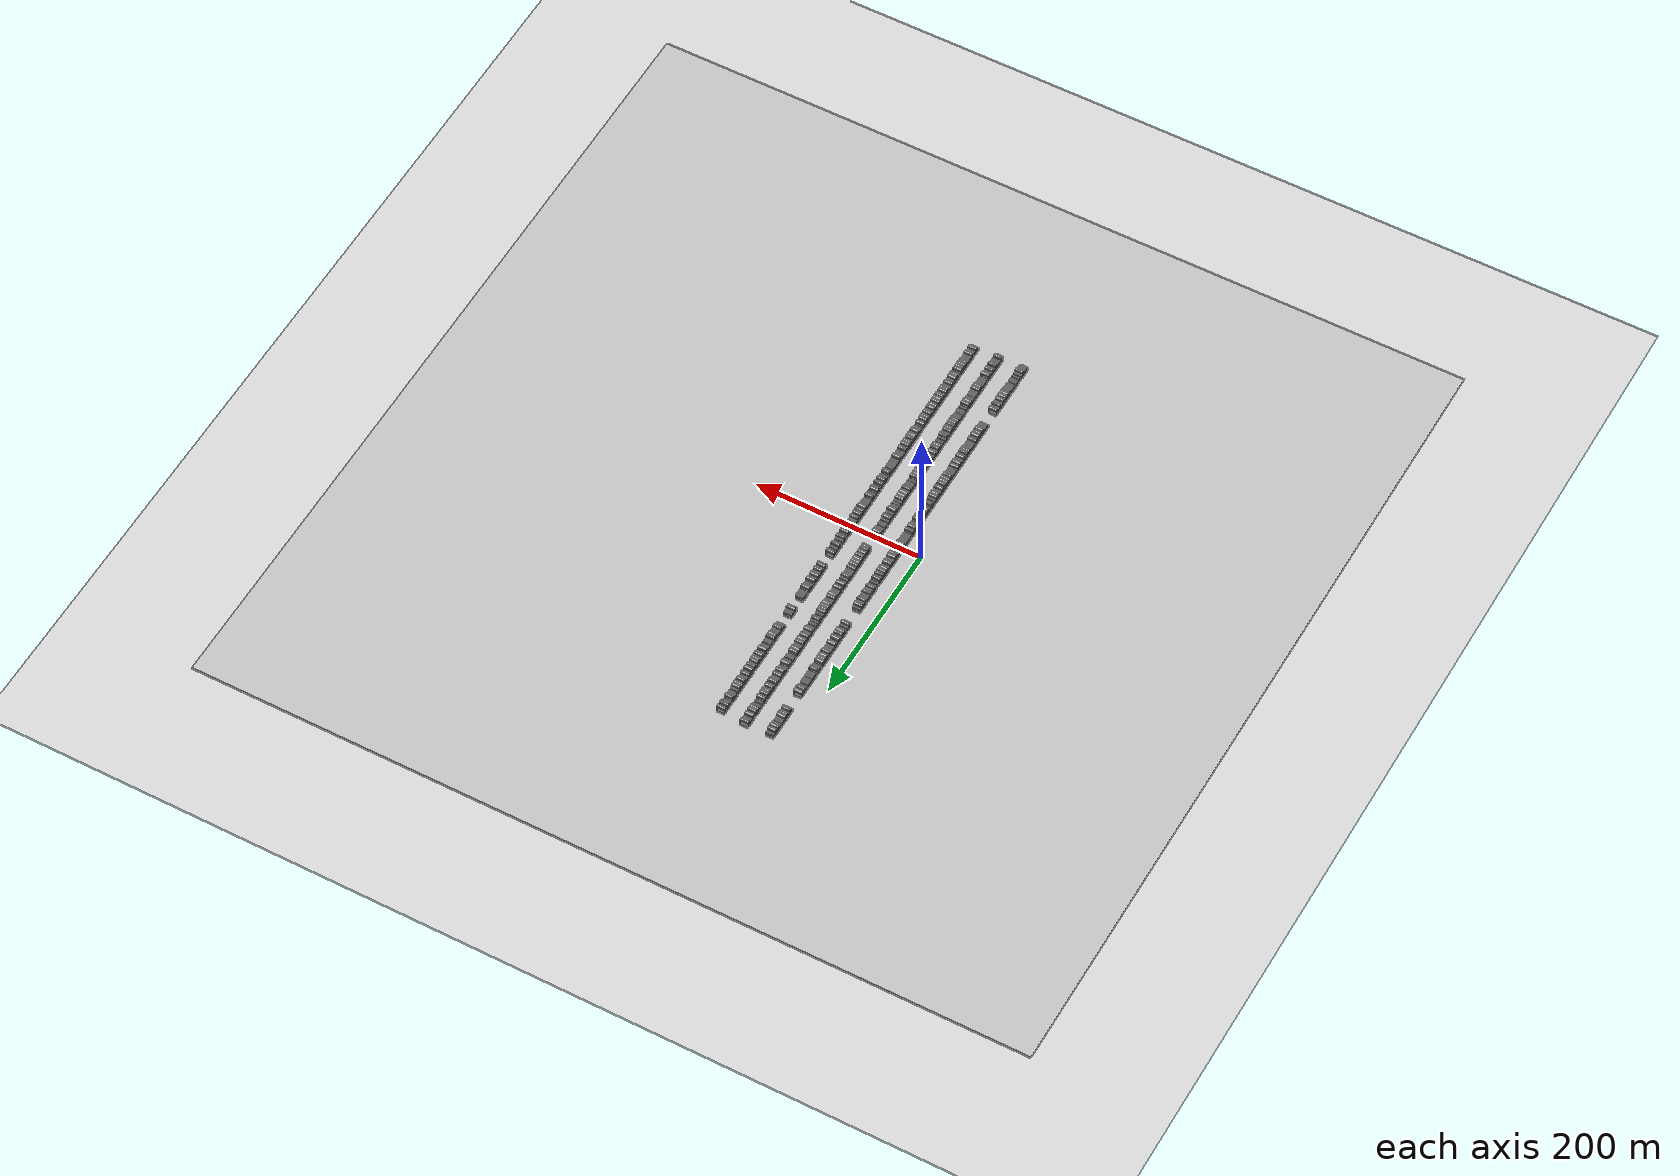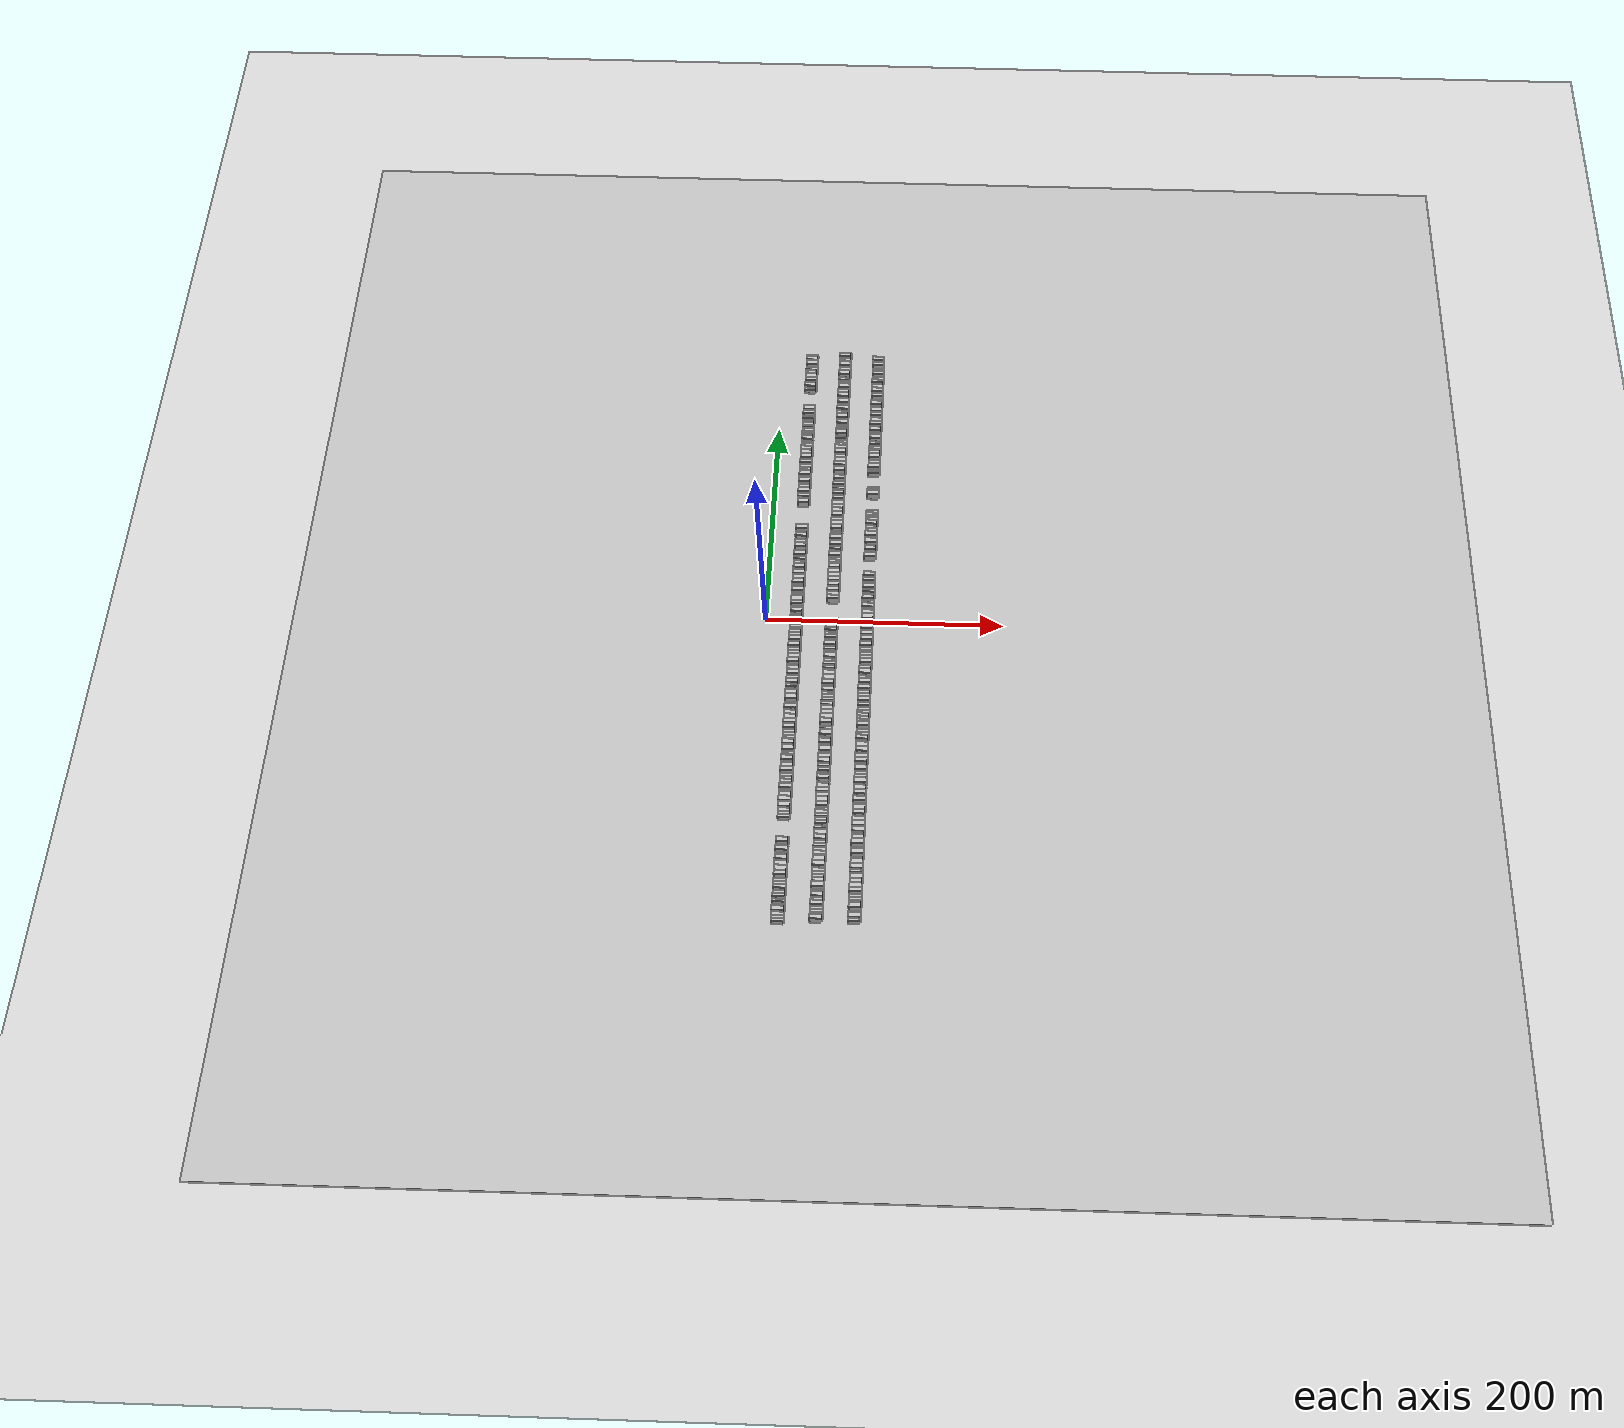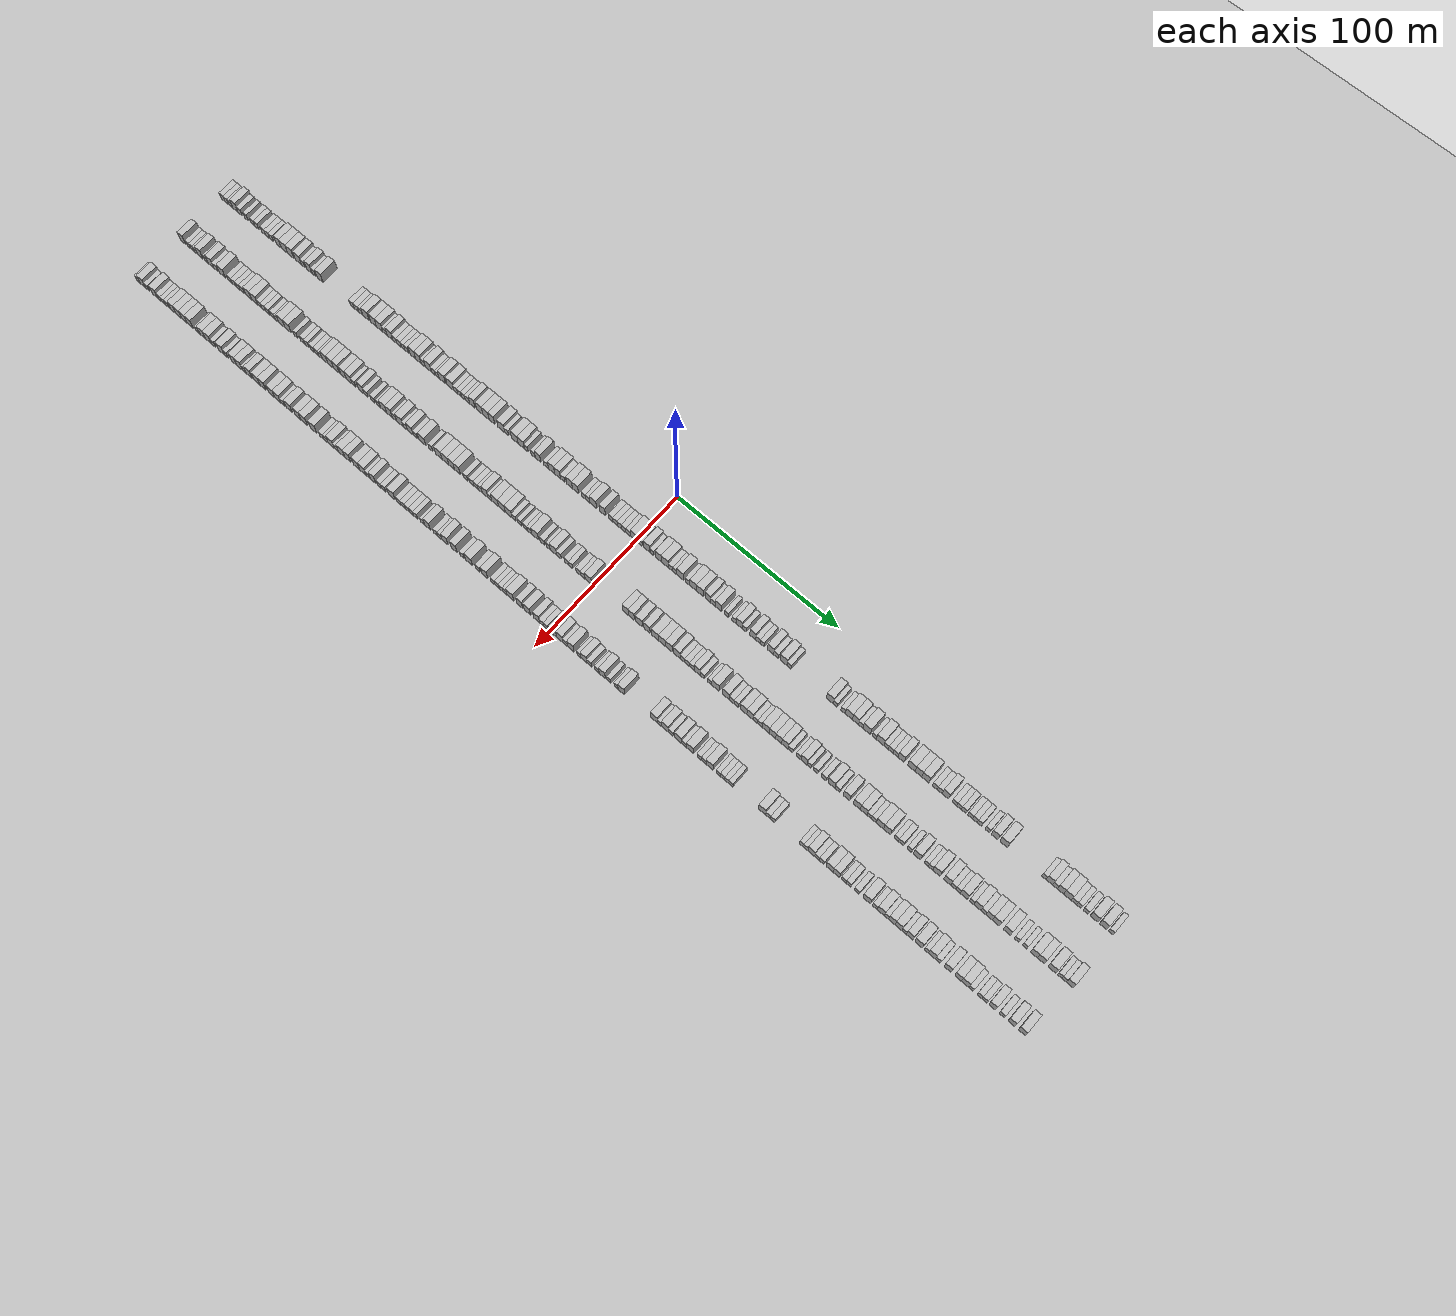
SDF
<?xml version="1.0" encoding="utf-8"?>

<sdf version="1.6">

   <world name="default">

      <gui fullscreen="0">

         <camera name="user_camera">

            <pose>-15 0 4.57585 0 0 0</pose>

            <view_controller>orbit</view_controller>

         </camera>

      </gui>

      <scene>

         <sky>

           <clouds>

             <speed>12</speed>

           </clouds>

         </sky>

         <ambient>0.4 0.4 0.4 1</ambient>

         <background>0.7 0.7 0.7 1</background>

         <shadows>1</shadows>

      </scene>

      <gravity>0 0 -9.8066</gravity>

      <magnetic_field>6e-06 2.3e-05 -4.2e-05</magnetic_field>

      <physics default="0" name="default_physics" type="ode">

         <ode>

            <solver>

               <type>quick</type>

               <iters>10</iters>

               <sor>1.0</sor>

               <use_dynamic_moi_rescaling>0</use_dynamic_moi_rescaling>

            </solver>

            <constraints>

               <cfm>0</cfm>

               <erp>0.2</erp>

               <contact_max_correcting_vel>100</contact_max_correcting_vel>

               <contact_surface_layer>0.001</contact_surface_layer>

            </constraints>

         </ode>

         <max_step_size>0.004</max_step_size>

         <real_time_factor>1</real_time_factor>

         <real_time_update_rate>250</real_time_update_rate>

      </physics>

      <light name="sun" type="directional">

         <cast_shadows>1</cast_shadows>

         <pose>0 0 10 0 0 0</pose>

         <diffuse>0.8 0.8 0.8 1</diffuse>

         <specular>0.2 0.2 0.2 1</specular>

         <attenuation>

            <range>1000</range>

            <constant>0.9</constant>

            <linear>0.01</linear>

            <quadratic>0.001</quadratic>

         </attenuation>

         <direction>-0.5 0.1 -0.9</direction>

      </light>

      <include>

         <name>ground_plane_1</name>

         <uri>model://HANNAS_ground_plane</uri>

         <pose>0 0 0  0 0 0</pose>

      </include>

      <include>

         <name>ground_plane_2</name>

         <uri>model://HANNAS_ground_plane</uri>

         <pose>100 0 0  0 0 0</pose>

      </include>

      <model name="building_1">

         <static>1</static>

         <pose frame="">25.0000 -278.5228 0 0.000000 0.000000 0.000000</pose>

         <link name="link">

            <pose frame="">0 0 3.00 0 0 0</pose>

            <collision name="collision">

               <geometry>

                  <box>

                     <size>10.0000 2.9545 6.0000</size>

                  </box>

               </geometry>

               <max_contacts>10</max_contacts>

               <surface>

                  <contact>

                     <ode/>

                  </contact>

                  <bounce/>

                  <friction>

                     <torsional>

                        <ode/>

                     </torsional>

                     <ode/>

                  </friction>

               </surface>

            </collision>

            <visual name="visual">

               <cast_shadows>0</cast_shadows>

               <geometry>

                  <box>

                     <size>10.0000 2.9545 6.0000</size>

                  </box>

               </geometry>

               <material>

                  <script>

                     <uri>model://HANNAS_wall/materials/scripts</uri>

                     <uri>model://HANNAS_wall/materials/textures</uri>

                     <name>vrc/HANNAS_wall</name>

                  </script>

               </material>

            </visual>

            <self_collide>0</self_collide>

            <enable_wind>0</enable_wind>

            <kinematic>0</kinematic>

         </link>

      </model>

      <model name="building_2">

         <static>1</static>

         <pose frame="">25.0000 -275.7079 0 0.000000 0.000000 0.000000</pose>

         <link name="link">

            <pose frame="">0 0 3.00 0 0 0</pose>

            <collision name="collision">

               <geometry>

                  <box>

                     <size>10.0000 2.6752 6.0000</size>

                  </box>

               </geometry>

               <max_contacts>10</max_contacts>

               <surface>

                  <contact>

                     <ode/>

                  </contact>

                  <bounce/>

                  <friction>

                     <torsional>

                        <ode/>

                     </torsional>

                     <ode/>

                  </friction>

               </surface>

            </collision>

            <visual name="visual">

               <cast_shadows>0</cast_shadows>

               <geometry>

                  <box>

                     <size>10.0000 2.6752 6.0000</size>

                  </box>

               </geometry>

               <material>

                  <script>

                     <uri>model://HANNAS_wall/materials/scripts</uri>

                     <uri>model://HANNAS_wall/materials/textures</uri>

                     <name>vrc/HANNAS_wall</name>

                  </script>

               </material>

            </visual>

            <self_collide>0</self_collide>

            <enable_wind>0</enable_wind>

            <kinematic>0</kinematic>

         </link>

      </model>

      <model name="building_3">

         <static>1</static>

         <pose frame="">25.0000 -272.9585 0 0.000000 0.000000 0.000000</pose>

         <link name="link">

            <pose frame="">0 0 3.00 0 0 0</pose>

            <collision name="collision">

               <geometry>

                  <box>

                     <size>10.0000 2.8236 6.0000</size>

                  </box>

               </geometry>

               <max_contacts>10</max_contacts>

               <surface>

                  <contact>

                     <ode/>

                  </contact>

                  <bounce/>

                  <friction>

                     <torsional>

                        <ode/>

                     </torsional>

                     <ode/>

                  </friction>

               </surface>

            </collision>

            <visual name="visual">

               <cast_shadows>0</cast_shadows>

               <geometry>

                  <box>

                     <size>10.0000 2.8236 6.0000</size>

                  </box>

               </geometry>

               <material>

                  <script>

                     <uri>model://HANNAS_wall/materials/scripts</uri>

                     <uri>model://HANNAS_wall/materials/textures</uri>

                     <name>vrc/HANNAS_wall</name>

                  </script>

               </material>

            </visual>

            <self_collide>0</self_collide>

            <enable_wind>0</enable_wind>

            <kinematic>0</kinematic>

         </link>

      </model>

      <model name="building_4">

         <static>1</static>

         <pose frame="">25.0000 -269.6810 0 0.000000 0.000000 0.000000</pose>

         <link name="link">

            <pose frame="">0 0 4.50 0 0 0</pose>

            <collision name="collision">

               <geometry>

                  <box>

                     <size>10.0000 3.7315 9.0000</size>

                  </box>

               </geometry>

               <max_contacts>10</max_contacts>

               <surface>

                  <contact>

                     <ode/>

                  </contact>

                  <bounce/>

                  <friction>

                     <torsional>

                        <ode/>

                     </torsional>

                     <ode/>

                  </friction>

               </surface>

            </collision>

            <visual name="visual">

               <cast_shadows>0</cast_shadows>

               <geometry>

                  <box>

                     <size>10.0000 3.7315 9.0000</size>

                  </box>

               </geometry>

               <material>

                  <script>

                     <uri>model://HANNAS_wall/materials/scripts</uri>

                     <uri>model://HANNAS_wall/materials/textures</uri>

                     <name>vrc/HANNAS_wall</name>

                  </script>

               </material>

            </visual>

            <self_collide>0</self_collide>

            <enable_wind>0</enable_wind>

            <kinematic>0</kinematic>

         </link>

      </model>

      <model name="building_5">

         <static>1</static>

         <pose frame="">25.0000 -266.3758 0 0.000000 0.000000 0.000000</pose>

         <link name="link">

            <pose frame="">0 0 3.00 0 0 0</pose>

            <collision name="collision">

               <geometry>

                  <box>

                     <size>10.0000 2.8788 6.0000</size>

                  </box>

               </geometry>

               <max_contacts>10</max_contacts>

               <surface>

                  <contact>

                     <ode/>

                  </contact>

                  <bounce/>

                  <friction>

                     <torsional>

                        <ode/>

                     </torsional>

                     <ode/>

                  </friction>

               </surface>

            </collision>

            <visual name="visual">

               <cast_shadows>0</cast_shadows>

               <geometry>

                  <box>

                     <size>10.0000 2.8788 6.0000</size>

                  </box>

               </geometry>

               <material>

                  <script>

                     <uri>model://HANNAS_wall/materials/scripts</uri>

                     <uri>model://HANNAS_wall/materials/textures</uri>

                     <name>vrc/HANNAS_wall</name>

                  </script>

               </material>

            </visual>

            <self_collide>0</self_collide>

            <enable_wind>0</enable_wind>

            <kinematic>0</kinematic>

         </link>

      </model>

      <model name="building_6">

         <static>1</static>

         <pose frame="">25.0000 -261.7218 0 0.000000 0.000000 0.000000</pose>

         <link name="link">

            <pose frame="">0 0 3.00 0 0 0</pose>

            <collision name="collision">

               <geometry>

                  <box>

                     <size>10.0000 2.4293 6.0000</size>

                  </box>

               </geometry>

               <max_contacts>10</max_contacts>

               <surface>

                  <contact>

                     <ode/>

                  </contact>

                  <bounce/>

                  <friction>

                     <torsional>

                        <ode/>

                     </torsional>

                     <ode/>

                  </friction>

               </surface>

            </collision>

            <visual name="visual">

               <cast_shadows>0</cast_shadows>

               <geometry>

                  <box>

                     <size>10.0000 2.4293 6.0000</size>

                  </box>

               </geometry>

               <material>

                  <script>

                     <uri>model://HANNAS_wall/materials/scripts</uri>

                     <uri>model://HANNAS_wall/materials/textures</uri>

                     <name>vrc/HANNAS_wall</name>

                  </script>

               </material>

            </visual>

            <self_collide>0</self_collide>

            <enable_wind>0</enable_wind>

            <kinematic>0</kinematic>

         </link>

      </model>

      <model name="building_7">

         <static>1</static>

         <pose frame="">25.0000 -257.1109 0 0.000000 0.000000 0.000000</pose>

         <link name="link">

            <pose frame="">0 0 3.00 0 0 0</pose>

            <collision name="collision">

               <geometry>

                  <box>

                     <size>10.0000 2.7926 6.0000</size>

                  </box>

               </geometry>

               <max_contacts>10</max_contacts>

               <surface>

                  <contact>

                     <ode/>

                  </contact>

                  <bounce/>

                  <friction>

                     <torsional>

                        <ode/>

                     </torsional>

                     <ode/>

                  </friction>

               </surface>

            </collision>

            <visual name="visual">

               <cast_shadows>0</cast_shadows>

               <geometry>

                  <box>

                     <size>10.0000 2.7926 6.0000</size>

                  </box>

               </geometry>

               <material>

                  <script>

                     <uri>model://HANNAS_wall/materials/scripts</uri>

                     <uri>model://HANNAS_wall/materials/textures</uri>

                     <name>vrc/HANNAS_wall</name>

                  </script>

               </material>

            </visual>

            <self_collide>0</self_collide>

            <enable_wind>0</enable_wind>

            <kinematic>0</kinematic>

         </link>

      </model>

      <model name="building_8">

         <static>1</static>

         <pose frame="">25.0000 -254.3193 0 0.000000 0.000000 0.000000</pose>

         <link name="link">

            <pose frame="">0 0 3.00 0 0 0</pose>

            <collision name="collision">

               <geometry>

                  <box>

                     <size>10.0000 2.7906 6.0000</size>

                  </box>

               </geometry>

               <max_contacts>10</max_contacts>

               <surface>

                  <contact>

                     <ode/>

                  </contact>

                  <bounce/>

                  <friction>

                     <torsional>

                        <ode/>

                     </torsional>

                     <ode/>

                  </friction>

               </surface>

            </collision>

            <visual name="visual">

               <cast_shadows>0</cast_shadows>

               <geometry>

                  <box>

                     <size>10.0000 2.7906 6.0000</size>

                  </box>

               </geometry>

               <material>

                  <script>

                     <uri>model://HANNAS_wall/materials/scripts</uri>

                     <uri>model://HANNAS_wall/materials/textures</uri>

                     <name>vrc/HANNAS_wall</name>

                  </script>

               </material>

            </visual>

            <self_collide>0</self_collide>

            <enable_wind>0</enable_wind>

            <kinematic>0</kinematic>

         </link>

      </model>

      <model name="building_9">

         <static>1</static>

         <pose frame="">25.0000 -249.4933 0 0.000000 0.000000 0.000000</pose>

         <link name="link">

            <pose frame="">0 0 3.00 0 0 0</pose>

            <collision name="collision">

               <geometry>

                  <box>

                     <size>10.0000 2.8613 6.0000</size>

                  </box>

               </geometry>

               <max_contacts>10</max_contacts>

               <surface>

                  <contact>

                     <ode/>

                  </contact>

                  <bounce/>

                  <friction>

                     <torsional>

                        <ode/>

                     </torsional>

                     <ode/>

                  </friction>

               </surface>

            </collision>

            <visual name="visual">

               <cast_shadows>0</cast_shadows>

               <geometry>

                  <box>

                     <size>10.0000 2.8613 6.0000</size>

                  </box>

               </geometry>

               <material>

                  <script>

                     <uri>model://HANNAS_wall/materials/scripts</uri>

                     <uri>model://HANNAS_wall/materials/textures</uri>

                     <name>vrc/HANNAS_wall</name>

                  </script>

               </material>

            </visual>

            <self_collide>0</self_collide>

            <enable_wind>0</enable_wind>

            <kinematic>0</kinematic>

         </link>

      </model>

      <model name="building_10">

         <static>1</static>

         <pose frame="">25.0000 -246.6186 0 0.000000 0.000000 0.000000</pose>

         <link name="link">

            <pose frame="">0 0 3.00 0 0 0</pose>

            <collision name="collision">

               <geometry>

                  <box>

                     <size>10.0000 2.8881 6.0000</size>

                  </box>

               </geometry>

               <max_contacts>10</max_contacts>

               <surface>

                  <contact>

                     <ode/>

                  </contact>

                  <bounce/>

                  <friction>

                     <torsional>

                        <ode/>

                     </torsional>

                     <ode/>

                  </friction>

               </surface>

            </collision>

            <visual name="visual">

               <cast_shadows>0</cast_shadows>

               <geometry>

                  <box>

                     <size>10.0000 2.8881 6.0000</size>

                  </box>

               </geometry>

               <material>

                  <script>

                     <uri>model://HANNAS_wall/materials/scripts</uri>

                     <uri>model://HANNAS_wall/materials/textures</uri>

                     <name>vrc/HANNAS_wall</name>

                  </script>

               </material>

            </visual>

            <self_collide>0</self_collide>

            <enable_wind>0</enable_wind>

            <kinematic>0</kinematic>

         </link>

      </model>

      <model name="building_11">

         <static>1</static>

         <pose frame="">25.0000 -243.8500 0 0.000000 0.000000 0.000000</pose>

         <link name="link">

            <pose frame="">0 0 3.00 0 0 0</pose>

            <collision name="collision">

               <geometry>

                  <box>

                     <size>10.0000 2.6490 6.0000</size>

                  </box>

               </geometry>

               <max_contacts>10</max_contacts>

               <surface>

                  <contact>

                     <ode/>

                  </contact>

                  <bounce/>

                  <friction>

                     <torsional>

                        <ode/>

                     </torsional>

                     <ode/>

                  </friction>

               </surface>

            </collision>

            <visual name="visual">

               <cast_shadows>0</cast_shadows>

               <geometry>

                  <box>

                     <size>10.0000 2.6490 6.0000</size>

                  </box>

               </geometry>

               <material>

                  <script>

                     <uri>model://HANNAS_wall/materials/scripts</uri>

                     <uri>model://HANNAS_wall/materials/textures</uri>

                     <name>vrc/HANNAS_wall</name>

                  </script>

               </material>

            </visual>

            <self_collide>0</self_collide>

            <enable_wind>0</enable_wind>

            <kinematic>0</kinematic>

         </link>

      </model>

      <model name="building_12">

         <static>1</static>

         <pose frame="">25.0000 -238.7213 0 0.000000 0.000000 0.000000</pose>

         <link name="link">

            <pose frame="">0 0 4.50 0 0 0</pose>

            <collision name="collision">

               <geometry>

                  <box>

                     <size>10.0000 3.6084 9.0000</size>

                  </box>

               </geometry>

               <max_contacts>10</max_contacts>

               <surface>

                  <contact>

                     <ode/>

                  </contact>

                  <bounce/>

                  <friction>

                     <torsional>

                        <ode/>

                     </torsional>

                     <ode/>

                  </friction>

               </surface>

            </collision>

            <visual name="visual">

               <cast_shadows>0</cast_shadows>

               <geometry>

                  <box>

                     <size>10.0000 3.6084 9.0000</size>

                  </box>

               </geometry>

               <material>

                  <script>

                     <uri>model://HANNAS_wall/materials/scripts</uri>

                     <uri>model://HANNAS_wall/materials/textures</uri>

                     <name>vrc/HANNAS_wall</name>

                  </script>

               </material>

            </visual>

            <self_collide>0</self_collide>

            <enable_wind>0</enable_wind>

            <kinematic>0</kinematic>

         </link>

      </model>

      <model name="building_13">

         <static>1</static>

         <pose frame="">25.0000 -234.6921 0 0.000000 0.000000 0.000000</pose>

         <link name="link">

            <pose frame="">0 0 4.50 0 0 0</pose>

            <collision name="collision">

               <geometry>

                  <box>

                     <size>10.0000 4.4501 9.0000</size>

                  </box>

               </geometry>

               <max_contacts>10</max_contacts>

               <surface>

                  <contact>

                     <ode/>

                  </contact>

                  <bounce/>

                  <friction>

                     <torsional>

                        <ode/>

                     </torsional>

                     <ode/>

                  </friction>

               </surface>

            </collision>

            <visual name="visual">

               <cast_shadows>0</cast_shadows>

               <geometry>

                  <box>

                     <size>10.0000 4.4501 9.0000</size>

                  </box>

               </geometry>

               <material>

                  <script>

                     <uri>model://HANNAS_wall/materials/scripts</uri>

                     <uri>model://HANNAS_wall/materials/textures</uri>

                     <name>vrc/HANNAS_wall</name>

                  </script>

               </material>

            </visual>

            <self_collide>0</self_collide>

            <enable_wind>0</enable_wind>

            <kinematic>0</kinematic>

         </link>

      </model>

      <model name="building_14">

         <static>1</static>

         <pose frame="">25.0000 -230.3125 0 0.000000 0.000000 0.000000</pose>

         <link name="link">

            <pose frame="">0 0 4.50 0 0 0</pose>

            <collision name="collision">

               <geometry>

                  <box>

                     <size>10.0000 4.3090 9.0000</size>

                  </box>

               </geometry>

               <max_contacts>10</max_contacts>

               <surface>

                  <contact>

                     <ode/>

                  </contact>

                  <bounce/>

                  <friction>

                     <torsional>

                        <ode/>

                     </torsional>

                     <ode/>

                  </friction>

               </surface>

            </collision>

            <visual name="visual">

               <cast_shadows>0</cast_shadows>

               <geometry>

                  <box>

                     <size>10.0000 4.3090 9.0000</size>

                  </box>

               </geometry>

               <material>

                  <script>

                     <uri>model://HANNAS_wall/materials/scripts</uri>

                     <uri>model://HANNAS_wall/materials/textures</uri>

                     <name>vrc/HANNAS_wall</name>

                  </script>

               </material>

            </visual>

            <self_collide>0</self_collide>

            <enable_wind>0</enable_wind>

            <kinematic>0</kinematic>

         </link>

      </model>

      <model name="building_15">

         <static>1</static>

         <pose frame="">25.0000 -225.0291 0 0.000000 0.000000 0.000000</pose>

         <link name="link">

            <pose frame="">0 0 4.50 0 0 0</pose>

            <collision name="collision">

               <geometry>

                  <box>

                     <size>10.0000 4.2579 9.0000</size>

                  </box>

               </geometry>

               <max_contacts>10</max_contacts>

               <surface>

                  <contact>

                     <ode/>

                  </contact>

                  <bounce/>

                  <friction>

                     <torsional>

                        <ode/>

                     </torsional>

                     <ode/>

                  </friction>

               </surface>

            </collision>

            <visual name="visual">

               <cast_shadows>0</cast_shadows>

               <geometry>

                  <box>

                     <size>10.0000 4.2579 9.0000</size>

                  </box>

               </geometry>

               <material>

                  <script>

                     <uri>model://HANNAS_wall/materials/scripts</uri>

                     <uri>model://HANNAS_wall/materials/textures</uri>

                     <name>vrc/HANNAS_wall</name>

                  </script>

               </material>

            </visual>

            <self_collide>0</self_collide>

            <enable_wind>0</enable_wind>

            <kinematic>0</kinematic>

         </link>

      </model>

      <model name="building_16">

         <static>1</static>

         <pose frame="">25.0000 -221.5347 0 0.000000 0.000000 0.000000</pose>

         <link name="link">

            <pose frame="">0 0 3.00 0 0 0</pose>

            <collision name="collision">

               <geometry>

                  <box>

                     <size>10.0000 2.7310 6.0000</size>

                  </box>

               </geometry>

               <max_contacts>10</max_contacts>

               <surface>

                  <contact>

                     <ode/>

                  </contact>

                  <bounce/>

                  <friction>

                     <torsional>

                        <ode/>

                     </torsional>

                     <ode/>

                  </friction>

               </surface>

            </collision>

            <visual name="visual">

               <cast_shadows>0</cast_shadows>

               <geometry>

                  <box>

                     <size>10.0000 2.7310 6.0000</size>

                  </box>

               </geometry>

               <material>

                  <script>

                     <uri>model://HANNAS_wall/materials/scripts</uri>

                     <uri>model://HANNAS_wall/materials/textures</uri>

                     <name>vrc/HANNAS_wall</name>

                  </script>

               </material>

            </visual>

            <self_collide>0</self_collide>

            <enable_wind>0</enable_wind>

            <kinematic>0</kinematic>

         </link>

      </model>

      <model name="building_17">

         <static>1</static>

         <pose frame="">25.0000 -217.3111 0 0.000000 0.000000 0.000000</pose>

         <link name="link">

            <pose frame="">0 0 4.50 0 0 0</pose>

            <collision name="collision">

               <geometry>

                  <box>

                     <size>10.0000 3.7161 9.0000</size>

                  </box>

               </geometry>

               <max_contacts>10</max_contacts>

               <surface>

                  <contact>

                     <ode/>

                  </contact>

                  <bounce/>

                  <friction>

                     <torsional>

                        <ode/>

                     </torsional>

                     <ode/>

                  </friction>

               </surface>

            </collision>

            <visual name="visual">

               <cast_shadows>0</cast_shadows>

               <geometry>

                  <box>

                     <size>10.0000 3.7161 9.0000</size>

                  </box>

               </geometry>

               <material>

                  <script>

                     <uri>model://HANNAS_wall/materials/scripts</uri>

                     <uri>model://HANNAS_wall/materials/textures</uri>

                     <name>vrc/HANNAS_wall</name>

                  </script>

               </material>

            </visual>

            <self_collide>0</self_collide>

            <enable_wind>0</enable_wind>

            <kinematic>0</kinematic>

         </link>

      </model>

      <model name="building_18">

         <static>1</static>

         <pose frame="">25.0000 -214.1741 0 0.000000 0.000000 0.000000</pose>

         <link name="link">

            <pose frame="">0 0 3.00 0 0 0</pose>

            <collision name="collision">

               <geometry>

                  <box>

                     <size>10.0000 2.5580 6.0000</size>

                  </box>

               </geometry>

               <max_contacts>10</max_contacts>

               <surface>

                  <contact>

                     <ode/>

                  </contact>

                  <bounce/>

                  <friction>

                     <torsional>

                        <ode/>

                     </torsional>

                     <ode/>

                  </friction>

               </surface>

            </collision>

            <visual name="visual">

               <cast_shadows>0</cast_shadows>

               <geometry>

                  <box>

                     <size>10.0000 2.5580 6.0000</size>

                  </box>

               </geometry>

               <material>

                  <script>

                     <uri>model://HANNAS_wall/materials/scripts</uri>

                     <uri>model://HANNAS_wall/materials/textures</uri>

                     <name>vrc/HANNAS_wall</name>

                  </script>

               </material>

            </visual>

            <self_collide>0</self_collide>

            <enable_wind>0</enable_wind>

            <kinematic>0</kinematic>

         </link>

      </model>

      <model name="building_19">

         <static>1</static>

         <pose frame="">25.0000 -209.8170 0 0.000000 0.000000 0.000000</pose>

         <link name="link">

            <pose frame="">0 0 4.50 0 0 0</pose>

            <collision name="collision">

               <geometry>

                  <box>

                     <size>10.0000 4.1563 9.0000</size>

                  </box>

               </geometry>

               <max_contacts>10</max_contacts>

               <surface>

                  <contact>

                     <ode/>

                  </contact>

                  <bounce/>

                  <friction>

                     <torsional>

                        <ode/>

                     </torsional>

                     <ode/>

                  </friction>

               </surface>

            </collision>

            <visual name="visual">

               <cast_shadows>0</cast_shadows>

               <geometry>

                  <box>

                     <size>10.0000 4.1563 9.0000</size>

                  </box>

               </geometry>

               <material>

                  <script>

                     <uri>model://HANNAS_wall/materials/scripts</uri>

                     <uri>model://HANNAS_wall/materials/textures</uri>

                     <name>vrc/HANNAS_wall</name>

                  </script>

               </material>

            </visual>

            <self_collide>0</self_collide>

            <enable_wind>0</enable_wind>

            <kinematic>0</kinematic>

         </link>

      </model>

      <model name="building_20">

         <static>1</static>

         <pose frame="">25.0000 -187.5165 0 0.000000 0.000000 0.000000</pose>

         <link name="link">

            <pose frame="">0 0 3.00 0 0 0</pose>

            <collision name="collision">

               <geometry>

                  <box>

                     <size>10.0000 2.8149 6.0000</size>

                  </box>

               </geometry>

               <max_contacts>10</max_contacts>

               <surface>

                  <contact>

                     <ode/>

                  </contact>

                  <bounce/>

                  <friction>

                     <torsional>

                        <ode/>

                     </torsional>

                     <ode/>

                  </friction>

               </surface>

            </collision>

            <visual name="visual">

               <cast_shadows>0</cast_shadows>

               <geometry>

                  <box>

                     <size>10.0000 2.8149 6.0000</size>

                  </box>

               </geometry>

               <material>

                  <script>

                     <uri>model://HANNAS_wall/materials/scripts</uri>

                     <uri>model://HANNAS_wall/materials/textures</uri>

                     <name>vrc/HANNAS_wall</name>

                  </script>

               </material>

            </visual>

            <self_collide>0</self_collide>

            <enable_wind>0</enable_wind>

            <kinematic>0</kinematic>

         </link>

      </model>

      <model name="building_21">

         <static>1</static>

         <pose frame="">25.0000 -184.6260 0 0.000000 0.000000 0.000000</pose>

         <link name="link">

            <pose frame="">0 0 3.00 0 0 0</pose>

            <collision name="collision">

               <geometry>

                  <box>

                     <size>10.0000 2.9661 6.0000</size>

                  </box>

               </geometry>

               <max_contacts>10</max_contacts>

               <surface>

                  <contact>

                     <ode/>

                  </contact>

                  <bounce/>

                  <friction>

                     <torsional>

                        <ode/>

                     </torsional>

                     <ode/>

                  </friction>

               </surface>

            </collision>

            <visual name="visual">

               <cast_shadows>0</cast_shadows>

               <geometry>

                  <box>

                     <size>10.0000 2.9661 6.0000</size>

                  </box>

               </geometry>

               <material>

                  <script>

                     <uri>model://HANNAS_wall/materials/scripts</uri>

                     <uri>model://HANNAS_wall/materials/textures</uri>

                     <name>vrc/HANNAS_wall</name>

                  </script>

               </material>

            </visual>

            <self_collide>0</self_collide>

            <enable_wind>0</enable_wind>

            <kinematic>0</kinematic>

         </link>

      </model>

      <model name="building_22">

         <static>1</static>

         <pose frame="">25.0000 -181.6571 0 0.000000 0.000000 0.000000</pose>

         <link name="link">

            <pose frame="">0 0 3.00 0 0 0</pose>

            <collision name="collision">

               <geometry>

                  <box>

                     <size>10.0000 2.9718 6.0000</size>

                  </box>

               </geometry>

               <max_contacts>10</max_contacts>

               <surface>

                  <contact>

                     <ode/>

                  </contact>

                  <bounce/>

                  <friction>

                     <torsional>

                        <ode/>

                     </torsional>

                     <ode/>

                  </friction>

               </surface>

            </collision>

            <visual name="visual">

               <cast_shadows>0</cast_shadows>

               <geometry>

                  <box>

                     <size>10.0000 2.9718 6.0000</size>

                  </box>

               </geometry>

               <material>

                  <script>

                     <uri>model://HANNAS_wall/materials/scripts</uri>

                     <uri>model://HANNAS_wall/materials/textures</uri>

                     <name>vrc/HANNAS_wall</name>

                  </script>

               </material>

            </visual>

            <self_collide>0</self_collide>

            <enable_wind>0</enable_wind>

            <kinematic>0</kinematic>

         </link>

      </model>

      <model name="building_23">

         <static>1</static>

         <pose frame="">25.0000 -178.0207 0 0.000000 0.000000 0.000000</pose>

         <link name="link">

            <pose frame="">0 0 4.50 0 0 0</pose>

            <collision name="collision">

               <geometry>

                  <box>

                     <size>10.0000 4.3011 9.0000</size>

                  </box>

               </geometry>

               <max_contacts>10</max_contacts>

               <surface>

                  <contact>

                     <ode/>

                  </contact>

                  <bounce/>

                  <friction>

                     <torsional>

                        <ode/>

                     </torsional>

                     <ode/>

                  </friction>

               </surface>

            </collision>

            <visual name="visual">

               <cast_shadows>0</cast_shadows>

               <geometry>

                  <box>

                     <size>10.0000 4.3011 9.0000</size>

                  </box>

               </geometry>

               <material>

                  <script>

                     <uri>model://HANNAS_wall/materials/scripts</uri>

                     <uri>model://HANNAS_wall/materials/textures</uri>

                     <name>vrc/HANNAS_wall</name>

                  </script>

               </material>

            </visual>

            <self_collide>0</self_collide>

            <enable_wind>0</enable_wind>

            <kinematic>0</kinematic>

         </link>

      </model>

      <model name="building_24">

         <static>1</static>

         <pose frame="">25.0000 -172.8933 0 0.000000 0.000000 0.000000</pose>

         <link name="link">

            <pose frame="">0 0 4.50 0 0 0</pose>

            <collision name="collision">

               <geometry>

                  <box>

                     <size>10.0000 3.9537 9.0000</size>

                  </box>

               </geometry>

               <max_contacts>10</max_contacts>

               <surface>

                  <contact>

                     <ode/>

                  </contact>

                  <bounce/>

                  <friction>

                     <torsional>

                        <ode/>

                     </torsional>

                     <ode/>

                  </friction>

               </surface>

            </collision>

            <visual name="visual">

               <cast_shadows>0</cast_shadows>

               <geometry>

                  <box>

                     <size>10.0000 3.9537 9.0000</size>

                  </box>

               </geometry>

               <material>

                  <script>

                     <uri>model://HANNAS_wall/materials/scripts</uri>

                     <uri>model://HANNAS_wall/materials/textures</uri>

                     <name>vrc/HANNAS_wall</name>

                  </script>

               </material>

            </visual>

            <self_collide>0</self_collide>

            <enable_wind>0</enable_wind>

            <kinematic>0</kinematic>

         </link>

      </model>

      <model name="building_25">

         <static>1</static>

         <pose frame="">25.0000 -168.7326 0 0.000000 0.000000 0.000000</pose>

         <link name="link">

            <pose frame="">0 0 4.50 0 0 0</pose>

            <collision name="collision">

               <geometry>

                  <box>

                     <size>10.0000 4.3678 9.0000</size>

                  </box>

               </geometry>

               <max_contacts>10</max_contacts>

               <surface>

                  <contact>

                     <ode/>

                  </contact>

                  <bounce/>

                  <friction>

                     <torsional>

                        <ode/>

                     </torsional>

                     <ode/>

                  </friction>

               </surface>

            </collision>

            <visual name="visual">

               <cast_shadows>0</cast_shadows>

               <geometry>

                  <box>

                     <size>10.0000 4.3678 9.0000</size>

                  </box>

               </geometry>

               <material>

                  <script>

                     <uri>model://HANNAS_wall/materials/scripts</uri>

                     <uri>model://HANNAS_wall/materials/textures</uri>

                     <name>vrc/HANNAS_wall</name>

                  </script>

               </material>

            </visual>

            <self_collide>0</self_collide>

            <enable_wind>0</enable_wind>

            <kinematic>0</kinematic>

         </link>

      </model>

      <model name="building_26">

         <static>1</static>

         <pose frame="">25.0000 -165.0727 0 0.000000 0.000000 0.000000</pose>

         <link name="link">

            <pose frame="">0 0 3.00 0 0 0</pose>

            <collision name="collision">

               <geometry>

                  <box>

                     <size>10.0000 2.9520 6.0000</size>

                  </box>

               </geometry>

               <max_contacts>10</max_contacts>

               <surface>

                  <contact>

                     <ode/>

                  </contact>

                  <bounce/>

                  <friction>

                     <torsional>

                        <ode/>

                     </torsional>

                     <ode/>

                  </friction>

               </surface>

            </collision>

            <visual name="visual">

               <cast_shadows>0</cast_shadows>

               <geometry>

                  <box>

                     <size>10.0000 2.9520 6.0000</size>

                  </box>

               </geometry>

               <material>

                  <script>

                     <uri>model://HANNAS_wall/materials/scripts</uri>

                     <uri>model://HANNAS_wall/materials/textures</uri>

                     <name>vrc/HANNAS_wall</name>

                  </script>

               </material>

            </visual>

            <self_collide>0</self_collide>

            <enable_wind>0</enable_wind>

            <kinematic>0</kinematic>

         </link>

      </model>

      <model name="building_27">

         <static>1</static>

         <pose frame="">25.0000 -161.6454 0 0.000000 0.000000 0.000000</pose>

         <link name="link">

            <pose frame="">0 0 4.50 0 0 0</pose>

            <collision name="collision">

               <geometry>

                  <box>

                     <size>10.0000 3.9026 9.0000</size>

                  </box>

               </geometry>

               <max_contacts>10</max_contacts>

               <surface>

                  <contact>

                     <ode/>

                  </contact>

                  <bounce/>

                  <friction>

                     <torsional>

                        <ode/>

                     </torsional>

                     <ode/>

                  </friction>

               </surface>

            </collision>

            <visual name="visual">

               <cast_shadows>0</cast_shadows>

               <geometry>

                  <box>

                     <size>10.0000 3.9026 9.0000</size>

                  </box>

               </geometry>

               <material>

                  <script>

                     <uri>model://HANNAS_wall/materials/scripts</uri>

                     <uri>model://HANNAS_wall/materials/textures</uri>

                     <name>vrc/HANNAS_wall</name>

                  </script>

               </material>

            </visual>

            <self_collide>0</self_collide>

            <enable_wind>0</enable_wind>

            <kinematic>0</kinematic>

         </link>

      </model>

      <model name="building_28">

         <static>1</static>

         <pose frame="">25.0000 -158.3003 0 0.000000 0.000000 0.000000</pose>

         <link name="link">

            <pose frame="">0 0 3.00 0 0 0</pose>

            <collision name="collision">

               <geometry>

                  <box>

                     <size>10.0000 2.7876 6.0000</size>

                  </box>

               </geometry>

               <max_contacts>10</max_contacts>

               <surface>

                  <contact>

                     <ode/>

                  </contact>

                  <bounce/>

                  <friction>

                     <torsional>

                        <ode/>

                     </torsional>

                     <ode/>

                  </friction>

               </surface>

            </collision>

            <visual name="visual">

               <cast_shadows>0</cast_shadows>

               <geometry>

                  <box>

                     <size>10.0000 2.7876 6.0000</size>

                  </box>

               </geometry>

               <material>

                  <script>

                     <uri>model://HANNAS_wall/materials/scripts</uri>

                     <uri>model://HANNAS_wall/materials/textures</uri>

                     <name>vrc/HANNAS_wall</name>

                  </script>

               </material>

            </visual>

            <self_collide>0</self_collide>

            <enable_wind>0</enable_wind>

            <kinematic>0</kinematic>

         </link>

      </model>

      <model name="building_29">

         <static>1</static>

         <pose frame="">25.0000 -155.4149 0 0.000000 0.000000 0.000000</pose>

         <link name="link">

            <pose frame="">0 0 3.00 0 0 0</pose>

            <collision name="collision">

               <geometry>

                  <box>

                     <size>10.0000 2.9831 6.0000</size>

                  </box>

               </geometry>

               <max_contacts>10</max_contacts>

               <surface>

                  <contact>

                     <ode/>

                  </contact>

                  <bounce/>

                  <friction>

                     <torsional>

                        <ode/>

                     </torsional>

                     <ode/>

                  </friction>

               </surface>

            </collision>

            <visual name="visual">

               <cast_shadows>0</cast_shadows>

               <geometry>

                  <box>

                     <size>10.0000 2.9831 6.0000</size>

                  </box>

               </geometry>

               <material>

                  <script>

                     <uri>model://HANNAS_wall/materials/scripts</uri>

                     <uri>model://HANNAS_wall/materials/textures</uri>

                     <name>vrc/HANNAS_wall</name>

                  </script>

               </material>

            </visual>

            <self_collide>0</self_collide>

            <enable_wind>0</enable_wind>

            <kinematic>0</kinematic>

         </link>

      </model>

      <model name="building_30">

         <static>1</static>

         <pose frame="">25.0000 -152.7174 0 0.000000 0.000000 0.000000</pose>

         <link name="link">

            <pose frame="">0 0 3.00 0 0 0</pose>

            <collision name="collision">

               <geometry>

                  <box>

                     <size>10.0000 2.4119 6.0000</size>

                  </box>

               </geometry>

               <max_contacts>10</max_contacts>

               <surface>

                  <contact>

                     <ode/>

                  </contact>

                  <bounce/>

                  <friction>

                     <torsional>

                        <ode/>

                     </torsional>

                     <ode/>

                  </friction>

               </surface>

            </collision>

            <visual name="visual">

               <cast_shadows>0</cast_shadows>

               <geometry>

                  <box>

                     <size>10.0000 2.4119 6.0000</size>

                  </box>

               </geometry>

               <material>

                  <script>

                     <uri>model://HANNAS_wall/materials/scripts</uri>

                     <uri>model://HANNAS_wall/materials/textures</uri>

                     <name>vrc/HANNAS_wall</name>

                  </script>

               </material>

            </visual>

            <self_collide>0</self_collide>

            <enable_wind>0</enable_wind>

            <kinematic>0</kinematic>

         </link>

      </model>

      <model name="building_31">

         <static>1</static>

         <pose frame="">25.0000 -150.2543 0 0.000000 0.000000 0.000000</pose>

         <link name="link">

            <pose frame="">0 0 3.00 0 0 0</pose>

            <collision name="collision">

               <geometry>

                  <box>

                     <size>10.0000 2.5144 6.0000</size>

                  </box>

               </geometry>

               <max_contacts>10</max_contacts>

               <surface>

                  <contact>

                     <ode/>

                  </contact>

                  <bounce/>

                  <friction>

                     <torsional>

                        <ode/>

                     </torsional>

                     <ode/>

                  </friction>

               </surface>

            </collision>

            <visual name="visual">

               <cast_shadows>0</cast_shadows>

               <geometry>

                  <box>

                     <size>10.0000 2.5144 6.0000</size>

                  </box>

               </geometry>

               <material>

                  <script>

                     <uri>model://HANNAS_wall/materials/scripts</uri>

                     <uri>model://HANNAS_wall/materials/textures</uri>

                     <name>vrc/HANNAS_wall</name>

                  </script>

               </material>

            </visual>

            <self_collide>0</self_collide>

            <enable_wind>0</enable_wind>

            <kinematic>0</kinematic>

         </link>

      </model>

      <model name="building_32">

         <static>1</static>

         <pose frame="">25.0000 -146.0555 0 0.000000 0.000000 0.000000</pose>

         <link name="link">

            <pose frame="">0 0 4.50 0 0 0</pose>

            <collision name="collision">

               <geometry>

                  <box>

                     <size>10.0000 3.8832 9.0000</size>

                  </box>

               </geometry>

               <max_contacts>10</max_contacts>

               <surface>

                  <contact>

                     <ode/>

                  </contact>

                  <bounce/>

                  <friction>

                     <torsional>

                        <ode/>

                     </torsional>

                     <ode/>

                  </friction>

               </surface>

            </collision>

            <visual name="visual">

               <cast_shadows>0</cast_shadows>

               <geometry>

                  <box>

                     <size>10.0000 3.8832 9.0000</size>

                  </box>

               </geometry>

               <material>

                  <script>

                     <uri>model://HANNAS_wall/materials/scripts</uri>

                     <uri>model://HANNAS_wall/materials/textures</uri>

                     <name>vrc/HANNAS_wall</name>

                  </script>

               </material>

            </visual>

            <self_collide>0</self_collide>

            <enable_wind>0</enable_wind>

            <kinematic>0</kinematic>

         </link>

      </model>

      <model name="building_33">

         <static>1</static>

         <pose frame="">25.0000 -142.2736 0 0.000000 0.000000 0.000000</pose>

         <link name="link">

            <pose frame="">0 0 4.50 0 0 0</pose>

            <collision name="collision">

               <geometry>

                  <box>

                     <size>10.0000 3.6805 9.0000</size>

                  </box>

               </geometry>

               <max_contacts>10</max_contacts>

               <surface>

                  <contact>

                     <ode/>

                  </contact>

                  <bounce/>

                  <friction>

                     <torsional>

                        <ode/>

                     </torsional>

                     <ode/>

                  </friction>

               </surface>

            </collision>

            <visual name="visual">

               <cast_shadows>0</cast_shadows>

               <geometry>

                  <box>

                     <size>10.0000 3.6805 9.0000</size>

                  </box>

               </geometry>

               <material>

                  <script>

                     <uri>model://HANNAS_wall/materials/scripts</uri>

                     <uri>model://HANNAS_wall/materials/textures</uri>

                     <name>vrc/HANNAS_wall</name>

                  </script>

               </material>

            </visual>

            <self_collide>0</self_collide>

            <enable_wind>0</enable_wind>

            <kinematic>0</kinematic>

         </link>

      </model>

      <model name="building_34">

         <static>1</static>

         <pose frame="">25.0000 -139.0617 0 0.000000 0.000000 0.000000</pose>

         <link name="link">

            <pose frame="">0 0 3.00 0 0 0</pose>

            <collision name="collision">

               <geometry>

                  <box>

                     <size>10.0000 2.7433 6.0000</size>

                  </box>

               </geometry>

               <max_contacts>10</max_contacts>

               <surface>

                  <contact>

                     <ode/>

                  </contact>

                  <bounce/>

                  <friction>

                     <torsional>

                        <ode/>

                     </torsional>

                     <ode/>

                  </friction>

               </surface>

            </collision>

            <visual name="visual">

               <cast_shadows>0</cast_shadows>

               <geometry>

                  <box>

                     <size>10.0000 2.7433 6.0000</size>

                  </box>

               </geometry>

               <material>

                  <script>

                     <uri>model://HANNAS_wall/materials/scripts</uri>

                     <uri>model://HANNAS_wall/materials/textures</uri>

                     <name>vrc/HANNAS_wall</name>

                  </script>

               </material>

            </visual>

            <self_collide>0</self_collide>

            <enable_wind>0</enable_wind>

            <kinematic>0</kinematic>

         </link>

      </model>

      <model name="building_35">

         <static>1</static>

         <pose frame="">25.0000 -135.5713 0 0.000000 0.000000 0.000000</pose>

         <link name="link">

            <pose frame="">0 0 4.50 0 0 0</pose>

            <collision name="collision">

               <geometry>

                  <box>

                     <size>10.0000 4.2375 9.0000</size>

                  </box>

               </geometry>

               <max_contacts>10</max_contacts>

               <surface>

                  <contact>

                     <ode/>

                  </contact>

                  <bounce/>

                  <friction>

                     <torsional>

                        <ode/>

                     </torsional>

                     <ode/>

                  </friction>

               </surface>

            </collision>

            <visual name="visual">

               <cast_shadows>0</cast_shadows>

               <geometry>

                  <box>

                     <size>10.0000 4.2375 9.0000</size>

                  </box>

               </geometry>

               <material>

                  <script>

                     <uri>model://HANNAS_wall/materials/scripts</uri>

                     <uri>model://HANNAS_wall/materials/textures</uri>

                     <name>vrc/HANNAS_wall</name>

                  </script>

               </material>

            </visual>

            <self_collide>0</self_collide>

            <enable_wind>0</enable_wind>

            <kinematic>0</kinematic>

         </link>

      </model>

      <model name="building_36">

         <static>1</static>

         <pose frame="">25.0000 -132.1241 0 0.000000 0.000000 0.000000</pose>

         <link name="link">

            <pose frame="">0 0 3.00 0 0 0</pose>

            <collision name="collision">

               <geometry>

                  <box>

                     <size>10.0000 2.6570 6.0000</size>

                  </box>

               </geometry>

               <max_contacts>10</max_contacts>

               <surface>

                  <contact>

                     <ode/>

                  </contact>

                  <bounce/>

                  <friction>

                     <torsional>

                        <ode/>

                     </torsional>

                     <ode/>

                  </friction>

               </surface>

            </collision>

            <visual name="visual">

               <cast_shadows>0</cast_shadows>

               <geometry>

                  <box>

                     <size>10.0000 2.6570 6.0000</size>

                  </box>

               </geometry>

               <material>

                  <script>

                     <uri>model://HANNAS_wall/materials/scripts</uri>

                     <uri>model://HANNAS_wall/materials/textures</uri>

                     <name>vrc/HANNAS_wall</name>

                  </script>

               </material>

            </visual>

            <self_collide>0</self_collide>

            <enable_wind>0</enable_wind>

            <kinematic>0</kinematic>

         </link>

      </model>

      <model name="building_37">

         <static>1</static>

         <pose frame="">25.0000 -129.5836 0 0.000000 0.000000 0.000000</pose>

         <link name="link">

            <pose frame="">0 0 3.00 0 0 0</pose>

            <collision name="collision">

               <geometry>

                  <box>

                     <size>10.0000 2.4239 6.0000</size>

                  </box>

               </geometry>

               <max_contacts>10</max_contacts>

               <surface>

                  <contact>

                     <ode/>

                  </contact>

                  <bounce/>

                  <friction>

                     <torsional>

                        <ode/>

                     </torsional>

                     <ode/>

                  </friction>

               </surface>

            </collision>

            <visual name="visual">

               <cast_shadows>0</cast_shadows>

               <geometry>

                  <box>

                     <size>10.0000 2.4239 6.0000</size>

                  </box>

               </geometry>

               <material>

                  <script>

                     <uri>model://HANNAS_wall/materials/scripts</uri>

                     <uri>model://HANNAS_wall/materials/textures</uri>

                     <name>vrc/HANNAS_wall</name>

                  </script>

               </material>

            </visual>

            <self_collide>0</self_collide>

            <enable_wind>0</enable_wind>

            <kinematic>0</kinematic>

         </link>

      </model>

      <model name="building_38">

         <static>1</static>

         <pose frame="">25.0000 -126.1847 0 0.000000 0.000000 0.000000</pose>

         <link name="link">

            <pose frame="">0 0 4.50 0 0 0</pose>

            <collision name="collision">

               <geometry>

                  <box>

                     <size>10.0000 4.3740 9.0000</size>

                  </box>

               </geometry>

               <max_contacts>10</max_contacts>

               <surface>

                  <contact>

                     <ode/>

                  </contact>

                  <bounce/>

                  <friction>

                     <torsional>

                        <ode/>

                     </torsional>

                     <ode/>

                  </friction>

               </surface>

            </collision>

            <visual name="visual">

               <cast_shadows>0</cast_shadows>

               <geometry>

                  <box>

                     <size>10.0000 4.3740 9.0000</size>

                  </box>

               </geometry>

               <material>

                  <script>

                     <uri>model://HANNAS_wall/materials/scripts</uri>

                     <uri>model://HANNAS_wall/materials/textures</uri>

                     <name>vrc/HANNAS_wall</name>

                  </script>

               </material>

            </visual>

            <self_collide>0</self_collide>

            <enable_wind>0</enable_wind>

            <kinematic>0</kinematic>

         </link>

      </model>

      <model name="building_39">

         <static>1</static>

         <pose frame="">25.0000 -120.7528 0 0.000000 0.000000 0.000000</pose>

         <link name="link">

            <pose frame="">0 0 4.50 0 0 0</pose>

            <collision name="collision">

               <geometry>

                  <box>

                     <size>10.0000 4.4898 9.0000</size>

                  </box>

               </geometry>

               <max_contacts>10</max_contacts>

               <surface>

                  <contact>

                     <ode/>

                  </contact>

                  <bounce/>

                  <friction>

                     <torsional>

                        <ode/>

                     </torsional>

                     <ode/>

                  </friction>

               </surface>

            </collision>

            <visual name="visual">

               <cast_shadows>0</cast_shadows>

               <geometry>

                  <box>

                     <size>10.0000 4.4898 9.0000</size>

                  </box>

               </geometry>

               <material>

                  <script>

                     <uri>model://HANNAS_wall/materials/scripts</uri>

                     <uri>model://HANNAS_wall/materials/textures</uri>

                     <name>vrc/HANNAS_wall</name>

                  </script>

               </material>

            </visual>

            <self_collide>0</self_collide>

            <enable_wind>0</enable_wind>

            <kinematic>0</kinematic>

         </link>

      </model>

      <model name="building_40">

         <static>1</static>

         <pose frame="">25.0000 -117.2379 0 0.000000 0.000000 0.000000</pose>

         <link name="link">

            <pose frame="">0 0 3.00 0 0 0</pose>

            <collision name="collision">

               <geometry>

                  <box>

                     <size>10.0000 2.5400 6.0000</size>

                  </box>

               </geometry>

               <max_contacts>10</max_contacts>

               <surface>

                  <contact>

                     <ode/>

                  </contact>

                  <bounce/>

                  <friction>

                     <torsional>

                        <ode/>

                     </torsional>

                     <ode/>

                  </friction>

               </surface>

            </collision>

            <visual name="visual">

               <cast_shadows>0</cast_shadows>

               <geometry>

                  <box>

                     <size>10.0000 2.5400 6.0000</size>

                  </box>

               </geometry>

               <material>

                  <script>

                     <uri>model://HANNAS_wall/materials/scripts</uri>

                     <uri>model://HANNAS_wall/materials/textures</uri>

                     <name>vrc/HANNAS_wall</name>

                  </script>

               </material>

            </visual>

            <self_collide>0</self_collide>

            <enable_wind>0</enable_wind>

            <kinematic>0</kinematic>

         </link>

      </model>

      <model name="building_41">

         <static>1</static>

         <pose frame="">25.0000 -114.6901 0 0.000000 0.000000 0.000000</pose>

         <link name="link">

            <pose frame="">0 0 3.00 0 0 0</pose>

            <collision name="collision">

               <geometry>

                  <box>

                     <size>10.0000 2.5557 6.0000</size>

                  </box>

               </geometry>

               <max_contacts>10</max_contacts>

               <surface>

                  <contact>

                     <ode/>

                  </contact>

                  <bounce/>

                  <friction>

                     <torsional>

                        <ode/>

                     </torsional>

                     <ode/>

                  </friction>

               </surface>

            </collision>

            <visual name="visual">

               <cast_shadows>0</cast_shadows>

               <geometry>

                  <box>

                     <size>10.0000 2.5557 6.0000</size>

                  </box>

               </geometry>

               <material>

                  <script>

                     <uri>model://HANNAS_wall/materials/scripts</uri>

                     <uri>model://HANNAS_wall/materials/textures</uri>

                     <name>vrc/HANNAS_wall</name>

                  </script>

               </material>

            </visual>

            <self_collide>0</self_collide>

            <enable_wind>0</enable_wind>

            <kinematic>0</kinematic>

         </link>

      </model>

      <model name="building_42">

         <static>1</static>

         <pose frame="">25.0000 -112.1726 0 0.000000 0.000000 0.000000</pose>

         <link name="link">

            <pose frame="">0 0 3.00 0 0 0</pose>

            <collision name="collision">

               <geometry>

                  <box>

                     <size>10.0000 2.4793 6.0000</size>

                  </box>

               </geometry>

               <max_contacts>10</max_contacts>

               <surface>

                  <contact>

                     <ode/>

                  </contact>

                  <bounce/>

                  <friction>

                     <torsional>

                        <ode/>

                     </torsional>

                     <ode/>

                  </friction>

               </surface>

            </collision>

            <visual name="visual">

               <cast_shadows>0</cast_shadows>

               <geometry>

                  <box>

                     <size>10.0000 2.4793 6.0000</size>

                  </box>

               </geometry>

               <material>

                  <script>

                     <uri>model://HANNAS_wall/materials/scripts</uri>

                     <uri>model://HANNAS_wall/materials/textures</uri>

                     <name>vrc/HANNAS_wall</name>

                  </script>

               </material>

            </visual>

            <self_collide>0</self_collide>

            <enable_wind>0</enable_wind>

            <kinematic>0</kinematic>

         </link>

      </model>

      <model name="building_43">

         <static>1</static>

         <pose frame="">25.0000 -109.4523 0 0.000000 0.000000 0.000000</pose>

         <link name="link">

            <pose frame="">0 0 3.00 0 0 0</pose>

            <collision name="collision">

               <geometry>

                  <box>

                     <size>10.0000 2.9611 6.0000</size>

                  </box>

               </geometry>

               <max_contacts>10</max_contacts>

               <surface>

                  <contact>

                     <ode/>

                  </contact>

                  <bounce/>

                  <friction>

                     <torsional>

                        <ode/>

                     </torsional>

                     <ode/>

                  </friction>

               </surface>

            </collision>

            <visual name="visual">

               <cast_shadows>0</cast_shadows>

               <geometry>

                  <box>

                     <size>10.0000 2.9611 6.0000</size>

                  </box>

               </geometry>

               <material>

                  <script>

                     <uri>model://HANNAS_wall/materials/scripts</uri>

                     <uri>model://HANNAS_wall/materials/textures</uri>

                     <name>vrc/HANNAS_wall</name>

                  </script>

               </material>

            </visual>

            <self_collide>0</self_collide>

            <enable_wind>0</enable_wind>

            <kinematic>0</kinematic>

         </link>

      </model>

      <model name="building_44">

         <static>1</static>

         <pose frame="">25.0000 -106.1168 0 0.000000 0.000000 0.000000</pose>

         <link name="link">

            <pose frame="">0 0 4.50 0 0 0</pose>

            <collision name="collision">

               <geometry>

                  <box>

                     <size>10.0000 3.7099 9.0000</size>

                  </box>

               </geometry>

               <max_contacts>10</max_contacts>

               <surface>

                  <contact>

                     <ode/>

                  </contact>

                  <bounce/>

                  <friction>

                     <torsional>

                        <ode/>

                     </torsional>

                     <ode/>

                  </friction>

               </surface>

            </collision>

            <visual name="visual">

               <cast_shadows>0</cast_shadows>

               <geometry>

                  <box>

                     <size>10.0000 3.7099 9.0000</size>

                  </box>

               </geometry>

               <material>

                  <script>

                     <uri>model://HANNAS_wall/materials/scripts</uri>

                     <uri>model://HANNAS_wall/materials/textures</uri>

                     <name>vrc/HANNAS_wall</name>

                  </script>

               </material>

            </visual>

            <self_collide>0</self_collide>

            <enable_wind>0</enable_wind>

            <kinematic>0</kinematic>

         </link>

      </model>

      <model name="building_45">

         <static>1</static>

         <pose frame="">25.0000 -101.2414 0 0.000000 0.000000 0.000000</pose>

         <link name="link">

            <pose frame="">0 0 4.50 0 0 0</pose>

            <collision name="collision">

               <geometry>

                  <box>

                     <size>10.0000 4.0409 9.0000</size>

                  </box>

               </geometry>

               <max_contacts>10</max_contacts>

               <surface>

                  <contact>

                     <ode/>

                  </contact>

                  <bounce/>

                  <friction>

                     <torsional>

                        <ode/>

                     </torsional>

                     <ode/>

                  </friction>

               </surface>

            </collision>

            <visual name="visual">

               <cast_shadows>0</cast_shadows>

               <geometry>

                  <box>

                     <size>10.0000 4.0409 9.0000</size>

                  </box>

               </geometry>

               <material>

                  <script>

                     <uri>model://HANNAS_wall/materials/scripts</uri>

                     <uri>model://HANNAS_wall/materials/textures</uri>

                     <name>vrc/HANNAS_wall</name>

                  </script>

               </material>

            </visual>

            <self_collide>0</self_collide>

            <enable_wind>0</enable_wind>

            <kinematic>0</kinematic>

         </link>

      </model>

      <model name="building_46">

         <static>1</static>

         <pose frame="">25.0000 -97.1196 0 0.000000 0.000000 0.000000</pose>

         <link name="link">

            <pose frame="">0 0 4.50 0 0 0</pose>

            <collision name="collision">

               <geometry>

                  <box>

                     <size>10.0000 4.2027 9.0000</size>

                  </box>

               </geometry>

               <max_contacts>10</max_contacts>

               <surface>

                  <contact>

                     <ode/>

                  </contact>

                  <bounce/>

                  <friction>

                     <torsional>

                        <ode/>

                     </torsional>

                     <ode/>

                  </friction>

               </surface>

            </collision>

            <visual name="visual">

               <cast_shadows>0</cast_shadows>

               <geometry>

                  <box>

                     <size>10.0000 4.2027 9.0000</size>

                  </box>

               </geometry>

               <material>

                  <script>

                     <uri>model://HANNAS_wall/materials/scripts</uri>

                     <uri>model://HANNAS_wall/materials/textures</uri>

                     <name>vrc/HANNAS_wall</name>

                  </script>

               </material>

            </visual>

            <self_collide>0</self_collide>

            <enable_wind>0</enable_wind>

            <kinematic>0</kinematic>

         </link>

      </model>

      <model name="building_47">

         <static>1</static>

         <pose frame="">25.0000 -93.1162 0 0.000000 0.000000 0.000000</pose>

         <link name="link">

            <pose frame="">0 0 4.50 0 0 0</pose>

            <collision name="collision">

               <geometry>

                  <box>

                     <size>10.0000 3.8041 9.0000</size>

                  </box>

               </geometry>

               <max_contacts>10</max_contacts>

               <surface>

                  <contact>

                     <ode/>

                  </contact>

                  <bounce/>

                  <friction>

                     <torsional>

                        <ode/>

                     </torsional>

                     <ode/>

                  </friction>

               </surface>

            </collision>

            <visual name="visual">

               <cast_shadows>0</cast_shadows>

               <geometry>

                  <box>

                     <size>10.0000 3.8041 9.0000</size>

                  </box>

               </geometry>

               <material>

                  <script>

                     <uri>model://HANNAS_wall/materials/scripts</uri>

                     <uri>model://HANNAS_wall/materials/textures</uri>

                     <name>vrc/HANNAS_wall</name>

                  </script>

               </material>

            </visual>

            <self_collide>0</self_collide>

            <enable_wind>0</enable_wind>

            <kinematic>0</kinematic>

         </link>

      </model>

      <model name="building_48">

         <static>1</static>

         <pose frame="">25.0000 -86.9650 0 0.000000 0.000000 0.000000</pose>

         <link name="link">

            <pose frame="">0 0 4.50 0 0 0</pose>

            <collision name="collision">

               <geometry>

                  <box>

                     <size>10.0000 4.4983 9.0000</size>

                  </box>

               </geometry>

               <max_contacts>10</max_contacts>

               <surface>

                  <contact>

                     <ode/>

                  </contact>

                  <bounce/>

                  <friction>

                     <torsional>

                        <ode/>

                     </torsional>

                     <ode/>

                  </friction>

               </surface>

            </collision>

            <visual name="visual">

               <cast_shadows>0</cast_shadows>

               <geometry>

                  <box>

                     <size>10.0000 4.4983 9.0000</size>

                  </box>

               </geometry>

               <material>

                  <script>

                     <uri>model://HANNAS_wall/materials/scripts</uri>

                     <uri>model://HANNAS_wall/materials/textures</uri>

                     <name>vrc/HANNAS_wall</name>

                  </script>

               </material>

            </visual>

            <self_collide>0</self_collide>

            <enable_wind>0</enable_wind>

            <kinematic>0</kinematic>

         </link>

      </model>

      <model name="building_49">

         <static>1</static>

         <pose frame="">25.0000 -83.4421 0 0.000000 0.000000 0.000000</pose>

         <link name="link">

            <pose frame="">0 0 3.00 0 0 0</pose>

            <collision name="collision">

               <geometry>

                  <box>

                     <size>10.0000 2.5475 6.0000</size>

                  </box>

               </geometry>

               <max_contacts>10</max_contacts>

               <surface>

                  <contact>

                     <ode/>

                  </contact>

                  <bounce/>

                  <friction>

                     <torsional>

                        <ode/>

                     </torsional>

                     <ode/>

                  </friction>

               </surface>

            </collision>

            <visual name="visual">

               <cast_shadows>0</cast_shadows>

               <geometry>

                  <box>

                     <size>10.0000 2.5475 6.0000</size>

                  </box>

               </geometry>

               <material>

                  <script>

                     <uri>model://HANNAS_wall/materials/scripts</uri>

                     <uri>model://HANNAS_wall/materials/textures</uri>

                     <name>vrc/HANNAS_wall</name>

                  </script>

               </material>

            </visual>

            <self_collide>0</self_collide>

            <enable_wind>0</enable_wind>

            <kinematic>0</kinematic>

         </link>

      </model>

      <model name="building_50">

         <static>1</static>

         <pose frame="">25.0000 -78.0177 0 0.000000 0.000000 0.000000</pose>

         <link name="link">

            <pose frame="">0 0 4.50 0 0 0</pose>

            <collision name="collision">

               <geometry>

                  <box>

                     <size>10.0000 4.3014 9.0000</size>

                  </box>

               </geometry>

               <max_contacts>10</max_contacts>

               <surface>

                  <contact>

                     <ode/>

                  </contact>

                  <bounce/>

                  <friction>

                     <torsional>

                        <ode/>

                     </torsional>

                     <ode/>

                  </friction>

               </surface>

            </collision>

            <visual name="visual">

               <cast_shadows>0</cast_shadows>

               <geometry>

                  <box>

                     <size>10.0000 4.3014 9.0000</size>

                  </box>

               </geometry>

               <material>

                  <script>

                     <uri>model://HANNAS_wall/materials/scripts</uri>

                     <uri>model://HANNAS_wall/materials/textures</uri>

                     <name>vrc/HANNAS_wall</name>

                  </script>

               </material>

            </visual>

            <self_collide>0</self_collide>

            <enable_wind>0</enable_wind>

            <kinematic>0</kinematic>

         </link>

      </model>

      <model name="building_51">

         <static>1</static>

         <pose frame="">25.0000 -73.8058 0 0.000000 0.000000 0.000000</pose>

         <link name="link">

            <pose frame="">0 0 4.50 0 0 0</pose>

            <collision name="collision">

               <geometry>

                  <box>

                     <size>10.0000 4.1225 9.0000</size>

                  </box>

               </geometry>

               <max_contacts>10</max_contacts>

               <surface>

                  <contact>

                     <ode/>

                  </contact>

                  <bounce/>

                  <friction>

                     <torsional>

                        <ode/>

                     </torsional>

                     <ode/>

                  </friction>

               </surface>

            </collision>

            <visual name="visual">

               <cast_shadows>0</cast_shadows>

               <geometry>

                  <box>

                     <size>10.0000 4.1225 9.0000</size>

                  </box>

               </geometry>

               <material>

                  <script>

                     <uri>model://HANNAS_wall/materials/scripts</uri>

                     <uri>model://HANNAS_wall/materials/textures</uri>

                     <name>vrc/HANNAS_wall</name>

                  </script>

               </material>

            </visual>

            <self_collide>0</self_collide>

            <enable_wind>0</enable_wind>

            <kinematic>0</kinematic>

         </link>

      </model>

      <model name="building_52">

         <static>1</static>

         <pose frame="">25.0000 -70.5336 0 0.000000 0.000000 0.000000</pose>

         <link name="link">

            <pose frame="">0 0 3.00 0 0 0</pose>

            <collision name="collision">

               <geometry>

                  <box>

                     <size>10.0000 2.4218 6.0000</size>

                  </box>

               </geometry>

               <max_contacts>10</max_contacts>

               <surface>

                  <contact>

                     <ode/>

                  </contact>

                  <bounce/>

                  <friction>

                     <torsional>

                        <ode/>

                     </torsional>

                     <ode/>

                  </friction>

               </surface>

            </collision>

            <visual name="visual">

               <cast_shadows>0</cast_shadows>

               <geometry>

                  <box>

                     <size>10.0000 2.4218 6.0000</size>

                  </box>

               </geometry>

               <material>

                  <script>

                     <uri>model://HANNAS_wall/materials/scripts</uri>

                     <uri>model://HANNAS_wall/materials/textures</uri>

                     <name>vrc/HANNAS_wall</name>

                  </script>

               </material>

            </visual>

            <self_collide>0</self_collide>

            <enable_wind>0</enable_wind>

            <kinematic>0</kinematic>

         </link>

      </model>

      <model name="building_53">

         <static>1</static>

         <pose frame="">25.0000 -65.9738 0 0.000000 0.000000 0.000000</pose>

         <link name="link">

            <pose frame="">0 0 3.00 0 0 0</pose>

            <collision name="collision">

               <geometry>

                  <box>

                     <size>10.0000 2.6979 6.0000</size>

                  </box>

               </geometry>

               <max_contacts>10</max_contacts>

               <surface>

                  <contact>

                     <ode/>

                  </contact>

                  <bounce/>

                  <friction>

                     <torsional>

                        <ode/>

                     </torsional>

                     <ode/>

                  </friction>

               </surface>

            </collision>

            <visual name="visual">

               <cast_shadows>0</cast_shadows>

               <geometry>

                  <box>

                     <size>10.0000 2.6979 6.0000</size>

                  </box>

               </geometry>

               <material>

                  <script>

                     <uri>model://HANNAS_wall/materials/scripts</uri>

                     <uri>model://HANNAS_wall/materials/textures</uri>

                     <name>vrc/HANNAS_wall</name>

                  </script>

               </material>

            </visual>

            <self_collide>0</self_collide>

            <enable_wind>0</enable_wind>

            <kinematic>0</kinematic>

         </link>

      </model>

      <model name="building_54">

         <static>1</static>

         <pose frame="">25.0000 -62.8245 0 0.000000 0.000000 0.000000</pose>

         <link name="link">

            <pose frame="">0 0 4.50 0 0 0</pose>

            <collision name="collision">

               <geometry>

                  <box>

                     <size>10.0000 3.6007 9.0000</size>

                  </box>

               </geometry>

               <max_contacts>10</max_contacts>

               <surface>

                  <contact>

                     <ode/>

                  </contact>

                  <bounce/>

                  <friction>

                     <torsional>

                        <ode/>

                     </torsional>

                     <ode/>

                  </friction>

               </surface>

            </collision>

            <visual name="visual">

               <cast_shadows>0</cast_shadows>

               <geometry>

                  <box>

                     <size>10.0000 3.6007 9.0000</size>

                  </box>

               </geometry>

               <material>

                  <script>

                     <uri>model://HANNAS_wall/materials/scripts</uri>

                     <uri>model://HANNAS_wall/materials/textures</uri>

                     <name>vrc/HANNAS_wall</name>

                  </script>

               </material>

            </visual>

            <self_collide>0</self_collide>

            <enable_wind>0</enable_wind>

            <kinematic>0</kinematic>

         </link>

      </model>

      <model name="building_55">

         <static>1</static>

         <pose frame="">25.0000 -57.5252 0 0.000000 0.000000 0.000000</pose>

         <link name="link">

            <pose frame="">0 0 3.00 0 0 0</pose>

            <collision name="collision">

               <geometry>

                  <box>

                     <size>10.0000 2.9978 6.0000</size>

                  </box>

               </geometry>

               <max_contacts>10</max_contacts>

               <surface>

                  <contact>

                     <ode/>

                  </contact>

                  <bounce/>

                  <friction>

                     <torsional>

                        <ode/>

                     </torsional>

                     <ode/>

                  </friction>

               </surface>

            </collision>

            <visual name="visual">

               <cast_shadows>0</cast_shadows>

               <geometry>

                  <box>

                     <size>10.0000 2.9978 6.0000</size>

                  </box>

               </geometry>

               <material>

                  <script>

                     <uri>model://HANNAS_wall/materials/scripts</uri>

                     <uri>model://HANNAS_wall/materials/textures</uri>

                     <name>vrc/HANNAS_wall</name>

                  </script>

               </material>

            </visual>

            <self_collide>0</self_collide>

            <enable_wind>0</enable_wind>

            <kinematic>0</kinematic>

         </link>

      </model>

      <model name="building_56">

         <static>1</static>

         <pose frame="">25.0000 -54.0114 0 0.000000 0.000000 0.000000</pose>

         <link name="link">

            <pose frame="">0 0 4.50 0 0 0</pose>

            <collision name="collision">

               <geometry>

                  <box>

                     <size>10.0000 4.0298 9.0000</size>

                  </box>

               </geometry>

               <max_contacts>10</max_contacts>

               <surface>

                  <contact>

                     <ode/>

                  </contact>

                  <bounce/>

                  <friction>

                     <torsional>

                        <ode/>

                     </torsional>

                     <ode/>

                  </friction>

               </surface>

            </collision>

            <visual name="visual">

               <cast_shadows>0</cast_shadows>

               <geometry>

                  <box>

                     <size>10.0000 4.0298 9.0000</size>

                  </box>

               </geometry>

               <material>

                  <script>

                     <uri>model://HANNAS_wall/materials/scripts</uri>

                     <uri>model://HANNAS_wall/materials/textures</uri>

                     <name>vrc/HANNAS_wall</name>

                  </script>

               </material>

            </visual>

            <self_collide>0</self_collide>

            <enable_wind>0</enable_wind>

            <kinematic>0</kinematic>

         </link>

      </model>

      <model name="building_57">

         <static>1</static>

         <pose frame="">25.0000 -50.1268 0 0.000000 0.000000 0.000000</pose>

         <link name="link">

            <pose frame="">0 0 4.50 0 0 0</pose>

            <collision name="collision">

               <geometry>

                  <box>

                     <size>10.0000 3.7393 9.0000</size>

                  </box>

               </geometry>

               <max_contacts>10</max_contacts>

               <surface>

                  <contact>

                     <ode/>

                  </contact>

                  <bounce/>

                  <friction>

                     <torsional>

                        <ode/>

                     </torsional>

                     <ode/>

                  </friction>

               </surface>

            </collision>

            <visual name="visual">

               <cast_shadows>0</cast_shadows>

               <geometry>

                  <box>

                     <size>10.0000 3.7393 9.0000</size>

                  </box>

               </geometry>

               <material>

                  <script>

                     <uri>model://HANNAS_wall/materials/scripts</uri>

                     <uri>model://HANNAS_wall/materials/textures</uri>

                     <name>vrc/HANNAS_wall</name>

                  </script>

               </material>

            </visual>

            <self_collide>0</self_collide>

            <enable_wind>0</enable_wind>

            <kinematic>0</kinematic>

         </link>

      </model>

      <model name="building_58">

         <static>1</static>

         <pose frame="">25.0000 -46.8069 0 0.000000 0.000000 0.000000</pose>

         <link name="link">

            <pose frame="">0 0 3.00 0 0 0</pose>

            <collision name="collision">

               <geometry>

                  <box>

                     <size>10.0000 2.9005 6.0000</size>

                  </box>

               </geometry>

               <max_contacts>10</max_contacts>

               <surface>

                  <contact>

                     <ode/>

                  </contact>

                  <bounce/>

                  <friction>

                     <torsional>

                        <ode/>

                     </torsional>

                     <ode/>

                  </friction>

               </surface>

            </collision>

            <visual name="visual">

               <cast_shadows>0</cast_shadows>

               <geometry>

                  <box>

                     <size>10.0000 2.9005 6.0000</size>

                  </box>

               </geometry>

               <material>

                  <script>

                     <uri>model://HANNAS_wall/materials/scripts</uri>

                     <uri>model://HANNAS_wall/materials/textures</uri>

                     <name>vrc/HANNAS_wall</name>

                  </script>

               </material>

            </visual>

            <self_collide>0</self_collide>

            <enable_wind>0</enable_wind>

            <kinematic>0</kinematic>

         </link>

      </model>

      <model name="building_59">

         <static>1</static>

         <pose frame="">25.0000 -42.4667 0 0.000000 0.000000 0.000000</pose>

         <link name="link">

            <pose frame="">0 0 4.50 0 0 0</pose>

            <collision name="collision">

               <geometry>

                  <box>

                     <size>10.0000 3.7800 9.0000</size>

                  </box>

               </geometry>

               <max_contacts>10</max_contacts>

               <surface>

                  <contact>

                     <ode/>

                  </contact>

                  <bounce/>

                  <friction>

                     <torsional>

                        <ode/>

                     </torsional>

                     <ode/>

                  </friction>

               </surface>

            </collision>

            <visual name="visual">

               <cast_shadows>0</cast_shadows>

               <geometry>

                  <box>

                     <size>10.0000 3.7800 9.0000</size>

                  </box>

               </geometry>

               <material>

                  <script>

                     <uri>model://HANNAS_wall/materials/scripts</uri>

                     <uri>model://HANNAS_wall/materials/textures</uri>

                     <name>vrc/HANNAS_wall</name>

                  </script>

               </material>

            </visual>

            <self_collide>0</self_collide>

            <enable_wind>0</enable_wind>

            <kinematic>0</kinematic>

         </link>

      </model>

      <model name="building_60">

         <static>1</static>

         <pose frame="">25.0000 -38.6125 0 0.000000 0.000000 0.000000</pose>

         <link name="link">

            <pose frame="">0 0 4.50 0 0 0</pose>

            <collision name="collision">

               <geometry>

                  <box>

                     <size>10.0000 3.9283 9.0000</size>

                  </box>

               </geometry>

               <max_contacts>10</max_contacts>

               <surface>

                  <contact>

                     <ode/>

                  </contact>

                  <bounce/>

                  <friction>

                     <torsional>

                        <ode/>

                     </torsional>

                     <ode/>

                  </friction>

               </surface>

            </collision>

            <visual name="visual">

               <cast_shadows>0</cast_shadows>

               <geometry>

                  <box>

                     <size>10.0000 3.9283 9.0000</size>

                  </box>

               </geometry>

               <material>

                  <script>

                     <uri>model://HANNAS_wall/materials/scripts</uri>

                     <uri>model://HANNAS_wall/materials/textures</uri>

                     <name>vrc/HANNAS_wall</name>

                  </script>

               </material>

            </visual>

            <self_collide>0</self_collide>

            <enable_wind>0</enable_wind>

            <kinematic>0</kinematic>

         </link>

      </model>

      <model name="building_61">

         <static>1</static>

         <pose frame="">25.0000 -33.3625 0 0.000000 0.000000 0.000000</pose>

         <link name="link">

            <pose frame="">0 0 3.00 0 0 0</pose>

            <collision name="collision">

               <geometry>

                  <box>

                     <size>10.0000 2.5718 6.0000</size>

                  </box>

               </geometry>

               <max_contacts>10</max_contacts>

               <surface>

                  <contact>

                     <ode/>

                  </contact>

                  <bounce/>

                  <friction>

                     <torsional>

                        <ode/>

                     </torsional>

                     <ode/>

                  </friction>

               </surface>

            </collision>

            <visual name="visual">

               <cast_shadows>0</cast_shadows>

               <geometry>

                  <box>

                     <size>10.0000 2.5718 6.0000</size>

                  </box>

               </geometry>

               <material>

                  <script>

                     <uri>model://HANNAS_wall/materials/scripts</uri>

                     <uri>model://HANNAS_wall/materials/textures</uri>

                     <name>vrc/HANNAS_wall</name>

                  </script>

               </material>

            </visual>

            <self_collide>0</self_collide>

            <enable_wind>0</enable_wind>

            <kinematic>0</kinematic>

         </link>

      </model>

      <model name="building_62">

         <static>1</static>

         <pose frame="">25.0000 -30.6403 0 0.000000 0.000000 0.000000</pose>

         <link name="link">

            <pose frame="">0 0 3.00 0 0 0</pose>

            <collision name="collision">

               <geometry>

                  <box>

                     <size>10.0000 2.8726 6.0000</size>

                  </box>

               </geometry>

               <max_contacts>10</max_contacts>

               <surface>

                  <contact>

                     <ode/>

                  </contact>

                  <bounce/>

                  <friction>

                     <torsional>

                        <ode/>

                     </torsional>

                     <ode/>

                  </friction>

               </surface>

            </collision>

            <visual name="visual">

               <cast_shadows>0</cast_shadows>

               <geometry>

                  <box>

                     <size>10.0000 2.8726 6.0000</size>

                  </box>

               </geometry>

               <material>

                  <script>

                     <uri>model://HANNAS_wall/materials/scripts</uri>

                     <uri>model://HANNAS_wall/materials/textures</uri>

                     <name>vrc/HANNAS_wall</name>

                  </script>

               </material>

            </visual>

            <self_collide>0</self_collide>

            <enable_wind>0</enable_wind>

            <kinematic>0</kinematic>

         </link>

      </model>

      <model name="building_63">

         <static>1</static>

         <pose frame="">25.0000 -27.0936 0 0.000000 0.000000 0.000000</pose>

         <link name="link">

            <pose frame="">0 0 4.50 0 0 0</pose>

            <collision name="collision">

               <geometry>

                  <box>

                     <size>10.0000 4.2208 9.0000</size>

                  </box>

               </geometry>

               <max_contacts>10</max_contacts>

               <surface>

                  <contact>

                     <ode/>

                  </contact>

                  <bounce/>

                  <friction>

                     <torsional>

                        <ode/>

                     </torsional>

                     <ode/>

                  </friction>

               </surface>

            </collision>

            <visual name="visual">

               <cast_shadows>0</cast_shadows>

               <geometry>

                  <box>

                     <size>10.0000 4.2208 9.0000</size>

                  </box>

               </geometry>

               <material>

                  <script>

                     <uri>model://HANNAS_wall/materials/scripts</uri>

                     <uri>model://HANNAS_wall/materials/textures</uri>

                     <name>vrc/HANNAS_wall</name>

                  </script>

               </material>

            </visual>

            <self_collide>0</self_collide>

            <enable_wind>0</enable_wind>

            <kinematic>0</kinematic>

         </link>

      </model>

      <model name="building_64">

         <static>1</static>

         <pose frame="">25.0000 -21.1569 0 0.000000 0.000000 0.000000</pose>

         <link name="link">

            <pose frame="">0 0 4.50 0 0 0</pose>

            <collision name="collision">

               <geometry>

                  <box>

                     <size>10.0000 3.6526 9.0000</size>

                  </box>

               </geometry>

               <max_contacts>10</max_contacts>

               <surface>

                  <contact>

                     <ode/>

                  </contact>

                  <bounce/>

                  <friction>

                     <torsional>

                        <ode/>

                     </torsional>

                     <ode/>

                  </friction>

               </surface>

            </collision>

            <visual name="visual">

               <cast_shadows>0</cast_shadows>

               <geometry>

                  <box>

                     <size>10.0000 3.6526 9.0000</size>

                  </box>

               </geometry>

               <material>

                  <script>

                     <uri>model://HANNAS_wall/materials/scripts</uri>

                     <uri>model://HANNAS_wall/materials/textures</uri>

                     <name>vrc/HANNAS_wall</name>

                  </script>

               </material>

            </visual>

            <self_collide>0</self_collide>

            <enable_wind>0</enable_wind>

            <kinematic>0</kinematic>

         </link>

      </model>

      <model name="building_65">

         <static>1</static>

         <pose frame="">25.0000 -15.8919 0 0.000000 0.000000 0.000000</pose>

         <link name="link">

            <pose frame="">0 0 3.00 0 0 0</pose>

            <collision name="collision">

               <geometry>

                  <box>

                     <size>10.0000 2.8774 6.0000</size>

                  </box>

               </geometry>

               <max_contacts>10</max_contacts>

               <surface>

                  <contact>

                     <ode/>

                  </contact>

                  <bounce/>

                  <friction>

                     <torsional>

                        <ode/>

                     </torsional>

                     <ode/>

                  </friction>

               </surface>

            </collision>

            <visual name="visual">

               <cast_shadows>0</cast_shadows>

               <geometry>

                  <box>

                     <size>10.0000 2.8774 6.0000</size>

                  </box>

               </geometry>

               <material>

                  <script>

                     <uri>model://HANNAS_wall/materials/scripts</uri>

                     <uri>model://HANNAS_wall/materials/textures</uri>

                     <name>vrc/HANNAS_wall</name>

                  </script>

               </material>

            </visual>

            <self_collide>0</self_collide>

            <enable_wind>0</enable_wind>

            <kinematic>0</kinematic>

         </link>

      </model>

      <model name="building_66">

         <static>1</static>

         <pose frame="">25.0000 -13.0034 0 0.000000 0.000000 0.000000</pose>

         <link name="link">

            <pose frame="">0 0 3.00 0 0 0</pose>

            <collision name="collision">

               <geometry>

                  <box>

                     <size>10.0000 2.8995 6.0000</size>

                  </box>

               </geometry>

               <max_contacts>10</max_contacts>

               <surface>

                  <contact>

                     <ode/>

                  </contact>

                  <bounce/>

                  <friction>

                     <torsional>

                        <ode/>

                     </torsional>

                     <ode/>

                  </friction>

               </surface>

            </collision>

            <visual name="visual">

               <cast_shadows>0</cast_shadows>

               <geometry>

                  <box>

                     <size>10.0000 2.8995 6.0000</size>

                  </box>

               </geometry>

               <material>

                  <script>

                     <uri>model://HANNAS_wall/materials/scripts</uri>

                     <uri>model://HANNAS_wall/materials/textures</uri>

                     <name>vrc/HANNAS_wall</name>

                  </script>

               </material>

            </visual>

            <self_collide>0</self_collide>

            <enable_wind>0</enable_wind>

            <kinematic>0</kinematic>

         </link>

      </model>

      <model name="building_67">

         <static>1</static>

         <pose frame="">25.0000 -10.3024 0 0.000000 0.000000 0.000000</pose>

         <link name="link">

            <pose frame="">0 0 3.00 0 0 0</pose>

            <collision name="collision">

               <geometry>

                  <box>

                     <size>10.0000 2.5025 6.0000</size>

                  </box>

               </geometry>

               <max_contacts>10</max_contacts>

               <surface>

                  <contact>

                     <ode/>

                  </contact>

                  <bounce/>

                  <friction>

                     <torsional>

                        <ode/>

                     </torsional>

                     <ode/>

                  </friction>

               </surface>

            </collision>

            <visual name="visual">

               <cast_shadows>0</cast_shadows>

               <geometry>

                  <box>

                     <size>10.0000 2.5025 6.0000</size>

                  </box>

               </geometry>

               <material>

                  <script>

                     <uri>model://HANNAS_wall/materials/scripts</uri>

                     <uri>model://HANNAS_wall/materials/textures</uri>

                     <name>vrc/HANNAS_wall</name>

                  </script>

               </material>

            </visual>

            <self_collide>0</self_collide>

            <enable_wind>0</enable_wind>

            <kinematic>0</kinematic>

         </link>

      </model>

      <model name="building_68">

         <static>1</static>

         <pose frame="">25.0000 -7.6324 0 0.000000 0.000000 0.000000</pose>

         <link name="link">

            <pose frame="">0 0 3.00 0 0 0</pose>

            <collision name="collision">

               <geometry>

                  <box>

                     <size>10.0000 2.8376 6.0000</size>

                  </box>

               </geometry>

               <max_contacts>10</max_contacts>

               <surface>

                  <contact>

                     <ode/>

                  </contact>

                  <bounce/>

                  <friction>

                     <torsional>

                        <ode/>

                     </torsional>

                     <ode/>

                  </friction>

               </surface>

            </collision>

            <visual name="visual">

               <cast_shadows>0</cast_shadows>

               <geometry>

                  <box>

                     <size>10.0000 2.8376 6.0000</size>

                  </box>

               </geometry>

               <material>

                  <script>

                     <uri>model://HANNAS_wall/materials/scripts</uri>

                     <uri>model://HANNAS_wall/materials/textures</uri>

                     <name>vrc/HANNAS_wall</name>

                  </script>

               </material>

            </visual>

            <self_collide>0</self_collide>

            <enable_wind>0</enable_wind>

            <kinematic>0</kinematic>

         </link>

      </model>

      <model name="building_69">

         <static>1</static>

         <pose frame="">25.0000 -4.7321 0 0.000000 0.000000 0.000000</pose>

         <link name="link">

            <pose frame="">0 0 3.00 0 0 0</pose>

            <collision name="collision">

               <geometry>

                  <box>

                     <size>10.0000 2.9629 6.0000</size>

                  </box>

               </geometry>

               <max_contacts>10</max_contacts>

               <surface>

                  <contact>

                     <ode/>

                  </contact>

                  <bounce/>

                  <friction>

                     <torsional>

                        <ode/>

                     </torsional>

                     <ode/>

                  </friction>

               </surface>

            </collision>

            <visual name="visual">

               <cast_shadows>0</cast_shadows>

               <geometry>

                  <box>

                     <size>10.0000 2.9629 6.0000</size>

                  </box>

               </geometry>

               <material>

                  <script>

                     <uri>model://HANNAS_wall/materials/scripts</uri>

                     <uri>model://HANNAS_wall/materials/textures</uri>

                     <name>vrc/HANNAS_wall</name>

                  </script>

               </material>

            </visual>

            <self_collide>0</self_collide>

            <enable_wind>0</enable_wind>

            <kinematic>0</kinematic>

         </link>

      </model>

      <model name="building_70">

         <static>1</static>

         <pose frame="">25.0000 -1.3018 0 0.000000 0.000000 0.000000</pose>

         <link name="link">

            <pose frame="">0 0 4.50 0 0 0</pose>

            <collision name="collision">

               <geometry>

                  <box>

                     <size>10.0000 3.8976 9.0000</size>

                  </box>

               </geometry>

               <max_contacts>10</max_contacts>

               <surface>

                  <contact>

                     <ode/>

                  </contact>

                  <bounce/>

                  <friction>

                     <torsional>

                        <ode/>

                     </torsional>

                     <ode/>

                  </friction>

               </surface>

            </collision>

            <visual name="visual">

               <cast_shadows>0</cast_shadows>

               <geometry>

                  <box>

                     <size>10.0000 3.8976 9.0000</size>

                  </box>

               </geometry>

               <material>

                  <script>

                     <uri>model://HANNAS_wall/materials/scripts</uri>

                     <uri>model://HANNAS_wall/materials/textures</uri>

                     <name>vrc/HANNAS_wall</name>

                  </script>

               </material>

            </visual>

            <self_collide>0</self_collide>

            <enable_wind>0</enable_wind>

            <kinematic>0</kinematic>

         </link>

      </model>

      <model name="building_71">

         <static>1</static>

         <pose frame="">25.0000 2.8912 0 0.000000 0.000000 0.000000</pose>

         <link name="link">

            <pose frame="">0 0 3.00 0 0 0</pose>

            <collision name="collision">

               <geometry>

                  <box>

                     <size>10.0000 2.4885 6.0000</size>

                  </box>

               </geometry>

               <max_contacts>10</max_contacts>

               <surface>

                  <contact>

                     <ode/>

                  </contact>

                  <bounce/>

                  <friction>

                     <torsional>

                        <ode/>

                     </torsional>

                     <ode/>

                  </friction>

               </surface>

            </collision>

            <visual name="visual">

               <cast_shadows>0</cast_shadows>

               <geometry>

                  <box>

                     <size>10.0000 2.4885 6.0000</size>

                  </box>

               </geometry>

               <material>

                  <script>

                     <uri>model://HANNAS_wall/materials/scripts</uri>

                     <uri>model://HANNAS_wall/materials/textures</uri>

                     <name>vrc/HANNAS_wall</name>

                  </script>

               </material>

            </visual>

            <self_collide>0</self_collide>

            <enable_wind>0</enable_wind>

            <kinematic>0</kinematic>

         </link>

      </model>

      <model name="building_72">

         <static>1</static>

         <pose frame="">25.0000 7.0925 0 0.000000 0.000000 0.000000</pose>

         <link name="link">

            <pose frame="">0 0 4.50 0 0 0</pose>

            <collision name="collision">

               <geometry>

                  <box>

                     <size>10.0000 3.9141 9.0000</size>

                  </box>

               </geometry>

               <max_contacts>10</max_contacts>

               <surface>

                  <contact>

                     <ode/>

                  </contact>

                  <bounce/>

                  <friction>

                     <torsional>

                        <ode/>

                     </torsional>

                     <ode/>

                  </friction>

               </surface>

            </collision>

            <visual name="visual">

               <cast_shadows>0</cast_shadows>

               <geometry>

                  <box>

                     <size>10.0000 3.9141 9.0000</size>

                  </box>

               </geometry>

               <material>

                  <script>

                     <uri>model://HANNAS_wall/materials/scripts</uri>

                     <uri>model://HANNAS_wall/materials/textures</uri>

                     <name>vrc/HANNAS_wall</name>

                  </script>

               </material>

            </visual>

            <self_collide>0</self_collide>

            <enable_wind>0</enable_wind>

            <kinematic>0</kinematic>

         </link>

      </model>

      <model name="building_73">

         <static>1</static>

         <pose frame="">25.0000 10.2542 0 0.000000 0.000000 0.000000</pose>

         <link name="link">

            <pose frame="">0 0 3.00 0 0 0</pose>

            <collision name="collision">

               <geometry>

                  <box>

                     <size>10.0000 2.4094 6.0000</size>

                  </box>

               </geometry>

               <max_contacts>10</max_contacts>

               <surface>

                  <contact>

                     <ode/>

                  </contact>

                  <bounce/>

                  <friction>

                     <torsional>

                        <ode/>

                     </torsional>

                     <ode/>

                  </friction>

               </surface>

            </collision>

            <visual name="visual">

               <cast_shadows>0</cast_shadows>

               <geometry>

                  <box>

                     <size>10.0000 2.4094 6.0000</size>

                  </box>

               </geometry>

               <material>

                  <script>

                     <uri>model://HANNAS_wall/materials/scripts</uri>

                     <uri>model://HANNAS_wall/materials/textures</uri>

                     <name>vrc/HANNAS_wall</name>

                  </script>

               </material>

            </visual>

            <self_collide>0</self_collide>

            <enable_wind>0</enable_wind>

            <kinematic>0</kinematic>

         </link>

      </model>

      <model name="building_74">

         <static>1</static>

         <pose frame="">25.0000 14.2739 0 0.000000 0.000000 0.000000</pose>

         <link name="link">

            <pose frame="">0 0 4.50 0 0 0</pose>

            <collision name="collision">

               <geometry>

                  <box>

                     <size>10.0000 3.6300 9.0000</size>

                  </box>

               </geometry>

               <max_contacts>10</max_contacts>

               <surface>

                  <contact>

                     <ode/>

                  </contact>

                  <bounce/>

                  <friction>

                     <torsional>

                        <ode/>

                     </torsional>

                     <ode/>

                  </friction>

               </surface>

            </collision>

            <visual name="visual">

               <cast_shadows>0</cast_shadows>

               <geometry>

                  <box>

                     <size>10.0000 3.6300 9.0000</size>

                  </box>

               </geometry>

               <material>

                  <script>

                     <uri>model://HANNAS_wall/materials/scripts</uri>

                     <uri>model://HANNAS_wall/materials/textures</uri>

                     <name>vrc/HANNAS_wall</name>

                  </script>

               </material>

            </visual>

            <self_collide>0</self_collide>

            <enable_wind>0</enable_wind>

            <kinematic>0</kinematic>

         </link>

      </model>

      <model name="building_75">

         <static>1</static>

         <pose frame="">25.0000 18.3363 0 0.000000 0.000000 0.000000</pose>

         <link name="link">

            <pose frame="">0 0 4.50 0 0 0</pose>

            <collision name="collision">

               <geometry>

                  <box>

                     <size>10.0000 4.4947 9.0000</size>

                  </box>

               </geometry>

               <max_contacts>10</max_contacts>

               <surface>

                  <contact>

                     <ode/>

                  </contact>

                  <bounce/>

                  <friction>

                     <torsional>

                        <ode/>

                     </torsional>

                     <ode/>

                  </friction>

               </surface>

            </collision>

            <visual name="visual">

               <cast_shadows>0</cast_shadows>

               <geometry>

                  <box>

                     <size>10.0000 4.4947 9.0000</size>

                  </box>

               </geometry>

               <material>

                  <script>

                     <uri>model://HANNAS_wall/materials/scripts</uri>

                     <uri>model://HANNAS_wall/materials/textures</uri>

                     <name>vrc/HANNAS_wall</name>

                  </script>

               </material>

            </visual>

            <self_collide>0</self_collide>

            <enable_wind>0</enable_wind>

            <kinematic>0</kinematic>

         </link>

      </model>

      <model name="building_76">

         <static>1</static>

         <pose frame="">25.0000 22.0065 0 0.000000 0.000000 0.000000</pose>

         <link name="link">

            <pose frame="">0 0 3.00 0 0 0</pose>

            <collision name="collision">

               <geometry>

                  <box>

                     <size>10.0000 2.8459 6.0000</size>

                  </box>

               </geometry>

               <max_contacts>10</max_contacts>

               <surface>

                  <contact>

                     <ode/>

                  </contact>

                  <bounce/>

                  <friction>

                     <torsional>

                        <ode/>

                     </torsional>

                     <ode/>

                  </friction>

               </surface>

            </collision>

            <visual name="visual">

               <cast_shadows>0</cast_shadows>

               <geometry>

                  <box>

                     <size>10.0000 2.8459 6.0000</size>

                  </box>

               </geometry>

               <material>

                  <script>

                     <uri>model://HANNAS_wall/materials/scripts</uri>

                     <uri>model://HANNAS_wall/materials/textures</uri>

                     <name>vrc/HANNAS_wall</name>

                  </script>

               </material>

            </visual>

            <self_collide>0</self_collide>

            <enable_wind>0</enable_wind>

            <kinematic>0</kinematic>

         </link>

      </model>

      <model name="building_77">

         <static>1</static>

         <pose frame="">25.0000 24.6432 0 0.000000 0.000000 0.000000</pose>

         <link name="link">

            <pose frame="">0 0 3.00 0 0 0</pose>

            <collision name="collision">

               <geometry>

                  <box>

                     <size>10.0000 2.4274 6.0000</size>

                  </box>

               </geometry>

               <max_contacts>10</max_contacts>

               <surface>

                  <contact>

                     <ode/>

                  </contact>

                  <bounce/>

                  <friction>

                     <torsional>

                        <ode/>

                     </torsional>

                     <ode/>

                  </friction>

               </surface>

            </collision>

            <visual name="visual">

               <cast_shadows>0</cast_shadows>

               <geometry>

                  <box>

                     <size>10.0000 2.4274 6.0000</size>

                  </box>

               </geometry>

               <material>

                  <script>

                     <uri>model://HANNAS_wall/materials/scripts</uri>

                     <uri>model://HANNAS_wall/materials/textures</uri>

                     <name>vrc/HANNAS_wall</name>

                  </script>

               </material>

            </visual>

            <self_collide>0</self_collide>

            <enable_wind>0</enable_wind>

            <kinematic>0</kinematic>

         </link>

      </model>

      <model name="building_78">

         <static>1</static>

         <pose frame="">25.0000 28.0102 0 0.000000 0.000000 0.000000</pose>

         <link name="link">

            <pose frame="">0 0 4.50 0 0 0</pose>

            <collision name="collision">

               <geometry>

                  <box>

                     <size>10.0000 4.3068 9.0000</size>

                  </box>

               </geometry>

               <max_contacts>10</max_contacts>

               <surface>

                  <contact>

                     <ode/>

                  </contact>

                  <bounce/>

                  <friction>

                     <torsional>

                        <ode/>

                     </torsional>

                     <ode/>

                  </friction>

               </surface>

            </collision>

            <visual name="visual">

               <cast_shadows>0</cast_shadows>

               <geometry>

                  <box>

                     <size>10.0000 4.3068 9.0000</size>

                  </box>

               </geometry>

               <material>

                  <script>

                     <uri>model://HANNAS_wall/materials/scripts</uri>

                     <uri>model://HANNAS_wall/materials/textures</uri>

                     <name>vrc/HANNAS_wall</name>

                  </script>

               </material>

            </visual>

            <self_collide>0</self_collide>

            <enable_wind>0</enable_wind>

            <kinematic>0</kinematic>

         </link>

      </model>

      <model name="building_79">

         <static>1</static>

         <pose frame="">25.0000 32.6095 0 0.000000 0.000000 0.000000</pose>

         <link name="link">

            <pose frame="">0 0 3.00 0 0 0</pose>

            <collision name="collision">

               <geometry>

                  <box>

                     <size>10.0000 2.8917 6.0000</size>

                  </box>

               </geometry>

               <max_contacts>10</max_contacts>

               <surface>

                  <contact>

                     <ode/>

                  </contact>

                  <bounce/>

                  <friction>

                     <torsional>

                        <ode/>

                     </torsional>

                     <ode/>

                  </friction>

               </surface>

            </collision>

            <visual name="visual">

               <cast_shadows>0</cast_shadows>

               <geometry>

                  <box>

                     <size>10.0000 2.8917 6.0000</size>

                  </box>

               </geometry>

               <material>

                  <script>

                     <uri>model://HANNAS_wall/materials/scripts</uri>

                     <uri>model://HANNAS_wall/materials/textures</uri>

                     <name>vrc/HANNAS_wall</name>

                  </script>

               </material>

            </visual>

            <self_collide>0</self_collide>

            <enable_wind>0</enable_wind>

            <kinematic>0</kinematic>

         </link>

      </model>

      <model name="building_80">

         <static>1</static>

         <pose frame="">25.0000 36.1587 0 0.000000 0.000000 0.000000</pose>

         <link name="link">

            <pose frame="">0 0 4.50 0 0 0</pose>

            <collision name="collision">

               <geometry>

                  <box>

                     <size>10.0000 4.2068 9.0000</size>

                  </box>

               </geometry>

               <max_contacts>10</max_contacts>

               <surface>

                  <contact>

                     <ode/>

                  </contact>

                  <bounce/>

                  <friction>

                     <torsional>

                        <ode/>

                     </torsional>

                     <ode/>

                  </friction>

               </surface>

            </collision>

            <visual name="visual">

               <cast_shadows>0</cast_shadows>

               <geometry>

                  <box>

                     <size>10.0000 4.2068 9.0000</size>

                  </box>

               </geometry>

               <material>

                  <script>

                     <uri>model://HANNAS_wall/materials/scripts</uri>

                     <uri>model://HANNAS_wall/materials/textures</uri>

                     <name>vrc/HANNAS_wall</name>

                  </script>

               </material>

            </visual>

            <self_collide>0</self_collide>

            <enable_wind>0</enable_wind>

            <kinematic>0</kinematic>

         </link>

      </model>

      <model name="building_81">

         <static>1</static>

         <pose frame="">25.0000 40.3358 0 0.000000 0.000000 0.000000</pose>

         <link name="link">

            <pose frame="">0 0 4.50 0 0 0</pose>

            <collision name="collision">

               <geometry>

                  <box>

                     <size>10.0000 4.1473 9.0000</size>

                  </box>

               </geometry>

               <max_contacts>10</max_contacts>

               <surface>

                  <contact>

                     <ode/>

                  </contact>

                  <bounce/>

                  <friction>

                     <torsional>

                        <ode/>

                     </torsional>

                     <ode/>

                  </friction>

               </surface>

            </collision>

            <visual name="visual">

               <cast_shadows>0</cast_shadows>

               <geometry>

                  <box>

                     <size>10.0000 4.1473 9.0000</size>

                  </box>

               </geometry>

               <material>

                  <script>

                     <uri>model://HANNAS_wall/materials/scripts</uri>

                     <uri>model://HANNAS_wall/materials/textures</uri>

                     <name>vrc/HANNAS_wall</name>

                  </script>

               </material>

            </visual>

            <self_collide>0</self_collide>

            <enable_wind>0</enable_wind>

            <kinematic>0</kinematic>

         </link>

      </model>

      <model name="building_82">

         <static>1</static>

         <pose frame="">25.0000 45.2142 0 0.000000 0.000000 0.000000</pose>

         <link name="link">

            <pose frame="">0 0 4.50 0 0 0</pose>

            <collision name="collision">

               <geometry>

                  <box>

                     <size>10.0000 3.6094 9.0000</size>

                  </box>

               </geometry>

               <max_contacts>10</max_contacts>

               <surface>

                  <contact>

                     <ode/>

                  </contact>

                  <bounce/>

                  <friction>

                     <torsional>

                        <ode/>

                     </torsional>

                     <ode/>

                  </friction>

               </surface>

            </collision>

            <visual name="visual">

               <cast_shadows>0</cast_shadows>

               <geometry>

                  <box>

                     <size>10.0000 3.6094 9.0000</size>

                  </box>

               </geometry>

               <material>

                  <script>

                     <uri>model://HANNAS_wall/materials/scripts</uri>

                     <uri>model://HANNAS_wall/materials/textures</uri>

                     <name>vrc/HANNAS_wall</name>

                  </script>

               </material>

            </visual>

            <self_collide>0</self_collide>

            <enable_wind>0</enable_wind>

            <kinematic>0</kinematic>

         </link>

      </model>

      <model name="building_83">

         <static>1</static>

         <pose frame="">25.0000 48.3505 0 0.000000 0.000000 0.000000</pose>

         <link name="link">

            <pose frame="">0 0 3.00 0 0 0</pose>

            <collision name="collision">

               <geometry>

                  <box>

                     <size>10.0000 2.6633 6.0000</size>

                  </box>

               </geometry>

               <max_contacts>10</max_contacts>

               <surface>

                  <contact>

                     <ode/>

                  </contact>

                  <bounce/>

                  <friction>

                     <torsional>

                        <ode/>

                     </torsional>

                     <ode/>

                  </friction>

               </surface>

            </collision>

            <visual name="visual">

               <cast_shadows>0</cast_shadows>

               <geometry>

                  <box>

                     <size>10.0000 2.6633 6.0000</size>

                  </box>

               </geometry>

               <material>

                  <script>

                     <uri>model://HANNAS_wall/materials/scripts</uri>

                     <uri>model://HANNAS_wall/materials/textures</uri>

                     <name>vrc/HANNAS_wall</name>

                  </script>

               </material>

            </visual>

            <self_collide>0</self_collide>

            <enable_wind>0</enable_wind>

            <kinematic>0</kinematic>

         </link>

      </model>

      <model name="building_84">

         <static>1</static>

         <pose frame="">25.0000 51.6442 0 0.000000 0.000000 0.000000</pose>

         <link name="link">

            <pose frame="">0 0 4.50 0 0 0</pose>

            <collision name="collision">

               <geometry>

                  <box>

                     <size>10.0000 3.9240 9.0000</size>

                  </box>

               </geometry>

               <max_contacts>10</max_contacts>

               <surface>

                  <contact>

                     <ode/>

                  </contact>

                  <bounce/>

                  <friction>

                     <torsional>

                        <ode/>

                     </torsional>

                     <ode/>

                  </friction>

               </surface>

            </collision>

            <visual name="visual">

               <cast_shadows>0</cast_shadows>

               <geometry>

                  <box>

                     <size>10.0000 3.9240 9.0000</size>

                  </box>

               </geometry>

               <material>

                  <script>

                     <uri>model://HANNAS_wall/materials/scripts</uri>

                     <uri>model://HANNAS_wall/materials/textures</uri>

                     <name>vrc/HANNAS_wall</name>

                  </script>

               </material>

            </visual>

            <self_collide>0</self_collide>

            <enable_wind>0</enable_wind>

            <kinematic>0</kinematic>

         </link>

      </model>

      <model name="building_85">

         <static>1</static>

         <pose frame="">25.0000 56.8289 0 0.000000 0.000000 0.000000</pose>

         <link name="link">

            <pose frame="">0 0 3.00 0 0 0</pose>

            <collision name="collision">

               <geometry>

                  <box>

                     <size>10.0000 2.4454 6.0000</size>

                  </box>

               </geometry>

               <max_contacts>10</max_contacts>

               <surface>

                  <contact>

                     <ode/>

                  </contact>

                  <bounce/>

                  <friction>

                     <torsional>

                        <ode/>

                     </torsional>

                     <ode/>

                  </friction>

               </surface>

            </collision>

            <visual name="visual">

               <cast_shadows>0</cast_shadows>

               <geometry>

                  <box>

                     <size>10.0000 2.4454 6.0000</size>

                  </box>

               </geometry>

               <material>

                  <script>

                     <uri>model://HANNAS_wall/materials/scripts</uri>

                     <uri>model://HANNAS_wall/materials/textures</uri>

                     <name>vrc/HANNAS_wall</name>

                  </script>

               </material>

            </visual>

            <self_collide>0</self_collide>

            <enable_wind>0</enable_wind>

            <kinematic>0</kinematic>

         </link>

      </model>

      <model name="building_86">

         <static>1</static>

         <pose frame="">25.0000 61.4124 0 0.000000 0.000000 0.000000</pose>

         <link name="link">

            <pose frame="">0 0 3.00 0 0 0</pose>

            <collision name="collision">

               <geometry>

                  <box>

                     <size>10.0000 2.7215 6.0000</size>

                  </box>

               </geometry>

               <max_contacts>10</max_contacts>

               <surface>

                  <contact>

                     <ode/>

                  </contact>

                  <bounce/>

                  <friction>

                     <torsional>

                        <ode/>

                     </torsional>

                     <ode/>

                  </friction>

               </surface>

            </collision>

            <visual name="visual">

               <cast_shadows>0</cast_shadows>

               <geometry>

                  <box>

                     <size>10.0000 2.7215 6.0000</size>

                  </box>

               </geometry>

               <material>

                  <script>

                     <uri>model://HANNAS_wall/materials/scripts</uri>

                     <uri>model://HANNAS_wall/materials/textures</uri>

                     <name>vrc/HANNAS_wall</name>

                  </script>

               </material>

            </visual>

            <self_collide>0</self_collide>

            <enable_wind>0</enable_wind>

            <kinematic>0</kinematic>

         </link>

      </model>

      <model name="building_87">

         <static>1</static>

         <pose frame="">25.0000 64.6516 0 0.000000 0.000000 0.000000</pose>

         <link name="link">

            <pose frame="">0 0 4.50 0 0 0</pose>

            <collision name="collision">

               <geometry>

                  <box>

                     <size>10.0000 3.7570 9.0000</size>

                  </box>

               </geometry>

               <max_contacts>10</max_contacts>

               <surface>

                  <contact>

                     <ode/>

                  </contact>

                  <bounce/>

                  <friction>

                     <torsional>

                        <ode/>

                     </torsional>

                     <ode/>

                  </friction>

               </surface>

            </collision>

            <visual name="visual">

               <cast_shadows>0</cast_shadows>

               <geometry>

                  <box>

                     <size>10.0000 3.7570 9.0000</size>

                  </box>

               </geometry>

               <material>

                  <script>

                     <uri>model://HANNAS_wall/materials/scripts</uri>

                     <uri>model://HANNAS_wall/materials/textures</uri>

                     <name>vrc/HANNAS_wall</name>

                  </script>

               </material>

            </visual>

            <self_collide>0</self_collide>

            <enable_wind>0</enable_wind>

            <kinematic>0</kinematic>

         </link>

      </model>

      <model name="building_88">

         <static>1</static>

         <pose frame="">25.0000 67.7950 0 0.000000 0.000000 0.000000</pose>

         <link name="link">

            <pose frame="">0 0 3.00 0 0 0</pose>

            <collision name="collision">

               <geometry>

                  <box>

                     <size>10.0000 2.5297 6.0000</size>

                  </box>

               </geometry>

               <max_contacts>10</max_contacts>

               <surface>

                  <contact>

                     <ode/>

                  </contact>

                  <bounce/>

                  <friction>

                     <torsional>

                        <ode/>

                     </torsional>

                     <ode/>

                  </friction>

               </surface>

            </collision>

            <visual name="visual">

               <cast_shadows>0</cast_shadows>

               <geometry>

                  <box>

                     <size>10.0000 2.5297 6.0000</size>

                  </box>

               </geometry>

               <material>

                  <script>

                     <uri>model://HANNAS_wall/materials/scripts</uri>

                     <uri>model://HANNAS_wall/materials/textures</uri>

                     <name>vrc/HANNAS_wall</name>

                  </script>

               </material>

            </visual>

            <self_collide>0</self_collide>

            <enable_wind>0</enable_wind>

            <kinematic>0</kinematic>

         </link>

      </model>

      <model name="building_89">

         <static>1</static>

         <pose frame="">25.0000 72.8808 0 0.000000 0.000000 0.000000</pose>

         <link name="link">

            <pose frame="">0 0 4.50 0 0 0</pose>

            <collision name="collision">

               <geometry>

                  <box>

                     <size>10.0000 3.6419 9.0000</size>

                  </box>

               </geometry>

               <max_contacts>10</max_contacts>

               <surface>

                  <contact>

                     <ode/>

                  </contact>

                  <bounce/>

                  <friction>

                     <torsional>

                        <ode/>

                     </torsional>

                     <ode/>

                  </friction>

               </surface>

            </collision>

            <visual name="visual">

               <cast_shadows>0</cast_shadows>

               <geometry>

                  <box>

                     <size>10.0000 3.6419 9.0000</size>

                  </box>

               </geometry>

               <material>

                  <script>

                     <uri>model://HANNAS_wall/materials/scripts</uri>

                     <uri>model://HANNAS_wall/materials/textures</uri>

                     <name>vrc/HANNAS_wall</name>

                  </script>

               </material>

            </visual>

            <self_collide>0</self_collide>

            <enable_wind>0</enable_wind>

            <kinematic>0</kinematic>

         </link>

      </model>

      <model name="building_90">

         <static>1</static>

         <pose frame="">25.0000 76.0412 0 0.000000 0.000000 0.000000</pose>

         <link name="link">

            <pose frame="">0 0 3.00 0 0 0</pose>

            <collision name="collision">

               <geometry>

                  <box>

                     <size>10.0000 2.6790 6.0000</size>

                  </box>

               </geometry>

               <max_contacts>10</max_contacts>

               <surface>

                  <contact>

                     <ode/>

                  </contact>

                  <bounce/>

                  <friction>

                     <torsional>

                        <ode/>

                     </torsional>

                     <ode/>

                  </friction>

               </surface>

            </collision>

            <visual name="visual">

               <cast_shadows>0</cast_shadows>

               <geometry>

                  <box>

                     <size>10.0000 2.6790 6.0000</size>

                  </box>

               </geometry>

               <material>

                  <script>

                     <uri>model://HANNAS_wall/materials/scripts</uri>

                     <uri>model://HANNAS_wall/materials/textures</uri>

                     <name>vrc/HANNAS_wall</name>

                  </script>

               </material>

            </visual>

            <self_collide>0</self_collide>

            <enable_wind>0</enable_wind>

            <kinematic>0</kinematic>

         </link>

      </model>

      <model name="building_91">

         <static>1</static>

         <pose frame="">25.0000 78.6515 0 0.000000 0.000000 0.000000</pose>

         <link name="link">

            <pose frame="">0 0 3.00 0 0 0</pose>

            <collision name="collision">

               <geometry>

                  <box>

                     <size>10.0000 2.5416 6.0000</size>

                  </box>

               </geometry>

               <max_contacts>10</max_contacts>

               <surface>

                  <contact>

                     <ode/>

                  </contact>

                  <bounce/>

                  <friction>

                     <torsional>

                        <ode/>

                     </torsional>

                     <ode/>

                  </friction>

               </surface>

            </collision>

            <visual name="visual">

               <cast_shadows>0</cast_shadows>

               <geometry>

                  <box>

                     <size>10.0000 2.5416 6.0000</size>

                  </box>

               </geometry>

               <material>

                  <script>

                     <uri>model://HANNAS_wall/materials/scripts</uri>

                     <uri>model://HANNAS_wall/materials/textures</uri>

                     <name>vrc/HANNAS_wall</name>

                  </script>

               </material>

            </visual>

            <self_collide>0</self_collide>

            <enable_wind>0</enable_wind>

            <kinematic>0</kinematic>

         </link>

      </model>

      <model name="building_92">

         <static>1</static>

         <pose frame="">25.0000 83.8057 0 0.000000 0.000000 0.000000</pose>

         <link name="link">

            <pose frame="">0 0 4.50 0 0 0</pose>

            <collision name="collision">

               <geometry>

                  <box>

                     <size>10.0000 3.7669 9.0000</size>

                  </box>

               </geometry>

               <max_contacts>10</max_contacts>

               <surface>

                  <contact>

                     <ode/>

                  </contact>

                  <bounce/>

                  <friction>

                     <torsional>

                        <ode/>

                     </torsional>

                     <ode/>

                  </friction>

               </surface>

            </collision>

            <visual name="visual">

               <cast_shadows>0</cast_shadows>

               <geometry>

                  <box>

                     <size>10.0000 3.7669 9.0000</size>

                  </box>

               </geometry>

               <material>

                  <script>

                     <uri>model://HANNAS_wall/materials/scripts</uri>

                     <uri>model://HANNAS_wall/materials/textures</uri>

                     <name>vrc/HANNAS_wall</name>

                  </script>

               </material>

            </visual>

            <self_collide>0</self_collide>

            <enable_wind>0</enable_wind>

            <kinematic>0</kinematic>

         </link>

      </model>

      <model name="building_93">

         <static>1</static>

         <pose frame="">25.0000 87.1373 0 0.000000 0.000000 0.000000</pose>

         <link name="link">

            <pose frame="">0 0 3.00 0 0 0</pose>

            <collision name="collision">

               <geometry>

                  <box>

                     <size>10.0000 2.8961 6.0000</size>

                  </box>

               </geometry>

               <max_contacts>10</max_contacts>

               <surface>

                  <contact>

                     <ode/>

                  </contact>

                  <bounce/>

                  <friction>

                     <torsional>

                        <ode/>

                     </torsional>

                     <ode/>

                  </friction>

               </surface>

            </collision>

            <visual name="visual">

               <cast_shadows>0</cast_shadows>

               <geometry>

                  <box>

                     <size>10.0000 2.8961 6.0000</size>

                  </box>

               </geometry>

               <material>

                  <script>

                     <uri>model://HANNAS_wall/materials/scripts</uri>

                     <uri>model://HANNAS_wall/materials/textures</uri>

                     <name>vrc/HANNAS_wall</name>

                  </script>

               </material>

            </visual>

            <self_collide>0</self_collide>

            <enable_wind>0</enable_wind>

            <kinematic>0</kinematic>

         </link>

      </model>

      <model name="building_94">

         <static>1</static>

         <pose frame="">25.0000 91.6928 0 0.000000 0.000000 0.000000</pose>

         <link name="link">

            <pose frame="">0 0 4.50 0 0 0</pose>

            <collision name="collision">

               <geometry>

                  <box>

                     <size>10.0000 4.2150 9.0000</size>

                  </box>

               </geometry>

               <max_contacts>10</max_contacts>

               <surface>

                  <contact>

                     <ode/>

                  </contact>

                  <bounce/>

                  <friction>

                     <torsional>

                        <ode/>

                     </torsional>

                     <ode/>

                  </friction>

               </surface>

            </collision>

            <visual name="visual">

               <cast_shadows>0</cast_shadows>

               <geometry>

                  <box>

                     <size>10.0000 4.2150 9.0000</size>

                  </box>

               </geometry>

               <material>

                  <script>

                     <uri>model://HANNAS_wall/materials/scripts</uri>

                     <uri>model://HANNAS_wall/materials/textures</uri>

                     <name>vrc/HANNAS_wall</name>

                  </script>

               </material>

            </visual>

            <self_collide>0</self_collide>

            <enable_wind>0</enable_wind>

            <kinematic>0</kinematic>

         </link>

      </model>

      <model name="building_95">

         <static>1</static>

         <pose frame="">25.0000 95.0808 0 0.000000 0.000000 0.000000</pose>

         <link name="link">

            <pose frame="">0 0 3.00 0 0 0</pose>

            <collision name="collision">

               <geometry>

                  <box>

                     <size>10.0000 2.5612 6.0000</size>

                  </box>

               </geometry>

               <max_contacts>10</max_contacts>

               <surface>

                  <contact>

                     <ode/>

                  </contact>

                  <bounce/>

                  <friction>

                     <torsional>

                        <ode/>

                     </torsional>

                     <ode/>

                  </friction>

               </surface>

            </collision>

            <visual name="visual">

               <cast_shadows>0</cast_shadows>

               <geometry>

                  <box>

                     <size>10.0000 2.5612 6.0000</size>

                  </box>

               </geometry>

               <material>

                  <script>

                     <uri>model://HANNAS_wall/materials/scripts</uri>

                     <uri>model://HANNAS_wall/materials/textures</uri>

                     <name>vrc/HANNAS_wall</name>

                  </script>

               </material>

            </visual>

            <self_collide>0</self_collide>

            <enable_wind>0</enable_wind>

            <kinematic>0</kinematic>

         </link>

      </model>

      <model name="building_96">

         <static>1</static>

         <pose frame="">25.0000 119.5872 0 0.000000 0.000000 0.000000</pose>

         <link name="link">

            <pose frame="">0 0 4.50 0 0 0</pose>

            <collision name="collision">

               <geometry>

                  <box>

                     <size>10.0000 4.1505 9.0000</size>

                  </box>

               </geometry>

               <max_contacts>10</max_contacts>

               <surface>

                  <contact>

                     <ode/>

                  </contact>

                  <bounce/>

                  <friction>

                     <torsional>

                        <ode/>

                     </torsional>

                     <ode/>

                  </friction>

               </surface>

            </collision>

            <visual name="visual">

               <cast_shadows>0</cast_shadows>

               <geometry>

                  <box>

                     <size>10.0000 4.1505 9.0000</size>

                  </box>

               </geometry>

               <material>

                  <script>

                     <uri>model://HANNAS_wall/materials/scripts</uri>

                     <uri>model://HANNAS_wall/materials/textures</uri>

                     <name>vrc/HANNAS_wall</name>

                  </script>

               </material>

            </visual>

            <self_collide>0</self_collide>

            <enable_wind>0</enable_wind>

            <kinematic>0</kinematic>

         </link>

      </model>

      <model name="building_97">

         <static>1</static>

         <pose frame="">25.0000 122.8813 0 0.000000 0.000000 0.000000</pose>

         <link name="link">

            <pose frame="">0 0 3.00 0 0 0</pose>

            <collision name="collision">

               <geometry>

                  <box>

                     <size>10.0000 2.4377 6.0000</size>

                  </box>

               </geometry>

               <max_contacts>10</max_contacts>

               <surface>

                  <contact>

                     <ode/>

                  </contact>

                  <bounce/>

                  <friction>

                     <torsional>

                        <ode/>

                     </torsional>

                     <ode/>

                  </friction>

               </surface>

            </collision>

            <visual name="visual">

               <cast_shadows>0</cast_shadows>

               <geometry>

                  <box>

                     <size>10.0000 2.4377 6.0000</size>

                  </box>

               </geometry>

               <material>

                  <script>

                     <uri>model://HANNAS_wall/materials/scripts</uri>

                     <uri>model://HANNAS_wall/materials/textures</uri>

                     <name>vrc/HANNAS_wall</name>

                  </script>

               </material>

            </visual>

            <self_collide>0</self_collide>

            <enable_wind>0</enable_wind>

            <kinematic>0</kinematic>

         </link>

      </model>

      <model name="building_98">

         <static>1</static>

         <pose frame="">25.0000 127.4716 0 0.000000 0.000000 0.000000</pose>

         <link name="link">

            <pose frame="">0 0 3.00 0 0 0</pose>

            <collision name="collision">

               <geometry>

                  <box>

                     <size>10.0000 2.7429 6.0000</size>

                  </box>

               </geometry>

               <max_contacts>10</max_contacts>

               <surface>

                  <contact>

                     <ode/>

                  </contact>

                  <bounce/>

                  <friction>

                     <torsional>

                        <ode/>

                     </torsional>

                     <ode/>

                  </friction>

               </surface>

            </collision>

            <visual name="visual">

               <cast_shadows>0</cast_shadows>

               <geometry>

                  <box>

                     <size>10.0000 2.7429 6.0000</size>

                  </box>

               </geometry>

               <material>

                  <script>

                     <uri>model://HANNAS_wall/materials/scripts</uri>

                     <uri>model://HANNAS_wall/materials/textures</uri>

                     <name>vrc/HANNAS_wall</name>

                  </script>

               </material>

            </visual>

            <self_collide>0</self_collide>

            <enable_wind>0</enable_wind>

            <kinematic>0</kinematic>

         </link>

      </model>

      <model name="building_99">

         <static>1</static>

         <pose frame="">25.0000 130.9281 0 0.000000 0.000000 0.000000</pose>

         <link name="link">

            <pose frame="">0 0 4.50 0 0 0</pose>

            <collision name="collision">

               <geometry>

                  <box>

                     <size>10.0000 4.1701 9.0000</size>

                  </box>

               </geometry>

               <max_contacts>10</max_contacts>

               <surface>

                  <contact>

                     <ode/>

                  </contact>

                  <bounce/>

                  <friction>

                     <torsional>

                        <ode/>

                     </torsional>

                     <ode/>

                  </friction>

               </surface>

            </collision>

            <visual name="visual">

               <cast_shadows>0</cast_shadows>

               <geometry>

                  <box>

                     <size>10.0000 4.1701 9.0000</size>

                  </box>

               </geometry>

               <material>

                  <script>

                     <uri>model://HANNAS_wall/materials/scripts</uri>

                     <uri>model://HANNAS_wall/materials/textures</uri>

                     <name>vrc/HANNAS_wall</name>

                  </script>

               </material>

            </visual>

            <self_collide>0</self_collide>

            <enable_wind>0</enable_wind>

            <kinematic>0</kinematic>

         </link>

      </model>

      <model name="building_100">

         <static>1</static>

         <pose frame="">25.0000 134.8508 0 0.000000 0.000000 0.000000</pose>

         <link name="link">

            <pose frame="">0 0 4.50 0 0 0</pose>

            <collision name="collision">

               <geometry>

                  <box>

                     <size>10.0000 3.6753 9.0000</size>

                  </box>

               </geometry>

               <max_contacts>10</max_contacts>

               <surface>

                  <contact>

                     <ode/>

                  </contact>

                  <bounce/>

                  <friction>

                     <torsional>

                        <ode/>

                     </torsional>

                     <ode/>

                  </friction>

               </surface>

            </collision>

            <visual name="visual">

               <cast_shadows>0</cast_shadows>

               <geometry>

                  <box>

                     <size>10.0000 3.6753 9.0000</size>

                  </box>

               </geometry>

               <material>

                  <script>

                     <uri>model://HANNAS_wall/materials/scripts</uri>

                     <uri>model://HANNAS_wall/materials/textures</uri>

                     <name>vrc/HANNAS_wall</name>

                  </script>

               </material>

            </visual>

            <self_collide>0</self_collide>

            <enable_wind>0</enable_wind>

            <kinematic>0</kinematic>

         </link>

      </model>

      <model name="building_101">

         <static>1</static>

         <pose frame="">25.0000 137.9873 0 0.000000 0.000000 0.000000</pose>

         <link name="link">

            <pose frame="">0 0 3.00 0 0 0</pose>

            <collision name="collision">

               <geometry>

                  <box>

                     <size>10.0000 2.5976 6.0000</size>

                  </box>

               </geometry>

               <max_contacts>10</max_contacts>

               <surface>

                  <contact>

                     <ode/>

                  </contact>

                  <bounce/>

                  <friction>

                     <torsional>

                        <ode/>

                     </torsional>

                     <ode/>

                  </friction>

               </surface>

            </collision>

            <visual name="visual">

               <cast_shadows>0</cast_shadows>

               <geometry>

                  <box>

                     <size>10.0000 2.5976 6.0000</size>

                  </box>

               </geometry>

               <material>

                  <script>

                     <uri>model://HANNAS_wall/materials/scripts</uri>

                     <uri>model://HANNAS_wall/materials/textures</uri>

                     <name>vrc/HANNAS_wall</name>

                  </script>

               </material>

            </visual>

            <self_collide>0</self_collide>

            <enable_wind>0</enable_wind>

            <kinematic>0</kinematic>

         </link>

      </model>

      <model name="building_102">

         <static>1</static>

         <pose frame="">25.0000 141.5338 0 0.000000 0.000000 0.000000</pose>

         <link name="link">

            <pose frame="">0 0 4.50 0 0 0</pose>

            <collision name="collision">

               <geometry>

                  <box>

                     <size>10.0000 4.4953 9.0000</size>

                  </box>

               </geometry>

               <max_contacts>10</max_contacts>

               <surface>

                  <contact>

                     <ode/>

                  </contact>

                  <bounce/>

                  <friction>

                     <torsional>

                        <ode/>

                     </torsional>

                     <ode/>

                  </friction>

               </surface>

            </collision>

            <visual name="visual">

               <cast_shadows>0</cast_shadows>

               <geometry>

                  <box>

                     <size>10.0000 4.4953 9.0000</size>

                  </box>

               </geometry>

               <material>

                  <script>

                     <uri>model://HANNAS_wall/materials/scripts</uri>

                     <uri>model://HANNAS_wall/materials/textures</uri>

                     <name>vrc/HANNAS_wall</name>

                  </script>

               </material>

            </visual>

            <self_collide>0</self_collide>

            <enable_wind>0</enable_wind>

            <kinematic>0</kinematic>

         </link>

      </model>

      <model name="building_103">

         <static>1</static>

         <pose frame="">25.0000 146.0297 0 0.000000 0.000000 0.000000</pose>

         <link name="link">

            <pose frame="">0 0 3.00 0 0 0</pose>

            <collision name="collision">

               <geometry>

                  <box>

                     <size>10.0000 2.4965 6.0000</size>

                  </box>

               </geometry>

               <max_contacts>10</max_contacts>

               <surface>

                  <contact>

                     <ode/>

                  </contact>

                  <bounce/>

                  <friction>

                     <torsional>

                        <ode/>

                     </torsional>

                     <ode/>

                  </friction>

               </surface>

            </collision>

            <visual name="visual">

               <cast_shadows>0</cast_shadows>

               <geometry>

                  <box>

                     <size>10.0000 2.4965 6.0000</size>

                  </box>

               </geometry>

               <material>

                  <script>

                     <uri>model://HANNAS_wall/materials/scripts</uri>

                     <uri>model://HANNAS_wall/materials/textures</uri>

                     <name>vrc/HANNAS_wall</name>

                  </script>

               </material>

            </visual>

            <self_collide>0</self_collide>

            <enable_wind>0</enable_wind>

            <kinematic>0</kinematic>

         </link>

      </model>

      <model name="building_104">

         <static>1</static>

         <pose frame="">25.0000 149.5130 0 0.000000 0.000000 0.000000</pose>

         <link name="link">

            <pose frame="">0 0 4.50 0 0 0</pose>

            <collision name="collision">

               <geometry>

                  <box>

                     <size>10.0000 4.4702 9.0000</size>

                  </box>

               </geometry>

               <max_contacts>10</max_contacts>

               <surface>

                  <contact>

                     <ode/>

                  </contact>

                  <bounce/>

                  <friction>

                     <torsional>

                        <ode/>

                     </torsional>

                     <ode/>

                  </friction>

               </surface>

            </collision>

            <visual name="visual">

               <cast_shadows>0</cast_shadows>

               <geometry>

                  <box>

                     <size>10.0000 4.4702 9.0000</size>

                  </box>

               </geometry>

               <material>

                  <script>

                     <uri>model://HANNAS_wall/materials/scripts</uri>

                     <uri>model://HANNAS_wall/materials/textures</uri>

                     <name>vrc/HANNAS_wall</name>

                  </script>

               </material>

            </visual>

            <self_collide>0</self_collide>

            <enable_wind>0</enable_wind>

            <kinematic>0</kinematic>

         </link>

      </model>

      <model name="building_105">

         <static>1</static>

         <pose frame="">25.0000 153.0343 0 0.000000 0.000000 0.000000</pose>

         <link name="link">

            <pose frame="">0 0 3.00 0 0 0</pose>

            <collision name="collision">

               <geometry>

                  <box>

                     <size>10.0000 2.5722 6.0000</size>

                  </box>

               </geometry>

               <max_contacts>10</max_contacts>

               <surface>

                  <contact>

                     <ode/>

                  </contact>

                  <bounce/>

                  <friction>

                     <torsional>

                        <ode/>

                     </torsional>

                     <ode/>

                  </friction>

               </surface>

            </collision>

            <visual name="visual">

               <cast_shadows>0</cast_shadows>

               <geometry>

                  <box>

                     <size>10.0000 2.5722 6.0000</size>

                  </box>

               </geometry>

               <material>

                  <script>

                     <uri>model://HANNAS_wall/materials/scripts</uri>

                     <uri>model://HANNAS_wall/materials/textures</uri>

                     <name>vrc/HANNAS_wall</name>

                  </script>

               </material>

            </visual>

            <self_collide>0</self_collide>

            <enable_wind>0</enable_wind>

            <kinematic>0</kinematic>

         </link>

      </model>

      <model name="building_106">

         <static>1</static>

         <pose frame="">25.0000 155.7408 0 0.000000 0.000000 0.000000</pose>

         <link name="link">

            <pose frame="">0 0 3.00 0 0 0</pose>

            <collision name="collision">

               <geometry>

                  <box>

                     <size>10.0000 2.8409 6.0000</size>

                  </box>

               </geometry>

               <max_contacts>10</max_contacts>

               <surface>

                  <contact>

                     <ode/>

                  </contact>

                  <bounce/>

                  <friction>

                     <torsional>

                        <ode/>

                     </torsional>

                     <ode/>

                  </friction>

               </surface>

            </collision>

            <visual name="visual">

               <cast_shadows>0</cast_shadows>

               <geometry>

                  <box>

                     <size>10.0000 2.8409 6.0000</size>

                  </box>

               </geometry>

               <material>

                  <script>

                     <uri>model://HANNAS_wall/materials/scripts</uri>

                     <uri>model://HANNAS_wall/materials/textures</uri>

                     <name>vrc/HANNAS_wall</name>

                  </script>

               </material>

            </visual>

            <self_collide>0</self_collide>

            <enable_wind>0</enable_wind>

            <kinematic>0</kinematic>

         </link>

      </model>

      <model name="building_107">

         <static>1</static>

         <pose frame="">25.0000 158.5754 0 0.000000 0.000000 0.000000</pose>

         <link name="link">

            <pose frame="">0 0 3.00 0 0 0</pose>

            <collision name="collision">

               <geometry>

                  <box>

                     <size>10.0000 2.8282 6.0000</size>

                  </box>

               </geometry>

               <max_contacts>10</max_contacts>

               <surface>

                  <contact>

                     <ode/>

                  </contact>

                  <bounce/>

                  <friction>

                     <torsional>

                        <ode/>

                     </torsional>

                     <ode/>

                  </friction>

               </surface>

            </collision>

            <visual name="visual">

               <cast_shadows>0</cast_shadows>

               <geometry>

                  <box>

                     <size>10.0000 2.8282 6.0000</size>

                  </box>

               </geometry>

               <material>

                  <script>

                     <uri>model://HANNAS_wall/materials/scripts</uri>

                     <uri>model://HANNAS_wall/materials/textures</uri>

                     <name>vrc/HANNAS_wall</name>

                  </script>

               </material>

            </visual>

            <self_collide>0</self_collide>

            <enable_wind>0</enable_wind>

            <kinematic>0</kinematic>

         </link>

      </model>

      <model name="building_108">

         <static>1</static>

         <pose frame="">25.0000 161.8272 0 0.000000 0.000000 0.000000</pose>

         <link name="link">

            <pose frame="">0 0 4.50 0 0 0</pose>

            <collision name="collision">

               <geometry>

                  <box>

                     <size>10.0000 3.6753 9.0000</size>

                  </box>

               </geometry>

               <max_contacts>10</max_contacts>

               <surface>

                  <contact>

                     <ode/>

                  </contact>

                  <bounce/>

                  <friction>

                     <torsional>

                        <ode/>

                     </torsional>

                     <ode/>

                  </friction>

               </surface>

            </collision>

            <visual name="visual">

               <cast_shadows>0</cast_shadows>

               <geometry>

                  <box>

                     <size>10.0000 3.6753 9.0000</size>

                  </box>

               </geometry>

               <material>

                  <script>

                     <uri>model://HANNAS_wall/materials/scripts</uri>

                     <uri>model://HANNAS_wall/materials/textures</uri>

                     <name>vrc/HANNAS_wall</name>

                  </script>

               </material>

            </visual>

            <self_collide>0</self_collide>

            <enable_wind>0</enable_wind>

            <kinematic>0</kinematic>

         </link>

      </model>

      <model name="building_109">

         <static>1</static>

         <pose frame="">25.0000 167.8753 0 0.000000 0.000000 0.000000</pose>

         <link name="link">

            <pose frame="">0 0 4.50 0 0 0</pose>

            <collision name="collision">

               <geometry>

                  <box>

                     <size>10.0000 4.4208 9.0000</size>

                  </box>

               </geometry>

               <max_contacts>10</max_contacts>

               <surface>

                  <contact>

                     <ode/>

                  </contact>

                  <bounce/>

                  <friction>

                     <torsional>

                        <ode/>

                     </torsional>

                     <ode/>

                  </friction>

               </surface>

            </collision>

            <visual name="visual">

               <cast_shadows>0</cast_shadows>

               <geometry>

                  <box>

                     <size>10.0000 4.4208 9.0000</size>

                  </box>

               </geometry>

               <material>

                  <script>

                     <uri>model://HANNAS_wall/materials/scripts</uri>

                     <uri>model://HANNAS_wall/materials/textures</uri>

                     <name>vrc/HANNAS_wall</name>

                  </script>

               </material>

            </visual>

            <self_collide>0</self_collide>

            <enable_wind>0</enable_wind>

            <kinematic>0</kinematic>

         </link>

      </model>

      <model name="building_110">

         <static>1</static>

         <pose frame="">25.0000 172.0205 0 0.000000 0.000000 0.000000</pose>

         <link name="link">

            <pose frame="">0 0 4.50 0 0 0</pose>

            <collision name="collision">

               <geometry>

                  <box>

                     <size>10.0000 3.8697 9.0000</size>

                  </box>

               </geometry>

               <max_contacts>10</max_contacts>

               <surface>

                  <contact>

                     <ode/>

                  </contact>

                  <bounce/>

                  <friction>

                     <torsional>

                        <ode/>

                     </torsional>

                     <ode/>

                  </friction>

               </surface>

            </collision>

            <visual name="visual">

               <cast_shadows>0</cast_shadows>

               <geometry>

                  <box>

                     <size>10.0000 3.8697 9.0000</size>

                  </box>

               </geometry>

               <material>

                  <script>

                     <uri>model://HANNAS_wall/materials/scripts</uri>

                     <uri>model://HANNAS_wall/materials/textures</uri>

                     <name>vrc/HANNAS_wall</name>

                  </script>

               </material>

            </visual>

            <self_collide>0</self_collide>

            <enable_wind>0</enable_wind>

            <kinematic>0</kinematic>

         </link>

      </model>

      <model name="building_111">

         <static>1</static>

         <pose frame="">25.0000 176.0696 0 0.000000 0.000000 0.000000</pose>

         <link name="link">

            <pose frame="">0 0 4.50 0 0 0</pose>

            <collision name="collision">

               <geometry>

                  <box>

                     <size>10.0000 4.2285 9.0000</size>

                  </box>

               </geometry>

               <max_contacts>10</max_contacts>

               <surface>

                  <contact>

                     <ode/>

                  </contact>

                  <bounce/>

                  <friction>

                     <torsional>

                        <ode/>

                     </torsional>

                     <ode/>

                  </friction>

               </surface>

            </collision>

            <visual name="visual">

               <cast_shadows>0</cast_shadows>

               <geometry>

                  <box>

                     <size>10.0000 4.2285 9.0000</size>

                  </box>

               </geometry>

               <material>

                  <script>

                     <uri>model://HANNAS_wall/materials/scripts</uri>

                     <uri>model://HANNAS_wall/materials/textures</uri>

                     <name>vrc/HANNAS_wall</name>

                  </script>

               </material>

            </visual>

            <self_collide>0</self_collide>

            <enable_wind>0</enable_wind>

            <kinematic>0</kinematic>

         </link>

      </model>

      <model name="building_112">

         <static>1</static>

         <pose frame="">25.0000 181.5627 0 0.000000 0.000000 0.000000</pose>

         <link name="link">

            <pose frame="">0 0 3.00 0 0 0</pose>

            <collision name="collision">

               <geometry>

                  <box>

                     <size>10.0000 2.7576 6.0000</size>

                  </box>

               </geometry>

               <max_contacts>10</max_contacts>

               <surface>

                  <contact>

                     <ode/>

                  </contact>

                  <bounce/>

                  <friction>

                     <torsional>

                        <ode/>

                     </torsional>

                     <ode/>

                  </friction>

               </surface>

            </collision>

            <visual name="visual">

               <cast_shadows>0</cast_shadows>

               <geometry>

                  <box>

                     <size>10.0000 2.7576 6.0000</size>

                  </box>

               </geometry>

               <material>

                  <script>

                     <uri>model://HANNAS_wall/materials/scripts</uri>

                     <uri>model://HANNAS_wall/materials/textures</uri>

                     <name>vrc/HANNAS_wall</name>

                  </script>

               </material>

            </visual>

            <self_collide>0</self_collide>

            <enable_wind>0</enable_wind>

            <kinematic>0</kinematic>

         </link>

      </model>

      <model name="building_113">

         <static>1</static>

         <pose frame="">25.0000 184.4228 0 0.000000 0.000000 0.000000</pose>

         <link name="link">

            <pose frame="">0 0 3.00 0 0 0</pose>

            <collision name="collision">

               <geometry>

                  <box>

                     <size>10.0000 2.9626 6.0000</size>

                  </box>

               </geometry>

               <max_contacts>10</max_contacts>

               <surface>

                  <contact>

                     <ode/>

                  </contact>

                  <bounce/>

                  <friction>

                     <torsional>

                        <ode/>

                     </torsional>

                     <ode/>

                  </friction>

               </surface>

            </collision>

            <visual name="visual">

               <cast_shadows>0</cast_shadows>

               <geometry>

                  <box>

                     <size>10.0000 2.9626 6.0000</size>

                  </box>

               </geometry>

               <material>

                  <script>

                     <uri>model://HANNAS_wall/materials/scripts</uri>

                     <uri>model://HANNAS_wall/materials/textures</uri>

                     <name>vrc/HANNAS_wall</name>

                  </script>

               </material>

            </visual>

            <self_collide>0</self_collide>

            <enable_wind>0</enable_wind>

            <kinematic>0</kinematic>

         </link>

      </model>

      <model name="building_114">

         <static>1</static>

         <pose frame="">25.0000 187.7259 0 0.000000 0.000000 0.000000</pose>

         <link name="link">

            <pose frame="">0 0 4.50 0 0 0</pose>

            <collision name="collision">

               <geometry>

                  <box>

                     <size>10.0000 3.6436 9.0000</size>

                  </box>

               </geometry>

               <max_contacts>10</max_contacts>

               <surface>

                  <contact>

                     <ode/>

                  </contact>

                  <bounce/>

                  <friction>

                     <torsional>

                        <ode/>

                     </torsional>

                     <ode/>

                  </friction>

               </surface>

            </collision>

            <visual name="visual">

               <cast_shadows>0</cast_shadows>

               <geometry>

                  <box>

                     <size>10.0000 3.6436 9.0000</size>

                  </box>

               </geometry>

               <material>

                  <script>

                     <uri>model://HANNAS_wall/materials/scripts</uri>

                     <uri>model://HANNAS_wall/materials/textures</uri>

                     <name>vrc/HANNAS_wall</name>

                  </script>

               </material>

            </visual>

            <self_collide>0</self_collide>

            <enable_wind>0</enable_wind>

            <kinematic>0</kinematic>

         </link>

      </model>

      <model name="building_115">

         <static>1</static>

         <pose frame="">25.0000 192.9375 0 0.000000 0.000000 0.000000</pose>

         <link name="link">

            <pose frame="">0 0 3.00 0 0 0</pose>

            <collision name="collision">

               <geometry>

                  <box>

                     <size>10.0000 2.7795 6.0000</size>

                  </box>

               </geometry>

               <max_contacts>10</max_contacts>

               <surface>

                  <contact>

                     <ode/>

                  </contact>

                  <bounce/>

                  <friction>

                     <torsional>

                        <ode/>

                     </torsional>

                     <ode/>

                  </friction>

               </surface>

            </collision>

            <visual name="visual">

               <cast_shadows>0</cast_shadows>

               <geometry>

                  <box>

                     <size>10.0000 2.7795 6.0000</size>

                  </box>

               </geometry>

               <material>

                  <script>

                     <uri>model://HANNAS_wall/materials/scripts</uri>

                     <uri>model://HANNAS_wall/materials/textures</uri>

                     <name>vrc/HANNAS_wall</name>

                  </script>

               </material>

            </visual>

            <self_collide>0</self_collide>

            <enable_wind>0</enable_wind>

            <kinematic>0</kinematic>

         </link>

      </model>

      <model name="building_116">

         <static>1</static>

         <pose frame="">25.0000 195.6456 0 0.000000 0.000000 0.000000</pose>

         <link name="link">

            <pose frame="">0 0 3.00 0 0 0</pose>

            <collision name="collision">

               <geometry>

                  <box>

                     <size>10.0000 2.6369 6.0000</size>

                  </box>

               </geometry>

               <max_contacts>10</max_contacts>

               <surface>

                  <contact>

                     <ode/>

                  </contact>

                  <bounce/>

                  <friction>

                     <torsional>

                        <ode/>

                     </torsional>

                     <ode/>

                  </friction>

               </surface>

            </collision>

            <visual name="visual">

               <cast_shadows>0</cast_shadows>

               <geometry>

                  <box>

                     <size>10.0000 2.6369 6.0000</size>

                  </box>

               </geometry>

               <material>

                  <script>

                     <uri>model://HANNAS_wall/materials/scripts</uri>

                     <uri>model://HANNAS_wall/materials/textures</uri>

                     <name>vrc/HANNAS_wall</name>

                  </script>

               </material>

            </visual>

            <self_collide>0</self_collide>

            <enable_wind>0</enable_wind>

            <kinematic>0</kinematic>

         </link>

      </model>

      <model name="building_117">

         <static>1</static>

         <pose frame="">25.0000 198.3104 0 0.000000 0.000000 0.000000</pose>

         <link name="link">

            <pose frame="">0 0 3.00 0 0 0</pose>

            <collision name="collision">

               <geometry>

                  <box>

                     <size>10.0000 2.6927 6.0000</size>

                  </box>

               </geometry>

               <max_contacts>10</max_contacts>

               <surface>

                  <contact>

                     <ode/>

                  </contact>

                  <bounce/>

                  <friction>

                     <torsional>

                        <ode/>

                     </torsional>

                     <ode/>

                  </friction>

               </surface>

            </collision>

            <visual name="visual">

               <cast_shadows>0</cast_shadows>

               <geometry>

                  <box>

                     <size>10.0000 2.6927 6.0000</size>

                  </box>

               </geometry>

               <material>

                  <script>

                     <uri>model://HANNAS_wall/materials/scripts</uri>

                     <uri>model://HANNAS_wall/materials/textures</uri>

                     <name>vrc/HANNAS_wall</name>

                  </script>

               </material>

            </visual>

            <self_collide>0</self_collide>

            <enable_wind>0</enable_wind>

            <kinematic>0</kinematic>

         </link>

      </model>

      <model name="building_118">

         <static>1</static>

         <pose frame="">25.0000 202.0530 0 0.000000 0.000000 0.000000</pose>

         <link name="link">

            <pose frame="">0 0 3.00 0 0 0</pose>

            <collision name="collision">

               <geometry>

                  <box>

                     <size>10.0000 2.7925 6.0000</size>

                  </box>

               </geometry>

               <max_contacts>10</max_contacts>

               <surface>

                  <contact>

                     <ode/>

                  </contact>

                  <bounce/>

                  <friction>

                     <torsional>

                        <ode/>

                     </torsional>

                     <ode/>

                  </friction>

               </surface>

            </collision>

            <visual name="visual">

               <cast_shadows>0</cast_shadows>

               <geometry>

                  <box>

                     <size>10.0000 2.7925 6.0000</size>

                  </box>

               </geometry>

               <material>

                  <script>

                     <uri>model://HANNAS_wall/materials/scripts</uri>

                     <uri>model://HANNAS_wall/materials/textures</uri>

                     <name>vrc/HANNAS_wall</name>

                  </script>

               </material>

            </visual>

            <self_collide>0</self_collide>

            <enable_wind>0</enable_wind>

            <kinematic>0</kinematic>

         </link>

      </model>

      <model name="building_119">

         <static>1</static>

         <pose frame="">25.0000 204.8026 0 0.000000 0.000000 0.000000</pose>

         <link name="link">

            <pose frame="">0 0 3.00 0 0 0</pose>

            <collision name="collision">

               <geometry>

                  <box>

                     <size>10.0000 2.7067 6.0000</size>

                  </box>

               </geometry>

               <max_contacts>10</max_contacts>

               <surface>

                  <contact>

                     <ode/>

                  </contact>

                  <bounce/>

                  <friction>

                     <torsional>

                        <ode/>

                     </torsional>

                     <ode/>

                  </friction>

               </surface>

            </collision>

            <visual name="visual">

               <cast_shadows>0</cast_shadows>

               <geometry>

                  <box>

                     <size>10.0000 2.7067 6.0000</size>

                  </box>

               </geometry>

               <material>

                  <script>

                     <uri>model://HANNAS_wall/materials/scripts</uri>

                     <uri>model://HANNAS_wall/materials/textures</uri>

                     <name>vrc/HANNAS_wall</name>

                  </script>

               </material>

            </visual>

            <self_collide>0</self_collide>

            <enable_wind>0</enable_wind>

            <kinematic>0</kinematic>

         </link>

      </model>

      <model name="building_120">

         <static>1</static>

         <pose frame="">25.0000 207.3754 0 0.000000 0.000000 0.000000</pose>

         <link name="link">

            <pose frame="">0 0 3.00 0 0 0</pose>

            <collision name="collision">

               <geometry>

                  <box>

                     <size>10.0000 2.4390 6.0000</size>

                  </box>

               </geometry>

               <max_contacts>10</max_contacts>

               <surface>

                  <contact>

                     <ode/>

                  </contact>

                  <bounce/>

                  <friction>

                     <torsional>

                        <ode/>

                     </torsional>

                     <ode/>

                  </friction>

               </surface>

            </collision>

            <visual name="visual">

               <cast_shadows>0</cast_shadows>

               <geometry>

                  <box>

                     <size>10.0000 2.4390 6.0000</size>

                  </box>

               </geometry>

               <material>

                  <script>

                     <uri>model://HANNAS_wall/materials/scripts</uri>

                     <uri>model://HANNAS_wall/materials/textures</uri>

                     <name>vrc/HANNAS_wall</name>

                  </script>

               </material>

            </visual>

            <self_collide>0</self_collide>

            <enable_wind>0</enable_wind>

            <kinematic>0</kinematic>

         </link>

      </model>

      <model name="building_121">

         <static>1</static>

         <pose frame="">25.0000 211.8889 0 0.000000 0.000000 0.000000</pose>

         <link name="link">

            <pose frame="">0 0 3.00 0 0 0</pose>

            <collision name="collision">

               <geometry>

                  <box>

                     <size>10.0000 2.5881 6.0000</size>

                  </box>

               </geometry>

               <max_contacts>10</max_contacts>

               <surface>

                  <contact>

                     <ode/>

                  </contact>

                  <bounce/>

                  <friction>

                     <torsional>

                        <ode/>

                     </torsional>

                     <ode/>

                  </friction>

               </surface>

            </collision>

            <visual name="visual">

               <cast_shadows>0</cast_shadows>

               <geometry>

                  <box>

                     <size>10.0000 2.5881 6.0000</size>

                  </box>

               </geometry>

               <material>

                  <script>

                     <uri>model://HANNAS_wall/materials/scripts</uri>

                     <uri>model://HANNAS_wall/materials/textures</uri>

                     <name>vrc/HANNAS_wall</name>

                  </script>

               </material>

            </visual>

            <self_collide>0</self_collide>

            <enable_wind>0</enable_wind>

            <kinematic>0</kinematic>

         </link>

      </model>

      <model name="building_122">

         <static>1</static>

         <pose frame="">25.0000 216.0663 0 0.000000 0.000000 0.000000</pose>

         <link name="link">

            <pose frame="">0 0 4.50 0 0 0</pose>

            <collision name="collision">

               <geometry>

                  <box>

                     <size>10.0000 3.7667 9.0000</size>

                  </box>

               </geometry>

               <max_contacts>10</max_contacts>

               <surface>

                  <contact>

                     <ode/>

                  </contact>

                  <bounce/>

                  <friction>

                     <torsional>

                        <ode/>

                     </torsional>

                     <ode/>

                  </friction>

               </surface>

            </collision>

            <visual name="visual">

               <cast_shadows>0</cast_shadows>

               <geometry>

                  <box>

                     <size>10.0000 3.7667 9.0000</size>

                  </box>

               </geometry>

               <material>

                  <script>

                     <uri>model://HANNAS_wall/materials/scripts</uri>

                     <uri>model://HANNAS_wall/materials/textures</uri>

                     <name>vrc/HANNAS_wall</name>

                  </script>

               </material>

            </visual>

            <self_collide>0</self_collide>

            <enable_wind>0</enable_wind>

            <kinematic>0</kinematic>

         </link>

      </model>

      <model name="building_123">

         <static>1</static>

         <pose frame="">25.0000 221.1724 0 0.000000 0.000000 0.000000</pose>

         <link name="link">

            <pose frame="">0 0 4.50 0 0 0</pose>

            <collision name="collision">

               <geometry>

                  <box>

                     <size>10.0000 4.4453 9.0000</size>

                  </box>

               </geometry>

               <max_contacts>10</max_contacts>

               <surface>

                  <contact>

                     <ode/>

                  </contact>

                  <bounce/>

                  <friction>

                     <torsional>

                        <ode/>

                     </torsional>

                     <ode/>

                  </friction>

               </surface>

            </collision>

            <visual name="visual">

               <cast_shadows>0</cast_shadows>

               <geometry>

                  <box>

                     <size>10.0000 4.4453 9.0000</size>

                  </box>

               </geometry>

               <material>

                  <script>

                     <uri>model://HANNAS_wall/materials/scripts</uri>

                     <uri>model://HANNAS_wall/materials/textures</uri>

                     <name>vrc/HANNAS_wall</name>

                  </script>

               </material>

            </visual>

            <self_collide>0</self_collide>

            <enable_wind>0</enable_wind>

            <kinematic>0</kinematic>

         </link>

      </model>

      <model name="building_124">

         <static>1</static>

         <pose frame="">25.0000 244.0759 0 0.000000 0.000000 0.000000</pose>

         <link name="link">

            <pose frame="">0 0 3.00 0 0 0</pose>

            <collision name="collision">

               <geometry>

                  <box>

                     <size>10.0000 2.4540 6.0000</size>

                  </box>

               </geometry>

               <max_contacts>10</max_contacts>

               <surface>

                  <contact>

                     <ode/>

                  </contact>

                  <bounce/>

                  <friction>

                     <torsional>

                        <ode/>

                     </torsional>

                     <ode/>

                  </friction>

               </surface>

            </collision>

            <visual name="visual">

               <cast_shadows>0</cast_shadows>

               <geometry>

                  <box>

                     <size>10.0000 2.4540 6.0000</size>

                  </box>

               </geometry>

               <material>

                  <script>

                     <uri>model://HANNAS_wall/materials/scripts</uri>

                     <uri>model://HANNAS_wall/materials/textures</uri>

                     <name>vrc/HANNAS_wall</name>

                  </script>

               </material>

            </visual>

            <self_collide>0</self_collide>

            <enable_wind>0</enable_wind>

            <kinematic>0</kinematic>

         </link>

      </model>

      <model name="building_125">

         <static>1</static>

         <pose frame="">25.0000 247.1043 0 0.000000 0.000000 0.000000</pose>

         <link name="link">

            <pose frame="">0 0 4.50 0 0 0</pose>

            <collision name="collision">

               <geometry>

                  <box>

                     <size>10.0000 3.6028 9.0000</size>

                  </box>

               </geometry>

               <max_contacts>10</max_contacts>

               <surface>

                  <contact>

                     <ode/>

                  </contact>

                  <bounce/>

                  <friction>

                     <torsional>

                        <ode/>

                     </torsional>

                     <ode/>

                  </friction>

               </surface>

            </collision>

            <visual name="visual">

               <cast_shadows>0</cast_shadows>

               <geometry>

                  <box>

                     <size>10.0000 3.6028 9.0000</size>

                  </box>

               </geometry>

               <material>

                  <script>

                     <uri>model://HANNAS_wall/materials/scripts</uri>

                     <uri>model://HANNAS_wall/materials/textures</uri>

                     <name>vrc/HANNAS_wall</name>

                  </script>

               </material>

            </visual>

            <self_collide>0</self_collide>

            <enable_wind>0</enable_wind>

            <kinematic>0</kinematic>

         </link>

      </model>

      <model name="building_126">

         <static>1</static>

         <pose frame="">25.0000 250.2439 0 0.000000 0.000000 0.000000</pose>

         <link name="link">

            <pose frame="">0 0 3.00 0 0 0</pose>

            <collision name="collision">

               <geometry>

                  <box>

                     <size>10.0000 2.6763 6.0000</size>

                  </box>

               </geometry>

               <max_contacts>10</max_contacts>

               <surface>

                  <contact>

                     <ode/>

                  </contact>

                  <bounce/>

                  <friction>

                     <torsional>

                        <ode/>

                     </torsional>

                     <ode/>

                  </friction>

               </surface>

            </collision>

            <visual name="visual">

               <cast_shadows>0</cast_shadows>

               <geometry>

                  <box>

                     <size>10.0000 2.6763 6.0000</size>

                  </box>

               </geometry>

               <material>

                  <script>

                     <uri>model://HANNAS_wall/materials/scripts</uri>

                     <uri>model://HANNAS_wall/materials/textures</uri>

                     <name>vrc/HANNAS_wall</name>

                  </script>

               </material>

            </visual>

            <self_collide>0</self_collide>

            <enable_wind>0</enable_wind>

            <kinematic>0</kinematic>

         </link>

      </model>

      <model name="building_127">

         <static>1</static>

         <pose frame="">25.0000 253.3932 0 0.000000 0.000000 0.000000</pose>

         <link name="link">

            <pose frame="">0 0 4.50 0 0 0</pose>

            <collision name="collision">

               <geometry>

                  <box>

                     <size>10.0000 3.6223 9.0000</size>

                  </box>

               </geometry>

               <max_contacts>10</max_contacts>

               <surface>

                  <contact>

                     <ode/>

                  </contact>

                  <bounce/>

                  <friction>

                     <torsional>

                        <ode/>

                     </torsional>

                     <ode/>

                  </friction>

               </surface>

            </collision>

            <visual name="visual">

               <cast_shadows>0</cast_shadows>

               <geometry>

                  <box>

                     <size>10.0000 3.6223 9.0000</size>

                  </box>

               </geometry>

               <material>

                  <script>

                     <uri>model://HANNAS_wall/materials/scripts</uri>

                     <uri>model://HANNAS_wall/materials/textures</uri>

                     <name>vrc/HANNAS_wall</name>

                  </script>

               </material>

            </visual>

            <self_collide>0</self_collide>

            <enable_wind>0</enable_wind>

            <kinematic>0</kinematic>

         </link>

      </model>

      <model name="building_128">

         <static>1</static>

         <pose frame="">25.0000 257.3142 0 0.000000 0.000000 0.000000</pose>

         <link name="link">

            <pose frame="">0 0 4.50 0 0 0</pose>

            <collision name="collision">

               <geometry>

                  <box>

                     <size>10.0000 4.2197 9.0000</size>

                  </box>

               </geometry>

               <max_contacts>10</max_contacts>

               <surface>

                  <contact>

                     <ode/>

                  </contact>

                  <bounce/>

                  <friction>

                     <torsional>

                        <ode/>

                     </torsional>

                     <ode/>

                  </friction>

               </surface>

            </collision>

            <visual name="visual">

               <cast_shadows>0</cast_shadows>

               <geometry>

                  <box>

                     <size>10.0000 4.2197 9.0000</size>

                  </box>

               </geometry>

               <material>

                  <script>

                     <uri>model://HANNAS_wall/materials/scripts</uri>

                     <uri>model://HANNAS_wall/materials/textures</uri>

                     <name>vrc/HANNAS_wall</name>

                  </script>

               </material>

            </visual>

            <self_collide>0</self_collide>

            <enable_wind>0</enable_wind>

            <kinematic>0</kinematic>

         </link>

      </model>

      <model name="building_129">

         <static>1</static>

         <pose frame="">25.0000 260.9236 0 0.000000 0.000000 0.000000</pose>

         <link name="link">

            <pose frame="">0 0 3.00 0 0 0</pose>

            <collision name="collision">

               <geometry>

                  <box>

                     <size>10.0000 2.9992 6.0000</size>

                  </box>

               </geometry>

               <max_contacts>10</max_contacts>

               <surface>

                  <contact>

                     <ode/>

                  </contact>

                  <bounce/>

                  <friction>

                     <torsional>

                        <ode/>

                     </torsional>

                     <ode/>

                  </friction>

               </surface>

            </collision>

            <visual name="visual">

               <cast_shadows>0</cast_shadows>

               <geometry>

                  <box>

                     <size>10.0000 2.9992 6.0000</size>

                  </box>

               </geometry>

               <material>

                  <script>

                     <uri>model://HANNAS_wall/materials/scripts</uri>

                     <uri>model://HANNAS_wall/materials/textures</uri>

                     <name>vrc/HANNAS_wall</name>

                  </script>

               </material>

            </visual>

            <self_collide>0</self_collide>

            <enable_wind>0</enable_wind>

            <kinematic>0</kinematic>

         </link>

      </model>

      <model name="building_130">

         <static>1</static>

         <pose frame="">25.0000 263.6955 0 0.000000 0.000000 0.000000</pose>

         <link name="link">

            <pose frame="">0 0 3.00 0 0 0</pose>

            <collision name="collision">

               <geometry>

                  <box>

                     <size>10.0000 2.5446 6.0000</size>

                  </box>

               </geometry>

               <max_contacts>10</max_contacts>

               <surface>

                  <contact>

                     <ode/>

                  </contact>

                  <bounce/>

                  <friction>

                     <torsional>

                        <ode/>

                     </torsional>

                     <ode/>

                  </friction>

               </surface>

            </collision>

            <visual name="visual">

               <cast_shadows>0</cast_shadows>

               <geometry>

                  <box>

                     <size>10.0000 2.5446 6.0000</size>

                  </box>

               </geometry>

               <material>

                  <script>

                     <uri>model://HANNAS_wall/materials/scripts</uri>

                     <uri>model://HANNAS_wall/materials/textures</uri>

                     <name>vrc/HANNAS_wall</name>

                  </script>

               </material>

            </visual>

            <self_collide>0</self_collide>

            <enable_wind>0</enable_wind>

            <kinematic>0</kinematic>

         </link>

      </model>

      <model name="building_131">

         <static>1</static>

         <pose frame="">25.0000 267.4405 0 0.000000 0.000000 0.000000</pose>

         <link name="link">

            <pose frame="">0 0 3.00 0 0 0</pose>

            <collision name="collision">

               <geometry>

                  <box>

                     <size>10.0000 2.9455 6.0000</size>

                  </box>

               </geometry>

               <max_contacts>10</max_contacts>

               <surface>

                  <contact>

                     <ode/>

                  </contact>

                  <bounce/>

                  <friction>

                     <torsional>

                        <ode/>

                     </torsional>

                     <ode/>

                  </friction>

               </surface>

            </collision>

            <visual name="visual">

               <cast_shadows>0</cast_shadows>

               <geometry>

                  <box>

                     <size>10.0000 2.9455 6.0000</size>

                  </box>

               </geometry>

               <material>

                  <script>

                     <uri>model://HANNAS_wall/materials/scripts</uri>

                     <uri>model://HANNAS_wall/materials/textures</uri>

                     <name>vrc/HANNAS_wall</name>

                  </script>

               </material>

            </visual>

            <self_collide>0</self_collide>

            <enable_wind>0</enable_wind>

            <kinematic>0</kinematic>

         </link>

      </model>

      <model name="building_132">

         <static>1</static>

         <pose frame="">25.0000 272.0129 0 0.000000 0.000000 0.000000</pose>

         <link name="link">

            <pose frame="">0 0 4.50 0 0 0</pose>

            <collision name="collision">

               <geometry>

                  <box>

                     <size>10.0000 4.1993 9.0000</size>

                  </box>

               </geometry>

               <max_contacts>10</max_contacts>

               <surface>

                  <contact>

                     <ode/>

                  </contact>

                  <bounce/>

                  <friction>

                     <torsional>

                        <ode/>

                     </torsional>

                     <ode/>

                  </friction>

               </surface>

            </collision>

            <visual name="visual">

               <cast_shadows>0</cast_shadows>

               <geometry>

                  <box>

                     <size>10.0000 4.1993 9.0000</size>

                  </box>

               </geometry>

               <material>

                  <script>

                     <uri>model://HANNAS_wall/materials/scripts</uri>

                     <uri>model://HANNAS_wall/materials/textures</uri>

                     <name>vrc/HANNAS_wall</name>

                  </script>

               </material>

            </visual>

            <self_collide>0</self_collide>

            <enable_wind>0</enable_wind>

            <kinematic>0</kinematic>

         </link>

      </model>

      <model name="building_133">

         <static>1</static>

         <pose frame="">25.0000 277.1240 0 0.000000 0.000000 0.000000</pose>

         <link name="link">

            <pose frame="">0 0 4.50 0 0 0</pose>

            <collision name="collision">

               <geometry>

                  <box>

                     <size>10.0000 4.0227 9.0000</size>

                  </box>

               </geometry>

               <max_contacts>10</max_contacts>

               <surface>

                  <contact>

                     <ode/>

                  </contact>

                  <bounce/>

                  <friction>

                     <torsional>

                        <ode/>

                     </torsional>

                     <ode/>

                  </friction>

               </surface>

            </collision>

            <visual name="visual">

               <cast_shadows>0</cast_shadows>

               <geometry>

                  <box>

                     <size>10.0000 4.0227 9.0000</size>

                  </box>

               </geometry>

               <material>

                  <script>

                     <uri>model://HANNAS_wall/materials/scripts</uri>

                     <uri>model://HANNAS_wall/materials/textures</uri>

                     <name>vrc/HANNAS_wall</name>

                  </script>

               </material>

            </visual>

            <self_collide>0</self_collide>

            <enable_wind>0</enable_wind>

            <kinematic>0</kinematic>

         </link>

      </model>

      <model name="building_134">

         <static>1</static>

         <pose frame="">25.0000 281.3770 0 0.000000 0.000000 0.000000</pose>

         <link name="link">

            <pose frame="">0 0 3.00 0 0 0</pose>

            <collision name="collision">

               <geometry>

                  <box>

                     <size>10.0000 2.4832 6.0000</size>

                  </box>

               </geometry>

               <max_contacts>10</max_contacts>

               <surface>

                  <contact>

                     <ode/>

                  </contact>

                  <bounce/>

                  <friction>

                     <torsional>

                        <ode/>

                     </torsional>

                     <ode/>

                  </friction>

               </surface>

            </collision>

            <visual name="visual">

               <cast_shadows>0</cast_shadows>

               <geometry>

                  <box>

                     <size>10.0000 2.4832 6.0000</size>

                  </box>

               </geometry>

               <material>

                  <script>

                     <uri>model://HANNAS_wall/materials/scripts</uri>

                     <uri>model://HANNAS_wall/materials/textures</uri>

                     <name>vrc/HANNAS_wall</name>

                  </script>

               </material>

            </visual>

            <self_collide>0</self_collide>

            <enable_wind>0</enable_wind>

            <kinematic>0</kinematic>

         </link>

      </model>

      <model name="building_135">

         <static>1</static>

         <pose frame="">55.0000 -276.1332 0 0.000000 0.000000 0.000000</pose>

         <link name="link">

            <pose frame="">0 0 4.50 0 0 0</pose>

            <collision name="collision">

               <geometry>

                  <box>

                     <size>10.0000 3.7336 9.0000</size>

                  </box>

               </geometry>

               <max_contacts>10</max_contacts>

               <surface>

                  <contact>

                     <ode/>

                  </contact>

                  <bounce/>

                  <friction>

                     <torsional>

                        <ode/>

                     </torsional>

                     <ode/>

                  </friction>

               </surface>

            </collision>

            <visual name="visual">

               <cast_shadows>0</cast_shadows>

               <geometry>

                  <box>

                     <size>10.0000 3.7336 9.0000</size>

                  </box>

               </geometry>

               <material>

                  <script>

                     <uri>model://HANNAS_wall/materials/scripts</uri>

                     <uri>model://HANNAS_wall/materials/textures</uri>

                     <name>vrc/HANNAS_wall</name>

                  </script>

               </material>

            </visual>

            <self_collide>0</self_collide>

            <enable_wind>0</enable_wind>

            <kinematic>0</kinematic>

         </link>

      </model>

      <model name="building_136">

         <static>1</static>

         <pose frame="">55.0000 -272.0392 0 0.000000 0.000000 0.000000</pose>

         <link name="link">

            <pose frame="">0 0 3.00 0 0 0</pose>

            <collision name="collision">

               <geometry>

                  <box>

                     <size>10.0000 2.4543 6.0000</size>

                  </box>

               </geometry>

               <max_contacts>10</max_contacts>

               <surface>

                  <contact>

                     <ode/>

                  </contact>

                  <bounce/>

                  <friction>

                     <torsional>

                        <ode/>

                     </torsional>

                     <ode/>

                  </friction>

               </surface>

            </collision>

            <visual name="visual">

               <cast_shadows>0</cast_shadows>

               <geometry>

                  <box>

                     <size>10.0000 2.4543 6.0000</size>

                  </box>

               </geometry>

               <material>

                  <script>

                     <uri>model://HANNAS_wall/materials/scripts</uri>

                     <uri>model://HANNAS_wall/materials/textures</uri>

                     <name>vrc/HANNAS_wall</name>

                  </script>

               </material>

            </visual>

            <self_collide>0</self_collide>

            <enable_wind>0</enable_wind>

            <kinematic>0</kinematic>

         </link>

      </model>

      <model name="building_137">

         <static>1</static>

         <pose frame="">55.0000 -269.5822 0 0.000000 0.000000 0.000000</pose>

         <link name="link">

            <pose frame="">0 0 3.00 0 0 0</pose>

            <collision name="collision">

               <geometry>

                  <box>

                     <size>10.0000 2.4598 6.0000</size>

                  </box>

               </geometry>

               <max_contacts>10</max_contacts>

               <surface>

                  <contact>

                     <ode/>

                  </contact>

                  <bounce/>

                  <friction>

                     <torsional>

                        <ode/>

                     </torsional>

                     <ode/>

                  </friction>

               </surface>

            </collision>

            <visual name="visual">

               <cast_shadows>0</cast_shadows>

               <geometry>

                  <box>

                     <size>10.0000 2.4598 6.0000</size>

                  </box>

               </geometry>

               <material>

                  <script>

                     <uri>model://HANNAS_wall/materials/scripts</uri>

                     <uri>model://HANNAS_wall/materials/textures</uri>

                     <name>vrc/HANNAS_wall</name>

                  </script>

               </material>

            </visual>

            <self_collide>0</self_collide>

            <enable_wind>0</enable_wind>

            <kinematic>0</kinematic>

         </link>

      </model>

      <model name="building_138">

         <static>1</static>

         <pose frame="">55.0000 -266.9923 0 0.000000 0.000000 0.000000</pose>

         <link name="link">

            <pose frame="">0 0 3.00 0 0 0</pose>

            <collision name="collision">

               <geometry>

                  <box>

                     <size>10.0000 2.7200 6.0000</size>

                  </box>

               </geometry>

               <max_contacts>10</max_contacts>

               <surface>

                  <contact>

                     <ode/>

                  </contact>

                  <bounce/>

                  <friction>

                     <torsional>

                        <ode/>

                     </torsional>

                     <ode/>

                  </friction>

               </surface>

            </collision>

            <visual name="visual">

               <cast_shadows>0</cast_shadows>

               <geometry>

                  <box>

                     <size>10.0000 2.7200 6.0000</size>

                  </box>

               </geometry>

               <material>

                  <script>

                     <uri>model://HANNAS_wall/materials/scripts</uri>

                     <uri>model://HANNAS_wall/materials/textures</uri>

                     <name>vrc/HANNAS_wall</name>

                  </script>

               </material>

            </visual>

            <self_collide>0</self_collide>

            <enable_wind>0</enable_wind>

            <kinematic>0</kinematic>

         </link>

      </model>

      <model name="building_139">

         <static>1</static>

         <pose frame="">55.0000 -263.7460 0 0.000000 0.000000 0.000000</pose>

         <link name="link">

            <pose frame="">0 0 4.50 0 0 0</pose>

            <collision name="collision">

               <geometry>

                  <box>

                     <size>10.0000 3.7726 9.0000</size>

                  </box>

               </geometry>

               <max_contacts>10</max_contacts>

               <surface>

                  <contact>

                     <ode/>

                  </contact>

                  <bounce/>

                  <friction>

                     <torsional>

                        <ode/>

                     </torsional>

                     <ode/>

                  </friction>

               </surface>

            </collision>

            <visual name="visual">

               <cast_shadows>0</cast_shadows>

               <geometry>

                  <box>

                     <size>10.0000 3.7726 9.0000</size>

                  </box>

               </geometry>

               <material>

                  <script>

                     <uri>model://HANNAS_wall/materials/scripts</uri>

                     <uri>model://HANNAS_wall/materials/textures</uri>

                     <name>vrc/HANNAS_wall</name>

                  </script>

               </material>

            </visual>

            <self_collide>0</self_collide>

            <enable_wind>0</enable_wind>

            <kinematic>0</kinematic>

         </link>

      </model>

      <model name="building_140">

         <static>1</static>

         <pose frame="">55.0000 -259.5889 0 0.000000 0.000000 0.000000</pose>

         <link name="link">

            <pose frame="">0 0 3.00 0 0 0</pose>

            <collision name="collision">

               <geometry>

                  <box>

                     <size>10.0000 2.5414 6.0000</size>

                  </box>

               </geometry>

               <max_contacts>10</max_contacts>

               <surface>

                  <contact>

                     <ode/>

                  </contact>

                  <bounce/>

                  <friction>

                     <torsional>

                        <ode/>

                     </torsional>

                     <ode/>

                  </friction>

               </surface>

            </collision>

            <visual name="visual">

               <cast_shadows>0</cast_shadows>

               <geometry>

                  <box>

                     <size>10.0000 2.5414 6.0000</size>

                  </box>

               </geometry>

               <material>

                  <script>

                     <uri>model://HANNAS_wall/materials/scripts</uri>

                     <uri>model://HANNAS_wall/materials/textures</uri>

                     <name>vrc/HANNAS_wall</name>

                  </script>

               </material>

            </visual>

            <self_collide>0</self_collide>

            <enable_wind>0</enable_wind>

            <kinematic>0</kinematic>

         </link>

      </model>

      <model name="building_141">

         <static>1</static>

         <pose frame="">55.0000 -256.3094 0 0.000000 0.000000 0.000000</pose>

         <link name="link">

            <pose frame="">0 0 4.50 0 0 0</pose>

            <collision name="collision">

               <geometry>

                  <box>

                     <size>10.0000 4.0177 9.0000</size>

                  </box>

               </geometry>

               <max_contacts>10</max_contacts>

               <surface>

                  <contact>

                     <ode/>

                  </contact>

                  <bounce/>

                  <friction>

                     <torsional>

                        <ode/>

                     </torsional>

                     <ode/>

                  </friction>

               </surface>

            </collision>

            <visual name="visual">

               <cast_shadows>0</cast_shadows>

               <geometry>

                  <box>

                     <size>10.0000 4.0177 9.0000</size>

                  </box>

               </geometry>

               <material>

                  <script>

                     <uri>model://HANNAS_wall/materials/scripts</uri>

                     <uri>model://HANNAS_wall/materials/textures</uri>

                     <name>vrc/HANNAS_wall</name>

                  </script>

               </material>

            </visual>

            <self_collide>0</self_collide>

            <enable_wind>0</enable_wind>

            <kinematic>0</kinematic>

         </link>

      </model>

      <model name="building_142">

         <static>1</static>

         <pose frame="">55.0000 -252.8040 0 0.000000 0.000000 0.000000</pose>

         <link name="link">

            <pose frame="">0 0 3.00 0 0 0</pose>

            <collision name="collision">

               <geometry>

                  <box>

                     <size>10.0000 2.9930 6.0000</size>

                  </box>

               </geometry>

               <max_contacts>10</max_contacts>

               <surface>

                  <contact>

                     <ode/>

                  </contact>

                  <bounce/>

                  <friction>

                     <torsional>

                        <ode/>

                     </torsional>

                     <ode/>

                  </friction>

               </surface>

            </collision>

            <visual name="visual">

               <cast_shadows>0</cast_shadows>

               <geometry>

                  <box>

                     <size>10.0000 2.9930 6.0000</size>

                  </box>

               </geometry>

               <material>

                  <script>

                     <uri>model://HANNAS_wall/materials/scripts</uri>

                     <uri>model://HANNAS_wall/materials/textures</uri>

                     <name>vrc/HANNAS_wall</name>

                  </script>

               </material>

            </visual>

            <self_collide>0</self_collide>

            <enable_wind>0</enable_wind>

            <kinematic>0</kinematic>

         </link>

      </model>

      <model name="building_143">

         <static>1</static>

         <pose frame="">55.0000 -248.1495 0 0.000000 0.000000 0.000000</pose>

         <link name="link">

            <pose frame="">0 0 4.50 0 0 0</pose>

            <collision name="collision">

               <geometry>

                  <box>

                     <size>10.0000 4.3160 9.0000</size>

                  </box>

               </geometry>

               <max_contacts>10</max_contacts>

               <surface>

                  <contact>

                     <ode/>

                  </contact>

                  <bounce/>

                  <friction>

                     <torsional>

                        <ode/>

                     </torsional>

                     <ode/>

                  </friction>

               </surface>

            </collision>

            <visual name="visual">

               <cast_shadows>0</cast_shadows>

               <geometry>

                  <box>

                     <size>10.0000 4.3160 9.0000</size>

                  </box>

               </geometry>

               <material>

                  <script>

                     <uri>model://HANNAS_wall/materials/scripts</uri>

                     <uri>model://HANNAS_wall/materials/textures</uri>

                     <name>vrc/HANNAS_wall</name>

                  </script>

               </material>

            </visual>

            <self_collide>0</self_collide>

            <enable_wind>0</enable_wind>

            <kinematic>0</kinematic>

         </link>

      </model>

      <model name="building_144">

         <static>1</static>

         <pose frame="">55.0000 -242.5414 0 0.000000 0.000000 0.000000</pose>

         <link name="link">

            <pose frame="">0 0 3.00 0 0 0</pose>

            <collision name="collision">

               <geometry>

                  <box>

                     <size>10.0000 2.9002 6.0000</size>

                  </box>

               </geometry>

               <max_contacts>10</max_contacts>

               <surface>

                  <contact>

                     <ode/>

                  </contact>

                  <bounce/>

                  <friction>

                     <torsional>

                        <ode/>

                     </torsional>

                     <ode/>

                  </friction>

               </surface>

            </collision>

            <visual name="visual">

               <cast_shadows>0</cast_shadows>

               <geometry>

                  <box>

                     <size>10.0000 2.9002 6.0000</size>

                  </box>

               </geometry>

               <material>

                  <script>

                     <uri>model://HANNAS_wall/materials/scripts</uri>

                     <uri>model://HANNAS_wall/materials/textures</uri>

                     <name>vrc/HANNAS_wall</name>

                  </script>

               </material>

            </visual>

            <self_collide>0</self_collide>

            <enable_wind>0</enable_wind>

            <kinematic>0</kinematic>

         </link>

      </model>

      <model name="building_145">

         <static>1</static>

         <pose frame="">55.0000 -239.6354 0 0.000000 0.000000 0.000000</pose>

         <link name="link">

            <pose frame="">0 0 3.00 0 0 0</pose>

            <collision name="collision">

               <geometry>

                  <box>

                     <size>10.0000 2.9119 6.0000</size>

                  </box>

               </geometry>

               <max_contacts>10</max_contacts>

               <surface>

                  <contact>

                     <ode/>

                  </contact>

                  <bounce/>

                  <friction>

                     <torsional>

                        <ode/>

                     </torsional>

                     <ode/>

                  </friction>

               </surface>

            </collision>

            <visual name="visual">

               <cast_shadows>0</cast_shadows>

               <geometry>

                  <box>

                     <size>10.0000 2.9119 6.0000</size>

                  </box>

               </geometry>

               <material>

                  <script>

                     <uri>model://HANNAS_wall/materials/scripts</uri>

                     <uri>model://HANNAS_wall/materials/textures</uri>

                     <name>vrc/HANNAS_wall</name>

                  </script>

               </material>

            </visual>

            <self_collide>0</self_collide>

            <enable_wind>0</enable_wind>

            <kinematic>0</kinematic>

         </link>

      </model>

      <model name="building_146">

         <static>1</static>

         <pose frame="">55.0000 -236.8470 0 0.000000 0.000000 0.000000</pose>

         <link name="link">

            <pose frame="">0 0 3.00 0 0 0</pose>

            <collision name="collision">

               <geometry>

                  <box>

                     <size>10.0000 2.6650 6.0000</size>

                  </box>

               </geometry>

               <max_contacts>10</max_contacts>

               <surface>

                  <contact>

                     <ode/>

                  </contact>

                  <bounce/>

                  <friction>

                     <torsional>

                        <ode/>

                     </torsional>

                     <ode/>

                  </friction>

               </surface>

            </collision>

            <visual name="visual">

               <cast_shadows>0</cast_shadows>

               <geometry>

                  <box>

                     <size>10.0000 2.6650 6.0000</size>

                  </box>

               </geometry>

               <material>

                  <script>

                     <uri>model://HANNAS_wall/materials/scripts</uri>

                     <uri>model://HANNAS_wall/materials/textures</uri>

                     <name>vrc/HANNAS_wall</name>

                  </script>

               </material>

            </visual>

            <self_collide>0</self_collide>

            <enable_wind>0</enable_wind>

            <kinematic>0</kinematic>

         </link>

      </model>

      <model name="building_147">

         <static>1</static>

         <pose frame="">55.0000 -234.0301 0 0.000000 0.000000 0.000000</pose>

         <link name="link">

            <pose frame="">0 0 3.00 0 0 0</pose>

            <collision name="collision">

               <geometry>

                  <box>

                     <size>10.0000 2.9688 6.0000</size>

                  </box>

               </geometry>

               <max_contacts>10</max_contacts>

               <surface>

                  <contact>

                     <ode/>

                  </contact>

                  <bounce/>

                  <friction>

                     <torsional>

                        <ode/>

                     </torsional>

                     <ode/>

                  </friction>

               </surface>

            </collision>

            <visual name="visual">

               <cast_shadows>0</cast_shadows>

               <geometry>

                  <box>

                     <size>10.0000 2.9688 6.0000</size>

                  </box>

               </geometry>

               <material>

                  <script>

                     <uri>model://HANNAS_wall/materials/scripts</uri>

                     <uri>model://HANNAS_wall/materials/textures</uri>

                     <name>vrc/HANNAS_wall</name>

                  </script>

               </material>

            </visual>

            <self_collide>0</self_collide>

            <enable_wind>0</enable_wind>

            <kinematic>0</kinematic>

         </link>

      </model>

      <model name="building_148">

         <static>1</static>

         <pose frame="">55.0000 -229.5263 0 0.000000 0.000000 0.000000</pose>

         <link name="link">

            <pose frame="">0 0 4.50 0 0 0</pose>

            <collision name="collision">

               <geometry>

                  <box>

                     <size>10.0000 4.0388 9.0000</size>

                  </box>

               </geometry>

               <max_contacts>10</max_contacts>

               <surface>

                  <contact>

                     <ode/>

                  </contact>

                  <bounce/>

                  <friction>

                     <torsional>

                        <ode/>

                     </torsional>

                     <ode/>

                  </friction>

               </surface>

            </collision>

            <visual name="visual">

               <cast_shadows>0</cast_shadows>

               <geometry>

                  <box>

                     <size>10.0000 4.0388 9.0000</size>

                  </box>

               </geometry>

               <material>

                  <script>

                     <uri>model://HANNAS_wall/materials/scripts</uri>

                     <uri>model://HANNAS_wall/materials/textures</uri>

                     <name>vrc/HANNAS_wall</name>

                  </script>

               </material>

            </visual>

            <self_collide>0</self_collide>

            <enable_wind>0</enable_wind>

            <kinematic>0</kinematic>

         </link>

      </model>

      <model name="building_149">

         <static>1</static>

         <pose frame="">55.0000 -225.3136 0 0.000000 0.000000 0.000000</pose>

         <link name="link">

            <pose frame="">0 0 4.50 0 0 0</pose>

            <collision name="collision">

               <geometry>

                  <box>

                     <size>10.0000 4.3866 9.0000</size>

                  </box>

               </geometry>

               <max_contacts>10</max_contacts>

               <surface>

                  <contact>

                     <ode/>

                  </contact>

                  <bounce/>

                  <friction>

                     <torsional>

                        <ode/>

                     </torsional>

                     <ode/>

                  </friction>

               </surface>

            </collision>

            <visual name="visual">

               <cast_shadows>0</cast_shadows>

               <geometry>

                  <box>

                     <size>10.0000 4.3866 9.0000</size>

                  </box>

               </geometry>

               <material>

                  <script>

                     <uri>model://HANNAS_wall/materials/scripts</uri>

                     <uri>model://HANNAS_wall/materials/textures</uri>

                     <name>vrc/HANNAS_wall</name>

                  </script>

               </material>

            </visual>

            <self_collide>0</self_collide>

            <enable_wind>0</enable_wind>

            <kinematic>0</kinematic>

         </link>

      </model>

      <model name="building_150">

         <static>1</static>

         <pose frame="">55.0000 -221.8194 0 0.000000 0.000000 0.000000</pose>

         <link name="link">

            <pose frame="">0 0 3.00 0 0 0</pose>

            <collision name="collision">

               <geometry>

                  <box>

                     <size>10.0000 2.6018 6.0000</size>

                  </box>

               </geometry>

               <max_contacts>10</max_contacts>

               <surface>

                  <contact>

                     <ode/>

                  </contact>

                  <bounce/>

                  <friction>

                     <torsional>

                        <ode/>

                     </torsional>

                     <ode/>

                  </friction>

               </surface>

            </collision>

            <visual name="visual">

               <cast_shadows>0</cast_shadows>

               <geometry>

                  <box>

                     <size>10.0000 2.6018 6.0000</size>

                  </box>

               </geometry>

               <material>

                  <script>

                     <uri>model://HANNAS_wall/materials/scripts</uri>

                     <uri>model://HANNAS_wall/materials/textures</uri>

                     <name>vrc/HANNAS_wall</name>

                  </script>

               </material>

            </visual>

            <self_collide>0</self_collide>

            <enable_wind>0</enable_wind>

            <kinematic>0</kinematic>

         </link>

      </model>

      <model name="building_151">

         <static>1</static>

         <pose frame="">55.0000 -219.0588 0 0.000000 0.000000 0.000000</pose>

         <link name="link">

            <pose frame="">0 0 3.00 0 0 0</pose>

            <collision name="collision">

               <geometry>

                  <box>

                     <size>10.0000 2.9194 6.0000</size>

                  </box>

               </geometry>

               <max_contacts>10</max_contacts>

               <surface>

                  <contact>

                     <ode/>

                  </contact>

                  <bounce/>

                  <friction>

                     <torsional>

                        <ode/>

                     </torsional>

                     <ode/>

                  </friction>

               </surface>

            </collision>

            <visual name="visual">

               <cast_shadows>0</cast_shadows>

               <geometry>

                  <box>

                     <size>10.0000 2.9194 6.0000</size>

                  </box>

               </geometry>

               <material>

                  <script>

                     <uri>model://HANNAS_wall/materials/scripts</uri>

                     <uri>model://HANNAS_wall/materials/textures</uri>

                     <name>vrc/HANNAS_wall</name>

                  </script>

               </material>

            </visual>

            <self_collide>0</self_collide>

            <enable_wind>0</enable_wind>

            <kinematic>0</kinematic>

         </link>

      </model>

      <model name="building_152">

         <static>1</static>

         <pose frame="">55.0000 -216.2034 0 0.000000 0.000000 0.000000</pose>

         <link name="link">

            <pose frame="">0 0 3.00 0 0 0</pose>

            <collision name="collision">

               <geometry>

                  <box>

                     <size>10.0000 2.7915 6.0000</size>

                  </box>

               </geometry>

               <max_contacts>10</max_contacts>

               <surface>

                  <contact>

                     <ode/>

                  </contact>

                  <bounce/>

                  <friction>

                     <torsional>

                        <ode/>

                     </torsional>

                     <ode/>

                  </friction>

               </surface>

            </collision>

            <visual name="visual">

               <cast_shadows>0</cast_shadows>

               <geometry>

                  <box>

                     <size>10.0000 2.7915 6.0000</size>

                  </box>

               </geometry>

               <material>

                  <script>

                     <uri>model://HANNAS_wall/materials/scripts</uri>

                     <uri>model://HANNAS_wall/materials/textures</uri>

                     <name>vrc/HANNAS_wall</name>

                  </script>

               </material>

            </visual>

            <self_collide>0</self_collide>

            <enable_wind>0</enable_wind>

            <kinematic>0</kinematic>

         </link>

      </model>

      <model name="building_153">

         <static>1</static>

         <pose frame="">55.0000 -212.4528 0 0.000000 0.000000 0.000000</pose>

         <link name="link">

            <pose frame="">0 0 3.00 0 0 0</pose>

            <collision name="collision">

               <geometry>

                  <box>

                     <size>10.0000 2.7097 6.0000</size>

                  </box>

               </geometry>

               <max_contacts>10</max_contacts>

               <surface>

                  <contact>

                     <ode/>

                  </contact>

                  <bounce/>

                  <friction>

                     <torsional>

                        <ode/>

                     </torsional>

                     <ode/>

                  </friction>

               </surface>

            </collision>

            <visual name="visual">

               <cast_shadows>0</cast_shadows>

               <geometry>

                  <box>

                     <size>10.0000 2.7097 6.0000</size>

                  </box>

               </geometry>

               <material>

                  <script>

                     <uri>model://HANNAS_wall/materials/scripts</uri>

                     <uri>model://HANNAS_wall/materials/textures</uri>

                     <name>vrc/HANNAS_wall</name>

                  </script>

               </material>

            </visual>

            <self_collide>0</self_collide>

            <enable_wind>0</enable_wind>

            <kinematic>0</kinematic>

         </link>

      </model>

      <model name="building_154">

         <static>1</static>

         <pose frame="">55.0000 -209.8069 0 0.000000 0.000000 0.000000</pose>

         <link name="link">

            <pose frame="">0 0 3.00 0 0 0</pose>

            <collision name="collision">

               <geometry>

                  <box>

                     <size>10.0000 2.5821 6.0000</size>

                  </box>

               </geometry>

               <max_contacts>10</max_contacts>

               <surface>

                  <contact>

                     <ode/>

                  </contact>

                  <bounce/>

                  <friction>

                     <torsional>

                        <ode/>

                     </torsional>

                     <ode/>

                  </friction>

               </surface>

            </collision>

            <visual name="visual">

               <cast_shadows>0</cast_shadows>

               <geometry>

                  <box>

                     <size>10.0000 2.5821 6.0000</size>

                  </box>

               </geometry>

               <material>

                  <script>

                     <uri>model://HANNAS_wall/materials/scripts</uri>

                     <uri>model://HANNAS_wall/materials/textures</uri>

                     <name>vrc/HANNAS_wall</name>

                  </script>

               </material>

            </visual>

            <self_collide>0</self_collide>

            <enable_wind>0</enable_wind>

            <kinematic>0</kinematic>

         </link>

      </model>

      <model name="building_155">

         <static>1</static>

         <pose frame="">55.0000 -206.3537 0 0.000000 0.000000 0.000000</pose>

         <link name="link">

            <pose frame="">0 0 4.50 0 0 0</pose>

            <collision name="collision">

               <geometry>

                  <box>

                     <size>10.0000 4.3242 9.0000</size>

                  </box>

               </geometry>

               <max_contacts>10</max_contacts>

               <surface>

                  <contact>

                     <ode/>

                  </contact>

                  <bounce/>

                  <friction>

                     <torsional>

                        <ode/>

                     </torsional>

                     <ode/>

                  </friction>

               </surface>

            </collision>

            <visual name="visual">

               <cast_shadows>0</cast_shadows>

               <geometry>

                  <box>

                     <size>10.0000 4.3242 9.0000</size>

                  </box>

               </geometry>

               <material>

                  <script>

                     <uri>model://HANNAS_wall/materials/scripts</uri>

                     <uri>model://HANNAS_wall/materials/textures</uri>

                     <name>vrc/HANNAS_wall</name>

                  </script>

               </material>

            </visual>

            <self_collide>0</self_collide>

            <enable_wind>0</enable_wind>

            <kinematic>0</kinematic>

         </link>

      </model>

      <model name="building_156">

         <static>1</static>

         <pose frame="">55.0000 -202.0528 0 0.000000 0.000000 0.000000</pose>

         <link name="link">

            <pose frame="">0 0 4.50 0 0 0</pose>

            <collision name="collision">

               <geometry>

                  <box>

                     <size>10.0000 4.2777 9.0000</size>

                  </box>

               </geometry>

               <max_contacts>10</max_contacts>

               <surface>

                  <contact>

                     <ode/>

                  </contact>

                  <bounce/>

                  <friction>

                     <torsional>

                        <ode/>

                     </torsional>

                     <ode/>

                  </friction>

               </surface>

            </collision>

            <visual name="visual">

               <cast_shadows>0</cast_shadows>

               <geometry>

                  <box>

                     <size>10.0000 4.2777 9.0000</size>

                  </box>

               </geometry>

               <material>

                  <script>

                     <uri>model://HANNAS_wall/materials/scripts</uri>

                     <uri>model://HANNAS_wall/materials/textures</uri>

                     <name>vrc/HANNAS_wall</name>

                  </script>

               </material>

            </visual>

            <self_collide>0</self_collide>

            <enable_wind>0</enable_wind>

            <kinematic>0</kinematic>

         </link>

      </model>

      <model name="building_157">

         <static>1</static>

         <pose frame="">55.0000 -196.6554 0 0.000000 0.000000 0.000000</pose>

         <link name="link">

            <pose frame="">0 0 3.00 0 0 0</pose>

            <collision name="collision">

               <geometry>

                  <box>

                     <size>10.0000 2.5171 6.0000</size>

                  </box>

               </geometry>

               <max_contacts>10</max_contacts>

               <surface>

                  <contact>

                     <ode/>

                  </contact>

                  <bounce/>

                  <friction>

                     <torsional>

                        <ode/>

                     </torsional>

                     <ode/>

                  </friction>

               </surface>

            </collision>

            <visual name="visual">

               <cast_shadows>0</cast_shadows>

               <geometry>

                  <box>

                     <size>10.0000 2.5171 6.0000</size>

                  </box>

               </geometry>

               <material>

                  <script>

                     <uri>model://HANNAS_wall/materials/scripts</uri>

                     <uri>model://HANNAS_wall/materials/textures</uri>

                     <name>vrc/HANNAS_wall</name>

                  </script>

               </material>

            </visual>

            <self_collide>0</self_collide>

            <enable_wind>0</enable_wind>

            <kinematic>0</kinematic>

         </link>

      </model>

      <model name="building_158">

         <static>1</static>

         <pose frame="">55.0000 -191.9027 0 0.000000 0.000000 0.000000</pose>

         <link name="link">

            <pose frame="">0 0 3.00 0 0 0</pose>

            <collision name="collision">

               <geometry>

                  <box>

                     <size>10.0000 2.9884 6.0000</size>

                  </box>

               </geometry>

               <max_contacts>10</max_contacts>

               <surface>

                  <contact>

                     <ode/>

                  </contact>

                  <bounce/>

                  <friction>

                     <torsional>

                        <ode/>

                     </torsional>

                     <ode/>

                  </friction>

               </surface>

            </collision>

            <visual name="visual">

               <cast_shadows>0</cast_shadows>

               <geometry>

                  <box>

                     <size>10.0000 2.9884 6.0000</size>

                  </box>

               </geometry>

               <material>

                  <script>

                     <uri>model://HANNAS_wall/materials/scripts</uri>

                     <uri>model://HANNAS_wall/materials/textures</uri>

                     <name>vrc/HANNAS_wall</name>

                  </script>

               </material>

            </visual>

            <self_collide>0</self_collide>

            <enable_wind>0</enable_wind>

            <kinematic>0</kinematic>

         </link>

      </model>

      <model name="building_159">

         <static>1</static>

         <pose frame="">55.0000 -189.0532 0 0.000000 0.000000 0.000000</pose>

         <link name="link">

            <pose frame="">0 0 3.00 0 0 0</pose>

            <collision name="collision">

               <geometry>

                  <box>

                     <size>10.0000 2.7108 6.0000</size>

                  </box>

               </geometry>

               <max_contacts>10</max_contacts>

               <surface>

                  <contact>

                     <ode/>

                  </contact>

                  <bounce/>

                  <friction>

                     <torsional>

                        <ode/>

                     </torsional>

                     <ode/>

                  </friction>

               </surface>

            </collision>

            <visual name="visual">

               <cast_shadows>0</cast_shadows>

               <geometry>

                  <box>

                     <size>10.0000 2.7108 6.0000</size>

                  </box>

               </geometry>

               <material>

                  <script>

                     <uri>model://HANNAS_wall/materials/scripts</uri>

                     <uri>model://HANNAS_wall/materials/textures</uri>

                     <name>vrc/HANNAS_wall</name>

                  </script>

               </material>

            </visual>

            <self_collide>0</self_collide>

            <enable_wind>0</enable_wind>

            <kinematic>0</kinematic>

         </link>

      </model>

      <model name="building_160">

         <static>1</static>

         <pose frame="">55.0000 -185.3329 0 0.000000 0.000000 0.000000</pose>

         <link name="link">

            <pose frame="">0 0 3.00 0 0 0</pose>

            <collision name="collision">

               <geometry>

                  <box>

                     <size>10.0000 2.7298 6.0000</size>

                  </box>

               </geometry>

               <max_contacts>10</max_contacts>

               <surface>

                  <contact>

                     <ode/>

                  </contact>

                  <bounce/>

                  <friction>

                     <torsional>

                        <ode/>

                     </torsional>

                     <ode/>

                  </friction>

               </surface>

            </collision>

            <visual name="visual">

               <cast_shadows>0</cast_shadows>

               <geometry>

                  <box>

                     <size>10.0000 2.7298 6.0000</size>

                  </box>

               </geometry>

               <material>

                  <script>

                     <uri>model://HANNAS_wall/materials/scripts</uri>

                     <uri>model://HANNAS_wall/materials/textures</uri>

                     <name>vrc/HANNAS_wall</name>

                  </script>

               </material>

            </visual>

            <self_collide>0</self_collide>

            <enable_wind>0</enable_wind>

            <kinematic>0</kinematic>

         </link>

      </model>

      <model name="building_161">

         <static>1</static>

         <pose frame="">55.0000 -182.4841 0 0.000000 0.000000 0.000000</pose>

         <link name="link">

            <pose frame="">0 0 3.00 0 0 0</pose>

            <collision name="collision">

               <geometry>

                  <box>

                     <size>10.0000 2.9677 6.0000</size>

                  </box>

               </geometry>

               <max_contacts>10</max_contacts>

               <surface>

                  <contact>

                     <ode/>

                  </contact>

                  <bounce/>

                  <friction>

                     <torsional>

                        <ode/>

                     </torsional>

                     <ode/>

                  </friction>

               </surface>

            </collision>

            <visual name="visual">

               <cast_shadows>0</cast_shadows>

               <geometry>

                  <box>

                     <size>10.0000 2.9677 6.0000</size>

                  </box>

               </geometry>

               <material>

                  <script>

                     <uri>model://HANNAS_wall/materials/scripts</uri>

                     <uri>model://HANNAS_wall/materials/textures</uri>

                     <name>vrc/HANNAS_wall</name>

                  </script>

               </material>

            </visual>

            <self_collide>0</self_collide>

            <enable_wind>0</enable_wind>

            <kinematic>0</kinematic>

         </link>

      </model>

      <model name="building_162">

         <static>1</static>

         <pose frame="">55.0000 -179.7537 0 0.000000 0.000000 0.000000</pose>

         <link name="link">

            <pose frame="">0 0 3.00 0 0 0</pose>

            <collision name="collision">

               <geometry>

                  <box>

                     <size>10.0000 2.4931 6.0000</size>

                  </box>

               </geometry>

               <max_contacts>10</max_contacts>

               <surface>

                  <contact>

                     <ode/>

                  </contact>

                  <bounce/>

                  <friction>

                     <torsional>

                        <ode/>

                     </torsional>

                     <ode/>

                  </friction>

               </surface>

            </collision>

            <visual name="visual">

               <cast_shadows>0</cast_shadows>

               <geometry>

                  <box>

                     <size>10.0000 2.4931 6.0000</size>

                  </box>

               </geometry>

               <material>

                  <script>

                     <uri>model://HANNAS_wall/materials/scripts</uri>

                     <uri>model://HANNAS_wall/materials/textures</uri>

                     <name>vrc/HANNAS_wall</name>

                  </script>

               </material>

            </visual>

            <self_collide>0</self_collide>

            <enable_wind>0</enable_wind>

            <kinematic>0</kinematic>

         </link>

      </model>

      <model name="building_163">

         <static>1</static>

         <pose frame="">55.0000 -176.5890 0 0.000000 0.000000 0.000000</pose>

         <link name="link">

            <pose frame="">0 0 4.50 0 0 0</pose>

            <collision name="collision">

               <geometry>

                  <box>

                     <size>10.0000 3.8361 9.0000</size>

                  </box>

               </geometry>

               <max_contacts>10</max_contacts>

               <surface>

                  <contact>

                     <ode/>

                  </contact>

                  <bounce/>

                  <friction>

                     <torsional>

                        <ode/>

                     </torsional>

                     <ode/>

                  </friction>

               </surface>

            </collision>

            <visual name="visual">

               <cast_shadows>0</cast_shadows>

               <geometry>

                  <box>

                     <size>10.0000 3.8361 9.0000</size>

                  </box>

               </geometry>

               <material>

                  <script>

                     <uri>model://HANNAS_wall/materials/scripts</uri>

                     <uri>model://HANNAS_wall/materials/textures</uri>

                     <name>vrc/HANNAS_wall</name>

                  </script>

               </material>

            </visual>

            <self_collide>0</self_collide>

            <enable_wind>0</enable_wind>

            <kinematic>0</kinematic>

         </link>

      </model>

      <model name="building_164">

         <static>1</static>

         <pose frame="">55.0000 -172.6788 0 0.000000 0.000000 0.000000</pose>

         <link name="link">

            <pose frame="">0 0 4.50 0 0 0</pose>

            <collision name="collision">

               <geometry>

                  <box>

                     <size>10.0000 3.9845 9.0000</size>

                  </box>

               </geometry>

               <max_contacts>10</max_contacts>

               <surface>

                  <contact>

                     <ode/>

                  </contact>

                  <bounce/>

                  <friction>

                     <torsional>

                        <ode/>

                     </torsional>

                     <ode/>

                  </friction>

               </surface>

            </collision>

            <visual name="visual">

               <cast_shadows>0</cast_shadows>

               <geometry>

                  <box>

                     <size>10.0000 3.9845 9.0000</size>

                  </box>

               </geometry>

               <material>

                  <script>

                     <uri>model://HANNAS_wall/materials/scripts</uri>

                     <uri>model://HANNAS_wall/materials/textures</uri>

                     <name>vrc/HANNAS_wall</name>

                  </script>

               </material>

            </visual>

            <self_collide>0</self_collide>

            <enable_wind>0</enable_wind>

            <kinematic>0</kinematic>

         </link>

      </model>

      <model name="building_165">

         <static>1</static>

         <pose frame="">55.0000 -168.7278 0 0.000000 0.000000 0.000000</pose>

         <link name="link">

            <pose frame="">0 0 4.50 0 0 0</pose>

            <collision name="collision">

               <geometry>

                  <box>

                     <size>10.0000 3.9175 9.0000</size>

                  </box>

               </geometry>

               <max_contacts>10</max_contacts>

               <surface>

                  <contact>

                     <ode/>

                  </contact>

                  <bounce/>

                  <friction>

                     <torsional>

                        <ode/>

                     </torsional>

                     <ode/>

                  </friction>

               </surface>

            </collision>

            <visual name="visual">

               <cast_shadows>0</cast_shadows>

               <geometry>

                  <box>

                     <size>10.0000 3.9175 9.0000</size>

                  </box>

               </geometry>

               <material>

                  <script>

                     <uri>model://HANNAS_wall/materials/scripts</uri>

                     <uri>model://HANNAS_wall/materials/textures</uri>

                     <name>vrc/HANNAS_wall</name>

                  </script>

               </material>

            </visual>

            <self_collide>0</self_collide>

            <enable_wind>0</enable_wind>

            <kinematic>0</kinematic>

         </link>

      </model>

      <model name="building_166">

         <static>1</static>

         <pose frame="">55.0000 -163.9092 0 0.000000 0.000000 0.000000</pose>

         <link name="link">

            <pose frame="">0 0 4.50 0 0 0</pose>

            <collision name="collision">

               <geometry>

                  <box>

                     <size>10.0000 3.7197 9.0000</size>

                  </box>

               </geometry>

               <max_contacts>10</max_contacts>

               <surface>

                  <contact>

                     <ode/>

                  </contact>

                  <bounce/>

                  <friction>

                     <torsional>

                        <ode/>

                     </torsional>

                     <ode/>

                  </friction>

               </surface>

            </collision>

            <visual name="visual">

               <cast_shadows>0</cast_shadows>

               <geometry>

                  <box>

                     <size>10.0000 3.7197 9.0000</size>

                  </box>

               </geometry>

               <material>

                  <script>

                     <uri>model://HANNAS_wall/materials/scripts</uri>

                     <uri>model://HANNAS_wall/materials/textures</uri>

                     <name>vrc/HANNAS_wall</name>

                  </script>

               </material>

            </visual>

            <self_collide>0</self_collide>

            <enable_wind>0</enable_wind>

            <kinematic>0</kinematic>

         </link>

      </model>

      <model name="building_167">

         <static>1</static>

         <pose frame="">55.0000 -160.1171 0 0.000000 0.000000 0.000000</pose>

         <link name="link">

            <pose frame="">0 0 4.50 0 0 0</pose>

            <collision name="collision">

               <geometry>

                  <box>

                     <size>10.0000 3.8644 9.0000</size>

                  </box>

               </geometry>

               <max_contacts>10</max_contacts>

               <surface>

                  <contact>

                     <ode/>

                  </contact>

                  <bounce/>

                  <friction>

                     <torsional>

                        <ode/>

                     </torsional>

                     <ode/>

                  </friction>

               </surface>

            </collision>

            <visual name="visual">

               <cast_shadows>0</cast_shadows>

               <geometry>

                  <box>

                     <size>10.0000 3.8644 9.0000</size>

                  </box>

               </geometry>

               <material>

                  <script>

                     <uri>model://HANNAS_wall/materials/scripts</uri>

                     <uri>model://HANNAS_wall/materials/textures</uri>

                     <name>vrc/HANNAS_wall</name>

                  </script>

               </material>

            </visual>

            <self_collide>0</self_collide>

            <enable_wind>0</enable_wind>

            <kinematic>0</kinematic>

         </link>

      </model>

      <model name="building_168">

         <static>1</static>

         <pose frame="">55.0000 -156.9563 0 0.000000 0.000000 0.000000</pose>

         <link name="link">

            <pose frame="">0 0 3.00 0 0 0</pose>

            <collision name="collision">

               <geometry>

                  <box>

                     <size>10.0000 2.4572 6.0000</size>

                  </box>

               </geometry>

               <max_contacts>10</max_contacts>

               <surface>

                  <contact>

                     <ode/>

                  </contact>

                  <bounce/>

                  <friction>

                     <torsional>

                        <ode/>

                     </torsional>

                     <ode/>

                  </friction>

               </surface>

            </collision>

            <visual name="visual">

               <cast_shadows>0</cast_shadows>

               <geometry>

                  <box>

                     <size>10.0000 2.4572 6.0000</size>

                  </box>

               </geometry>

               <material>

                  <script>

                     <uri>model://HANNAS_wall/materials/scripts</uri>

                     <uri>model://HANNAS_wall/materials/textures</uri>

                     <name>vrc/HANNAS_wall</name>

                  </script>

               </material>

            </visual>

            <self_collide>0</self_collide>

            <enable_wind>0</enable_wind>

            <kinematic>0</kinematic>

         </link>

      </model>

      <model name="building_169">

         <static>1</static>

         <pose frame="">55.0000 -151.8775 0 0.000000 0.000000 0.000000</pose>

         <link name="link">

            <pose frame="">0 0 4.50 0 0 0</pose>

            <collision name="collision">

               <geometry>

                  <box>

                     <size>10.0000 3.7004 9.0000</size>

                  </box>

               </geometry>

               <max_contacts>10</max_contacts>

               <surface>

                  <contact>

                     <ode/>

                  </contact>

                  <bounce/>

                  <friction>

                     <torsional>

                        <ode/>

                     </torsional>

                     <ode/>

                  </friction>

               </surface>

            </collision>

            <visual name="visual">

               <cast_shadows>0</cast_shadows>

               <geometry>

                  <box>

                     <size>10.0000 3.7004 9.0000</size>

                  </box>

               </geometry>

               <material>

                  <script>

                     <uri>model://HANNAS_wall/materials/scripts</uri>

                     <uri>model://HANNAS_wall/materials/textures</uri>

                     <name>vrc/HANNAS_wall</name>

                  </script>

               </material>

            </visual>

            <self_collide>0</self_collide>

            <enable_wind>0</enable_wind>

            <kinematic>0</kinematic>

         </link>

      </model>

      <model name="building_170">

         <static>1</static>

         <pose frame="">55.0000 -148.6454 0 0.000000 0.000000 0.000000</pose>

         <link name="link">

            <pose frame="">0 0 3.00 0 0 0</pose>

            <collision name="collision">

               <geometry>

                  <box>

                     <size>10.0000 2.7639 6.0000</size>

                  </box>

               </geometry>

               <max_contacts>10</max_contacts>

               <surface>

                  <contact>

                     <ode/>

                  </contact>

                  <bounce/>

                  <friction>

                     <torsional>

                        <ode/>

                     </torsional>

                     <ode/>

                  </friction>

               </surface>

            </collision>

            <visual name="visual">

               <cast_shadows>0</cast_shadows>

               <geometry>

                  <box>

                     <size>10.0000 2.7639 6.0000</size>

                  </box>

               </geometry>

               <material>

                  <script>

                     <uri>model://HANNAS_wall/materials/scripts</uri>

                     <uri>model://HANNAS_wall/materials/textures</uri>

                     <name>vrc/HANNAS_wall</name>

                  </script>

               </material>

            </visual>

            <self_collide>0</self_collide>

            <enable_wind>0</enable_wind>

            <kinematic>0</kinematic>

         </link>

      </model>

      <model name="building_171">

         <static>1</static>

         <pose frame="">55.0000 -143.8919 0 0.000000 0.000000 0.000000</pose>

         <link name="link">

            <pose frame="">0 0 3.00 0 0 0</pose>

            <collision name="collision">

               <geometry>

                  <box>

                     <size>10.0000 2.7431 6.0000</size>

                  </box>

               </geometry>

               <max_contacts>10</max_contacts>

               <surface>

                  <contact>

                     <ode/>

                  </contact>

                  <bounce/>

                  <friction>

                     <torsional>

                        <ode/>

                     </torsional>

                     <ode/>

                  </friction>

               </surface>

            </collision>

            <visual name="visual">

               <cast_shadows>0</cast_shadows>

               <geometry>

                  <box>

                     <size>10.0000 2.7431 6.0000</size>

                  </box>

               </geometry>

               <material>

                  <script>

                     <uri>model://HANNAS_wall/materials/scripts</uri>

                     <uri>model://HANNAS_wall/materials/textures</uri>

                     <name>vrc/HANNAS_wall</name>

                  </script>

               </material>

            </visual>

            <self_collide>0</self_collide>

            <enable_wind>0</enable_wind>

            <kinematic>0</kinematic>

         </link>

      </model>

      <model name="building_172">

         <static>1</static>

         <pose frame="">55.0000 -140.2297 0 0.000000 0.000000 0.000000</pose>

         <link name="link">

            <pose frame="">0 0 3.00 0 0 0</pose>

            <collision name="collision">

               <geometry>

                  <box>

                     <size>10.0000 2.5813 6.0000</size>

                  </box>

               </geometry>

               <max_contacts>10</max_contacts>

               <surface>

                  <contact>

                     <ode/>

                  </contact>

                  <bounce/>

                  <friction>

                     <torsional>

                        <ode/>

                     </torsional>

                     <ode/>

                  </friction>

               </surface>

            </collision>

            <visual name="visual">

               <cast_shadows>0</cast_shadows>

               <geometry>

                  <box>

                     <size>10.0000 2.5813 6.0000</size>

                  </box>

               </geometry>

               <material>

                  <script>

                     <uri>model://HANNAS_wall/materials/scripts</uri>

                     <uri>model://HANNAS_wall/materials/textures</uri>

                     <name>vrc/HANNAS_wall</name>

                  </script>

               </material>

            </visual>

            <self_collide>0</self_collide>

            <enable_wind>0</enable_wind>

            <kinematic>0</kinematic>

         </link>

      </model>

      <model name="building_173">

         <static>1</static>

         <pose frame="">55.0000 -136.8438 0 0.000000 0.000000 0.000000</pose>

         <link name="link">

            <pose frame="">0 0 4.50 0 0 0</pose>

            <collision name="collision">

               <geometry>

                  <box>

                     <size>10.0000 4.1904 9.0000</size>

                  </box>

               </geometry>

               <max_contacts>10</max_contacts>

               <surface>

                  <contact>

                     <ode/>

                  </contact>

                  <bounce/>

                  <friction>

                     <torsional>

                        <ode/>

                     </torsional>

                     <ode/>

                  </friction>

               </surface>

            </collision>

            <visual name="visual">

               <cast_shadows>0</cast_shadows>

               <geometry>

                  <box>

                     <size>10.0000 4.1904 9.0000</size>

                  </box>

               </geometry>

               <material>

                  <script>

                     <uri>model://HANNAS_wall/materials/scripts</uri>

                     <uri>model://HANNAS_wall/materials/textures</uri>

                     <name>vrc/HANNAS_wall</name>

                  </script>

               </material>

            </visual>

            <self_collide>0</self_collide>

            <enable_wind>0</enable_wind>

            <kinematic>0</kinematic>

         </link>

      </model>

      <model name="building_174">

         <static>1</static>

         <pose frame="">55.0000 -132.8547 0 0.000000 0.000000 0.000000</pose>

         <link name="link">

            <pose frame="">0 0 4.50 0 0 0</pose>

            <collision name="collision">

               <geometry>

                  <box>

                     <size>10.0000 3.7879 9.0000</size>

                  </box>

               </geometry>

               <max_contacts>10</max_contacts>

               <surface>

                  <contact>

                     <ode/>

                  </contact>

                  <bounce/>

                  <friction>

                     <torsional>

                        <ode/>

                     </torsional>

                     <ode/>

                  </friction>

               </surface>

            </collision>

            <visual name="visual">

               <cast_shadows>0</cast_shadows>

               <geometry>

                  <box>

                     <size>10.0000 3.7879 9.0000</size>

                  </box>

               </geometry>

               <material>

                  <script>

                     <uri>model://HANNAS_wall/materials/scripts</uri>

                     <uri>model://HANNAS_wall/materials/textures</uri>

                     <name>vrc/HANNAS_wall</name>

                  </script>

               </material>

            </visual>

            <self_collide>0</self_collide>

            <enable_wind>0</enable_wind>

            <kinematic>0</kinematic>

         </link>

      </model>

      <model name="building_175">

         <static>1</static>

         <pose frame="">55.0000 -129.5152 0 0.000000 0.000000 0.000000</pose>

         <link name="link">

            <pose frame="">0 0 3.00 0 0 0</pose>

            <collision name="collision">

               <geometry>

                  <box>

                     <size>10.0000 2.8910 6.0000</size>

                  </box>

               </geometry>

               <max_contacts>10</max_contacts>

               <surface>

                  <contact>

                     <ode/>

                  </contact>

                  <bounce/>

                  <friction>

                     <torsional>

                        <ode/>

                     </torsional>

                     <ode/>

                  </friction>

               </surface>

            </collision>

            <visual name="visual">

               <cast_shadows>0</cast_shadows>

               <geometry>

                  <box>

                     <size>10.0000 2.8910 6.0000</size>

                  </box>

               </geometry>

               <material>

                  <script>

                     <uri>model://HANNAS_wall/materials/scripts</uri>

                     <uri>model://HANNAS_wall/materials/textures</uri>

                     <name>vrc/HANNAS_wall</name>

                  </script>

               </material>

            </visual>

            <self_collide>0</self_collide>

            <enable_wind>0</enable_wind>

            <kinematic>0</kinematic>

         </link>

      </model>

      <model name="building_176">

         <static>1</static>

         <pose frame="">55.0000 -125.8954 0 0.000000 0.000000 0.000000</pose>

         <link name="link">

            <pose frame="">0 0 4.50 0 0 0</pose>

            <collision name="collision">

               <geometry>

                  <box>

                     <size>10.0000 4.3487 9.0000</size>

                  </box>

               </geometry>

               <max_contacts>10</max_contacts>

               <surface>

                  <contact>

                     <ode/>

                  </contact>

                  <bounce/>

                  <friction>

                     <torsional>

                        <ode/>

                     </torsional>

                     <ode/>

                  </friction>

               </surface>

            </collision>

            <visual name="visual">

               <cast_shadows>0</cast_shadows>

               <geometry>

                  <box>

                     <size>10.0000 4.3487 9.0000</size>

                  </box>

               </geometry>

               <material>

                  <script>

                     <uri>model://HANNAS_wall/materials/scripts</uri>

                     <uri>model://HANNAS_wall/materials/textures</uri>

                     <name>vrc/HANNAS_wall</name>

                  </script>

               </material>

            </visual>

            <self_collide>0</self_collide>

            <enable_wind>0</enable_wind>

            <kinematic>0</kinematic>

         </link>

      </model>

      <model name="building_177">

         <static>1</static>

         <pose frame="">55.0000 -122.2835 0 0.000000 0.000000 0.000000</pose>

         <link name="link">

            <pose frame="">0 0 3.00 0 0 0</pose>

            <collision name="collision">

               <geometry>

                  <box>

                     <size>10.0000 2.8752 6.0000</size>

                  </box>

               </geometry>

               <max_contacts>10</max_contacts>

               <surface>

                  <contact>

                     <ode/>

                  </contact>

                  <bounce/>

                  <friction>

                     <torsional>

                        <ode/>

                     </torsional>

                     <ode/>

                  </friction>

               </surface>

            </collision>

            <visual name="visual">

               <cast_shadows>0</cast_shadows>

               <geometry>

                  <box>

                     <size>10.0000 2.8752 6.0000</size>

                  </box>

               </geometry>

               <material>

                  <script>

                     <uri>model://HANNAS_wall/materials/scripts</uri>

                     <uri>model://HANNAS_wall/materials/textures</uri>

                     <name>vrc/HANNAS_wall</name>

                  </script>

               </material>

            </visual>

            <self_collide>0</self_collide>

            <enable_wind>0</enable_wind>

            <kinematic>0</kinematic>

         </link>

      </model>

      <model name="building_178">

         <static>1</static>

         <pose frame="">55.0000 -118.7771 0 0.000000 0.000000 0.000000</pose>

         <link name="link">

            <pose frame="">0 0 4.50 0 0 0</pose>

            <collision name="collision">

               <geometry>

                  <box>

                     <size>10.0000 4.1375 9.0000</size>

                  </box>

               </geometry>

               <max_contacts>10</max_contacts>

               <surface>

                  <contact>

                     <ode/>

                  </contact>

                  <bounce/>

                  <friction>

                     <torsional>

                        <ode/>

                     </torsional>

                     <ode/>

                  </friction>

               </surface>

            </collision>

            <visual name="visual">

               <cast_shadows>0</cast_shadows>

               <geometry>

                  <box>

                     <size>10.0000 4.1375 9.0000</size>

                  </box>

               </geometry>

               <material>

                  <script>

                     <uri>model://HANNAS_wall/materials/scripts</uri>

                     <uri>model://HANNAS_wall/materials/textures</uri>

                     <name>vrc/HANNAS_wall</name>

                  </script>

               </material>

            </visual>

            <self_collide>0</self_collide>

            <enable_wind>0</enable_wind>

            <kinematic>0</kinematic>

         </link>

      </model>

      <model name="building_179">

         <static>1</static>

         <pose frame="">55.0000 -115.3533 0 0.000000 0.000000 0.000000</pose>

         <link name="link">

            <pose frame="">0 0 3.00 0 0 0</pose>

            <collision name="collision">

               <geometry>

                  <box>

                     <size>10.0000 2.7101 6.0000</size>

                  </box>

               </geometry>

               <max_contacts>10</max_contacts>

               <surface>

                  <contact>

                     <ode/>

                  </contact>

                  <bounce/>

                  <friction>

                     <torsional>

                        <ode/>

                     </torsional>

                     <ode/>

                  </friction>

               </surface>

            </collision>

            <visual name="visual">

               <cast_shadows>0</cast_shadows>

               <geometry>

                  <box>

                     <size>10.0000 2.7101 6.0000</size>

                  </box>

               </geometry>

               <material>

                  <script>

                     <uri>model://HANNAS_wall/materials/scripts</uri>

                     <uri>model://HANNAS_wall/materials/textures</uri>

                     <name>vrc/HANNAS_wall</name>

                  </script>

               </material>

            </visual>

            <self_collide>0</self_collide>

            <enable_wind>0</enable_wind>

            <kinematic>0</kinematic>

         </link>

      </model>

      <model name="building_180">

         <static>1</static>

         <pose frame="">55.0000 -110.7484 0 0.000000 0.000000 0.000000</pose>

         <link name="link">

            <pose frame="">0 0 4.50 0 0 0</pose>

            <collision name="collision">

               <geometry>

                  <box>

                     <size>10.0000 4.4997 9.0000</size>

                  </box>

               </geometry>

               <max_contacts>10</max_contacts>

               <surface>

                  <contact>

                     <ode/>

                  </contact>

                  <bounce/>

                  <friction>

                     <torsional>

                        <ode/>

                     </torsional>

                     <ode/>

                  </friction>

               </surface>

            </collision>

            <visual name="visual">

               <cast_shadows>0</cast_shadows>

               <geometry>

                  <box>

                     <size>10.0000 4.4997 9.0000</size>

                  </box>

               </geometry>

               <material>

                  <script>

                     <uri>model://HANNAS_wall/materials/scripts</uri>

                     <uri>model://HANNAS_wall/materials/textures</uri>

                     <name>vrc/HANNAS_wall</name>

                  </script>

               </material>

            </visual>

            <self_collide>0</self_collide>

            <enable_wind>0</enable_wind>

            <kinematic>0</kinematic>

         </link>

      </model>

      <model name="building_181">

         <static>1</static>

         <pose frame="">55.0000 -105.2302 0 0.000000 0.000000 0.000000</pose>

         <link name="link">

            <pose frame="">0 0 3.00 0 0 0</pose>

            <collision name="collision">

               <geometry>

                  <box>

                     <size>10.0000 2.5369 6.0000</size>

                  </box>

               </geometry>

               <max_contacts>10</max_contacts>

               <surface>

                  <contact>

                     <ode/>

                  </contact>

                  <bounce/>

                  <friction>

                     <torsional>

                        <ode/>

                     </torsional>

                     <ode/>

                  </friction>

               </surface>

            </collision>

            <visual name="visual">

               <cast_shadows>0</cast_shadows>

               <geometry>

                  <box>

                     <size>10.0000 2.5369 6.0000</size>

                  </box>

               </geometry>

               <material>

                  <script>

                     <uri>model://HANNAS_wall/materials/scripts</uri>

                     <uri>model://HANNAS_wall/materials/textures</uri>

                     <name>vrc/HANNAS_wall</name>

                  </script>

               </material>

            </visual>

            <self_collide>0</self_collide>

            <enable_wind>0</enable_wind>

            <kinematic>0</kinematic>

         </link>

      </model>

      <model name="building_182">

         <static>1</static>

         <pose frame="">55.0000 -99.9160 0 0.000000 0.000000 0.000000</pose>

         <link name="link">

            <pose frame="">0 0 4.50 0 0 0</pose>

            <collision name="collision">

               <geometry>

                  <box>

                     <size>10.0000 4.0914 9.0000</size>

                  </box>

               </geometry>

               <max_contacts>10</max_contacts>

               <surface>

                  <contact>

                     <ode/>

                  </contact>

                  <bounce/>

                  <friction>

                     <torsional>

                        <ode/>

                     </torsional>

                     <ode/>

                  </friction>

               </surface>

            </collision>

            <visual name="visual">

               <cast_shadows>0</cast_shadows>

               <geometry>

                  <box>

                     <size>10.0000 4.0914 9.0000</size>

                  </box>

               </geometry>

               <material>

                  <script>

                     <uri>model://HANNAS_wall/materials/scripts</uri>

                     <uri>model://HANNAS_wall/materials/textures</uri>

                     <name>vrc/HANNAS_wall</name>

                  </script>

               </material>

            </visual>

            <self_collide>0</self_collide>

            <enable_wind>0</enable_wind>

            <kinematic>0</kinematic>

         </link>

      </model>

      <model name="building_183">

         <static>1</static>

         <pose frame="">55.0000 -95.6231 0 0.000000 0.000000 0.000000</pose>

         <link name="link">

            <pose frame="">0 0 4.50 0 0 0</pose>

            <collision name="collision">

               <geometry>

                  <box>

                     <size>10.0000 4.4944 9.0000</size>

                  </box>

               </geometry>

               <max_contacts>10</max_contacts>

               <surface>

                  <contact>

                     <ode/>

                  </contact>

                  <bounce/>

                  <friction>

                     <torsional>

                        <ode/>

                     </torsional>

                     <ode/>

                  </friction>

               </surface>

            </collision>

            <visual name="visual">

               <cast_shadows>0</cast_shadows>

               <geometry>

                  <box>

                     <size>10.0000 4.4944 9.0000</size>

                  </box>

               </geometry>

               <material>

                  <script>

                     <uri>model://HANNAS_wall/materials/scripts</uri>

                     <uri>model://HANNAS_wall/materials/textures</uri>

                     <name>vrc/HANNAS_wall</name>

                  </script>

               </material>

            </visual>

            <self_collide>0</self_collide>

            <enable_wind>0</enable_wind>

            <kinematic>0</kinematic>

         </link>

      </model>

      <model name="building_184">

         <static>1</static>

         <pose frame="">55.0000 -91.4590 0 0.000000 0.000000 0.000000</pose>

         <link name="link">

            <pose frame="">0 0 4.50 0 0 0</pose>

            <collision name="collision">

               <geometry>

                  <box>

                     <size>10.0000 3.8339 9.0000</size>

                  </box>

               </geometry>

               <max_contacts>10</max_contacts>

               <surface>

                  <contact>

                     <ode/>

                  </contact>

                  <bounce/>

                  <friction>

                     <torsional>

                        <ode/>

                     </torsional>

                     <ode/>

                  </friction>

               </surface>

            </collision>

            <visual name="visual">

               <cast_shadows>0</cast_shadows>

               <geometry>

                  <box>

                     <size>10.0000 3.8339 9.0000</size>

                  </box>

               </geometry>

               <material>

                  <script>

                     <uri>model://HANNAS_wall/materials/scripts</uri>

                     <uri>model://HANNAS_wall/materials/textures</uri>

                     <name>vrc/HANNAS_wall</name>

                  </script>

               </material>

            </visual>

            <self_collide>0</self_collide>

            <enable_wind>0</enable_wind>

            <kinematic>0</kinematic>

         </link>

      </model>

      <model name="building_185">

         <static>1</static>

         <pose frame="">55.0000 -87.6162 0 0.000000 0.000000 0.000000</pose>

         <link name="link">

            <pose frame="">0 0 4.50 0 0 0</pose>

            <collision name="collision">

               <geometry>

                  <box>

                     <size>10.0000 3.8517 9.0000</size>

                  </box>

               </geometry>

               <max_contacts>10</max_contacts>

               <surface>

                  <contact>

                     <ode/>

                  </contact>

                  <bounce/>

                  <friction>

                     <torsional>

                        <ode/>

                     </torsional>

                     <ode/>

                  </friction>

               </surface>

            </collision>

            <visual name="visual">

               <cast_shadows>0</cast_shadows>

               <geometry>

                  <box>

                     <size>10.0000 3.8517 9.0000</size>

                  </box>

               </geometry>

               <material>

                  <script>

                     <uri>model://HANNAS_wall/materials/scripts</uri>

                     <uri>model://HANNAS_wall/materials/textures</uri>

                     <name>vrc/HANNAS_wall</name>

                  </script>

               </material>

            </visual>

            <self_collide>0</self_collide>

            <enable_wind>0</enable_wind>

            <kinematic>0</kinematic>

         </link>

      </model>

      <model name="building_186">

         <static>1</static>

         <pose frame="">55.0000 -82.1968 0 0.000000 0.000000 0.000000</pose>

         <link name="link">

            <pose frame="">0 0 3.00 0 0 0</pose>

            <collision name="collision">

               <geometry>

                  <box>

                     <size>10.0000 2.9871 6.0000</size>

                  </box>

               </geometry>

               <max_contacts>10</max_contacts>

               <surface>

                  <contact>

                     <ode/>

                  </contact>

                  <bounce/>

                  <friction>

                     <torsional>

                        <ode/>

                     </torsional>

                     <ode/>

                  </friction>

               </surface>

            </collision>

            <visual name="visual">

               <cast_shadows>0</cast_shadows>

               <geometry>

                  <box>

                     <size>10.0000 2.9871 6.0000</size>

                  </box>

               </geometry>

               <material>

                  <script>

                     <uri>model://HANNAS_wall/materials/scripts</uri>

                     <uri>model://HANNAS_wall/materials/textures</uri>

                     <name>vrc/HANNAS_wall</name>

                  </script>

               </material>

            </visual>

            <self_collide>0</self_collide>

            <enable_wind>0</enable_wind>

            <kinematic>0</kinematic>

         </link>

      </model>

      <model name="building_187">

         <static>1</static>

         <pose frame="">55.0000 -78.2285 0 0.000000 0.000000 0.000000</pose>

         <link name="link">

            <pose frame="">0 0 3.00 0 0 0</pose>

            <collision name="collision">

               <geometry>

                  <box>

                     <size>10.0000 2.9494 6.0000</size>

                  </box>

               </geometry>

               <max_contacts>10</max_contacts>

               <surface>

                  <contact>

                     <ode/>

                  </contact>

                  <bounce/>

                  <friction>

                     <torsional>

                        <ode/>

                     </torsional>

                     <ode/>

                  </friction>

               </surface>

            </collision>

            <visual name="visual">

               <cast_shadows>0</cast_shadows>

               <geometry>

                  <box>

                     <size>10.0000 2.9494 6.0000</size>

                  </box>

               </geometry>

               <material>

                  <script>

                     <uri>model://HANNAS_wall/materials/scripts</uri>

                     <uri>model://HANNAS_wall/materials/textures</uri>

                     <name>vrc/HANNAS_wall</name>

                  </script>

               </material>

            </visual>

            <self_collide>0</self_collide>

            <enable_wind>0</enable_wind>

            <kinematic>0</kinematic>

         </link>

      </model>

      <model name="building_188">

         <static>1</static>

         <pose frame="">55.0000 -75.3353 0 0.000000 0.000000 0.000000</pose>

         <link name="link">

            <pose frame="">0 0 3.00 0 0 0</pose>

            <collision name="collision">

               <geometry>

                  <box>

                     <size>10.0000 2.8370 6.0000</size>

                  </box>

               </geometry>

               <max_contacts>10</max_contacts>

               <surface>

                  <contact>

                     <ode/>

                  </contact>

                  <bounce/>

                  <friction>

                     <torsional>

                        <ode/>

                     </torsional>

                     <ode/>

                  </friction>

               </surface>

            </collision>

            <visual name="visual">

               <cast_shadows>0</cast_shadows>

               <geometry>

                  <box>

                     <size>10.0000 2.8370 6.0000</size>

                  </box>

               </geometry>

               <material>

                  <script>

                     <uri>model://HANNAS_wall/materials/scripts</uri>

                     <uri>model://HANNAS_wall/materials/textures</uri>

                     <name>vrc/HANNAS_wall</name>

                  </script>

               </material>

            </visual>

            <self_collide>0</self_collide>

            <enable_wind>0</enable_wind>

            <kinematic>0</kinematic>

         </link>

      </model>

      <model name="building_189">

         <static>1</static>

         <pose frame="">55.0000 -72.6126 0 0.000000 0.000000 0.000000</pose>

         <link name="link">

            <pose frame="">0 0 3.00 0 0 0</pose>

            <collision name="collision">

               <geometry>

                  <box>

                     <size>10.0000 2.6085 6.0000</size>

                  </box>

               </geometry>

               <max_contacts>10</max_contacts>

               <surface>

                  <contact>

                     <ode/>

                  </contact>

                  <bounce/>

                  <friction>

                     <torsional>

                        <ode/>

                     </torsional>

                     <ode/>

                  </friction>

               </surface>

            </collision>

            <visual name="visual">

               <cast_shadows>0</cast_shadows>

               <geometry>

                  <box>

                     <size>10.0000 2.6085 6.0000</size>

                  </box>

               </geometry>

               <material>

                  <script>

                     <uri>model://HANNAS_wall/materials/scripts</uri>

                     <uri>model://HANNAS_wall/materials/textures</uri>

                     <name>vrc/HANNAS_wall</name>

                  </script>

               </material>

            </visual>

            <self_collide>0</self_collide>

            <enable_wind>0</enable_wind>

            <kinematic>0</kinematic>

         </link>

      </model>

      <model name="building_190">

         <static>1</static>

         <pose frame="">55.0000 -69.4304 0 0.000000 0.000000 0.000000</pose>

         <link name="link">

            <pose frame="">0 0 4.50 0 0 0</pose>

            <collision name="collision">

               <geometry>

                  <box>

                     <size>10.0000 3.7558 9.0000</size>

                  </box>

               </geometry>

               <max_contacts>10</max_contacts>

               <surface>

                  <contact>

                     <ode/>

                  </contact>

                  <bounce/>

                  <friction>

                     <torsional>

                        <ode/>

                     </torsional>

                     <ode/>

                  </friction>

               </surface>

            </collision>

            <visual name="visual">

               <cast_shadows>0</cast_shadows>

               <geometry>

                  <box>

                     <size>10.0000 3.7558 9.0000</size>

                  </box>

               </geometry>

               <material>

                  <script>

                     <uri>model://HANNAS_wall/materials/scripts</uri>

                     <uri>model://HANNAS_wall/materials/textures</uri>

                     <name>vrc/HANNAS_wall</name>

                  </script>

               </material>

            </visual>

            <self_collide>0</self_collide>

            <enable_wind>0</enable_wind>

            <kinematic>0</kinematic>

         </link>

      </model>

      <model name="building_191">

         <static>1</static>

         <pose frame="">55.0000 -66.3375 0 0.000000 0.000000 0.000000</pose>

         <link name="link">

            <pose frame="">0 0 3.00 0 0 0</pose>

            <collision name="collision">

               <geometry>

                  <box>

                     <size>10.0000 2.4302 6.0000</size>

                  </box>

               </geometry>

               <max_contacts>10</max_contacts>

               <surface>

                  <contact>

                     <ode/>

                  </contact>

                  <bounce/>

                  <friction>

                     <torsional>

                        <ode/>

                     </torsional>

                     <ode/>

                  </friction>

               </surface>

            </collision>

            <visual name="visual">

               <cast_shadows>0</cast_shadows>

               <geometry>

                  <box>

                     <size>10.0000 2.4302 6.0000</size>

                  </box>

               </geometry>

               <material>

                  <script>

                     <uri>model://HANNAS_wall/materials/scripts</uri>

                     <uri>model://HANNAS_wall/materials/textures</uri>

                     <name>vrc/HANNAS_wall</name>

                  </script>

               </material>

            </visual>

            <self_collide>0</self_collide>

            <enable_wind>0</enable_wind>

            <kinematic>0</kinematic>

         </link>

      </model>

      <model name="building_192">

         <static>1</static>

         <pose frame="">55.0000 -62.9135 0 0.000000 0.000000 0.000000</pose>

         <link name="link">

            <pose frame="">0 0 4.50 0 0 0</pose>

            <collision name="collision">

               <geometry>

                  <box>

                     <size>10.0000 4.4177 9.0000</size>

                  </box>

               </geometry>

               <max_contacts>10</max_contacts>

               <surface>

                  <contact>

                     <ode/>

                  </contact>

                  <bounce/>

                  <friction>

                     <torsional>

                        <ode/>

                     </torsional>

                     <ode/>

                  </friction>

               </surface>

            </collision>

            <visual name="visual">

               <cast_shadows>0</cast_shadows>

               <geometry>

                  <box>

                     <size>10.0000 4.4177 9.0000</size>

                  </box>

               </geometry>

               <material>

                  <script>

                     <uri>model://HANNAS_wall/materials/scripts</uri>

                     <uri>model://HANNAS_wall/materials/textures</uri>

                     <name>vrc/HANNAS_wall</name>

                  </script>

               </material>

            </visual>

            <self_collide>0</self_collide>

            <enable_wind>0</enable_wind>

            <kinematic>0</kinematic>

         </link>

      </model>

      <model name="building_193">

         <static>1</static>

         <pose frame="">55.0000 -58.4822 0 0.000000 0.000000 0.000000</pose>

         <link name="link">

            <pose frame="">0 0 4.50 0 0 0</pose>

            <collision name="collision">

               <geometry>

                  <box>

                     <size>10.0000 4.4450 9.0000</size>

                  </box>

               </geometry>

               <max_contacts>10</max_contacts>

               <surface>

                  <contact>

                     <ode/>

                  </contact>

                  <bounce/>

                  <friction>

                     <torsional>

                        <ode/>

                     </torsional>

                     <ode/>

                  </friction>

               </surface>

            </collision>

            <visual name="visual">

               <cast_shadows>0</cast_shadows>

               <geometry>

                  <box>

                     <size>10.0000 4.4450 9.0000</size>

                  </box>

               </geometry>

               <material>

                  <script>

                     <uri>model://HANNAS_wall/materials/scripts</uri>

                     <uri>model://HANNAS_wall/materials/textures</uri>

                     <name>vrc/HANNAS_wall</name>

                  </script>

               </material>

            </visual>

            <self_collide>0</self_collide>

            <enable_wind>0</enable_wind>

            <kinematic>0</kinematic>

         </link>

      </model>

      <model name="building_194">

         <static>1</static>

         <pose frame="">55.0000 -54.0834 0 0.000000 0.000000 0.000000</pose>

         <link name="link">

            <pose frame="">0 0 4.50 0 0 0</pose>

            <collision name="collision">

               <geometry>

                  <box>

                     <size>10.0000 4.3526 9.0000</size>

                  </box>

               </geometry>

               <max_contacts>10</max_contacts>

               <surface>

                  <contact>

                     <ode/>

                  </contact>

                  <bounce/>

                  <friction>

                     <torsional>

                        <ode/>

                     </torsional>

                     <ode/>

                  </friction>

               </surface>

            </collision>

            <visual name="visual">

               <cast_shadows>0</cast_shadows>

               <geometry>

                  <box>

                     <size>10.0000 4.3526 9.0000</size>

                  </box>

               </geometry>

               <material>

                  <script>

                     <uri>model://HANNAS_wall/materials/scripts</uri>

                     <uri>model://HANNAS_wall/materials/textures</uri>

                     <name>vrc/HANNAS_wall</name>

                  </script>

               </material>

            </visual>

            <self_collide>0</self_collide>

            <enable_wind>0</enable_wind>

            <kinematic>0</kinematic>

         </link>

      </model>

      <model name="building_195">

         <static>1</static>

         <pose frame="">55.0000 -50.5775 0 0.000000 0.000000 0.000000</pose>

         <link name="link">

            <pose frame="">0 0 3.00 0 0 0</pose>

            <collision name="collision">

               <geometry>

                  <box>

                     <size>10.0000 2.6592 6.0000</size>

                  </box>

               </geometry>

               <max_contacts>10</max_contacts>

               <surface>

                  <contact>

                     <ode/>

                  </contact>

                  <bounce/>

                  <friction>

                     <torsional>

                        <ode/>

                     </torsional>

                     <ode/>

                  </friction>

               </surface>

            </collision>

            <visual name="visual">

               <cast_shadows>0</cast_shadows>

               <geometry>

                  <box>

                     <size>10.0000 2.6592 6.0000</size>

                  </box>

               </geometry>

               <material>

                  <script>

                     <uri>model://HANNAS_wall/materials/scripts</uri>

                     <uri>model://HANNAS_wall/materials/textures</uri>

                     <name>vrc/HANNAS_wall</name>

                  </script>

               </material>

            </visual>

            <self_collide>0</self_collide>

            <enable_wind>0</enable_wind>

            <kinematic>0</kinematic>

         </link>

      </model>

      <model name="building_196">

         <static>1</static>

         <pose frame="">55.0000 -46.9460 0 0.000000 0.000000 0.000000</pose>

         <link name="link">

            <pose frame="">0 0 3.00 0 0 0</pose>

            <collision name="collision">

               <geometry>

                  <box>

                     <size>10.0000 2.6039 6.0000</size>

                  </box>

               </geometry>

               <max_contacts>10</max_contacts>

               <surface>

                  <contact>

                     <ode/>

                  </contact>

                  <bounce/>

                  <friction>

                     <torsional>

                        <ode/>

                     </torsional>

                     <ode/>

                  </friction>

               </surface>

            </collision>

            <visual name="visual">

               <cast_shadows>0</cast_shadows>

               <geometry>

                  <box>

                     <size>10.0000 2.6039 6.0000</size>

                  </box>

               </geometry>

               <material>

                  <script>

                     <uri>model://HANNAS_wall/materials/scripts</uri>

                     <uri>model://HANNAS_wall/materials/textures</uri>

                     <name>vrc/HANNAS_wall</name>

                  </script>

               </material>

            </visual>

            <self_collide>0</self_collide>

            <enable_wind>0</enable_wind>

            <kinematic>0</kinematic>

         </link>

      </model>

      <model name="building_197">

         <static>1</static>

         <pose frame="">55.0000 -43.3728 0 0.000000 0.000000 0.000000</pose>

         <link name="link">

            <pose frame="">0 0 3.00 0 0 0</pose>

            <collision name="collision">

               <geometry>

                  <box>

                     <size>10.0000 2.5424 6.0000</size>

                  </box>

               </geometry>

               <max_contacts>10</max_contacts>

               <surface>

                  <contact>

                     <ode/>

                  </contact>

                  <bounce/>

                  <friction>

                     <torsional>

                        <ode/>

                     </torsional>

                     <ode/>

                  </friction>

               </surface>

            </collision>

            <visual name="visual">

               <cast_shadows>0</cast_shadows>

               <geometry>

                  <box>

                     <size>10.0000 2.5424 6.0000</size>

                  </box>

               </geometry>

               <material>

                  <script>

                     <uri>model://HANNAS_wall/materials/scripts</uri>

                     <uri>model://HANNAS_wall/materials/textures</uri>

                     <name>vrc/HANNAS_wall</name>

                  </script>

               </material>

            </visual>

            <self_collide>0</self_collide>

            <enable_wind>0</enable_wind>

            <kinematic>0</kinematic>

         </link>

      </model>

      <model name="building_198">

         <static>1</static>

         <pose frame="">55.0000 -40.7019 0 0.000000 0.000000 0.000000</pose>

         <link name="link">

            <pose frame="">0 0 3.00 0 0 0</pose>

            <collision name="collision">

               <geometry>

                  <box>

                     <size>10.0000 2.7993 6.0000</size>

                  </box>

               </geometry>

               <max_contacts>10</max_contacts>

               <surface>

                  <contact>

                     <ode/>

                  </contact>

                  <bounce/>

                  <friction>

                     <torsional>

                        <ode/>

                     </torsional>

                     <ode/>

                  </friction>

               </surface>

            </collision>

            <visual name="visual">

               <cast_shadows>0</cast_shadows>

               <geometry>

                  <box>

                     <size>10.0000 2.7993 6.0000</size>

                  </box>

               </geometry>

               <material>

                  <script>

                     <uri>model://HANNAS_wall/materials/scripts</uri>

                     <uri>model://HANNAS_wall/materials/textures</uri>

                     <name>vrc/HANNAS_wall</name>

                  </script>

               </material>

            </visual>

            <self_collide>0</self_collide>

            <enable_wind>0</enable_wind>

            <kinematic>0</kinematic>

         </link>

      </model>

      <model name="building_199">

         <static>1</static>

         <pose frame="">55.0000 -37.0660 0 0.000000 0.000000 0.000000</pose>

         <link name="link">

            <pose frame="">0 0 4.50 0 0 0</pose>

            <collision name="collision">

               <geometry>

                  <box>

                     <size>10.0000 4.4726 9.0000</size>

                  </box>

               </geometry>

               <max_contacts>10</max_contacts>

               <surface>

                  <contact>

                     <ode/>

                  </contact>

                  <bounce/>

                  <friction>

                     <torsional>

                        <ode/>

                     </torsional>

                     <ode/>

                  </friction>

               </surface>

            </collision>

            <visual name="visual">

               <cast_shadows>0</cast_shadows>

               <geometry>

                  <box>

                     <size>10.0000 4.4726 9.0000</size>

                  </box>

               </geometry>

               <material>

                  <script>

                     <uri>model://HANNAS_wall/materials/scripts</uri>

                     <uri>model://HANNAS_wall/materials/textures</uri>

                     <name>vrc/HANNAS_wall</name>

                  </script>

               </material>

            </visual>

            <self_collide>0</self_collide>

            <enable_wind>0</enable_wind>

            <kinematic>0</kinematic>

         </link>

      </model>

      <model name="building_200">

         <static>1</static>

         <pose frame="">55.0000 -32.3639 0 0.000000 0.000000 0.000000</pose>

         <link name="link">

            <pose frame="">0 0 3.00 0 0 0</pose>

            <collision name="collision">

               <geometry>

                  <box>

                     <size>10.0000 2.9314 6.0000</size>

                  </box>

               </geometry>

               <max_contacts>10</max_contacts>

               <surface>

                  <contact>

                     <ode/>

                  </contact>

                  <bounce/>

                  <friction>

                     <torsional>

                        <ode/>

                     </torsional>

                     <ode/>

                  </friction>

               </surface>

            </collision>

            <visual name="visual">

               <cast_shadows>0</cast_shadows>

               <geometry>

                  <box>

                     <size>10.0000 2.9314 6.0000</size>

                  </box>

               </geometry>

               <material>

                  <script>

                     <uri>model://HANNAS_wall/materials/scripts</uri>

                     <uri>model://HANNAS_wall/materials/textures</uri>

                     <name>vrc/HANNAS_wall</name>

                  </script>

               </material>

            </visual>

            <self_collide>0</self_collide>

            <enable_wind>0</enable_wind>

            <kinematic>0</kinematic>

         </link>

      </model>

      <model name="building_201">

         <static>1</static>

         <pose frame="">55.0000 -28.6361 0 0.000000 0.000000 0.000000</pose>

         <link name="link">

            <pose frame="">0 0 3.00 0 0 0</pose>

            <collision name="collision">

               <geometry>

                  <box>

                     <size>10.0000 2.5243 6.0000</size>

                  </box>

               </geometry>

               <max_contacts>10</max_contacts>

               <surface>

                  <contact>

                     <ode/>

                  </contact>

                  <bounce/>

                  <friction>

                     <torsional>

                        <ode/>

                     </torsional>

                     <ode/>

                  </friction>

               </surface>

            </collision>

            <visual name="visual">

               <cast_shadows>0</cast_shadows>

               <geometry>

                  <box>

                     <size>10.0000 2.5243 6.0000</size>

                  </box>

               </geometry>

               <material>

                  <script>

                     <uri>model://HANNAS_wall/materials/scripts</uri>

                     <uri>model://HANNAS_wall/materials/textures</uri>

                     <name>vrc/HANNAS_wall</name>

                  </script>

               </material>

            </visual>

            <self_collide>0</self_collide>

            <enable_wind>0</enable_wind>

            <kinematic>0</kinematic>

         </link>

      </model>

      <model name="building_202">

         <static>1</static>

         <pose frame="">55.0000 -25.2213 0 0.000000 0.000000 0.000000</pose>

         <link name="link">

            <pose frame="">0 0 4.50 0 0 0</pose>

            <collision name="collision">

               <geometry>

                  <box>

                     <size>10.0000 4.3053 9.0000</size>

                  </box>

               </geometry>

               <max_contacts>10</max_contacts>

               <surface>

                  <contact>

                     <ode/>

                  </contact>

                  <bounce/>

                  <friction>

                     <torsional>

                        <ode/>

                     </torsional>

                     <ode/>

                  </friction>

               </surface>

            </collision>

            <visual name="visual">

               <cast_shadows>0</cast_shadows>

               <geometry>

                  <box>

                     <size>10.0000 4.3053 9.0000</size>

                  </box>

               </geometry>

               <material>

                  <script>

                     <uri>model://HANNAS_wall/materials/scripts</uri>

                     <uri>model://HANNAS_wall/materials/textures</uri>

                     <name>vrc/HANNAS_wall</name>

                  </script>

               </material>

            </visual>

            <self_collide>0</self_collide>

            <enable_wind>0</enable_wind>

            <kinematic>0</kinematic>

         </link>

      </model>

      <model name="building_203">

         <static>1</static>

         <pose frame="">55.0000 -21.6575 0 0.000000 0.000000 0.000000</pose>

         <link name="link">

            <pose frame="">0 0 3.00 0 0 0</pose>

            <collision name="collision">

               <geometry>

                  <box>

                     <size>10.0000 2.8222 6.0000</size>

                  </box>

               </geometry>

               <max_contacts>10</max_contacts>

               <surface>

                  <contact>

                     <ode/>

                  </contact>

                  <bounce/>

                  <friction>

                     <torsional>

                        <ode/>

                     </torsional>

                     <ode/>

                  </friction>

               </surface>

            </collision>

            <visual name="visual">

               <cast_shadows>0</cast_shadows>

               <geometry>

                  <box>

                     <size>10.0000 2.8222 6.0000</size>

                  </box>

               </geometry>

               <material>

                  <script>

                     <uri>model://HANNAS_wall/materials/scripts</uri>

                     <uri>model://HANNAS_wall/materials/textures</uri>

                     <name>vrc/HANNAS_wall</name>

                  </script>

               </material>

            </visual>

            <self_collide>0</self_collide>

            <enable_wind>0</enable_wind>

            <kinematic>0</kinematic>

         </link>

      </model>

      <model name="building_204">

         <static>1</static>

         <pose frame="">55.0000 -16.7884 0 0.000000 0.000000 0.000000</pose>

         <link name="link">

            <pose frame="">0 0 3.00 0 0 0</pose>

            <collision name="collision">

               <geometry>

                  <box>

                     <size>10.0000 2.9160 6.0000</size>

                  </box>

               </geometry>

               <max_contacts>10</max_contacts>

               <surface>

                  <contact>

                     <ode/>

                  </contact>

                  <bounce/>

                  <friction>

                     <torsional>

                        <ode/>

                     </torsional>

                     <ode/>

                  </friction>

               </surface>

            </collision>

            <visual name="visual">

               <cast_shadows>0</cast_shadows>

               <geometry>

                  <box>

                     <size>10.0000 2.9160 6.0000</size>

                  </box>

               </geometry>

               <material>

                  <script>

                     <uri>model://HANNAS_wall/materials/scripts</uri>

                     <uri>model://HANNAS_wall/materials/textures</uri>

                     <name>vrc/HANNAS_wall</name>

                  </script>

               </material>

            </visual>

            <self_collide>0</self_collide>

            <enable_wind>0</enable_wind>

            <kinematic>0</kinematic>

         </link>

      </model>

      <model name="building_205">

         <static>1</static>

         <pose frame="">55.0000 -14.0848 0 0.000000 0.000000 0.000000</pose>

         <link name="link">

            <pose frame="">0 0 3.00 0 0 0</pose>

            <collision name="collision">

               <geometry>

                  <box>

                     <size>10.0000 2.4913 6.0000</size>

                  </box>

               </geometry>

               <max_contacts>10</max_contacts>

               <surface>

                  <contact>

                     <ode/>

                  </contact>

                  <bounce/>

                  <friction>

                     <torsional>

                        <ode/>

                     </torsional>

                     <ode/>

                  </friction>

               </surface>

            </collision>

            <visual name="visual">

               <cast_shadows>0</cast_shadows>

               <geometry>

                  <box>

                     <size>10.0000 2.4913 6.0000</size>

                  </box>

               </geometry>

               <material>

                  <script>

                     <uri>model://HANNAS_wall/materials/scripts</uri>

                     <uri>model://HANNAS_wall/materials/textures</uri>

                     <name>vrc/HANNAS_wall</name>

                  </script>

               </material>

            </visual>

            <self_collide>0</self_collide>

            <enable_wind>0</enable_wind>

            <kinematic>0</kinematic>

         </link>

      </model>

      <model name="building_206">

         <static>1</static>

         <pose frame="">55.0000 -9.4039 0 0.000000 0.000000 0.000000</pose>

         <link name="link">

            <pose frame="">0 0 3.00 0 0 0</pose>

            <collision name="collision">

               <geometry>

                  <box>

                     <size>10.0000 2.8705 6.0000</size>

                  </box>

               </geometry>

               <max_contacts>10</max_contacts>

               <surface>

                  <contact>

                     <ode/>

                  </contact>

                  <bounce/>

                  <friction>

                     <torsional>

                        <ode/>

                     </torsional>

                     <ode/>

                  </friction>

               </surface>

            </collision>

            <visual name="visual">

               <cast_shadows>0</cast_shadows>

               <geometry>

                  <box>

                     <size>10.0000 2.8705 6.0000</size>

                  </box>

               </geometry>

               <material>

                  <script>

                     <uri>model://HANNAS_wall/materials/scripts</uri>

                     <uri>model://HANNAS_wall/materials/textures</uri>

                     <name>vrc/HANNAS_wall</name>

                  </script>

               </material>

            </visual>

            <self_collide>0</self_collide>

            <enable_wind>0</enable_wind>

            <kinematic>0</kinematic>

         </link>

      </model>

      <model name="building_207">

         <static>1</static>

         <pose frame="">55.0000 -6.5128 0 0.000000 0.000000 0.000000</pose>

         <link name="link">

            <pose frame="">0 0 3.00 0 0 0</pose>

            <collision name="collision">

               <geometry>

                  <box>

                     <size>10.0000 2.9117 6.0000</size>

                  </box>

               </geometry>

               <max_contacts>10</max_contacts>

               <surface>

                  <contact>

                     <ode/>

                  </contact>

                  <bounce/>

                  <friction>

                     <torsional>

                        <ode/>

                     </torsional>

                     <ode/>

                  </friction>

               </surface>

            </collision>

            <visual name="visual">

               <cast_shadows>0</cast_shadows>

               <geometry>

                  <box>

                     <size>10.0000 2.9117 6.0000</size>

                  </box>

               </geometry>

               <material>

                  <script>

                     <uri>model://HANNAS_wall/materials/scripts</uri>

                     <uri>model://HANNAS_wall/materials/textures</uri>

                     <name>vrc/HANNAS_wall</name>

                  </script>

               </material>

            </visual>

            <self_collide>0</self_collide>

            <enable_wind>0</enable_wind>

            <kinematic>0</kinematic>

         </link>

      </model>

      <model name="building_208">

         <static>1</static>

         <pose frame="">55.0000 -3.0163 0 0.000000 0.000000 0.000000</pose>

         <link name="link">

            <pose frame="">0 0 4.50 0 0 0</pose>

            <collision name="collision">

               <geometry>

                  <box>

                     <size>10.0000 4.0813 9.0000</size>

                  </box>

               </geometry>

               <max_contacts>10</max_contacts>

               <surface>

                  <contact>

                     <ode/>

                  </contact>

                  <bounce/>

                  <friction>

                     <torsional>

                        <ode/>

                     </torsional>

                     <ode/>

                  </friction>

               </surface>

            </collision>

            <visual name="visual">

               <cast_shadows>0</cast_shadows>

               <geometry>

                  <box>

                     <size>10.0000 4.0813 9.0000</size>

                  </box>

               </geometry>

               <material>

                  <script>

                     <uri>model://HANNAS_wall/materials/scripts</uri>

                     <uri>model://HANNAS_wall/materials/textures</uri>

                     <name>vrc/HANNAS_wall</name>

                  </script>

               </material>

            </visual>

            <self_collide>0</self_collide>

            <enable_wind>0</enable_wind>

            <kinematic>0</kinematic>

         </link>

      </model>

      <model name="building_209">

         <static>1</static>

         <pose frame="">55.0000 20.4565 0 0.000000 0.000000 0.000000</pose>

         <link name="link">

            <pose frame="">0 0 4.50 0 0 0</pose>

            <collision name="collision">

               <geometry>

                  <box>

                     <size>10.0000 3.6215 9.0000</size>

                  </box>

               </geometry>

               <max_contacts>10</max_contacts>

               <surface>

                  <contact>

                     <ode/>

                  </contact>

                  <bounce/>

                  <friction>

                     <torsional>

                        <ode/>

                     </torsional>

                     <ode/>

                  </friction>

               </surface>

            </collision>

            <visual name="visual">

               <cast_shadows>0</cast_shadows>

               <geometry>

                  <box>

                     <size>10.0000 3.6215 9.0000</size>

                  </box>

               </geometry>

               <material>

                  <script>

                     <uri>model://HANNAS_wall/materials/scripts</uri>

                     <uri>model://HANNAS_wall/materials/textures</uri>

                     <name>vrc/HANNAS_wall</name>

                  </script>

               </material>

            </visual>

            <self_collide>0</self_collide>

            <enable_wind>0</enable_wind>

            <kinematic>0</kinematic>

         </link>

      </model>

      <model name="building_210">

         <static>1</static>

         <pose frame="">55.0000 24.0780 0 0.000000 0.000000 0.000000</pose>

         <link name="link">

            <pose frame="">0 0 4.50 0 0 0</pose>

            <collision name="collision">

               <geometry>

                  <box>

                     <size>10.0000 3.6215 9.0000</size>

                  </box>

               </geometry>

               <max_contacts>10</max_contacts>

               <surface>

                  <contact>

                     <ode/>

                  </contact>

                  <bounce/>

                  <friction>

                     <torsional>

                        <ode/>

                     </torsional>

                     <ode/>

                  </friction>

               </surface>

            </collision>

            <visual name="visual">

               <cast_shadows>0</cast_shadows>

               <geometry>

                  <box>

                     <size>10.0000 3.6215 9.0000</size>

                  </box>

               </geometry>

               <material>

                  <script>

                     <uri>model://HANNAS_wall/materials/scripts</uri>

                     <uri>model://HANNAS_wall/materials/textures</uri>

                     <name>vrc/HANNAS_wall</name>

                  </script>

               </material>

            </visual>

            <self_collide>0</self_collide>

            <enable_wind>0</enable_wind>

            <kinematic>0</kinematic>

         </link>

      </model>

      <model name="building_211">

         <static>1</static>

         <pose frame="">55.0000 28.9229 0 0.000000 0.000000 0.000000</pose>

         <link name="link">

            <pose frame="">0 0 4.50 0 0 0</pose>

            <collision name="collision">

               <geometry>

                  <box>

                     <size>10.0000 4.0684 9.0000</size>

                  </box>

               </geometry>

               <max_contacts>10</max_contacts>

               <surface>

                  <contact>

                     <ode/>

                  </contact>

                  <bounce/>

                  <friction>

                     <torsional>

                        <ode/>

                     </torsional>

                     <ode/>

                  </friction>

               </surface>

            </collision>

            <visual name="visual">

               <cast_shadows>0</cast_shadows>

               <geometry>

                  <box>

                     <size>10.0000 4.0684 9.0000</size>

                  </box>

               </geometry>

               <material>

                  <script>

                     <uri>model://HANNAS_wall/materials/scripts</uri>

                     <uri>model://HANNAS_wall/materials/textures</uri>

                     <name>vrc/HANNAS_wall</name>

                  </script>

               </material>

            </visual>

            <self_collide>0</self_collide>

            <enable_wind>0</enable_wind>

            <kinematic>0</kinematic>

         </link>

      </model>

      <model name="building_212">

         <static>1</static>

         <pose frame="">55.0000 33.8554 0 0.000000 0.000000 0.000000</pose>

         <link name="link">

            <pose frame="">0 0 4.50 0 0 0</pose>

            <collision name="collision">

               <geometry>

                  <box>

                     <size>10.0000 3.7966 9.0000</size>

                  </box>

               </geometry>

               <max_contacts>10</max_contacts>

               <surface>

                  <contact>

                     <ode/>

                  </contact>

                  <bounce/>

                  <friction>

                     <torsional>

                        <ode/>

                     </torsional>

                     <ode/>

                  </friction>

               </surface>

            </collision>

            <visual name="visual">

               <cast_shadows>0</cast_shadows>

               <geometry>

                  <box>

                     <size>10.0000 3.7966 9.0000</size>

                  </box>

               </geometry>

               <material>

                  <script>

                     <uri>model://HANNAS_wall/materials/scripts</uri>

                     <uri>model://HANNAS_wall/materials/textures</uri>

                     <name>vrc/HANNAS_wall</name>

                  </script>

               </material>

            </visual>

            <self_collide>0</self_collide>

            <enable_wind>0</enable_wind>

            <kinematic>0</kinematic>

         </link>

      </model>

      <model name="building_213">

         <static>1</static>

         <pose frame="">55.0000 38.9589 0 0.000000 0.000000 0.000000</pose>

         <link name="link">

            <pose frame="">0 0 4.50 0 0 0</pose>

            <collision name="collision">

               <geometry>

                  <box>

                     <size>10.0000 4.4105 9.0000</size>

                  </box>

               </geometry>

               <max_contacts>10</max_contacts>

               <surface>

                  <contact>

                     <ode/>

                  </contact>

                  <bounce/>

                  <friction>

                     <torsional>

                        <ode/>

                     </torsional>

                     <ode/>

                  </friction>

               </surface>

            </collision>

            <visual name="visual">

               <cast_shadows>0</cast_shadows>

               <geometry>

                  <box>

                     <size>10.0000 4.4105 9.0000</size>

                  </box>

               </geometry>

               <material>

                  <script>

                     <uri>model://HANNAS_wall/materials/scripts</uri>

                     <uri>model://HANNAS_wall/materials/textures</uri>

                     <name>vrc/HANNAS_wall</name>

                  </script>

               </material>

            </visual>

            <self_collide>0</self_collide>

            <enable_wind>0</enable_wind>

            <kinematic>0</kinematic>

         </link>

      </model>

      <model name="building_214">

         <static>1</static>

         <pose frame="">55.0000 43.2803 0 0.000000 0.000000 0.000000</pose>

         <link name="link">

            <pose frame="">0 0 4.50 0 0 0</pose>

            <collision name="collision">

               <geometry>

                  <box>

                     <size>10.0000 4.2322 9.0000</size>

                  </box>

               </geometry>

               <max_contacts>10</max_contacts>

               <surface>

                  <contact>

                     <ode/>

                  </contact>

                  <bounce/>

                  <friction>

                     <torsional>

                        <ode/>

                     </torsional>

                     <ode/>

                  </friction>

               </surface>

            </collision>

            <visual name="visual">

               <cast_shadows>0</cast_shadows>

               <geometry>

                  <box>

                     <size>10.0000 4.2322 9.0000</size>

                  </box>

               </geometry>

               <material>

                  <script>

                     <uri>model://HANNAS_wall/materials/scripts</uri>

                     <uri>model://HANNAS_wall/materials/textures</uri>

                     <name>vrc/HANNAS_wall</name>

                  </script>

               </material>

            </visual>

            <self_collide>0</self_collide>

            <enable_wind>0</enable_wind>

            <kinematic>0</kinematic>

         </link>

      </model>

      <model name="building_215">

         <static>1</static>

         <pose frame="">55.0000 47.3942 0 0.000000 0.000000 0.000000</pose>

         <link name="link">

            <pose frame="">0 0 4.50 0 0 0</pose>

            <collision name="collision">

               <geometry>

                  <box>

                     <size>10.0000 3.9956 9.0000</size>

                  </box>

               </geometry>

               <max_contacts>10</max_contacts>

               <surface>

                  <contact>

                     <ode/>

                  </contact>

                  <bounce/>

                  <friction>

                     <torsional>

                        <ode/>

                     </torsional>

                     <ode/>

                  </friction>

               </surface>

            </collision>

            <visual name="visual">

               <cast_shadows>0</cast_shadows>

               <geometry>

                  <box>

                     <size>10.0000 3.9956 9.0000</size>

                  </box>

               </geometry>

               <material>

                  <script>

                     <uri>model://HANNAS_wall/materials/scripts</uri>

                     <uri>model://HANNAS_wall/materials/textures</uri>

                     <name>vrc/HANNAS_wall</name>

                  </script>

               </material>

            </visual>

            <self_collide>0</self_collide>

            <enable_wind>0</enable_wind>

            <kinematic>0</kinematic>

         </link>

      </model>

      <model name="building_216">

         <static>1</static>

         <pose frame="">55.0000 52.3435 0 0.000000 0.000000 0.000000</pose>

         <link name="link">

            <pose frame="">0 0 4.50 0 0 0</pose>

            <collision name="collision">

               <geometry>

                  <box>

                     <size>10.0000 3.9031 9.0000</size>

                  </box>

               </geometry>

               <max_contacts>10</max_contacts>

               <surface>

                  <contact>

                     <ode/>

                  </contact>

                  <bounce/>

                  <friction>

                     <torsional>

                        <ode/>

                     </torsional>

                     <ode/>

                  </friction>

               </surface>

            </collision>

            <visual name="visual">

               <cast_shadows>0</cast_shadows>

               <geometry>

                  <box>

                     <size>10.0000 3.9031 9.0000</size>

                  </box>

               </geometry>

               <material>

                  <script>

                     <uri>model://HANNAS_wall/materials/scripts</uri>

                     <uri>model://HANNAS_wall/materials/textures</uri>

                     <name>vrc/HANNAS_wall</name>

                  </script>

               </material>

            </visual>

            <self_collide>0</self_collide>

            <enable_wind>0</enable_wind>

            <kinematic>0</kinematic>

         </link>

      </model>

      <model name="building_217">

         <static>1</static>

         <pose frame="">55.0000 55.7551 0 0.000000 0.000000 0.000000</pose>

         <link name="link">

            <pose frame="">0 0 3.00 0 0 0</pose>

            <collision name="collision">

               <geometry>

                  <box>

                     <size>10.0000 2.9200 6.0000</size>

                  </box>

               </geometry>

               <max_contacts>10</max_contacts>

               <surface>

                  <contact>

                     <ode/>

                  </contact>

                  <bounce/>

                  <friction>

                     <torsional>

                        <ode/>

                     </torsional>

                     <ode/>

                  </friction>

               </surface>

            </collision>

            <visual name="visual">

               <cast_shadows>0</cast_shadows>

               <geometry>

                  <box>

                     <size>10.0000 2.9200 6.0000</size>

                  </box>

               </geometry>

               <material>

                  <script>

                     <uri>model://HANNAS_wall/materials/scripts</uri>

                     <uri>model://HANNAS_wall/materials/textures</uri>

                     <name>vrc/HANNAS_wall</name>

                  </script>

               </material>

            </visual>

            <self_collide>0</self_collide>

            <enable_wind>0</enable_wind>

            <kinematic>0</kinematic>

         </link>

      </model>

      <model name="building_218">

         <static>1</static>

         <pose frame="">55.0000 58.6316 0 0.000000 0.000000 0.000000</pose>

         <link name="link">

            <pose frame="">0 0 3.00 0 0 0</pose>

            <collision name="collision">

               <geometry>

                  <box>

                     <size>10.0000 2.8330 6.0000</size>

                  </box>

               </geometry>

               <max_contacts>10</max_contacts>

               <surface>

                  <contact>

                     <ode/>

                  </contact>

                  <bounce/>

                  <friction>

                     <torsional>

                        <ode/>

                     </torsional>

                     <ode/>

                  </friction>

               </surface>

            </collision>

            <visual name="visual">

               <cast_shadows>0</cast_shadows>

               <geometry>

                  <box>

                     <size>10.0000 2.8330 6.0000</size>

                  </box>

               </geometry>

               <material>

                  <script>

                     <uri>model://HANNAS_wall/materials/scripts</uri>

                     <uri>model://HANNAS_wall/materials/textures</uri>

                     <name>vrc/HANNAS_wall</name>

                  </script>

               </material>

            </visual>

            <self_collide>0</self_collide>

            <enable_wind>0</enable_wind>

            <kinematic>0</kinematic>

         </link>

      </model>

      <model name="building_219">

         <static>1</static>

         <pose frame="">55.0000 61.4864 0 0.000000 0.000000 0.000000</pose>

         <link name="link">

            <pose frame="">0 0 3.00 0 0 0</pose>

            <collision name="collision">

               <geometry>

                  <box>

                     <size>10.0000 2.8766 6.0000</size>

                  </box>

               </geometry>

               <max_contacts>10</max_contacts>

               <surface>

                  <contact>

                     <ode/>

                  </contact>

                  <bounce/>

                  <friction>

                     <torsional>

                        <ode/>

                     </torsional>

                     <ode/>

                  </friction>

               </surface>

            </collision>

            <visual name="visual">

               <cast_shadows>0</cast_shadows>

               <geometry>

                  <box>

                     <size>10.0000 2.8766 6.0000</size>

                  </box>

               </geometry>

               <material>

                  <script>

                     <uri>model://HANNAS_wall/materials/scripts</uri>

                     <uri>model://HANNAS_wall/materials/textures</uri>

                     <name>vrc/HANNAS_wall</name>

                  </script>

               </material>

            </visual>

            <self_collide>0</self_collide>

            <enable_wind>0</enable_wind>

            <kinematic>0</kinematic>

         </link>

      </model>

      <model name="building_220">

         <static>1</static>

         <pose frame="">55.0000 64.7248 0 0.000000 0.000000 0.000000</pose>

         <link name="link">

            <pose frame="">0 0 4.50 0 0 0</pose>

            <collision name="collision">

               <geometry>

                  <box>

                     <size>10.0000 3.6002 9.0000</size>

                  </box>

               </geometry>

               <max_contacts>10</max_contacts>

               <surface>

                  <contact>

                     <ode/>

                  </contact>

                  <bounce/>

                  <friction>

                     <torsional>

                        <ode/>

                     </torsional>

                     <ode/>

                  </friction>

               </surface>

            </collision>

            <visual name="visual">

               <cast_shadows>0</cast_shadows>

               <geometry>

                  <box>

                     <size>10.0000 3.6002 9.0000</size>

                  </box>

               </geometry>

               <material>

                  <script>

                     <uri>model://HANNAS_wall/materials/scripts</uri>

                     <uri>model://HANNAS_wall/materials/textures</uri>

                     <name>vrc/HANNAS_wall</name>

                  </script>

               </material>

            </visual>

            <self_collide>0</self_collide>

            <enable_wind>0</enable_wind>

            <kinematic>0</kinematic>

         </link>

      </model>

      <model name="building_221">

         <static>1</static>

         <pose frame="">55.0000 67.9370 0 0.000000 0.000000 0.000000</pose>

         <link name="link">

            <pose frame="">0 0 3.00 0 0 0</pose>

            <collision name="collision">

               <geometry>

                  <box>

                     <size>10.0000 2.8242 6.0000</size>

                  </box>

               </geometry>

               <max_contacts>10</max_contacts>

               <surface>

                  <contact>

                     <ode/>

                  </contact>

                  <bounce/>

                  <friction>

                     <torsional>

                        <ode/>

                     </torsional>

                     <ode/>

                  </friction>

               </surface>

            </collision>

            <visual name="visual">

               <cast_shadows>0</cast_shadows>

               <geometry>

                  <box>

                     <size>10.0000 2.8242 6.0000</size>

                  </box>

               </geometry>

               <material>

                  <script>

                     <uri>model://HANNAS_wall/materials/scripts</uri>

                     <uri>model://HANNAS_wall/materials/textures</uri>

                     <name>vrc/HANNAS_wall</name>

                  </script>

               </material>

            </visual>

            <self_collide>0</self_collide>

            <enable_wind>0</enable_wind>

            <kinematic>0</kinematic>

         </link>

      </model>

      <model name="building_222">

         <static>1</static>

         <pose frame="">55.0000 72.5771 0 0.000000 0.000000 0.000000</pose>

         <link name="link">

            <pose frame="">0 0 3.00 0 0 0</pose>

            <collision name="collision">

               <geometry>

                  <box>

                     <size>10.0000 2.4559 6.0000</size>

                  </box>

               </geometry>

               <max_contacts>10</max_contacts>

               <surface>

                  <contact>

                     <ode/>

                  </contact>

                  <bounce/>

                  <friction>

                     <torsional>

                        <ode/>

                     </torsional>

                     <ode/>

                  </friction>

               </surface>

            </collision>

            <visual name="visual">

               <cast_shadows>0</cast_shadows>

               <geometry>

                  <box>

                     <size>10.0000 2.4559 6.0000</size>

                  </box>

               </geometry>

               <material>

                  <script>

                     <uri>model://HANNAS_wall/materials/scripts</uri>

                     <uri>model://HANNAS_wall/materials/textures</uri>

                     <name>vrc/HANNAS_wall</name>

                  </script>

               </material>

            </visual>

            <self_collide>0</self_collide>

            <enable_wind>0</enable_wind>

            <kinematic>0</kinematic>

         </link>

      </model>

      <model name="building_223">

         <static>1</static>

         <pose frame="">55.0000 76.0334 0 0.000000 0.000000 0.000000</pose>

         <link name="link">

            <pose frame="">0 0 4.50 0 0 0</pose>

            <collision name="collision">

               <geometry>

                  <box>

                     <size>10.0000 4.4567 9.0000</size>

                  </box>

               </geometry>

               <max_contacts>10</max_contacts>

               <surface>

                  <contact>

                     <ode/>

                  </contact>

                  <bounce/>

                  <friction>

                     <torsional>

                        <ode/>

                     </torsional>

                     <ode/>

                  </friction>

               </surface>

            </collision>

            <visual name="visual">

               <cast_shadows>0</cast_shadows>

               <geometry>

                  <box>

                     <size>10.0000 4.4567 9.0000</size>

                  </box>

               </geometry>

               <material>

                  <script>

                     <uri>model://HANNAS_wall/materials/scripts</uri>

                     <uri>model://HANNAS_wall/materials/textures</uri>

                     <name>vrc/HANNAS_wall</name>

                  </script>

               </material>

            </visual>

            <self_collide>0</self_collide>

            <enable_wind>0</enable_wind>

            <kinematic>0</kinematic>

         </link>

      </model>

      <model name="building_224">

         <static>1</static>

         <pose frame="">55.0000 82.3613 0 0.000000 0.000000 0.000000</pose>

         <link name="link">

            <pose frame="">0 0 4.50 0 0 0</pose>

            <collision name="collision">

               <geometry>

                  <box>

                     <size>10.0000 4.1991 9.0000</size>

                  </box>

               </geometry>

               <max_contacts>10</max_contacts>

               <surface>

                  <contact>

                     <ode/>

                  </contact>

                  <bounce/>

                  <friction>

                     <torsional>

                        <ode/>

                     </torsional>

                     <ode/>

                  </friction>

               </surface>

            </collision>

            <visual name="visual">

               <cast_shadows>0</cast_shadows>

               <geometry>

                  <box>

                     <size>10.0000 4.1991 9.0000</size>

                  </box>

               </geometry>

               <material>

                  <script>

                     <uri>model://HANNAS_wall/materials/scripts</uri>

                     <uri>model://HANNAS_wall/materials/textures</uri>

                     <name>vrc/HANNAS_wall</name>

                  </script>

               </material>

            </visual>

            <self_collide>0</self_collide>

            <enable_wind>0</enable_wind>

            <kinematic>0</kinematic>

         </link>

      </model>

      <model name="building_225">

         <static>1</static>

         <pose frame="">55.0000 85.8736 0 0.000000 0.000000 0.000000</pose>

         <link name="link">

            <pose frame="">0 0 3.00 0 0 0</pose>

            <collision name="collision">

               <geometry>

                  <box>

                     <size>10.0000 2.8254 6.0000</size>

                  </box>

               </geometry>

               <max_contacts>10</max_contacts>

               <surface>

                  <contact>

                     <ode/>

                  </contact>

                  <bounce/>

                  <friction>

                     <torsional>

                        <ode/>

                     </torsional>

                     <ode/>

                  </friction>

               </surface>

            </collision>

            <visual name="visual">

               <cast_shadows>0</cast_shadows>

               <geometry>

                  <box>

                     <size>10.0000 2.8254 6.0000</size>

                  </box>

               </geometry>

               <material>

                  <script>

                     <uri>model://HANNAS_wall/materials/scripts</uri>

                     <uri>model://HANNAS_wall/materials/textures</uri>

                     <name>vrc/HANNAS_wall</name>

                  </script>

               </material>

            </visual>

            <self_collide>0</self_collide>

            <enable_wind>0</enable_wind>

            <kinematic>0</kinematic>

         </link>

      </model>

      <model name="building_226">

         <static>1</static>

         <pose frame="">55.0000 88.6630 0 0.000000 0.000000 0.000000</pose>

         <link name="link">

            <pose frame="">0 0 3.00 0 0 0</pose>

            <collision name="collision">

               <geometry>

                  <box>

                     <size>10.0000 2.7535 6.0000</size>

                  </box>

               </geometry>

               <max_contacts>10</max_contacts>

               <surface>

                  <contact>

                     <ode/>

                  </contact>

                  <bounce/>

                  <friction>

                     <torsional>

                        <ode/>

                     </torsional>

                     <ode/>

                  </friction>

               </surface>

            </collision>

            <visual name="visual">

               <cast_shadows>0</cast_shadows>

               <geometry>

                  <box>

                     <size>10.0000 2.7535 6.0000</size>

                  </box>

               </geometry>

               <material>

                  <script>

                     <uri>model://HANNAS_wall/materials/scripts</uri>

                     <uri>model://HANNAS_wall/materials/textures</uri>

                     <name>vrc/HANNAS_wall</name>

                  </script>

               </material>

            </visual>

            <self_collide>0</self_collide>

            <enable_wind>0</enable_wind>

            <kinematic>0</kinematic>

         </link>

      </model>

      <model name="building_227">

         <static>1</static>

         <pose frame="">55.0000 93.0524 0 0.000000 0.000000 0.000000</pose>

         <link name="link">

            <pose frame="">0 0 4.50 0 0 0</pose>

            <collision name="collision">

               <geometry>

                  <box>

                     <size>10.0000 4.0254 9.0000</size>

                  </box>

               </geometry>

               <max_contacts>10</max_contacts>

               <surface>

                  <contact>

                     <ode/>

                  </contact>

                  <bounce/>

                  <friction>

                     <torsional>

                        <ode/>

                     </torsional>

                     <ode/>

                  </friction>

               </surface>

            </collision>

            <visual name="visual">

               <cast_shadows>0</cast_shadows>

               <geometry>

                  <box>

                     <size>10.0000 4.0254 9.0000</size>

                  </box>

               </geometry>

               <material>

                  <script>

                     <uri>model://HANNAS_wall/materials/scripts</uri>

                     <uri>model://HANNAS_wall/materials/textures</uri>

                     <name>vrc/HANNAS_wall</name>

                  </script>

               </material>

            </visual>

            <self_collide>0</self_collide>

            <enable_wind>0</enable_wind>

            <kinematic>0</kinematic>

         </link>

      </model>

      <model name="building_228">

         <static>1</static>

         <pose frame="">55.0000 96.9843 0 0.000000 0.000000 0.000000</pose>

         <link name="link">

            <pose frame="">0 0 4.50 0 0 0</pose>

            <collision name="collision">

               <geometry>

                  <box>

                     <size>10.0000 3.8385 9.0000</size>

                  </box>

               </geometry>

               <max_contacts>10</max_contacts>

               <surface>

                  <contact>

                     <ode/>

                  </contact>

                  <bounce/>

                  <friction>

                     <torsional>

                        <ode/>

                     </torsional>

                     <ode/>

                  </friction>

               </surface>

            </collision>

            <visual name="visual">

               <cast_shadows>0</cast_shadows>

               <geometry>

                  <box>

                     <size>10.0000 3.8385 9.0000</size>

                  </box>

               </geometry>

               <material>

                  <script>

                     <uri>model://HANNAS_wall/materials/scripts</uri>

                     <uri>model://HANNAS_wall/materials/textures</uri>

                     <name>vrc/HANNAS_wall</name>

                  </script>

               </material>

            </visual>

            <self_collide>0</self_collide>

            <enable_wind>0</enable_wind>

            <kinematic>0</kinematic>

         </link>

      </model>

      <model name="building_229">

         <static>1</static>

         <pose frame="">55.0000 100.2398 0 0.000000 0.000000 0.000000</pose>

         <link name="link">

            <pose frame="">0 0 3.00 0 0 0</pose>

            <collision name="collision">

               <geometry>

                  <box>

                     <size>10.0000 2.6724 6.0000</size>

                  </box>

               </geometry>

               <max_contacts>10</max_contacts>

               <surface>

                  <contact>

                     <ode/>

                  </contact>

                  <bounce/>

                  <friction>

                     <torsional>

                        <ode/>

                     </torsional>

                     <ode/>

                  </friction>

               </surface>

            </collision>

            <visual name="visual">

               <cast_shadows>0</cast_shadows>

               <geometry>

                  <box>

                     <size>10.0000 2.6724 6.0000</size>

                  </box>

               </geometry>

               <material>

                  <script>

                     <uri>model://HANNAS_wall/materials/scripts</uri>

                     <uri>model://HANNAS_wall/materials/textures</uri>

                     <name>vrc/HANNAS_wall</name>

                  </script>

               </material>

            </visual>

            <self_collide>0</self_collide>

            <enable_wind>0</enable_wind>

            <kinematic>0</kinematic>

         </link>

      </model>

      <model name="building_230">

         <static>1</static>

         <pose frame="">55.0000 102.9791 0 0.000000 0.000000 0.000000</pose>

         <link name="link">

            <pose frame="">0 0 3.00 0 0 0</pose>

            <collision name="collision">

               <geometry>

                  <box>

                     <size>10.0000 2.8063 6.0000</size>

                  </box>

               </geometry>

               <max_contacts>10</max_contacts>

               <surface>

                  <contact>

                     <ode/>

                  </contact>

                  <bounce/>

                  <friction>

                     <torsional>

                        <ode/>

                     </torsional>

                     <ode/>

                  </friction>

               </surface>

            </collision>

            <visual name="visual">

               <cast_shadows>0</cast_shadows>

               <geometry>

                  <box>

                     <size>10.0000 2.8063 6.0000</size>

                  </box>

               </geometry>

               <material>

                  <script>

                     <uri>model://HANNAS_wall/materials/scripts</uri>

                     <uri>model://HANNAS_wall/materials/textures</uri>

                     <name>vrc/HANNAS_wall</name>

                  </script>

               </material>

            </visual>

            <self_collide>0</self_collide>

            <enable_wind>0</enable_wind>

            <kinematic>0</kinematic>

         </link>

      </model>

      <model name="building_231">

         <static>1</static>

         <pose frame="">55.0000 106.4501 0 0.000000 0.000000 0.000000</pose>

         <link name="link">

            <pose frame="">0 0 4.50 0 0 0</pose>

            <collision name="collision">

               <geometry>

                  <box>

                     <size>10.0000 4.1358 9.0000</size>

                  </box>

               </geometry>

               <max_contacts>10</max_contacts>

               <surface>

                  <contact>

                     <ode/>

                  </contact>

                  <bounce/>

                  <friction>

                     <torsional>

                        <ode/>

                     </torsional>

                     <ode/>

                  </friction>

               </surface>

            </collision>

            <visual name="visual">

               <cast_shadows>0</cast_shadows>

               <geometry>

                  <box>

                     <size>10.0000 4.1358 9.0000</size>

                  </box>

               </geometry>

               <material>

                  <script>

                     <uri>model://HANNAS_wall/materials/scripts</uri>

                     <uri>model://HANNAS_wall/materials/textures</uri>

                     <name>vrc/HANNAS_wall</name>

                  </script>

               </material>

            </visual>

            <self_collide>0</self_collide>

            <enable_wind>0</enable_wind>

            <kinematic>0</kinematic>

         </link>

      </model>

      <model name="building_232">

         <static>1</static>

         <pose frame="">55.0000 110.4618 0 0.000000 0.000000 0.000000</pose>

         <link name="link">

            <pose frame="">0 0 4.50 0 0 0</pose>

            <collision name="collision">

               <geometry>

                  <box>

                     <size>10.0000 3.8875 9.0000</size>

                  </box>

               </geometry>

               <max_contacts>10</max_contacts>

               <surface>

                  <contact>

                     <ode/>

                  </contact>

                  <bounce/>

                  <friction>

                     <torsional>

                        <ode/>

                     </torsional>

                     <ode/>

                  </friction>

               </surface>

            </collision>

            <visual name="visual">

               <cast_shadows>0</cast_shadows>

               <geometry>

                  <box>

                     <size>10.0000 3.8875 9.0000</size>

                  </box>

               </geometry>

               <material>

                  <script>

                     <uri>model://HANNAS_wall/materials/scripts</uri>

                     <uri>model://HANNAS_wall/materials/textures</uri>

                     <name>vrc/HANNAS_wall</name>

                  </script>

               </material>

            </visual>

            <self_collide>0</self_collide>

            <enable_wind>0</enable_wind>

            <kinematic>0</kinematic>

         </link>

      </model>

      <model name="building_233">

         <static>1</static>

         <pose frame="">55.0000 114.2141 0 0.000000 0.000000 0.000000</pose>

         <link name="link">

            <pose frame="">0 0 4.50 0 0 0</pose>

            <collision name="collision">

               <geometry>

                  <box>

                     <size>10.0000 3.6172 9.0000</size>

                  </box>

               </geometry>

               <max_contacts>10</max_contacts>

               <surface>

                  <contact>

                     <ode/>

                  </contact>

                  <bounce/>

                  <friction>

                     <torsional>

                        <ode/>

                     </torsional>

                     <ode/>

                  </friction>

               </surface>

            </collision>

            <visual name="visual">

               <cast_shadows>0</cast_shadows>

               <geometry>

                  <box>

                     <size>10.0000 3.6172 9.0000</size>

                  </box>

               </geometry>

               <material>

                  <script>

                     <uri>model://HANNAS_wall/materials/scripts</uri>

                     <uri>model://HANNAS_wall/materials/textures</uri>

                     <name>vrc/HANNAS_wall</name>

                  </script>

               </material>

            </visual>

            <self_collide>0</self_collide>

            <enable_wind>0</enable_wind>

            <kinematic>0</kinematic>

         </link>

      </model>

      <model name="building_234">

         <static>1</static>

         <pose frame="">55.0000 117.9746 0 0.000000 0.000000 0.000000</pose>

         <link name="link">

            <pose frame="">0 0 4.50 0 0 0</pose>

            <collision name="collision">

               <geometry>

                  <box>

                     <size>10.0000 3.9037 9.0000</size>

                  </box>

               </geometry>

               <max_contacts>10</max_contacts>

               <surface>

                  <contact>

                     <ode/>

                  </contact>

                  <bounce/>

                  <friction>

                     <torsional>

                        <ode/>

                     </torsional>

                     <ode/>

                  </friction>

               </surface>

            </collision>

            <visual name="visual">

               <cast_shadows>0</cast_shadows>

               <geometry>

                  <box>

                     <size>10.0000 3.9037 9.0000</size>

                  </box>

               </geometry>

               <material>

                  <script>

                     <uri>model://HANNAS_wall/materials/scripts</uri>

                     <uri>model://HANNAS_wall/materials/textures</uri>

                     <name>vrc/HANNAS_wall</name>

                  </script>

               </material>

            </visual>

            <self_collide>0</self_collide>

            <enable_wind>0</enable_wind>

            <kinematic>0</kinematic>

         </link>

      </model>

      <model name="building_235">

         <static>1</static>

         <pose frame="">55.0000 121.3089 0 0.000000 0.000000 0.000000</pose>

         <link name="link">

            <pose frame="">0 0 3.00 0 0 0</pose>

            <collision name="collision">

               <geometry>

                  <box>

                     <size>10.0000 2.7649 6.0000</size>

                  </box>

               </geometry>

               <max_contacts>10</max_contacts>

               <surface>

                  <contact>

                     <ode/>

                  </contact>

                  <bounce/>

                  <friction>

                     <torsional>

                        <ode/>

                     </torsional>

                     <ode/>

                  </friction>

               </surface>

            </collision>

            <visual name="visual">

               <cast_shadows>0</cast_shadows>

               <geometry>

                  <box>

                     <size>10.0000 2.7649 6.0000</size>

                  </box>

               </geometry>

               <material>

                  <script>

                     <uri>model://HANNAS_wall/materials/scripts</uri>

                     <uri>model://HANNAS_wall/materials/textures</uri>

                     <name>vrc/HANNAS_wall</name>

                  </script>

               </material>

            </visual>

            <self_collide>0</self_collide>

            <enable_wind>0</enable_wind>

            <kinematic>0</kinematic>

         </link>

      </model>

      <model name="building_236">

         <static>1</static>

         <pose frame="">55.0000 126.1008 0 0.000000 0.000000 0.000000</pose>

         <link name="link">

            <pose frame="">0 0 3.00 0 0 0</pose>

            <collision name="collision">

               <geometry>

                  <box>

                     <size>10.0000 2.8190 6.0000</size>

                  </box>

               </geometry>

               <max_contacts>10</max_contacts>

               <surface>

                  <contact>

                     <ode/>

                  </contact>

                  <bounce/>

                  <friction>

                     <torsional>

                        <ode/>

                     </torsional>

                     <ode/>

                  </friction>

               </surface>

            </collision>

            <visual name="visual">

               <cast_shadows>0</cast_shadows>

               <geometry>

                  <box>

                     <size>10.0000 2.8190 6.0000</size>

                  </box>

               </geometry>

               <material>

                  <script>

                     <uri>model://HANNAS_wall/materials/scripts</uri>

                     <uri>model://HANNAS_wall/materials/textures</uri>

                     <name>vrc/HANNAS_wall</name>

                  </script>

               </material>

            </visual>

            <self_collide>0</self_collide>

            <enable_wind>0</enable_wind>

            <kinematic>0</kinematic>

         </link>

      </model>

      <model name="building_237">

         <static>1</static>

         <pose frame="">55.0000 129.4103 0 0.000000 0.000000 0.000000</pose>

         <link name="link">

            <pose frame="">0 0 4.50 0 0 0</pose>

            <collision name="collision">

               <geometry>

                  <box>

                     <size>10.0000 3.7999 9.0000</size>

                  </box>

               </geometry>

               <max_contacts>10</max_contacts>

               <surface>

                  <contact>

                     <ode/>

                  </contact>

                  <bounce/>

                  <friction>

                     <torsional>

                        <ode/>

                     </torsional>

                     <ode/>

                  </friction>

               </surface>

            </collision>

            <visual name="visual">

               <cast_shadows>0</cast_shadows>

               <geometry>

                  <box>

                     <size>10.0000 3.7999 9.0000</size>

                  </box>

               </geometry>

               <material>

                  <script>

                     <uri>model://HANNAS_wall/materials/scripts</uri>

                     <uri>model://HANNAS_wall/materials/textures</uri>

                     <name>vrc/HANNAS_wall</name>

                  </script>

               </material>

            </visual>

            <self_collide>0</self_collide>

            <enable_wind>0</enable_wind>

            <kinematic>0</kinematic>

         </link>

      </model>

      <model name="building_238">

         <static>1</static>

         <pose frame="">55.0000 132.5195 0 0.000000 0.000000 0.000000</pose>

         <link name="link">

            <pose frame="">0 0 3.00 0 0 0</pose>

            <collision name="collision">

               <geometry>

                  <box>

                     <size>10.0000 2.4186 6.0000</size>

                  </box>

               </geometry>

               <max_contacts>10</max_contacts>

               <surface>

                  <contact>

                     <ode/>

                  </contact>

                  <bounce/>

                  <friction>

                     <torsional>

                        <ode/>

                     </torsional>

                     <ode/>

                  </friction>

               </surface>

            </collision>

            <visual name="visual">

               <cast_shadows>0</cast_shadows>

               <geometry>

                  <box>

                     <size>10.0000 2.4186 6.0000</size>

                  </box>

               </geometry>

               <material>

                  <script>

                     <uri>model://HANNAS_wall/materials/scripts</uri>

                     <uri>model://HANNAS_wall/materials/textures</uri>

                     <name>vrc/HANNAS_wall</name>

                  </script>

               </material>

            </visual>

            <self_collide>0</self_collide>

            <enable_wind>0</enable_wind>

            <kinematic>0</kinematic>

         </link>

      </model>

      <model name="building_239">

         <static>1</static>

         <pose frame="">55.0000 136.1524 0 0.000000 0.000000 0.000000</pose>

         <link name="link">

            <pose frame="">0 0 3.00 0 0 0</pose>

            <collision name="collision">

               <geometry>

                  <box>

                     <size>10.0000 2.8471 6.0000</size>

                  </box>

               </geometry>

               <max_contacts>10</max_contacts>

               <surface>

                  <contact>

                     <ode/>

                  </contact>

                  <bounce/>

                  <friction>

                     <torsional>

                        <ode/>

                     </torsional>

                     <ode/>

                  </friction>

               </surface>

            </collision>

            <visual name="visual">

               <cast_shadows>0</cast_shadows>

               <geometry>

                  <box>

                     <size>10.0000 2.8471 6.0000</size>

                  </box>

               </geometry>

               <material>

                  <script>

                     <uri>model://HANNAS_wall/materials/scripts</uri>

                     <uri>model://HANNAS_wall/materials/textures</uri>

                     <name>vrc/HANNAS_wall</name>

                  </script>

               </material>

            </visual>

            <self_collide>0</self_collide>

            <enable_wind>0</enable_wind>

            <kinematic>0</kinematic>

         </link>

      </model>

      <model name="building_240">

         <static>1</static>

         <pose frame="">55.0000 141.0695 0 0.000000 0.000000 0.000000</pose>

         <link name="link">

            <pose frame="">0 0 3.00 0 0 0</pose>

            <collision name="collision">

               <geometry>

                  <box>

                     <size>10.0000 2.9872 6.0000</size>

                  </box>

               </geometry>

               <max_contacts>10</max_contacts>

               <surface>

                  <contact>

                     <ode/>

                  </contact>

                  <bounce/>

                  <friction>

                     <torsional>

                        <ode/>

                     </torsional>

                     <ode/>

                  </friction>

               </surface>

            </collision>

            <visual name="visual">

               <cast_shadows>0</cast_shadows>

               <geometry>

                  <box>

                     <size>10.0000 2.9872 6.0000</size>

                  </box>

               </geometry>

               <material>

                  <script>

                     <uri>model://HANNAS_wall/materials/scripts</uri>

                     <uri>model://HANNAS_wall/materials/textures</uri>

                     <name>vrc/HANNAS_wall</name>

                  </script>

               </material>

            </visual>

            <self_collide>0</self_collide>

            <enable_wind>0</enable_wind>

            <kinematic>0</kinematic>

         </link>

      </model>

      <model name="building_241">

         <static>1</static>

         <pose frame="">55.0000 145.6155 0 0.000000 0.000000 0.000000</pose>

         <link name="link">

            <pose frame="">0 0 4.50 0 0 0</pose>

            <collision name="collision">

               <geometry>

                  <box>

                     <size>10.0000 4.1048 9.0000</size>

                  </box>

               </geometry>

               <max_contacts>10</max_contacts>

               <surface>

                  <contact>

                     <ode/>

                  </contact>

                  <bounce/>

                  <friction>

                     <torsional>

                        <ode/>

                     </torsional>

                     <ode/>

                  </friction>

               </surface>

            </collision>

            <visual name="visual">

               <cast_shadows>0</cast_shadows>

               <geometry>

                  <box>

                     <size>10.0000 4.1048 9.0000</size>

                  </box>

               </geometry>

               <material>

                  <script>

                     <uri>model://HANNAS_wall/materials/scripts</uri>

                     <uri>model://HANNAS_wall/materials/textures</uri>

                     <name>vrc/HANNAS_wall</name>

                  </script>

               </material>

            </visual>

            <self_collide>0</self_collide>

            <enable_wind>0</enable_wind>

            <kinematic>0</kinematic>

         </link>

      </model>

      <model name="building_242">

         <static>1</static>

         <pose frame="">55.0000 149.1084 0 0.000000 0.000000 0.000000</pose>

         <link name="link">

            <pose frame="">0 0 3.00 0 0 0</pose>

            <collision name="collision">

               <geometry>

                  <box>

                     <size>10.0000 2.8810 6.0000</size>

                  </box>

               </geometry>

               <max_contacts>10</max_contacts>

               <surface>

                  <contact>

                     <ode/>

                  </contact>

                  <bounce/>

                  <friction>

                     <torsional>

                        <ode/>

                     </torsional>

                     <ode/>

                  </friction>

               </surface>

            </collision>

            <visual name="visual">

               <cast_shadows>0</cast_shadows>

               <geometry>

                  <box>

                     <size>10.0000 2.8810 6.0000</size>

                  </box>

               </geometry>

               <material>

                  <script>

                     <uri>model://HANNAS_wall/materials/scripts</uri>

                     <uri>model://HANNAS_wall/materials/textures</uri>

                     <name>vrc/HANNAS_wall</name>

                  </script>

               </material>

            </visual>

            <self_collide>0</self_collide>

            <enable_wind>0</enable_wind>

            <kinematic>0</kinematic>

         </link>

      </model>

      <model name="building_243">

         <static>1</static>

         <pose frame="">55.0000 154.5390 0 0.000000 0.000000 0.000000</pose>

         <link name="link">

            <pose frame="">0 0 4.50 0 0 0</pose>

            <collision name="collision">

               <geometry>

                  <box>

                     <size>10.0000 3.9802 9.0000</size>

                  </box>

               </geometry>

               <max_contacts>10</max_contacts>

               <surface>

                  <contact>

                     <ode/>

                  </contact>

                  <bounce/>

                  <friction>

                     <torsional>

                        <ode/>

                     </torsional>

                     <ode/>

                  </friction>

               </surface>

            </collision>

            <visual name="visual">

               <cast_shadows>0</cast_shadows>

               <geometry>

                  <box>

                     <size>10.0000 3.9802 9.0000</size>

                  </box>

               </geometry>

               <material>

                  <script>

                     <uri>model://HANNAS_wall/materials/scripts</uri>

                     <uri>model://HANNAS_wall/materials/textures</uri>

                     <name>vrc/HANNAS_wall</name>

                  </script>

               </material>

            </visual>

            <self_collide>0</self_collide>

            <enable_wind>0</enable_wind>

            <kinematic>0</kinematic>

         </link>

      </model>

      <model name="building_244">

         <static>1</static>

         <pose frame="">55.0000 160.5846 0 0.000000 0.000000 0.000000</pose>

         <link name="link">

            <pose frame="">0 0 4.50 0 0 0</pose>

            <collision name="collision">

               <geometry>

                  <box>

                     <size>10.0000 4.1109 9.0000</size>

                  </box>

               </geometry>

               <max_contacts>10</max_contacts>

               <surface>

                  <contact>

                     <ode/>

                  </contact>

                  <bounce/>

                  <friction>

                     <torsional>

                        <ode/>

                     </torsional>

                     <ode/>

                  </friction>

               </surface>

            </collision>

            <visual name="visual">

               <cast_shadows>0</cast_shadows>

               <geometry>

                  <box>

                     <size>10.0000 4.1109 9.0000</size>

                  </box>

               </geometry>

               <material>

                  <script>

                     <uri>model://HANNAS_wall/materials/scripts</uri>

                     <uri>model://HANNAS_wall/materials/textures</uri>

                     <name>vrc/HANNAS_wall</name>

                  </script>

               </material>

            </visual>

            <self_collide>0</self_collide>

            <enable_wind>0</enable_wind>

            <kinematic>0</kinematic>

         </link>

      </model>

      <model name="building_245">

         <static>1</static>

         <pose frame="">55.0000 164.5902 0 0.000000 0.000000 0.000000</pose>

         <link name="link">

            <pose frame="">0 0 4.50 0 0 0</pose>

            <collision name="collision">

               <geometry>

                  <box>

                     <size>10.0000 3.9003 9.0000</size>

                  </box>

               </geometry>

               <max_contacts>10</max_contacts>

               <surface>

                  <contact>

                     <ode/>

                  </contact>

                  <bounce/>

                  <friction>

                     <torsional>

                        <ode/>

                     </torsional>

                     <ode/>

                  </friction>

               </surface>

            </collision>

            <visual name="visual">

               <cast_shadows>0</cast_shadows>

               <geometry>

                  <box>

                     <size>10.0000 3.9003 9.0000</size>

                  </box>

               </geometry>

               <material>

                  <script>

                     <uri>model://HANNAS_wall/materials/scripts</uri>

                     <uri>model://HANNAS_wall/materials/textures</uri>

                     <name>vrc/HANNAS_wall</name>

                  </script>

               </material>

            </visual>

            <self_collide>0</self_collide>

            <enable_wind>0</enable_wind>

            <kinematic>0</kinematic>

         </link>

      </model>

      <model name="building_246">

         <static>1</static>

         <pose frame="">55.0000 167.8611 0 0.000000 0.000000 0.000000</pose>

         <link name="link">

            <pose frame="">0 0 3.00 0 0 0</pose>

            <collision name="collision">

               <geometry>

                  <box>

                     <size>10.0000 2.6415 6.0000</size>

                  </box>

               </geometry>

               <max_contacts>10</max_contacts>

               <surface>

                  <contact>

                     <ode/>

                  </contact>

                  <bounce/>

                  <friction>

                     <torsional>

                        <ode/>

                     </torsional>

                     <ode/>

                  </friction>

               </surface>

            </collision>

            <visual name="visual">

               <cast_shadows>0</cast_shadows>

               <geometry>

                  <box>

                     <size>10.0000 2.6415 6.0000</size>

                  </box>

               </geometry>

               <material>

                  <script>

                     <uri>model://HANNAS_wall/materials/scripts</uri>

                     <uri>model://HANNAS_wall/materials/textures</uri>

                     <name>vrc/HANNAS_wall</name>

                  </script>

               </material>

            </visual>

            <self_collide>0</self_collide>

            <enable_wind>0</enable_wind>

            <kinematic>0</kinematic>

         </link>

      </model>

      <model name="building_247">

         <static>1</static>

         <pose frame="">55.0000 170.5727 0 0.000000 0.000000 0.000000</pose>

         <link name="link">

            <pose frame="">0 0 3.00 0 0 0</pose>

            <collision name="collision">

               <geometry>

                  <box>

                     <size>10.0000 2.7818 6.0000</size>

                  </box>

               </geometry>

               <max_contacts>10</max_contacts>

               <surface>

                  <contact>

                     <ode/>

                  </contact>

                  <bounce/>

                  <friction>

                     <torsional>

                        <ode/>

                     </torsional>

                     <ode/>

                  </friction>

               </surface>

            </collision>

            <visual name="visual">

               <cast_shadows>0</cast_shadows>

               <geometry>

                  <box>

                     <size>10.0000 2.7818 6.0000</size>

                  </box>

               </geometry>

               <material>

                  <script>

                     <uri>model://HANNAS_wall/materials/scripts</uri>

                     <uri>model://HANNAS_wall/materials/textures</uri>

                     <name>vrc/HANNAS_wall</name>

                  </script>

               </material>

            </visual>

            <self_collide>0</self_collide>

            <enable_wind>0</enable_wind>

            <kinematic>0</kinematic>

         </link>

      </model>

      <model name="building_248">

         <static>1</static>

         <pose frame="">55.0000 174.0974 0 0.000000 0.000000 0.000000</pose>

         <link name="link">

            <pose frame="">0 0 4.50 0 0 0</pose>

            <collision name="collision">

               <geometry>

                  <box>

                     <size>10.0000 4.2675 9.0000</size>

                  </box>

               </geometry>

               <max_contacts>10</max_contacts>

               <surface>

                  <contact>

                     <ode/>

                  </contact>

                  <bounce/>

                  <friction>

                     <torsional>

                        <ode/>

                     </torsional>

                     <ode/>

                  </friction>

               </surface>

            </collision>

            <visual name="visual">

               <cast_shadows>0</cast_shadows>

               <geometry>

                  <box>

                     <size>10.0000 4.2675 9.0000</size>

                  </box>

               </geometry>

               <material>

                  <script>

                     <uri>model://HANNAS_wall/materials/scripts</uri>

                     <uri>model://HANNAS_wall/materials/textures</uri>

                     <name>vrc/HANNAS_wall</name>

                  </script>

               </material>

            </visual>

            <self_collide>0</self_collide>

            <enable_wind>0</enable_wind>

            <kinematic>0</kinematic>

         </link>

      </model>

      <model name="building_249">

         <static>1</static>

         <pose frame="">55.0000 178.2537 0 0.000000 0.000000 0.000000</pose>

         <link name="link">

            <pose frame="">0 0 4.50 0 0 0</pose>

            <collision name="collision">

               <geometry>

                  <box>

                     <size>10.0000 4.0451 9.0000</size>

                  </box>

               </geometry>

               <max_contacts>10</max_contacts>

               <surface>

                  <contact>

                     <ode/>

                  </contact>

                  <bounce/>

                  <friction>

                     <torsional>

                        <ode/>

                     </torsional>

                     <ode/>

                  </friction>

               </surface>

            </collision>

            <visual name="visual">

               <cast_shadows>0</cast_shadows>

               <geometry>

                  <box>

                     <size>10.0000 4.0451 9.0000</size>

                  </box>

               </geometry>

               <material>

                  <script>

                     <uri>model://HANNAS_wall/materials/scripts</uri>

                     <uri>model://HANNAS_wall/materials/textures</uri>

                     <name>vrc/HANNAS_wall</name>

                  </script>

               </material>

            </visual>

            <self_collide>0</self_collide>

            <enable_wind>0</enable_wind>

            <kinematic>0</kinematic>

         </link>

      </model>

      <model name="building_250">

         <static>1</static>

         <pose frame="">55.0000 183.5476 0 0.000000 0.000000 0.000000</pose>

         <link name="link">

            <pose frame="">0 0 3.00 0 0 0</pose>

            <collision name="collision">

               <geometry>

                  <box>

                     <size>10.0000 2.5427 6.0000</size>

                  </box>

               </geometry>

               <max_contacts>10</max_contacts>

               <surface>

                  <contact>

                     <ode/>

                  </contact>

                  <bounce/>

                  <friction>

                     <torsional>

                        <ode/>

                     </torsional>

                     <ode/>

                  </friction>

               </surface>

            </collision>

            <visual name="visual">

               <cast_shadows>0</cast_shadows>

               <geometry>

                  <box>

                     <size>10.0000 2.5427 6.0000</size>

                  </box>

               </geometry>

               <material>

                  <script>

                     <uri>model://HANNAS_wall/materials/scripts</uri>

                     <uri>model://HANNAS_wall/materials/textures</uri>

                     <name>vrc/HANNAS_wall</name>

                  </script>

               </material>

            </visual>

            <self_collide>0</self_collide>

            <enable_wind>0</enable_wind>

            <kinematic>0</kinematic>

         </link>

      </model>

      <model name="building_251">

         <static>1</static>

         <pose frame="">55.0000 186.3137 0 0.000000 0.000000 0.000000</pose>

         <link name="link">

            <pose frame="">0 0 3.00 0 0 0</pose>

            <collision name="collision">

               <geometry>

                  <box>

                     <size>10.0000 2.9896 6.0000</size>

                  </box>

               </geometry>

               <max_contacts>10</max_contacts>

               <surface>

                  <contact>

                     <ode/>

                  </contact>

                  <bounce/>

                  <friction>

                     <torsional>

                        <ode/>

                     </torsional>

                     <ode/>

                  </friction>

               </surface>

            </collision>

            <visual name="visual">

               <cast_shadows>0</cast_shadows>

               <geometry>

                  <box>

                     <size>10.0000 2.9896 6.0000</size>

                  </box>

               </geometry>

               <material>

                  <script>

                     <uri>model://HANNAS_wall/materials/scripts</uri>

                     <uri>model://HANNAS_wall/materials/textures</uri>

                     <name>vrc/HANNAS_wall</name>

                  </script>

               </material>

            </visual>

            <self_collide>0</self_collide>

            <enable_wind>0</enable_wind>

            <kinematic>0</kinematic>

         </link>

      </model>

      <model name="building_252">

         <static>1</static>

         <pose frame="">55.0000 191.0948 0 0.000000 0.000000 0.000000</pose>

         <link name="link">

            <pose frame="">0 0 3.00 0 0 0</pose>

            <collision name="collision">

               <geometry>

                  <box>

                     <size>10.0000 2.5726 6.0000</size>

                  </box>

               </geometry>

               <max_contacts>10</max_contacts>

               <surface>

                  <contact>

                     <ode/>

                  </contact>

                  <bounce/>

                  <friction>

                     <torsional>

                        <ode/>

                     </torsional>

                     <ode/>

                  </friction>

               </surface>

            </collision>

            <visual name="visual">

               <cast_shadows>0</cast_shadows>

               <geometry>

                  <box>

                     <size>10.0000 2.5726 6.0000</size>

                  </box>

               </geometry>

               <material>

                  <script>

                     <uri>model://HANNAS_wall/materials/scripts</uri>

                     <uri>model://HANNAS_wall/materials/textures</uri>

                     <name>vrc/HANNAS_wall</name>

                  </script>

               </material>

            </visual>

            <self_collide>0</self_collide>

            <enable_wind>0</enable_wind>

            <kinematic>0</kinematic>

         </link>

      </model>

      <model name="building_253">

         <static>1</static>

         <pose frame="">55.0000 195.4832 0 0.000000 0.000000 0.000000</pose>

         <link name="link">

            <pose frame="">0 0 4.50 0 0 0</pose>

            <collision name="collision">

               <geometry>

                  <box>

                     <size>10.0000 4.2041 9.0000</size>

                  </box>

               </geometry>

               <max_contacts>10</max_contacts>

               <surface>

                  <contact>

                     <ode/>

                  </contact>

                  <bounce/>

                  <friction>

                     <torsional>

                        <ode/>

                     </torsional>

                     <ode/>

                  </friction>

               </surface>

            </collision>

            <visual name="visual">

               <cast_shadows>0</cast_shadows>

               <geometry>

                  <box>

                     <size>10.0000 4.2041 9.0000</size>

                  </box>

               </geometry>

               <material>

                  <script>

                     <uri>model://HANNAS_wall/materials/scripts</uri>

                     <uri>model://HANNAS_wall/materials/textures</uri>

                     <name>vrc/HANNAS_wall</name>

                  </script>

               </material>

            </visual>

            <self_collide>0</self_collide>

            <enable_wind>0</enable_wind>

            <kinematic>0</kinematic>

         </link>

      </model>

      <model name="building_254">

         <static>1</static>

         <pose frame="">55.0000 200.8691 0 0.000000 0.000000 0.000000</pose>

         <link name="link">

            <pose frame="">0 0 3.00 0 0 0</pose>

            <collision name="collision">

               <geometry>

                  <box>

                     <size>10.0000 2.5677 6.0000</size>

                  </box>

               </geometry>

               <max_contacts>10</max_contacts>

               <surface>

                  <contact>

                     <ode/>

                  </contact>

                  <bounce/>

                  <friction>

                     <torsional>

                        <ode/>

                     </torsional>

                     <ode/>

                  </friction>

               </surface>

            </collision>

            <visual name="visual">

               <cast_shadows>0</cast_shadows>

               <geometry>

                  <box>

                     <size>10.0000 2.5677 6.0000</size>

                  </box>

               </geometry>

               <material>

                  <script>

                     <uri>model://HANNAS_wall/materials/scripts</uri>

                     <uri>model://HANNAS_wall/materials/textures</uri>

                     <name>vrc/HANNAS_wall</name>

                  </script>

               </material>

            </visual>

            <self_collide>0</self_collide>

            <enable_wind>0</enable_wind>

            <kinematic>0</kinematic>

         </link>

      </model>

      <model name="building_255">

         <static>1</static>

         <pose frame="">55.0000 203.3830 0 0.000000 0.000000 0.000000</pose>

         <link name="link">

            <pose frame="">0 0 3.00 0 0 0</pose>

            <collision name="collision">

               <geometry>

                  <box>

                     <size>10.0000 2.4601 6.0000</size>

                  </box>

               </geometry>

               <max_contacts>10</max_contacts>

               <surface>

                  <contact>

                     <ode/>

                  </contact>

                  <bounce/>

                  <friction>

                     <torsional>

                        <ode/>

                     </torsional>

                     <ode/>

                  </friction>

               </surface>

            </collision>

            <visual name="visual">

               <cast_shadows>0</cast_shadows>

               <geometry>

                  <box>

                     <size>10.0000 2.4601 6.0000</size>

                  </box>

               </geometry>

               <material>

                  <script>

                     <uri>model://HANNAS_wall/materials/scripts</uri>

                     <uri>model://HANNAS_wall/materials/textures</uri>

                     <name>vrc/HANNAS_wall</name>

                  </script>

               </material>

            </visual>

            <self_collide>0</self_collide>

            <enable_wind>0</enable_wind>

            <kinematic>0</kinematic>

         </link>

      </model>

      <model name="building_256">

         <static>1</static>

         <pose frame="">55.0000 206.7204 0 0.000000 0.000000 0.000000</pose>

         <link name="link">

            <pose frame="">0 0 4.50 0 0 0</pose>

            <collision name="collision">

               <geometry>

                  <box>

                     <size>10.0000 4.2148 9.0000</size>

                  </box>

               </geometry>

               <max_contacts>10</max_contacts>

               <surface>

                  <contact>

                     <ode/>

                  </contact>

                  <bounce/>

                  <friction>

                     <torsional>

                        <ode/>

                     </torsional>

                     <ode/>

                  </friction>

               </surface>

            </collision>

            <visual name="visual">

               <cast_shadows>0</cast_shadows>

               <geometry>

                  <box>

                     <size>10.0000 4.2148 9.0000</size>

                  </box>

               </geometry>

               <material>

                  <script>

                     <uri>model://HANNAS_wall/materials/scripts</uri>

                     <uri>model://HANNAS_wall/materials/textures</uri>

                     <name>vrc/HANNAS_wall</name>

                  </script>

               </material>

            </visual>

            <self_collide>0</self_collide>

            <enable_wind>0</enable_wind>

            <kinematic>0</kinematic>

         </link>

      </model>

      <model name="building_257">

         <static>1</static>

         <pose frame="">55.0000 212.8641 0 0.000000 0.000000 0.000000</pose>

         <link name="link">

            <pose frame="">0 0 4.50 0 0 0</pose>

            <collision name="collision">

               <geometry>

                  <box>

                     <size>10.0000 4.0726 9.0000</size>

                  </box>

               </geometry>

               <max_contacts>10</max_contacts>

               <surface>

                  <contact>

                     <ode/>

                  </contact>

                  <bounce/>

                  <friction>

                     <torsional>

                        <ode/>

                     </torsional>

                     <ode/>

                  </friction>

               </surface>

            </collision>

            <visual name="visual">

               <cast_shadows>0</cast_shadows>

               <geometry>

                  <box>

                     <size>10.0000 4.0726 9.0000</size>

                  </box>

               </geometry>

               <material>

                  <script>

                     <uri>model://HANNAS_wall/materials/scripts</uri>

                     <uri>model://HANNAS_wall/materials/textures</uri>

                     <name>vrc/HANNAS_wall</name>

                  </script>

               </material>

            </visual>

            <self_collide>0</self_collide>

            <enable_wind>0</enable_wind>

            <kinematic>0</kinematic>

         </link>

      </model>

      <model name="building_258">

         <static>1</static>

         <pose frame="">55.0000 216.3217 0 0.000000 0.000000 0.000000</pose>

         <link name="link">

            <pose frame="">0 0 3.00 0 0 0</pose>

            <collision name="collision">

               <geometry>

                  <box>

                     <size>10.0000 2.8425 6.0000</size>

                  </box>

               </geometry>

               <max_contacts>10</max_contacts>

               <surface>

                  <contact>

                     <ode/>

                  </contact>

                  <bounce/>

                  <friction>

                     <torsional>

                        <ode/>

                     </torsional>

                     <ode/>

                  </friction>

               </surface>

            </collision>

            <visual name="visual">

               <cast_shadows>0</cast_shadows>

               <geometry>

                  <box>

                     <size>10.0000 2.8425 6.0000</size>

                  </box>

               </geometry>

               <material>

                  <script>

                     <uri>model://HANNAS_wall/materials/scripts</uri>

                     <uri>model://HANNAS_wall/materials/textures</uri>

                     <name>vrc/HANNAS_wall</name>

                  </script>

               </material>

            </visual>

            <self_collide>0</self_collide>

            <enable_wind>0</enable_wind>

            <kinematic>0</kinematic>

         </link>

      </model>

      <model name="building_259">

         <static>1</static>

         <pose frame="">55.0000 219.0456 0 0.000000 0.000000 0.000000</pose>

         <link name="link">

            <pose frame="">0 0 3.00 0 0 0</pose>

            <collision name="collision">

               <geometry>

                  <box>

                     <size>10.0000 2.6054 6.0000</size>

                  </box>

               </geometry>

               <max_contacts>10</max_contacts>

               <surface>

                  <contact>

                     <ode/>

                  </contact>

                  <bounce/>

                  <friction>

                     <torsional>

                        <ode/>

                     </torsional>

                     <ode/>

                  </friction>

               </surface>

            </collision>

            <visual name="visual">

               <cast_shadows>0</cast_shadows>

               <geometry>

                  <box>

                     <size>10.0000 2.6054 6.0000</size>

                  </box>

               </geometry>

               <material>

                  <script>

                     <uri>model://HANNAS_wall/materials/scripts</uri>

                     <uri>model://HANNAS_wall/materials/textures</uri>

                     <name>vrc/HANNAS_wall</name>

                  </script>

               </material>

            </visual>

            <self_collide>0</self_collide>

            <enable_wind>0</enable_wind>

            <kinematic>0</kinematic>

         </link>

      </model>

      <model name="building_260">

         <static>1</static>

         <pose frame="">55.0000 222.4027 0 0.000000 0.000000 0.000000</pose>

         <link name="link">

            <pose frame="">0 0 4.50 0 0 0</pose>

            <collision name="collision">

               <geometry>

                  <box>

                     <size>10.0000 4.1087 9.0000</size>

                  </box>

               </geometry>

               <max_contacts>10</max_contacts>

               <surface>

                  <contact>

                     <ode/>

                  </contact>

                  <bounce/>

                  <friction>

                     <torsional>

                        <ode/>

                     </torsional>

                     <ode/>

                  </friction>

               </surface>

            </collision>

            <visual name="visual">

               <cast_shadows>0</cast_shadows>

               <geometry>

                  <box>

                     <size>10.0000 4.1087 9.0000</size>

                  </box>

               </geometry>

               <material>

                  <script>

                     <uri>model://HANNAS_wall/materials/scripts</uri>

                     <uri>model://HANNAS_wall/materials/textures</uri>

                     <name>vrc/HANNAS_wall</name>

                  </script>

               </material>

            </visual>

            <self_collide>0</self_collide>

            <enable_wind>0</enable_wind>

            <kinematic>0</kinematic>

         </link>

      </model>

      <model name="building_261">

         <static>1</static>

         <pose frame="">55.0000 226.7514 0 0.000000 0.000000 0.000000</pose>

         <link name="link">

            <pose frame="">0 0 3.00 0 0 0</pose>

            <collision name="collision">

               <geometry>

                  <box>

                     <size>10.0000 2.5887 6.0000</size>

                  </box>

               </geometry>

               <max_contacts>10</max_contacts>

               <surface>

                  <contact>

                     <ode/>

                  </contact>

                  <bounce/>

                  <friction>

                     <torsional>

                        <ode/>

                     </torsional>

                     <ode/>

                  </friction>

               </surface>

            </collision>

            <visual name="visual">

               <cast_shadows>0</cast_shadows>

               <geometry>

                  <box>

                     <size>10.0000 2.5887 6.0000</size>

                  </box>

               </geometry>

               <material>

                  <script>

                     <uri>model://HANNAS_wall/materials/scripts</uri>

                     <uri>model://HANNAS_wall/materials/textures</uri>

                     <name>vrc/HANNAS_wall</name>

                  </script>

               </material>

            </visual>

            <self_collide>0</self_collide>

            <enable_wind>0</enable_wind>

            <kinematic>0</kinematic>

         </link>

      </model>

      <model name="building_262">

         <static>1</static>

         <pose frame="">55.0000 230.0673 0 0.000000 0.000000 0.000000</pose>

         <link name="link">

            <pose frame="">0 0 4.50 0 0 0</pose>

            <collision name="collision">

               <geometry>

                  <box>

                     <size>10.0000 4.0432 9.0000</size>

                  </box>

               </geometry>

               <max_contacts>10</max_contacts>

               <surface>

                  <contact>

                     <ode/>

                  </contact>

                  <bounce/>

                  <friction>

                     <torsional>

                        <ode/>

                     </torsional>

                     <ode/>

                  </friction>

               </surface>

            </collision>

            <visual name="visual">

               <cast_shadows>0</cast_shadows>

               <geometry>

                  <box>

                     <size>10.0000 4.0432 9.0000</size>

                  </box>

               </geometry>

               <material>

                  <script>

                     <uri>model://HANNAS_wall/materials/scripts</uri>

                     <uri>model://HANNAS_wall/materials/textures</uri>

                     <name>vrc/HANNAS_wall</name>

                  </script>

               </material>

            </visual>

            <self_collide>0</self_collide>

            <enable_wind>0</enable_wind>

            <kinematic>0</kinematic>

         </link>

      </model>

      <model name="building_263">

         <static>1</static>

         <pose frame="">55.0000 233.4736 0 0.000000 0.000000 0.000000</pose>

         <link name="link">

            <pose frame="">0 0 3.00 0 0 0</pose>

            <collision name="collision">

               <geometry>

                  <box>

                     <size>10.0000 2.7694 6.0000</size>

                  </box>

               </geometry>

               <max_contacts>10</max_contacts>

               <surface>

                  <contact>

                     <ode/>

                  </contact>

                  <bounce/>

                  <friction>

                     <torsional>

                        <ode/>

                     </torsional>

                     <ode/>

                  </friction>

               </surface>

            </collision>

            <visual name="visual">

               <cast_shadows>0</cast_shadows>

               <geometry>

                  <box>

                     <size>10.0000 2.7694 6.0000</size>

                  </box>

               </geometry>

               <material>

                  <script>

                     <uri>model://HANNAS_wall/materials/scripts</uri>

                     <uri>model://HANNAS_wall/materials/textures</uri>

                     <name>vrc/HANNAS_wall</name>

                  </script>

               </material>

            </visual>

            <self_collide>0</self_collide>

            <enable_wind>0</enable_wind>

            <kinematic>0</kinematic>

         </link>

      </model>

      <model name="building_264">

         <static>1</static>

         <pose frame="">55.0000 236.7039 0 0.000000 0.000000 0.000000</pose>

         <link name="link">

            <pose frame="">0 0 4.50 0 0 0</pose>

            <collision name="collision">

               <geometry>

                  <box>

                     <size>10.0000 3.6912 9.0000</size>

                  </box>

               </geometry>

               <max_contacts>10</max_contacts>

               <surface>

                  <contact>

                     <ode/>

                  </contact>

                  <bounce/>

                  <friction>

                     <torsional>

                        <ode/>

                     </torsional>

                     <ode/>

                  </friction>

               </surface>

            </collision>

            <visual name="visual">

               <cast_shadows>0</cast_shadows>

               <geometry>

                  <box>

                     <size>10.0000 3.6912 9.0000</size>

                  </box>

               </geometry>

               <material>

                  <script>

                     <uri>model://HANNAS_wall/materials/scripts</uri>

                     <uri>model://HANNAS_wall/materials/textures</uri>

                     <name>vrc/HANNAS_wall</name>

                  </script>

               </material>

            </visual>

            <self_collide>0</self_collide>

            <enable_wind>0</enable_wind>

            <kinematic>0</kinematic>

         </link>

      </model>

      <model name="building_265">

         <static>1</static>

         <pose frame="">55.0000 240.5541 0 0.000000 0.000000 0.000000</pose>

         <link name="link">

            <pose frame="">0 0 4.50 0 0 0</pose>

            <collision name="collision">

               <geometry>

                  <box>

                     <size>10.0000 4.0091 9.0000</size>

                  </box>

               </geometry>

               <max_contacts>10</max_contacts>

               <surface>

                  <contact>

                     <ode/>

                  </contact>

                  <bounce/>

                  <friction>

                     <torsional>

                        <ode/>

                     </torsional>

                     <ode/>

                  </friction>

               </surface>

            </collision>

            <visual name="visual">

               <cast_shadows>0</cast_shadows>

               <geometry>

                  <box>

                     <size>10.0000 4.0091 9.0000</size>

                  </box>

               </geometry>

               <material>

                  <script>

                     <uri>model://HANNAS_wall/materials/scripts</uri>

                     <uri>model://HANNAS_wall/materials/textures</uri>

                     <name>vrc/HANNAS_wall</name>

                  </script>

               </material>

            </visual>

            <self_collide>0</self_collide>

            <enable_wind>0</enable_wind>

            <kinematic>0</kinematic>

         </link>

      </model>

      <model name="building_266">

         <static>1</static>

         <pose frame="">55.0000 246.6406 0 0.000000 0.000000 0.000000</pose>

         <link name="link">

            <pose frame="">0 0 4.50 0 0 0</pose>

            <collision name="collision">

               <geometry>

                  <box>

                     <size>10.0000 4.1638 9.0000</size>

                  </box>

               </geometry>

               <max_contacts>10</max_contacts>

               <surface>

                  <contact>

                     <ode/>

                  </contact>

                  <bounce/>

                  <friction>

                     <torsional>

                        <ode/>

                     </torsional>

                     <ode/>

                  </friction>

               </surface>

            </collision>

            <visual name="visual">

               <cast_shadows>0</cast_shadows>

               <geometry>

                  <box>

                     <size>10.0000 4.1638 9.0000</size>

                  </box>

               </geometry>

               <material>

                  <script>

                     <uri>model://HANNAS_wall/materials/scripts</uri>

                     <uri>model://HANNAS_wall/materials/textures</uri>

                     <name>vrc/HANNAS_wall</name>

                  </script>

               </material>

            </visual>

            <self_collide>0</self_collide>

            <enable_wind>0</enable_wind>

            <kinematic>0</kinematic>

         </link>

      </model>

      <model name="building_267">

         <static>1</static>

         <pose frame="">55.0000 252.0537 0 0.000000 0.000000 0.000000</pose>

         <link name="link">

            <pose frame="">0 0 3.00 0 0 0</pose>

            <collision name="collision">

               <geometry>

                  <box>

                     <size>10.0000 2.6624 6.0000</size>

                  </box>

               </geometry>

               <max_contacts>10</max_contacts>

               <surface>

                  <contact>

                     <ode/>

                  </contact>

                  <bounce/>

                  <friction>

                     <torsional>

                        <ode/>

                     </torsional>

                     <ode/>

                  </friction>

               </surface>

            </collision>

            <visual name="visual">

               <cast_shadows>0</cast_shadows>

               <geometry>

                  <box>

                     <size>10.0000 2.6624 6.0000</size>

                  </box>

               </geometry>

               <material>

                  <script>

                     <uri>model://HANNAS_wall/materials/scripts</uri>

                     <uri>model://HANNAS_wall/materials/textures</uri>

                     <name>vrc/HANNAS_wall</name>

                  </script>

               </material>

            </visual>

            <self_collide>0</self_collide>

            <enable_wind>0</enable_wind>

            <kinematic>0</kinematic>

         </link>

      </model>

      <model name="building_268">

         <static>1</static>

         <pose frame="">55.0000 256.6133 0 0.000000 0.000000 0.000000</pose>

         <link name="link">

            <pose frame="">0 0 3.00 0 0 0</pose>

            <collision name="collision">

               <geometry>

                  <box>

                     <size>10.0000 2.4568 6.0000</size>

                  </box>

               </geometry>

               <max_contacts>10</max_contacts>

               <surface>

                  <contact>

                     <ode/>

                  </contact>

                  <bounce/>

                  <friction>

                     <torsional>

                        <ode/>

                     </torsional>

                     <ode/>

                  </friction>

               </surface>

            </collision>

            <visual name="visual">

               <cast_shadows>0</cast_shadows>

               <geometry>

                  <box>

                     <size>10.0000 2.4568 6.0000</size>

                  </box>

               </geometry>

               <material>

                  <script>

                     <uri>model://HANNAS_wall/materials/scripts</uri>

                     <uri>model://HANNAS_wall/materials/textures</uri>

                     <name>vrc/HANNAS_wall</name>

                  </script>

               </material>

            </visual>

            <self_collide>0</self_collide>

            <enable_wind>0</enable_wind>

            <kinematic>0</kinematic>

         </link>

      </model>

      <model name="building_269">

         <static>1</static>

         <pose frame="">55.0000 261.8523 0 0.000000 0.000000 0.000000</pose>

         <link name="link">

            <pose frame="">0 0 4.50 0 0 0</pose>

            <collision name="collision">

               <geometry>

                  <box>

                     <size>10.0000 4.0214 9.0000</size>

                  </box>

               </geometry>

               <max_contacts>10</max_contacts>

               <surface>

                  <contact>

                     <ode/>

                  </contact>

                  <bounce/>

                  <friction>

                     <torsional>

                        <ode/>

                     </torsional>

                     <ode/>

                  </friction>

               </surface>

            </collision>

            <visual name="visual">

               <cast_shadows>0</cast_shadows>

               <geometry>

                  <box>

                     <size>10.0000 4.0214 9.0000</size>

                  </box>

               </geometry>

               <material>

                  <script>

                     <uri>model://HANNAS_wall/materials/scripts</uri>

                     <uri>model://HANNAS_wall/materials/textures</uri>

                     <name>vrc/HANNAS_wall</name>

                  </script>

               </material>

            </visual>

            <self_collide>0</self_collide>

            <enable_wind>0</enable_wind>

            <kinematic>0</kinematic>

         </link>

      </model>

      <model name="building_270">

         <static>1</static>

         <pose frame="">55.0000 265.7192 0 0.000000 0.000000 0.000000</pose>

         <link name="link">

            <pose frame="">0 0 4.50 0 0 0</pose>

            <collision name="collision">

               <geometry>

                  <box>

                     <size>10.0000 3.7124 9.0000</size>

                  </box>

               </geometry>

               <max_contacts>10</max_contacts>

               <surface>

                  <contact>

                     <ode/>

                  </contact>

                  <bounce/>

                  <friction>

                     <torsional>

                        <ode/>

                     </torsional>

                     <ode/>

                  </friction>

               </surface>

            </collision>

            <visual name="visual">

               <cast_shadows>0</cast_shadows>

               <geometry>

                  <box>

                     <size>10.0000 3.7124 9.0000</size>

                  </box>

               </geometry>

               <material>

                  <script>

                     <uri>model://HANNAS_wall/materials/scripts</uri>

                     <uri>model://HANNAS_wall/materials/textures</uri>

                     <name>vrc/HANNAS_wall</name>

                  </script>

               </material>

            </visual>

            <self_collide>0</self_collide>

            <enable_wind>0</enable_wind>

            <kinematic>0</kinematic>

         </link>

      </model>

      <model name="building_271">

         <static>1</static>

         <pose frame="">55.0000 271.7484 0 0.000000 0.000000 0.000000</pose>

         <link name="link">

            <pose frame="">0 0 4.50 0 0 0</pose>

            <collision name="collision">

               <geometry>

                  <box>

                     <size>10.0000 4.3459 9.0000</size>

                  </box>

               </geometry>

               <max_contacts>10</max_contacts>

               <surface>

                  <contact>

                     <ode/>

                  </contact>

                  <bounce/>

                  <friction>

                     <torsional>

                        <ode/>

                     </torsional>

                     <ode/>

                  </friction>

               </surface>

            </collision>

            <visual name="visual">

               <cast_shadows>0</cast_shadows>

               <geometry>

                  <box>

                     <size>10.0000 4.3459 9.0000</size>

                  </box>

               </geometry>

               <material>

                  <script>

                     <uri>model://HANNAS_wall/materials/scripts</uri>

                     <uri>model://HANNAS_wall/materials/textures</uri>

                     <name>vrc/HANNAS_wall</name>

                  </script>

               </material>

            </visual>

            <self_collide>0</self_collide>

            <enable_wind>0</enable_wind>

            <kinematic>0</kinematic>

         </link>

      </model>

      <model name="building_272">

         <static>1</static>

         <pose frame="">55.0000 276.1239 0 0.000000 0.000000 0.000000</pose>

         <link name="link">

            <pose frame="">0 0 3.00 0 0 0</pose>

            <collision name="collision">

               <geometry>

                  <box>

                     <size>10.0000 2.4051 6.0000</size>

                  </box>

               </geometry>

               <max_contacts>10</max_contacts>

               <surface>

                  <contact>

                     <ode/>

                  </contact>

                  <bounce/>

                  <friction>

                     <torsional>

                        <ode/>

                     </torsional>

                     <ode/>

                  </friction>

               </surface>

            </collision>

            <visual name="visual">

               <cast_shadows>0</cast_shadows>

               <geometry>

                  <box>

                     <size>10.0000 2.4051 6.0000</size>

                  </box>

               </geometry>

               <material>

                  <script>

                     <uri>model://HANNAS_wall/materials/scripts</uri>

                     <uri>model://HANNAS_wall/materials/textures</uri>

                     <name>vrc/HANNAS_wall</name>

                  </script>

               </material>

            </visual>

            <self_collide>0</self_collide>

            <enable_wind>0</enable_wind>

            <kinematic>0</kinematic>

         </link>

      </model>

      <model name="building_273">

         <static>1</static>

         <pose frame="">55.0000 278.5824 0 0.000000 0.000000 0.000000</pose>

         <link name="link">

            <pose frame="">0 0 3.00 0 0 0</pose>

            <collision name="collision">

               <geometry>

                  <box>

                     <size>10.0000 2.5118 6.0000</size>

                  </box>

               </geometry>

               <max_contacts>10</max_contacts>

               <surface>

                  <contact>

                     <ode/>

                  </contact>

                  <bounce/>

                  <friction>

                     <torsional>

                        <ode/>

                     </torsional>

                     <ode/>

                  </friction>

               </surface>

            </collision>

            <visual name="visual">

               <cast_shadows>0</cast_shadows>

               <geometry>

                  <box>

                     <size>10.0000 2.5118 6.0000</size>

                  </box>

               </geometry>

               <material>

                  <script>

                     <uri>model://HANNAS_wall/materials/scripts</uri>

                     <uri>model://HANNAS_wall/materials/textures</uri>

                     <name>vrc/HANNAS_wall</name>

                  </script>

               </material>

            </visual>

            <self_collide>0</self_collide>

            <enable_wind>0</enable_wind>

            <kinematic>0</kinematic>

         </link>

      </model>

      <model name="building_274">

         <static>1</static>

         <pose frame="">55.0000 281.7057 0 0.000000 0.000000 0.000000</pose>

         <link name="link">

            <pose frame="">0 0 4.50 0 0 0</pose>

            <collision name="collision">

               <geometry>

                  <box>

                     <size>10.0000 3.7348 9.0000</size>

                  </box>

               </geometry>

               <max_contacts>10</max_contacts>

               <surface>

                  <contact>

                     <ode/>

                  </contact>

                  <bounce/>

                  <friction>

                     <torsional>

                        <ode/>

                     </torsional>

                     <ode/>

                  </friction>

               </surface>

            </collision>

            <visual name="visual">

               <cast_shadows>0</cast_shadows>

               <geometry>

                  <box>

                     <size>10.0000 3.7348 9.0000</size>

                  </box>

               </geometry>

               <material>

                  <script>

                     <uri>model://HANNAS_wall/materials/scripts</uri>

                     <uri>model://HANNAS_wall/materials/textures</uri>

                     <name>vrc/HANNAS_wall</name>

                  </script>

               </material>

            </visual>

            <self_collide>0</self_collide>

            <enable_wind>0</enable_wind>

            <kinematic>0</kinematic>

         </link>

      </model>

      <model name="building_275">

         <static>1</static>

         <pose frame="">85.0000 -276.7573 0 0.000000 0.000000 0.000000</pose>

         <link name="link">

            <pose frame="">0 0 3.00 0 0 0</pose>

            <collision name="collision">

               <geometry>

                  <box>

                     <size>10.0000 2.4853 6.0000</size>

                  </box>

               </geometry>

               <max_contacts>10</max_contacts>

               <surface>

                  <contact>

                     <ode/>

                  </contact>

                  <bounce/>

                  <friction>

                     <torsional>

                        <ode/>

                     </torsional>

                     <ode/>

                  </friction>

               </surface>

            </collision>

            <visual name="visual">

               <cast_shadows>0</cast_shadows>

               <geometry>

                  <box>

                     <size>10.0000 2.4853 6.0000</size>

                  </box>

               </geometry>

               <material>

                  <script>

                     <uri>model://HANNAS_wall/materials/scripts</uri>

                     <uri>model://HANNAS_wall/materials/textures</uri>

                     <name>vrc/HANNAS_wall</name>

                  </script>

               </material>

            </visual>

            <self_collide>0</self_collide>

            <enable_wind>0</enable_wind>

            <kinematic>0</kinematic>

         </link>

      </model>

      <model name="building_276">

         <static>1</static>

         <pose frame="">85.0000 -273.5094 0 0.000000 0.000000 0.000000</pose>

         <link name="link">

            <pose frame="">0 0 4.50 0 0 0</pose>

            <collision name="collision">

               <geometry>

                  <box>

                     <size>10.0000 4.0104 9.0000</size>

                  </box>

               </geometry>

               <max_contacts>10</max_contacts>

               <surface>

                  <contact>

                     <ode/>

                  </contact>

                  <bounce/>

                  <friction>

                     <torsional>

                        <ode/>

                     </torsional>

                     <ode/>

                  </friction>

               </surface>

            </collision>

            <visual name="visual">

               <cast_shadows>0</cast_shadows>

               <geometry>

                  <box>

                     <size>10.0000 4.0104 9.0000</size>

                  </box>

               </geometry>

               <material>

                  <script>

                     <uri>model://HANNAS_wall/materials/scripts</uri>

                     <uri>model://HANNAS_wall/materials/textures</uri>

                     <name>vrc/HANNAS_wall</name>

                  </script>

               </material>

            </visual>

            <self_collide>0</self_collide>

            <enable_wind>0</enable_wind>

            <kinematic>0</kinematic>

         </link>

      </model>

      <model name="building_277">

         <static>1</static>

         <pose frame="">85.0000 -270.2386 0 0.000000 0.000000 0.000000</pose>

         <link name="link">

            <pose frame="">0 0 3.00 0 0 0</pose>

            <collision name="collision">

               <geometry>

                  <box>

                     <size>10.0000 2.5312 6.0000</size>

                  </box>

               </geometry>

               <max_contacts>10</max_contacts>

               <surface>

                  <contact>

                     <ode/>

                  </contact>

                  <bounce/>

                  <friction>

                     <torsional>

                        <ode/>

                     </torsional>

                     <ode/>

                  </friction>

               </surface>

            </collision>

            <visual name="visual">

               <cast_shadows>0</cast_shadows>

               <geometry>

                  <box>

                     <size>10.0000 2.5312 6.0000</size>

                  </box>

               </geometry>

               <material>

                  <script>

                     <uri>model://HANNAS_wall/materials/scripts</uri>

                     <uri>model://HANNAS_wall/materials/textures</uri>

                     <name>vrc/HANNAS_wall</name>

                  </script>

               </material>

            </visual>

            <self_collide>0</self_collide>

            <enable_wind>0</enable_wind>

            <kinematic>0</kinematic>

         </link>

      </model>

      <model name="building_278">

         <static>1</static>

         <pose frame="">85.0000 -264.8406 0 0.000000 0.000000 0.000000</pose>

         <link name="link">

            <pose frame="">0 0 4.50 0 0 0</pose>

            <collision name="collision">

               <geometry>

                  <box>

                     <size>10.0000 4.2650 9.0000</size>

                  </box>

               </geometry>

               <max_contacts>10</max_contacts>

               <surface>

                  <contact>

                     <ode/>

                  </contact>

                  <bounce/>

                  <friction>

                     <torsional>

                        <ode/>

                     </torsional>

                     <ode/>

                  </friction>

               </surface>

            </collision>

            <visual name="visual">

               <cast_shadows>0</cast_shadows>

               <geometry>

                  <box>

                     <size>10.0000 4.2650 9.0000</size>

                  </box>

               </geometry>

               <material>

                  <script>

                     <uri>model://HANNAS_wall/materials/scripts</uri>

                     <uri>model://HANNAS_wall/materials/textures</uri>

                     <name>vrc/HANNAS_wall</name>

                  </script>

               </material>

            </visual>

            <self_collide>0</self_collide>

            <enable_wind>0</enable_wind>

            <kinematic>0</kinematic>

         </link>

      </model>

      <model name="building_279">

         <static>1</static>

         <pose frame="">85.0000 -261.3044 0 0.000000 0.000000 0.000000</pose>

         <link name="link">

            <pose frame="">0 0 3.00 0 0 0</pose>

            <collision name="collision">

               <geometry>

                  <box>

                     <size>10.0000 2.8075 6.0000</size>

                  </box>

               </geometry>

               <max_contacts>10</max_contacts>

               <surface>

                  <contact>

                     <ode/>

                  </contact>

                  <bounce/>

                  <friction>

                     <torsional>

                        <ode/>

                     </torsional>

                     <ode/>

                  </friction>

               </surface>

            </collision>

            <visual name="visual">

               <cast_shadows>0</cast_shadows>

               <geometry>

                  <box>

                     <size>10.0000 2.8075 6.0000</size>

                  </box>

               </geometry>

               <material>

                  <script>

                     <uri>model://HANNAS_wall/materials/scripts</uri>

                     <uri>model://HANNAS_wall/materials/textures</uri>

                     <name>vrc/HANNAS_wall</name>

                  </script>

               </material>

            </visual>

            <self_collide>0</self_collide>

            <enable_wind>0</enable_wind>

            <kinematic>0</kinematic>

         </link>

      </model>

      <model name="building_280">

         <static>1</static>

         <pose frame="">85.0000 -258.6777 0 0.000000 0.000000 0.000000</pose>

         <link name="link">

            <pose frame="">0 0 3.00 0 0 0</pose>

            <collision name="collision">

               <geometry>

                  <box>

                     <size>10.0000 2.4460 6.0000</size>

                  </box>

               </geometry>

               <max_contacts>10</max_contacts>

               <surface>

                  <contact>

                     <ode/>

                  </contact>

                  <bounce/>

                  <friction>

                     <torsional>

                        <ode/>

                     </torsional>

                     <ode/>

                  </friction>

               </surface>

            </collision>

            <visual name="visual">

               <cast_shadows>0</cast_shadows>

               <geometry>

                  <box>

                     <size>10.0000 2.4460 6.0000</size>

                  </box>

               </geometry>

               <material>

                  <script>

                     <uri>model://HANNAS_wall/materials/scripts</uri>

                     <uri>model://HANNAS_wall/materials/textures</uri>

                     <name>vrc/HANNAS_wall</name>

                  </script>

               </material>

            </visual>

            <self_collide>0</self_collide>

            <enable_wind>0</enable_wind>

            <kinematic>0</kinematic>

         </link>

      </model>

      <model name="building_281">

         <static>1</static>

         <pose frame="">85.0000 -256.0956 0 0.000000 0.000000 0.000000</pose>

         <link name="link">

            <pose frame="">0 0 3.00 0 0 0</pose>

            <collision name="collision">

               <geometry>

                  <box>

                     <size>10.0000 2.7181 6.0000</size>

                  </box>

               </geometry>

               <max_contacts>10</max_contacts>

               <surface>

                  <contact>

                     <ode/>

                  </contact>

                  <bounce/>

                  <friction>

                     <torsional>

                        <ode/>

                     </torsional>

                     <ode/>

                  </friction>

               </surface>

            </collision>

            <visual name="visual">

               <cast_shadows>0</cast_shadows>

               <geometry>

                  <box>

                     <size>10.0000 2.7181 6.0000</size>

                  </box>

               </geometry>

               <material>

                  <script>

                     <uri>model://HANNAS_wall/materials/scripts</uri>

                     <uri>model://HANNAS_wall/materials/textures</uri>

                     <name>vrc/HANNAS_wall</name>

                  </script>

               </material>

            </visual>

            <self_collide>0</self_collide>

            <enable_wind>0</enable_wind>

            <kinematic>0</kinematic>

         </link>

      </model>

      <model name="building_282">

         <static>1</static>

         <pose frame="">85.0000 -251.8311 0 0.000000 0.000000 0.000000</pose>

         <link name="link">

            <pose frame="">0 0 4.50 0 0 0</pose>

            <collision name="collision">

               <geometry>

                  <box>

                     <size>10.0000 3.8110 9.0000</size>

                  </box>

               </geometry>

               <max_contacts>10</max_contacts>

               <surface>

                  <contact>

                     <ode/>

                  </contact>

                  <bounce/>

                  <friction>

                     <torsional>

                        <ode/>

                     </torsional>

                     <ode/>

                  </friction>

               </surface>

            </collision>

            <visual name="visual">

               <cast_shadows>0</cast_shadows>

               <geometry>

                  <box>

                     <size>10.0000 3.8110 9.0000</size>

                  </box>

               </geometry>

               <material>

                  <script>

                     <uri>model://HANNAS_wall/materials/scripts</uri>

                     <uri>model://HANNAS_wall/materials/textures</uri>

                     <name>vrc/HANNAS_wall</name>

                  </script>

               </material>

            </visual>

            <self_collide>0</self_collide>

            <enable_wind>0</enable_wind>

            <kinematic>0</kinematic>

         </link>

      </model>

      <model name="building_283">

         <static>1</static>

         <pose frame="">85.0000 -247.9070 0 0.000000 0.000000 0.000000</pose>

         <link name="link">

            <pose frame="">0 0 4.50 0 0 0</pose>

            <collision name="collision">

               <geometry>

                  <box>

                     <size>10.0000 4.0372 9.0000</size>

                  </box>

               </geometry>

               <max_contacts>10</max_contacts>

               <surface>

                  <contact>

                     <ode/>

                  </contact>

                  <bounce/>

                  <friction>

                     <torsional>

                        <ode/>

                     </torsional>

                     <ode/>

                  </friction>

               </surface>

            </collision>

            <visual name="visual">

               <cast_shadows>0</cast_shadows>

               <geometry>

                  <box>

                     <size>10.0000 4.0372 9.0000</size>

                  </box>

               </geometry>

               <material>

                  <script>

                     <uri>model://HANNAS_wall/materials/scripts</uri>

                     <uri>model://HANNAS_wall/materials/textures</uri>

                     <name>vrc/HANNAS_wall</name>

                  </script>

               </material>

            </visual>

            <self_collide>0</self_collide>

            <enable_wind>0</enable_wind>

            <kinematic>0</kinematic>

         </link>

      </model>

      <model name="building_284">

         <static>1</static>

         <pose frame="">85.0000 -243.9774 0 0.000000 0.000000 0.000000</pose>

         <link name="link">

            <pose frame="">0 0 4.50 0 0 0</pose>

            <collision name="collision">

               <geometry>

                  <box>

                     <size>10.0000 3.8220 9.0000</size>

                  </box>

               </geometry>

               <max_contacts>10</max_contacts>

               <surface>

                  <contact>

                     <ode/>

                  </contact>

                  <bounce/>

                  <friction>

                     <torsional>

                        <ode/>

                     </torsional>

                     <ode/>

                  </friction>

               </surface>

            </collision>

            <visual name="visual">

               <cast_shadows>0</cast_shadows>

               <geometry>

                  <box>

                     <size>10.0000 3.8220 9.0000</size>

                  </box>

               </geometry>

               <material>

                  <script>

                     <uri>model://HANNAS_wall/materials/scripts</uri>

                     <uri>model://HANNAS_wall/materials/textures</uri>

                     <name>vrc/HANNAS_wall</name>

                  </script>

               </material>

            </visual>

            <self_collide>0</self_collide>

            <enable_wind>0</enable_wind>

            <kinematic>0</kinematic>

         </link>

      </model>

      <model name="building_285">

         <static>1</static>

         <pose frame="">85.0000 -239.8963 0 0.000000 0.000000 0.000000</pose>

         <link name="link">

            <pose frame="">0 0 4.50 0 0 0</pose>

            <collision name="collision">

               <geometry>

                  <box>

                     <size>10.0000 4.3402 9.0000</size>

                  </box>

               </geometry>

               <max_contacts>10</max_contacts>

               <surface>

                  <contact>

                     <ode/>

                  </contact>

                  <bounce/>

                  <friction>

                     <torsional>

                        <ode/>

                     </torsional>

                     <ode/>

                  </friction>

               </surface>

            </collision>

            <visual name="visual">

               <cast_shadows>0</cast_shadows>

               <geometry>

                  <box>

                     <size>10.0000 4.3402 9.0000</size>

                  </box>

               </geometry>

               <material>

                  <script>

                     <uri>model://HANNAS_wall/materials/scripts</uri>

                     <uri>model://HANNAS_wall/materials/textures</uri>

                     <name>vrc/HANNAS_wall</name>

                  </script>

               </material>

            </visual>

            <self_collide>0</self_collide>

            <enable_wind>0</enable_wind>

            <kinematic>0</kinematic>

         </link>

      </model>

      <model name="building_286">

         <static>1</static>

         <pose frame="">85.0000 -234.4709 0 0.000000 0.000000 0.000000</pose>

         <link name="link">

            <pose frame="">0 0 3.00 0 0 0</pose>

            <collision name="collision">

               <geometry>

                  <box>

                     <size>10.0000 2.5106 6.0000</size>

                  </box>

               </geometry>

               <max_contacts>10</max_contacts>

               <surface>

                  <contact>

                     <ode/>

                  </contact>

                  <bounce/>

                  <friction>

                     <torsional>

                        <ode/>

                     </torsional>

                     <ode/>

                  </friction>

               </surface>

            </collision>

            <visual name="visual">

               <cast_shadows>0</cast_shadows>

               <geometry>

                  <box>

                     <size>10.0000 2.5106 6.0000</size>

                  </box>

               </geometry>

               <material>

                  <script>

                     <uri>model://HANNAS_wall/materials/scripts</uri>

                     <uri>model://HANNAS_wall/materials/textures</uri>

                     <name>vrc/HANNAS_wall</name>

                  </script>

               </material>

            </visual>

            <self_collide>0</self_collide>

            <enable_wind>0</enable_wind>

            <kinematic>0</kinematic>

         </link>

      </model>

      <model name="building_287">

         <static>1</static>

         <pose frame="">85.0000 -231.2100 0 0.000000 0.000000 0.000000</pose>

         <link name="link">

            <pose frame="">0 0 4.50 0 0 0</pose>

            <collision name="collision">

               <geometry>

                  <box>

                     <size>10.0000 4.0112 9.0000</size>

                  </box>

               </geometry>

               <max_contacts>10</max_contacts>

               <surface>

                  <contact>

                     <ode/>

                  </contact>

                  <bounce/>

                  <friction>

                     <torsional>

                        <ode/>

                     </torsional>

                     <ode/>

                  </friction>

               </surface>

            </collision>

            <visual name="visual">

               <cast_shadows>0</cast_shadows>

               <geometry>

                  <box>

                     <size>10.0000 4.0112 9.0000</size>

                  </box>

               </geometry>

               <material>

                  <script>

                     <uri>model://HANNAS_wall/materials/scripts</uri>

                     <uri>model://HANNAS_wall/materials/textures</uri>

                     <name>vrc/HANNAS_wall</name>

                  </script>

               </material>

            </visual>

            <self_collide>0</self_collide>

            <enable_wind>0</enable_wind>

            <kinematic>0</kinematic>

         </link>

      </model>

      <model name="building_288">

         <static>1</static>

         <pose frame="">85.0000 -227.0110 0 0.000000 0.000000 0.000000</pose>

         <link name="link">

            <pose frame="">0 0 4.50 0 0 0</pose>

            <collision name="collision">

               <geometry>

                  <box>

                     <size>10.0000 4.3869 9.0000</size>

                  </box>

               </geometry>

               <max_contacts>10</max_contacts>

               <surface>

                  <contact>

                     <ode/>

                  </contact>

                  <bounce/>

                  <friction>

                     <torsional>

                        <ode/>

                     </torsional>

                     <ode/>

                  </friction>

               </surface>

            </collision>

            <visual name="visual">

               <cast_shadows>0</cast_shadows>

               <geometry>

                  <box>

                     <size>10.0000 4.3869 9.0000</size>

                  </box>

               </geometry>

               <material>

                  <script>

                     <uri>model://HANNAS_wall/materials/scripts</uri>

                     <uri>model://HANNAS_wall/materials/textures</uri>

                     <name>vrc/HANNAS_wall</name>

                  </script>

               </material>

            </visual>

            <self_collide>0</self_collide>

            <enable_wind>0</enable_wind>

            <kinematic>0</kinematic>

         </link>

      </model>

      <model name="building_289">

         <static>1</static>

         <pose frame="">85.0000 -223.5439 0 0.000000 0.000000 0.000000</pose>

         <link name="link">

            <pose frame="">0 0 3.00 0 0 0</pose>

            <collision name="collision">

               <geometry>

                  <box>

                     <size>10.0000 2.5473 6.0000</size>

                  </box>

               </geometry>

               <max_contacts>10</max_contacts>

               <surface>

                  <contact>

                     <ode/>

                  </contact>

                  <bounce/>

                  <friction>

                     <torsional>

                        <ode/>

                     </torsional>

                     <ode/>

                  </friction>

               </surface>

            </collision>

            <visual name="visual">

               <cast_shadows>0</cast_shadows>

               <geometry>

                  <box>

                     <size>10.0000 2.5473 6.0000</size>

                  </box>

               </geometry>

               <material>

                  <script>

                     <uri>model://HANNAS_wall/materials/scripts</uri>

                     <uri>model://HANNAS_wall/materials/textures</uri>

                     <name>vrc/HANNAS_wall</name>

                  </script>

               </material>

            </visual>

            <self_collide>0</self_collide>

            <enable_wind>0</enable_wind>

            <kinematic>0</kinematic>

         </link>

      </model>

      <model name="building_290">

         <static>1</static>

         <pose frame="">85.0000 -218.1075 0 0.000000 0.000000 0.000000</pose>

         <link name="link">

            <pose frame="">0 0 4.50 0 0 0</pose>

            <collision name="collision">

               <geometry>

                  <box>

                     <size>10.0000 4.3256 9.0000</size>

                  </box>

               </geometry>

               <max_contacts>10</max_contacts>

               <surface>

                  <contact>

                     <ode/>

                  </contact>

                  <bounce/>

                  <friction>

                     <torsional>

                        <ode/>

                     </torsional>

                     <ode/>

                  </friction>

               </surface>

            </collision>

            <visual name="visual">

               <cast_shadows>0</cast_shadows>

               <geometry>

                  <box>

                     <size>10.0000 4.3256 9.0000</size>

                  </box>

               </geometry>

               <material>

                  <script>

                     <uri>model://HANNAS_wall/materials/scripts</uri>

                     <uri>model://HANNAS_wall/materials/textures</uri>

                     <name>vrc/HANNAS_wall</name>

                  </script>

               </material>

            </visual>

            <self_collide>0</self_collide>

            <enable_wind>0</enable_wind>

            <kinematic>0</kinematic>

         </link>

      </model>

      <model name="building_291">

         <static>1</static>

         <pose frame="">85.0000 -214.6303 0 0.000000 0.000000 0.000000</pose>

         <link name="link">

            <pose frame="">0 0 3.00 0 0 0</pose>

            <collision name="collision">

               <geometry>

                  <box>

                     <size>10.0000 2.6286 6.0000</size>

                  </box>

               </geometry>

               <max_contacts>10</max_contacts>

               <surface>

                  <contact>

                     <ode/>

                  </contact>

                  <bounce/>

                  <friction>

                     <torsional>

                        <ode/>

                     </torsional>

                     <ode/>

                  </friction>

               </surface>

            </collision>

            <visual name="visual">

               <cast_shadows>0</cast_shadows>

               <geometry>

                  <box>

                     <size>10.0000 2.6286 6.0000</size>

                  </box>

               </geometry>

               <material>

                  <script>

                     <uri>model://HANNAS_wall/materials/scripts</uri>

                     <uri>model://HANNAS_wall/materials/textures</uri>

                     <name>vrc/HANNAS_wall</name>

                  </script>

               </material>

            </visual>

            <self_collide>0</self_collide>

            <enable_wind>0</enable_wind>

            <kinematic>0</kinematic>

         </link>

      </model>

      <model name="building_292">

         <static>1</static>

         <pose frame="">85.0000 -209.3607 0 0.000000 0.000000 0.000000</pose>

         <link name="link">

            <pose frame="">0 0 4.50 0 0 0</pose>

            <collision name="collision">

               <geometry>

                  <box>

                     <size>10.0000 3.9106 9.0000</size>

                  </box>

               </geometry>

               <max_contacts>10</max_contacts>

               <surface>

                  <contact>

                     <ode/>

                  </contact>

                  <bounce/>

                  <friction>

                     <torsional>

                        <ode/>

                     </torsional>

                     <ode/>

                  </friction>

               </surface>

            </collision>

            <visual name="visual">

               <cast_shadows>0</cast_shadows>

               <geometry>

                  <box>

                     <size>10.0000 3.9106 9.0000</size>

                  </box>

               </geometry>

               <material>

                  <script>

                     <uri>model://HANNAS_wall/materials/scripts</uri>

                     <uri>model://HANNAS_wall/materials/textures</uri>

                     <name>vrc/HANNAS_wall</name>

                  </script>

               </material>

            </visual>

            <self_collide>0</self_collide>

            <enable_wind>0</enable_wind>

            <kinematic>0</kinematic>

         </link>

      </model>

      <model name="building_293">

         <static>1</static>

         <pose frame="">85.0000 -205.3385 0 0.000000 0.000000 0.000000</pose>

         <link name="link">

            <pose frame="">0 0 4.50 0 0 0</pose>

            <collision name="collision">

               <geometry>

                  <box>

                     <size>10.0000 4.1338 9.0000</size>

                  </box>

               </geometry>

               <max_contacts>10</max_contacts>

               <surface>

                  <contact>

                     <ode/>

                  </contact>

                  <bounce/>

                  <friction>

                     <torsional>

                        <ode/>

                     </torsional>

                     <ode/>

                  </friction>

               </surface>

            </collision>

            <visual name="visual">

               <cast_shadows>0</cast_shadows>

               <geometry>

                  <box>

                     <size>10.0000 4.1338 9.0000</size>

                  </box>

               </geometry>

               <material>

                  <script>

                     <uri>model://HANNAS_wall/materials/scripts</uri>

                     <uri>model://HANNAS_wall/materials/textures</uri>

                     <name>vrc/HANNAS_wall</name>

                  </script>

               </material>

            </visual>

            <self_collide>0</self_collide>

            <enable_wind>0</enable_wind>

            <kinematic>0</kinematic>

         </link>

      </model>

      <model name="building_294">

         <static>1</static>

         <pose frame="">85.0000 -201.9188 0 0.000000 0.000000 0.000000</pose>

         <link name="link">

            <pose frame="">0 0 3.00 0 0 0</pose>

            <collision name="collision">

               <geometry>

                  <box>

                     <size>10.0000 2.7056 6.0000</size>

                  </box>

               </geometry>

               <max_contacts>10</max_contacts>

               <surface>

                  <contact>

                     <ode/>

                  </contact>

                  <bounce/>

                  <friction>

                     <torsional>

                        <ode/>

                     </torsional>

                     <ode/>

                  </friction>

               </surface>

            </collision>

            <visual name="visual">

               <cast_shadows>0</cast_shadows>

               <geometry>

                  <box>

                     <size>10.0000 2.7056 6.0000</size>

                  </box>

               </geometry>

               <material>

                  <script>

                     <uri>model://HANNAS_wall/materials/scripts</uri>

                     <uri>model://HANNAS_wall/materials/textures</uri>

                     <name>vrc/HANNAS_wall</name>

                  </script>

               </material>

            </visual>

            <self_collide>0</self_collide>

            <enable_wind>0</enable_wind>

            <kinematic>0</kinematic>

         </link>

      </model>

      <model name="building_295">

         <static>1</static>

         <pose frame="">85.0000 -198.5593 0 0.000000 0.000000 0.000000</pose>

         <link name="link">

            <pose frame="">0 0 4.50 0 0 0</pose>

            <collision name="collision">

               <geometry>

                  <box>

                     <size>10.0000 4.0134 9.0000</size>

                  </box>

               </geometry>

               <max_contacts>10</max_contacts>

               <surface>

                  <contact>

                     <ode/>

                  </contact>

                  <bounce/>

                  <friction>

                     <torsional>

                        <ode/>

                     </torsional>

                     <ode/>

                  </friction>

               </surface>

            </collision>

            <visual name="visual">

               <cast_shadows>0</cast_shadows>

               <geometry>

                  <box>

                     <size>10.0000 4.0134 9.0000</size>

                  </box>

               </geometry>

               <material>

                  <script>

                     <uri>model://HANNAS_wall/materials/scripts</uri>

                     <uri>model://HANNAS_wall/materials/textures</uri>

                     <name>vrc/HANNAS_wall</name>

                  </script>

               </material>

            </visual>

            <self_collide>0</self_collide>

            <enable_wind>0</enable_wind>

            <kinematic>0</kinematic>

         </link>

      </model>

      <model name="building_296">

         <static>1</static>

         <pose frame="">85.0000 -193.4504 0 0.000000 0.000000 0.000000</pose>

         <link name="link">

            <pose frame="">0 0 4.50 0 0 0</pose>

            <collision name="collision">

               <geometry>

                  <box>

                     <size>10.0000 4.2044 9.0000</size>

                  </box>

               </geometry>

               <max_contacts>10</max_contacts>

               <surface>

                  <contact>

                     <ode/>

                  </contact>

                  <bounce/>

                  <friction>

                     <torsional>

                        <ode/>

                     </torsional>

                     <ode/>

                  </friction>

               </surface>

            </collision>

            <visual name="visual">

               <cast_shadows>0</cast_shadows>

               <geometry>

                  <box>

                     <size>10.0000 4.2044 9.0000</size>

                  </box>

               </geometry>

               <material>

                  <script>

                     <uri>model://HANNAS_wall/materials/scripts</uri>

                     <uri>model://HANNAS_wall/materials/textures</uri>

                     <name>vrc/HANNAS_wall</name>

                  </script>

               </material>

            </visual>

            <self_collide>0</self_collide>

            <enable_wind>0</enable_wind>

            <kinematic>0</kinematic>

         </link>

      </model>

      <model name="building_297">

         <static>1</static>

         <pose frame="">85.0000 -189.2538 0 0.000000 0.000000 0.000000</pose>

         <link name="link">

            <pose frame="">0 0 4.50 0 0 0</pose>

            <collision name="collision">

               <geometry>

                  <box>

                     <size>10.0000 4.1888 9.0000</size>

                  </box>

               </geometry>

               <max_contacts>10</max_contacts>

               <surface>

                  <contact>

                     <ode/>

                  </contact>

                  <bounce/>

                  <friction>

                     <torsional>

                        <ode/>

                     </torsional>

                     <ode/>

                  </friction>

               </surface>

            </collision>

            <visual name="visual">

               <cast_shadows>0</cast_shadows>

               <geometry>

                  <box>

                     <size>10.0000 4.1888 9.0000</size>

                  </box>

               </geometry>

               <material>

                  <script>

                     <uri>model://HANNAS_wall/materials/scripts</uri>

                     <uri>model://HANNAS_wall/materials/textures</uri>

                     <name>vrc/HANNAS_wall</name>

                  </script>

               </material>

            </visual>

            <self_collide>0</self_collide>

            <enable_wind>0</enable_wind>

            <kinematic>0</kinematic>

         </link>

      </model>

      <model name="building_298">

         <static>1</static>

         <pose frame="">85.0000 -183.0597 0 0.000000 0.000000 0.000000</pose>

         <link name="link">

            <pose frame="">0 0 4.50 0 0 0</pose>

            <collision name="collision">

               <geometry>

                  <box>

                     <size>10.0000 4.1993 9.0000</size>

                  </box>

               </geometry>

               <max_contacts>10</max_contacts>

               <surface>

                  <contact>

                     <ode/>

                  </contact>

                  <bounce/>

                  <friction>

                     <torsional>

                        <ode/>

                     </torsional>

                     <ode/>

                  </friction>

               </surface>

            </collision>

            <visual name="visual">

               <cast_shadows>0</cast_shadows>

               <geometry>

                  <box>

                     <size>10.0000 4.1993 9.0000</size>

                  </box>

               </geometry>

               <material>

                  <script>

                     <uri>model://HANNAS_wall/materials/scripts</uri>

                     <uri>model://HANNAS_wall/materials/textures</uri>

                     <name>vrc/HANNAS_wall</name>

                  </script>

               </material>

            </visual>

            <self_collide>0</self_collide>

            <enable_wind>0</enable_wind>

            <kinematic>0</kinematic>

         </link>

      </model>

      <model name="building_299">

         <static>1</static>

         <pose frame="">85.0000 -178.8681 0 0.000000 0.000000 0.000000</pose>

         <link name="link">

            <pose frame="">0 0 4.50 0 0 0</pose>

            <collision name="collision">

               <geometry>

                  <box>

                     <size>10.0000 4.1840 9.0000</size>

                  </box>

               </geometry>

               <max_contacts>10</max_contacts>

               <surface>

                  <contact>

                     <ode/>

                  </contact>

                  <bounce/>

                  <friction>

                     <torsional>

                        <ode/>

                     </torsional>

                     <ode/>

                  </friction>

               </surface>

            </collision>

            <visual name="visual">

               <cast_shadows>0</cast_shadows>

               <geometry>

                  <box>

                     <size>10.0000 4.1840 9.0000</size>

                  </box>

               </geometry>

               <material>

                  <script>

                     <uri>model://HANNAS_wall/materials/scripts</uri>

                     <uri>model://HANNAS_wall/materials/textures</uri>

                     <name>vrc/HANNAS_wall</name>

                  </script>

               </material>

            </visual>

            <self_collide>0</self_collide>

            <enable_wind>0</enable_wind>

            <kinematic>0</kinematic>

         </link>

      </model>

      <model name="building_300">

         <static>1</static>

         <pose frame="">85.0000 -175.5257 0 0.000000 0.000000 0.000000</pose>

         <link name="link">

            <pose frame="">0 0 3.00 0 0 0</pose>

            <collision name="collision">

               <geometry>

                  <box>

                     <size>10.0000 2.5008 6.0000</size>

                  </box>

               </geometry>

               <max_contacts>10</max_contacts>

               <surface>

                  <contact>

                     <ode/>

                  </contact>

                  <bounce/>

                  <friction>

                     <torsional>

                        <ode/>

                     </torsional>

                     <ode/>

                  </friction>

               </surface>

            </collision>

            <visual name="visual">

               <cast_shadows>0</cast_shadows>

               <geometry>

                  <box>

                     <size>10.0000 2.5008 6.0000</size>

                  </box>

               </geometry>

               <material>

                  <script>

                     <uri>model://HANNAS_wall/materials/scripts</uri>

                     <uri>model://HANNAS_wall/materials/textures</uri>

                     <name>vrc/HANNAS_wall</name>

                  </script>

               </material>

            </visual>

            <self_collide>0</self_collide>

            <enable_wind>0</enable_wind>

            <kinematic>0</kinematic>

         </link>

      </model>

      <model name="building_301">

         <static>1</static>

         <pose frame="">85.0000 -171.1748 0 0.000000 0.000000 0.000000</pose>

         <link name="link">

            <pose frame="">0 0 4.50 0 0 0</pose>

            <collision name="collision">

               <geometry>

                  <box>

                     <size>10.0000 4.2010 9.0000</size>

                  </box>

               </geometry>

               <max_contacts>10</max_contacts>

               <surface>

                  <contact>

                     <ode/>

                  </contact>

                  <bounce/>

                  <friction>

                     <torsional>

                        <ode/>

                     </torsional>

                     <ode/>

                  </friction>

               </surface>

            </collision>

            <visual name="visual">

               <cast_shadows>0</cast_shadows>

               <geometry>

                  <box>

                     <size>10.0000 4.2010 9.0000</size>

                  </box>

               </geometry>

               <material>

                  <script>

                     <uri>model://HANNAS_wall/materials/scripts</uri>

                     <uri>model://HANNAS_wall/materials/textures</uri>

                     <name>vrc/HANNAS_wall</name>

                  </script>

               </material>

            </visual>

            <self_collide>0</self_collide>

            <enable_wind>0</enable_wind>

            <kinematic>0</kinematic>

         </link>

      </model>

      <model name="building_302">

         <static>1</static>

         <pose frame="">85.0000 -165.1712 0 0.000000 0.000000 0.000000</pose>

         <link name="link">

            <pose frame="">0 0 4.50 0 0 0</pose>

            <collision name="collision">

               <geometry>

                  <box>

                     <size>10.0000 3.8062 9.0000</size>

                  </box>

               </geometry>

               <max_contacts>10</max_contacts>

               <surface>

                  <contact>

                     <ode/>

                  </contact>

                  <bounce/>

                  <friction>

                     <torsional>

                        <ode/>

                     </torsional>

                     <ode/>

                  </friction>

               </surface>

            </collision>

            <visual name="visual">

               <cast_shadows>0</cast_shadows>

               <geometry>

                  <box>

                     <size>10.0000 3.8062 9.0000</size>

                  </box>

               </geometry>

               <material>

                  <script>

                     <uri>model://HANNAS_wall/materials/scripts</uri>

                     <uri>model://HANNAS_wall/materials/textures</uri>

                     <name>vrc/HANNAS_wall</name>

                  </script>

               </material>

            </visual>

            <self_collide>0</self_collide>

            <enable_wind>0</enable_wind>

            <kinematic>0</kinematic>

         </link>

      </model>

      <model name="building_303">

         <static>1</static>

         <pose frame="">85.0000 -161.0914 0 0.000000 0.000000 0.000000</pose>

         <link name="link">

            <pose frame="">0 0 4.50 0 0 0</pose>

            <collision name="collision">

               <geometry>

                  <box>

                     <size>10.0000 4.3534 9.0000</size>

                  </box>

               </geometry>

               <max_contacts>10</max_contacts>

               <surface>

                  <contact>

                     <ode/>

                  </contact>

                  <bounce/>

                  <friction>

                     <torsional>

                        <ode/>

                     </torsional>

                     <ode/>

                  </friction>

               </surface>

            </collision>

            <visual name="visual">

               <cast_shadows>0</cast_shadows>

               <geometry>

                  <box>

                     <size>10.0000 4.3534 9.0000</size>

                  </box>

               </geometry>

               <material>

                  <script>

                     <uri>model://HANNAS_wall/materials/scripts</uri>

                     <uri>model://HANNAS_wall/materials/textures</uri>

                     <name>vrc/HANNAS_wall</name>

                  </script>

               </material>

            </visual>

            <self_collide>0</self_collide>

            <enable_wind>0</enable_wind>

            <kinematic>0</kinematic>

         </link>

      </model>

      <model name="building_304">

         <static>1</static>

         <pose frame="">85.0000 -154.7003 0 0.000000 0.000000 0.000000</pose>

         <link name="link">

            <pose frame="">0 0 4.50 0 0 0</pose>

            <collision name="collision">

               <geometry>

                  <box>

                     <size>10.0000 4.4288 9.0000</size>

                  </box>

               </geometry>

               <max_contacts>10</max_contacts>

               <surface>

                  <contact>

                     <ode/>

                  </contact>

                  <bounce/>

                  <friction>

                     <torsional>

                        <ode/>

                     </torsional>

                     <ode/>

                  </friction>

               </surface>

            </collision>

            <visual name="visual">

               <cast_shadows>0</cast_shadows>

               <geometry>

                  <box>

                     <size>10.0000 4.4288 9.0000</size>

                  </box>

               </geometry>

               <material>

                  <script>

                     <uri>model://HANNAS_wall/materials/scripts</uri>

                     <uri>model://HANNAS_wall/materials/textures</uri>

                     <name>vrc/HANNAS_wall</name>

                  </script>

               </material>

            </visual>

            <self_collide>0</self_collide>

            <enable_wind>0</enable_wind>

            <kinematic>0</kinematic>

         </link>

      </model>

      <model name="building_305">

         <static>1</static>

         <pose frame="">85.0000 -149.1283 0 0.000000 0.000000 0.000000</pose>

         <link name="link">

            <pose frame="">0 0 3.00 0 0 0</pose>

            <collision name="collision">

               <geometry>

                  <box>

                     <size>10.0000 2.7152 6.0000</size>

                  </box>

               </geometry>

               <max_contacts>10</max_contacts>

               <surface>

                  <contact>

                     <ode/>

                  </contact>

                  <bounce/>

                  <friction>

                     <torsional>

                        <ode/>

                     </torsional>

                     <ode/>

                  </friction>

               </surface>

            </collision>

            <visual name="visual">

               <cast_shadows>0</cast_shadows>

               <geometry>

                  <box>

                     <size>10.0000 2.7152 6.0000</size>

                  </box>

               </geometry>

               <material>

                  <script>

                     <uri>model://HANNAS_wall/materials/scripts</uri>

                     <uri>model://HANNAS_wall/materials/textures</uri>

                     <name>vrc/HANNAS_wall</name>

                  </script>

               </material>

            </visual>

            <self_collide>0</self_collide>

            <enable_wind>0</enable_wind>

            <kinematic>0</kinematic>

         </link>

      </model>

      <model name="building_306">

         <static>1</static>

         <pose frame="">85.0000 -146.2766 0 0.000000 0.000000 0.000000</pose>

         <link name="link">

            <pose frame="">0 0 3.00 0 0 0</pose>

            <collision name="collision">

               <geometry>

                  <box>

                     <size>10.0000 2.9882 6.0000</size>

                  </box>

               </geometry>

               <max_contacts>10</max_contacts>

               <surface>

                  <contact>

                     <ode/>

                  </contact>

                  <bounce/>

                  <friction>

                     <torsional>

                        <ode/>

                     </torsional>

                     <ode/>

                  </friction>

               </surface>

            </collision>

            <visual name="visual">

               <cast_shadows>0</cast_shadows>

               <geometry>

                  <box>

                     <size>10.0000 2.9882 6.0000</size>

                  </box>

               </geometry>

               <material>

                  <script>

                     <uri>model://HANNAS_wall/materials/scripts</uri>

                     <uri>model://HANNAS_wall/materials/textures</uri>

                     <name>vrc/HANNAS_wall</name>

                  </script>

               </material>

            </visual>

            <self_collide>0</self_collide>

            <enable_wind>0</enable_wind>

            <kinematic>0</kinematic>

         </link>

      </model>

      <model name="building_307">

         <static>1</static>

         <pose frame="">85.0000 -142.6722 0 0.000000 0.000000 0.000000</pose>

         <link name="link">

            <pose frame="">0 0 4.50 0 0 0</pose>

            <collision name="collision">

               <geometry>

                  <box>

                     <size>10.0000 4.2205 9.0000</size>

                  </box>

               </geometry>

               <max_contacts>10</max_contacts>

               <surface>

                  <contact>

                     <ode/>

                  </contact>

                  <bounce/>

                  <friction>

                     <torsional>

                        <ode/>

                     </torsional>

                     <ode/>

                  </friction>

               </surface>

            </collision>

            <visual name="visual">

               <cast_shadows>0</cast_shadows>

               <geometry>

                  <box>

                     <size>10.0000 4.2205 9.0000</size>

                  </box>

               </geometry>

               <material>

                  <script>

                     <uri>model://HANNAS_wall/materials/scripts</uri>

                     <uri>model://HANNAS_wall/materials/textures</uri>

                     <name>vrc/HANNAS_wall</name>

                  </script>

               </material>

            </visual>

            <self_collide>0</self_collide>

            <enable_wind>0</enable_wind>

            <kinematic>0</kinematic>

         </link>

      </model>

      <model name="building_308">

         <static>1</static>

         <pose frame="">85.0000 -139.1941 0 0.000000 0.000000 0.000000</pose>

         <link name="link">

            <pose frame="">0 0 3.00 0 0 0</pose>

            <collision name="collision">

               <geometry>

                  <box>

                     <size>10.0000 2.7357 6.0000</size>

                  </box>

               </geometry>

               <max_contacts>10</max_contacts>

               <surface>

                  <contact>

                     <ode/>

                  </contact>

                  <bounce/>

                  <friction>

                     <torsional>

                        <ode/>

                     </torsional>

                     <ode/>

                  </friction>

               </surface>

            </collision>

            <visual name="visual">

               <cast_shadows>0</cast_shadows>

               <geometry>

                  <box>

                     <size>10.0000 2.7357 6.0000</size>

                  </box>

               </geometry>

               <material>

                  <script>

                     <uri>model://HANNAS_wall/materials/scripts</uri>

                     <uri>model://HANNAS_wall/materials/textures</uri>

                     <name>vrc/HANNAS_wall</name>

                  </script>

               </material>

            </visual>

            <self_collide>0</self_collide>

            <enable_wind>0</enable_wind>

            <kinematic>0</kinematic>

         </link>

      </model>

      <model name="building_309">

         <static>1</static>

         <pose frame="">85.0000 -135.6628 0 0.000000 0.000000 0.000000</pose>

         <link name="link">

            <pose frame="">0 0 4.50 0 0 0</pose>

            <collision name="collision">

               <geometry>

                  <box>

                     <size>10.0000 4.3270 9.0000</size>

                  </box>

               </geometry>

               <max_contacts>10</max_contacts>

               <surface>

                  <contact>

                     <ode/>

                  </contact>

                  <bounce/>

                  <friction>

                     <torsional>

                        <ode/>

                     </torsional>

                     <ode/>

                  </friction>

               </surface>

            </collision>

            <visual name="visual">

               <cast_shadows>0</cast_shadows>

               <geometry>

                  <box>

                     <size>10.0000 4.3270 9.0000</size>

                  </box>

               </geometry>

               <material>

                  <script>

                     <uri>model://HANNAS_wall/materials/scripts</uri>

                     <uri>model://HANNAS_wall/materials/textures</uri>

                     <name>vrc/HANNAS_wall</name>

                  </script>

               </material>

            </visual>

            <self_collide>0</self_collide>

            <enable_wind>0</enable_wind>

            <kinematic>0</kinematic>

         </link>

      </model>

      <model name="building_310">

         <static>1</static>

         <pose frame="">85.0000 -131.6081 0 0.000000 0.000000 0.000000</pose>

         <link name="link">

            <pose frame="">0 0 4.50 0 0 0</pose>

            <collision name="collision">

               <geometry>

                  <box>

                     <size>10.0000 3.7823 9.0000</size>

                  </box>

               </geometry>

               <max_contacts>10</max_contacts>

               <surface>

                  <contact>

                     <ode/>

                  </contact>

                  <bounce/>

                  <friction>

                     <torsional>

                        <ode/>

                     </torsional>

                     <ode/>

                  </friction>

               </surface>

            </collision>

            <visual name="visual">

               <cast_shadows>0</cast_shadows>

               <geometry>

                  <box>

                     <size>10.0000 3.7823 9.0000</size>

                  </box>

               </geometry>

               <material>

                  <script>

                     <uri>model://HANNAS_wall/materials/scripts</uri>

                     <uri>model://HANNAS_wall/materials/textures</uri>

                     <name>vrc/HANNAS_wall</name>

                  </script>

               </material>

            </visual>

            <self_collide>0</self_collide>

            <enable_wind>0</enable_wind>

            <kinematic>0</kinematic>

         </link>

      </model>

      <model name="building_311">

         <static>1</static>

         <pose frame="">85.0000 -125.6606 0 0.000000 0.000000 0.000000</pose>

         <link name="link">

            <pose frame="">0 0 4.50 0 0 0</pose>

            <collision name="collision">

               <geometry>

                  <box>

                     <size>10.0000 4.1128 9.0000</size>

                  </box>

               </geometry>

               <max_contacts>10</max_contacts>

               <surface>

                  <contact>

                     <ode/>

                  </contact>

                  <bounce/>

                  <friction>

                     <torsional>

                        <ode/>

                     </torsional>

                     <ode/>

                  </friction>

               </surface>

            </collision>

            <visual name="visual">

               <cast_shadows>0</cast_shadows>

               <geometry>

                  <box>

                     <size>10.0000 4.1128 9.0000</size>

                  </box>

               </geometry>

               <material>

                  <script>

                     <uri>model://HANNAS_wall/materials/scripts</uri>

                     <uri>model://HANNAS_wall/materials/textures</uri>

                     <name>vrc/HANNAS_wall</name>

                  </script>

               </material>

            </visual>

            <self_collide>0</self_collide>

            <enable_wind>0</enable_wind>

            <kinematic>0</kinematic>

         </link>

      </model>

      <model name="building_312">

         <static>1</static>

         <pose frame="">85.0000 -121.4495 0 0.000000 0.000000 0.000000</pose>

         <link name="link">

            <pose frame="">0 0 4.50 0 0 0</pose>

            <collision name="collision">

               <geometry>

                  <box>

                     <size>10.0000 4.3093 9.0000</size>

                  </box>

               </geometry>

               <max_contacts>10</max_contacts>

               <surface>

                  <contact>

                     <ode/>

                  </contact>

                  <bounce/>

                  <friction>

                     <torsional>

                        <ode/>

                     </torsional>

                     <ode/>

                  </friction>

               </surface>

            </collision>

            <visual name="visual">

               <cast_shadows>0</cast_shadows>

               <geometry>

                  <box>

                     <size>10.0000 4.3093 9.0000</size>

                  </box>

               </geometry>

               <material>

                  <script>

                     <uri>model://HANNAS_wall/materials/scripts</uri>

                     <uri>model://HANNAS_wall/materials/textures</uri>

                     <name>vrc/HANNAS_wall</name>

                  </script>

               </material>

            </visual>

            <self_collide>0</self_collide>

            <enable_wind>0</enable_wind>

            <kinematic>0</kinematic>

         </link>

      </model>

      <model name="building_313">

         <static>1</static>

         <pose frame="">85.0000 -117.9013 0 0.000000 0.000000 0.000000</pose>

         <link name="link">

            <pose frame="">0 0 3.00 0 0 0</pose>

            <collision name="collision">

               <geometry>

                  <box>

                     <size>10.0000 2.7871 6.0000</size>

                  </box>

               </geometry>

               <max_contacts>10</max_contacts>

               <surface>

                  <contact>

                     <ode/>

                  </contact>

                  <bounce/>

                  <friction>

                     <torsional>

                        <ode/>

                     </torsional>

                     <ode/>

                  </friction>

               </surface>

            </collision>

            <visual name="visual">

               <cast_shadows>0</cast_shadows>

               <geometry>

                  <box>

                     <size>10.0000 2.7871 6.0000</size>

                  </box>

               </geometry>

               <material>

                  <script>

                     <uri>model://HANNAS_wall/materials/scripts</uri>

                     <uri>model://HANNAS_wall/materials/textures</uri>

                     <name>vrc/HANNAS_wall</name>

                  </script>

               </material>

            </visual>

            <self_collide>0</self_collide>

            <enable_wind>0</enable_wind>

            <kinematic>0</kinematic>

         </link>

      </model>

      <model name="building_314">

         <static>1</static>

         <pose frame="">85.0000 -114.6829 0 0.000000 0.000000 0.000000</pose>

         <link name="link">

            <pose frame="">0 0 4.50 0 0 0</pose>

            <collision name="collision">

               <geometry>

                  <box>

                     <size>10.0000 3.6497 9.0000</size>

                  </box>

               </geometry>

               <max_contacts>10</max_contacts>

               <surface>

                  <contact>

                     <ode/>

                  </contact>

                  <bounce/>

                  <friction>

                     <torsional>

                        <ode/>

                     </torsional>

                     <ode/>

                  </friction>

               </surface>

            </collision>

            <visual name="visual">

               <cast_shadows>0</cast_shadows>

               <geometry>

                  <box>

                     <size>10.0000 3.6497 9.0000</size>

                  </box>

               </geometry>

               <material>

                  <script>

                     <uri>model://HANNAS_wall/materials/scripts</uri>

                     <uri>model://HANNAS_wall/materials/textures</uri>

                     <name>vrc/HANNAS_wall</name>

                  </script>

               </material>

            </visual>

            <self_collide>0</self_collide>

            <enable_wind>0</enable_wind>

            <kinematic>0</kinematic>

         </link>

      </model>

      <model name="building_315">

         <static>1</static>

         <pose frame="">85.0000 -110.4054 0 0.000000 0.000000 0.000000</pose>

         <link name="link">

            <pose frame="">0 0 3.00 0 0 0</pose>

            <collision name="collision">

               <geometry>

                  <box>

                     <size>10.0000 2.9052 6.0000</size>

                  </box>

               </geometry>

               <max_contacts>10</max_contacts>

               <surface>

                  <contact>

                     <ode/>

                  </contact>

                  <bounce/>

                  <friction>

                     <torsional>

                        <ode/>

                     </torsional>

                     <ode/>

                  </friction>

               </surface>

            </collision>

            <visual name="visual">

               <cast_shadows>0</cast_shadows>

               <geometry>

                  <box>

                     <size>10.0000 2.9052 6.0000</size>

                  </box>

               </geometry>

               <material>

                  <script>

                     <uri>model://HANNAS_wall/materials/scripts</uri>

                     <uri>model://HANNAS_wall/materials/textures</uri>

                     <name>vrc/HANNAS_wall</name>

                  </script>

               </material>

            </visual>

            <self_collide>0</self_collide>

            <enable_wind>0</enable_wind>

            <kinematic>0</kinematic>

         </link>

      </model>

      <model name="building_316">

         <static>1</static>

         <pose frame="">85.0000 -107.5710 0 0.000000 0.000000 0.000000</pose>

         <link name="link">

            <pose frame="">0 0 3.00 0 0 0</pose>

            <collision name="collision">

               <geometry>

                  <box>

                     <size>10.0000 2.7637 6.0000</size>

                  </box>

               </geometry>

               <max_contacts>10</max_contacts>

               <surface>

                  <contact>

                     <ode/>

                  </contact>

                  <bounce/>

                  <friction>

                     <torsional>

                        <ode/>

                     </torsional>

                     <ode/>

                  </friction>

               </surface>

            </collision>

            <visual name="visual">

               <cast_shadows>0</cast_shadows>

               <geometry>

                  <box>

                     <size>10.0000 2.7637 6.0000</size>

                  </box>

               </geometry>

               <material>

                  <script>

                     <uri>model://HANNAS_wall/materials/scripts</uri>

                     <uri>model://HANNAS_wall/materials/textures</uri>

                     <name>vrc/HANNAS_wall</name>

                  </script>

               </material>

            </visual>

            <self_collide>0</self_collide>

            <enable_wind>0</enable_wind>

            <kinematic>0</kinematic>

         </link>

      </model>

      <model name="building_317">

         <static>1</static>

         <pose frame="">85.0000 -102.0483 0 0.000000 0.000000 0.000000</pose>

         <link name="link">

            <pose frame="">0 0 4.50 0 0 0</pose>

            <collision name="collision">

               <geometry>

                  <box>

                     <size>10.0000 4.2818 9.0000</size>

                  </box>

               </geometry>

               <max_contacts>10</max_contacts>

               <surface>

                  <contact>

                     <ode/>

                  </contact>

                  <bounce/>

                  <friction>

                     <torsional>

                        <ode/>

                     </torsional>

                     <ode/>

                  </friction>

               </surface>

            </collision>

            <visual name="visual">

               <cast_shadows>0</cast_shadows>

               <geometry>

                  <box>

                     <size>10.0000 4.2818 9.0000</size>

                  </box>

               </geometry>

               <material>

                  <script>

                     <uri>model://HANNAS_wall/materials/scripts</uri>

                     <uri>model://HANNAS_wall/materials/textures</uri>

                     <name>vrc/HANNAS_wall</name>

                  </script>

               </material>

            </visual>

            <self_collide>0</self_collide>

            <enable_wind>0</enable_wind>

            <kinematic>0</kinematic>

         </link>

      </model>

      <model name="building_318">

         <static>1</static>

         <pose frame="">85.0000 -97.5186 0 0.000000 0.000000 0.000000</pose>

         <link name="link">

            <pose frame="">0 0 3.00 0 0 0</pose>

            <collision name="collision">

               <geometry>

                  <box>

                     <size>10.0000 2.7775 6.0000</size>

                  </box>

               </geometry>

               <max_contacts>10</max_contacts>

               <surface>

                  <contact>

                     <ode/>

                  </contact>

                  <bounce/>

                  <friction>

                     <torsional>

                        <ode/>

                     </torsional>

                     <ode/>

                  </friction>

               </surface>

            </collision>

            <visual name="visual">

               <cast_shadows>0</cast_shadows>

               <geometry>

                  <box>

                     <size>10.0000 2.7775 6.0000</size>

                  </box>

               </geometry>

               <material>

                  <script>

                     <uri>model://HANNAS_wall/materials/scripts</uri>

                     <uri>model://HANNAS_wall/materials/textures</uri>

                     <name>vrc/HANNAS_wall</name>

                  </script>

               </material>

            </visual>

            <self_collide>0</self_collide>

            <enable_wind>0</enable_wind>

            <kinematic>0</kinematic>

         </link>

      </model>

      <model name="building_319">

         <static>1</static>

         <pose frame="">85.0000 -94.7141 0 0.000000 0.000000 0.000000</pose>

         <link name="link">

            <pose frame="">0 0 3.00 0 0 0</pose>

            <collision name="collision">

               <geometry>

                  <box>

                     <size>10.0000 2.8316 6.0000</size>

                  </box>

               </geometry>

               <max_contacts>10</max_contacts>

               <surface>

                  <contact>

                     <ode/>

                  </contact>

                  <bounce/>

                  <friction>

                     <torsional>

                        <ode/>

                     </torsional>

                     <ode/>

                  </friction>

               </surface>

            </collision>

            <visual name="visual">

               <cast_shadows>0</cast_shadows>

               <geometry>

                  <box>

                     <size>10.0000 2.8316 6.0000</size>

                  </box>

               </geometry>

               <material>

                  <script>

                     <uri>model://HANNAS_wall/materials/scripts</uri>

                     <uri>model://HANNAS_wall/materials/textures</uri>

                     <name>vrc/HANNAS_wall</name>

                  </script>

               </material>

            </visual>

            <self_collide>0</self_collide>

            <enable_wind>0</enable_wind>

            <kinematic>0</kinematic>

         </link>

      </model>

      <model name="building_320">

         <static>1</static>

         <pose frame="">85.0000 -91.8470 0 0.000000 0.000000 0.000000</pose>

         <link name="link">

            <pose frame="">0 0 3.00 0 0 0</pose>

            <collision name="collision">

               <geometry>

                  <box>

                     <size>10.0000 2.9025 6.0000</size>

                  </box>

               </geometry>

               <max_contacts>10</max_contacts>

               <surface>

                  <contact>

                     <ode/>

                  </contact>

                  <bounce/>

                  <friction>

                     <torsional>

                        <ode/>

                     </torsional>

                     <ode/>

                  </friction>

               </surface>

            </collision>

            <visual name="visual">

               <cast_shadows>0</cast_shadows>

               <geometry>

                  <box>

                     <size>10.0000 2.9025 6.0000</size>

                  </box>

               </geometry>

               <material>

                  <script>

                     <uri>model://HANNAS_wall/materials/scripts</uri>

                     <uri>model://HANNAS_wall/materials/textures</uri>

                     <name>vrc/HANNAS_wall</name>

                  </script>

               </material>

            </visual>

            <self_collide>0</self_collide>

            <enable_wind>0</enable_wind>

            <kinematic>0</kinematic>

         </link>

      </model>

      <model name="building_321">

         <static>1</static>

         <pose frame="">85.0000 -89.0371 0 0.000000 0.000000 0.000000</pose>

         <link name="link">

            <pose frame="">0 0 3.00 0 0 0</pose>

            <collision name="collision">

               <geometry>

                  <box>

                     <size>10.0000 2.7173 6.0000</size>

                  </box>

               </geometry>

               <max_contacts>10</max_contacts>

               <surface>

                  <contact>

                     <ode/>

                  </contact>

                  <bounce/>

                  <friction>

                     <torsional>

                        <ode/>

                     </torsional>

                     <ode/>

                  </friction>

               </surface>

            </collision>

            <visual name="visual">

               <cast_shadows>0</cast_shadows>

               <geometry>

                  <box>

                     <size>10.0000 2.7173 6.0000</size>

                  </box>

               </geometry>

               <material>

                  <script>

                     <uri>model://HANNAS_wall/materials/scripts</uri>

                     <uri>model://HANNAS_wall/materials/textures</uri>

                     <name>vrc/HANNAS_wall</name>

                  </script>

               </material>

            </visual>

            <self_collide>0</self_collide>

            <enable_wind>0</enable_wind>

            <kinematic>0</kinematic>

         </link>

      </model>

      <model name="building_322">

         <static>1</static>

         <pose frame="">85.0000 -86.4007 0 0.000000 0.000000 0.000000</pose>

         <link name="link">

            <pose frame="">0 0 3.00 0 0 0</pose>

            <collision name="collision">

               <geometry>

                  <box>

                     <size>10.0000 2.5555 6.0000</size>

                  </box>

               </geometry>

               <max_contacts>10</max_contacts>

               <surface>

                  <contact>

                     <ode/>

                  </contact>

                  <bounce/>

                  <friction>

                     <torsional>

                        <ode/>

                     </torsional>

                     <ode/>

                  </friction>

               </surface>

            </collision>

            <visual name="visual">

               <cast_shadows>0</cast_shadows>

               <geometry>

                  <box>

                     <size>10.0000 2.5555 6.0000</size>

                  </box>

               </geometry>

               <material>

                  <script>

                     <uri>model://HANNAS_wall/materials/scripts</uri>

                     <uri>model://HANNAS_wall/materials/textures</uri>

                     <name>vrc/HANNAS_wall</name>

                  </script>

               </material>

            </visual>

            <self_collide>0</self_collide>

            <enable_wind>0</enable_wind>

            <kinematic>0</kinematic>

         </link>

      </model>

      <model name="building_323">

         <static>1</static>

         <pose frame="">85.0000 -81.8279 0 0.000000 0.000000 0.000000</pose>

         <link name="link">

            <pose frame="">0 0 3.00 0 0 0</pose>

            <collision name="collision">

               <geometry>

                  <box>

                     <size>10.0000 2.5901 6.0000</size>

                  </box>

               </geometry>

               <max_contacts>10</max_contacts>

               <surface>

                  <contact>

                     <ode/>

                  </contact>

                  <bounce/>

                  <friction>

                     <torsional>

                        <ode/>

                     </torsional>

                     <ode/>

                  </friction>

               </surface>

            </collision>

            <visual name="visual">

               <cast_shadows>0</cast_shadows>

               <geometry>

                  <box>

                     <size>10.0000 2.5901 6.0000</size>

                  </box>

               </geometry>

               <material>

                  <script>

                     <uri>model://HANNAS_wall/materials/scripts</uri>

                     <uri>model://HANNAS_wall/materials/textures</uri>

                     <name>vrc/HANNAS_wall</name>

                  </script>

               </material>

            </visual>

            <self_collide>0</self_collide>

            <enable_wind>0</enable_wind>

            <kinematic>0</kinematic>

         </link>

      </model>

      <model name="building_324">

         <static>1</static>

         <pose frame="">85.0000 -78.6123 0 0.000000 0.000000 0.000000</pose>

         <link name="link">

            <pose frame="">0 0 4.50 0 0 0</pose>

            <collision name="collision">

               <geometry>

                  <box>

                     <size>10.0000 3.8412 9.0000</size>

                  </box>

               </geometry>

               <max_contacts>10</max_contacts>

               <surface>

                  <contact>

                     <ode/>

                  </contact>

                  <bounce/>

                  <friction>

                     <torsional>

                        <ode/>

                     </torsional>

                     <ode/>

                  </friction>

               </surface>

            </collision>

            <visual name="visual">

               <cast_shadows>0</cast_shadows>

               <geometry>

                  <box>

                     <size>10.0000 3.8412 9.0000</size>

                  </box>

               </geometry>

               <material>

                  <script>

                     <uri>model://HANNAS_wall/materials/scripts</uri>

                     <uri>model://HANNAS_wall/materials/textures</uri>

                     <name>vrc/HANNAS_wall</name>

                  </script>

               </material>

            </visual>

            <self_collide>0</self_collide>

            <enable_wind>0</enable_wind>

            <kinematic>0</kinematic>

         </link>

      </model>

      <model name="building_325">

         <static>1</static>

         <pose frame="">85.0000 -73.2812 0 0.000000 0.000000 0.000000</pose>

         <link name="link">

            <pose frame="">0 0 3.00 0 0 0</pose>

            <collision name="collision">

               <geometry>

                  <box>

                     <size>10.0000 2.8209 6.0000</size>

                  </box>

               </geometry>

               <max_contacts>10</max_contacts>

               <surface>

                  <contact>

                     <ode/>

                  </contact>

                  <bounce/>

                  <friction>

                     <torsional>

                        <ode/>

                     </torsional>

                     <ode/>

                  </friction>

               </surface>

            </collision>

            <visual name="visual">

               <cast_shadows>0</cast_shadows>

               <geometry>

                  <box>

                     <size>10.0000 2.8209 6.0000</size>

                  </box>

               </geometry>

               <material>

                  <script>

                     <uri>model://HANNAS_wall/materials/scripts</uri>

                     <uri>model://HANNAS_wall/materials/textures</uri>

                     <name>vrc/HANNAS_wall</name>

                  </script>

               </material>

            </visual>

            <self_collide>0</self_collide>

            <enable_wind>0</enable_wind>

            <kinematic>0</kinematic>

         </link>

      </model>

      <model name="building_326">

         <static>1</static>

         <pose frame="">85.0000 -70.4814 0 0.000000 0.000000 0.000000</pose>

         <link name="link">

            <pose frame="">0 0 3.00 0 0 0</pose>

            <collision name="collision">

               <geometry>

                  <box>

                     <size>10.0000 2.7788 6.0000</size>

                  </box>

               </geometry>

               <max_contacts>10</max_contacts>

               <surface>

                  <contact>

                     <ode/>

                  </contact>

                  <bounce/>

                  <friction>

                     <torsional>

                        <ode/>

                     </torsional>

                     <ode/>

                  </friction>

               </surface>

            </collision>

            <visual name="visual">

               <cast_shadows>0</cast_shadows>

               <geometry>

                  <box>

                     <size>10.0000 2.7788 6.0000</size>

                  </box>

               </geometry>

               <material>

                  <script>

                     <uri>model://HANNAS_wall/materials/scripts</uri>

                     <uri>model://HANNAS_wall/materials/textures</uri>

                     <name>vrc/HANNAS_wall</name>

                  </script>

               </material>

            </visual>

            <self_collide>0</self_collide>

            <enable_wind>0</enable_wind>

            <kinematic>0</kinematic>

         </link>

      </model>

      <model name="building_327">

         <static>1</static>

         <pose frame="">85.0000 -67.1625 0 0.000000 0.000000 0.000000</pose>

         <link name="link">

            <pose frame="">0 0 4.50 0 0 0</pose>

            <collision name="collision">

               <geometry>

                  <box>

                     <size>10.0000 3.8589 9.0000</size>

                  </box>

               </geometry>

               <max_contacts>10</max_contacts>

               <surface>

                  <contact>

                     <ode/>

                  </contact>

                  <bounce/>

                  <friction>

                     <torsional>

                        <ode/>

                     </torsional>

                     <ode/>

                  </friction>

               </surface>

            </collision>

            <visual name="visual">

               <cast_shadows>0</cast_shadows>

               <geometry>

                  <box>

                     <size>10.0000 3.8589 9.0000</size>

                  </box>

               </geometry>

               <material>

                  <script>

                     <uri>model://HANNAS_wall/materials/scripts</uri>

                     <uri>model://HANNAS_wall/materials/textures</uri>

                     <name>vrc/HANNAS_wall</name>

                  </script>

               </material>

            </visual>

            <self_collide>0</self_collide>

            <enable_wind>0</enable_wind>

            <kinematic>0</kinematic>

         </link>

      </model>

      <model name="building_328">

         <static>1</static>

         <pose frame="">85.0000 -61.2829 0 0.000000 0.000000 0.000000</pose>

         <link name="link">

            <pose frame="">0 0 4.50 0 0 0</pose>

            <collision name="collision">

               <geometry>

                  <box>

                     <size>10.0000 3.9003 9.0000</size>

                  </box>

               </geometry>

               <max_contacts>10</max_contacts>

               <surface>

                  <contact>

                     <ode/>

                  </contact>

                  <bounce/>

                  <friction>

                     <torsional>

                        <ode/>

                     </torsional>

                     <ode/>

                  </friction>

               </surface>

            </collision>

            <visual name="visual">

               <cast_shadows>0</cast_shadows>

               <geometry>

                  <box>

                     <size>10.0000 3.9003 9.0000</size>

                  </box>

               </geometry>

               <material>

                  <script>

                     <uri>model://HANNAS_wall/materials/scripts</uri>

                     <uri>model://HANNAS_wall/materials/textures</uri>

                     <name>vrc/HANNAS_wall</name>

                  </script>

               </material>

            </visual>

            <self_collide>0</self_collide>

            <enable_wind>0</enable_wind>

            <kinematic>0</kinematic>

         </link>

      </model>

      <model name="building_329">

         <static>1</static>

         <pose frame="">85.0000 -56.1045 0 0.000000 0.000000 0.000000</pose>

         <link name="link">

            <pose frame="">0 0 3.00 0 0 0</pose>

            <collision name="collision">

               <geometry>

                  <box>

                     <size>10.0000 2.4567 6.0000</size>

                  </box>

               </geometry>

               <max_contacts>10</max_contacts>

               <surface>

                  <contact>

                     <ode/>

                  </contact>

                  <bounce/>

                  <friction>

                     <torsional>

                        <ode/>

                     </torsional>

                     <ode/>

                  </friction>

               </surface>

            </collision>

            <visual name="visual">

               <cast_shadows>0</cast_shadows>

               <geometry>

                  <box>

                     <size>10.0000 2.4567 6.0000</size>

                  </box>

               </geometry>

               <material>

                  <script>

                     <uri>model://HANNAS_wall/materials/scripts</uri>

                     <uri>model://HANNAS_wall/materials/textures</uri>

                     <name>vrc/HANNAS_wall</name>

                  </script>

               </material>

            </visual>

            <self_collide>0</self_collide>

            <enable_wind>0</enable_wind>

            <kinematic>0</kinematic>

         </link>

      </model>

      <model name="building_330">

         <static>1</static>

         <pose frame="">85.0000 -51.6349 0 0.000000 0.000000 0.000000</pose>

         <link name="link">

            <pose frame="">0 0 4.50 0 0 0</pose>

            <collision name="collision">

               <geometry>

                  <box>

                     <size>10.0000 4.4824 9.0000</size>

                  </box>

               </geometry>

               <max_contacts>10</max_contacts>

               <surface>

                  <contact>

                     <ode/>

                  </contact>

                  <bounce/>

                  <friction>

                     <torsional>

                        <ode/>

                     </torsional>

                     <ode/>

                  </friction>

               </surface>

            </collision>

            <visual name="visual">

               <cast_shadows>0</cast_shadows>

               <geometry>

                  <box>

                     <size>10.0000 4.4824 9.0000</size>

                  </box>

               </geometry>

               <material>

                  <script>

                     <uri>model://HANNAS_wall/materials/scripts</uri>

                     <uri>model://HANNAS_wall/materials/textures</uri>

                     <name>vrc/HANNAS_wall</name>

                  </script>

               </material>

            </visual>

            <self_collide>0</self_collide>

            <enable_wind>0</enable_wind>

            <kinematic>0</kinematic>

         </link>

      </model>

      <model name="building_331">

         <static>1</static>

         <pose frame="">85.0000 -45.9359 0 0.000000 0.000000 0.000000</pose>

         <link name="link">

            <pose frame="">0 0 3.00 0 0 0</pose>

            <collision name="collision">

               <geometry>

                  <box>

                     <size>10.0000 2.9157 6.0000</size>

                  </box>

               </geometry>

               <max_contacts>10</max_contacts>

               <surface>

                  <contact>

                     <ode/>

                  </contact>

                  <bounce/>

                  <friction>

                     <torsional>

                        <ode/>

                     </torsional>

                     <ode/>

                  </friction>

               </surface>

            </collision>

            <visual name="visual">

               <cast_shadows>0</cast_shadows>

               <geometry>

                  <box>

                     <size>10.0000 2.9157 6.0000</size>

                  </box>

               </geometry>

               <material>

                  <script>

                     <uri>model://HANNAS_wall/materials/scripts</uri>

                     <uri>model://HANNAS_wall/materials/textures</uri>

                     <name>vrc/HANNAS_wall</name>

                  </script>

               </material>

            </visual>

            <self_collide>0</self_collide>

            <enable_wind>0</enable_wind>

            <kinematic>0</kinematic>

         </link>

      </model>

      <model name="building_332">

         <static>1</static>

         <pose frame="">85.0000 -41.5234 0 0.000000 0.000000 0.000000</pose>

         <link name="link">

            <pose frame="">0 0 4.50 0 0 0</pose>

            <collision name="collision">

               <geometry>

                  <box>

                     <size>10.0000 3.9092 9.0000</size>

                  </box>

               </geometry>

               <max_contacts>10</max_contacts>

               <surface>

                  <contact>

                     <ode/>

                  </contact>

                  <bounce/>

                  <friction>

                     <torsional>

                        <ode/>

                     </torsional>

                     <ode/>

                  </friction>

               </surface>

            </collision>

            <visual name="visual">

               <cast_shadows>0</cast_shadows>

               <geometry>

                  <box>

                     <size>10.0000 3.9092 9.0000</size>

                  </box>

               </geometry>

               <material>

                  <script>

                     <uri>model://HANNAS_wall/materials/scripts</uri>

                     <uri>model://HANNAS_wall/materials/textures</uri>

                     <name>vrc/HANNAS_wall</name>

                  </script>

               </material>

            </visual>

            <self_collide>0</self_collide>

            <enable_wind>0</enable_wind>

            <kinematic>0</kinematic>

         </link>

      </model>

      <model name="building_333">

         <static>1</static>

         <pose frame="">85.0000 -36.2038 0 0.000000 0.000000 0.000000</pose>

         <link name="link">

            <pose frame="">0 0 3.00 0 0 0</pose>

            <collision name="collision">

               <geometry>

                  <box>

                     <size>10.0000 2.7300 6.0000</size>

                  </box>

               </geometry>

               <max_contacts>10</max_contacts>

               <surface>

                  <contact>

                     <ode/>

                  </contact>

                  <bounce/>

                  <friction>

                     <torsional>

                        <ode/>

                     </torsional>

                     <ode/>

                  </friction>

               </surface>

            </collision>

            <visual name="visual">

               <cast_shadows>0</cast_shadows>

               <geometry>

                  <box>

                     <size>10.0000 2.7300 6.0000</size>

                  </box>

               </geometry>

               <material>

                  <script>

                     <uri>model://HANNAS_wall/materials/scripts</uri>

                     <uri>model://HANNAS_wall/materials/textures</uri>

                     <name>vrc/HANNAS_wall</name>

                  </script>

               </material>

            </visual>

            <self_collide>0</self_collide>

            <enable_wind>0</enable_wind>

            <kinematic>0</kinematic>

         </link>

      </model>

      <model name="building_334">

         <static>1</static>

         <pose frame="">85.0000 -33.5365 0 0.000000 0.000000 0.000000</pose>

         <link name="link">

            <pose frame="">0 0 3.00 0 0 0</pose>

            <collision name="collision">

               <geometry>

                  <box>

                     <size>10.0000 2.6047 6.0000</size>

                  </box>

               </geometry>

               <max_contacts>10</max_contacts>

               <surface>

                  <contact>

                     <ode/>

                  </contact>

                  <bounce/>

                  <friction>

                     <torsional>

                        <ode/>

                     </torsional>

                     <ode/>

                  </friction>

               </surface>

            </collision>

            <visual name="visual">

               <cast_shadows>0</cast_shadows>

               <geometry>

                  <box>

                     <size>10.0000 2.6047 6.0000</size>

                  </box>

               </geometry>

               <material>

                  <script>

                     <uri>model://HANNAS_wall/materials/scripts</uri>

                     <uri>model://HANNAS_wall/materials/textures</uri>

                     <name>vrc/HANNAS_wall</name>

                  </script>

               </material>

            </visual>

            <self_collide>0</self_collide>

            <enable_wind>0</enable_wind>

            <kinematic>0</kinematic>

         </link>

      </model>

      <model name="building_335">

         <static>1</static>

         <pose frame="">85.0000 -31.0124 0 0.000000 0.000000 0.000000</pose>

         <link name="link">

            <pose frame="">0 0 3.00 0 0 0</pose>

            <collision name="collision">

               <geometry>

                  <box>

                     <size>10.0000 2.4434 6.0000</size>

                  </box>

               </geometry>

               <max_contacts>10</max_contacts>

               <surface>

                  <contact>

                     <ode/>

                  </contact>

                  <bounce/>

                  <friction>

                     <torsional>

                        <ode/>

                     </torsional>

                     <ode/>

                  </friction>

               </surface>

            </collision>

            <visual name="visual">

               <cast_shadows>0</cast_shadows>

               <geometry>

                  <box>

                     <size>10.0000 2.4434 6.0000</size>

                  </box>

               </geometry>

               <material>

                  <script>

                     <uri>model://HANNAS_wall/materials/scripts</uri>

                     <uri>model://HANNAS_wall/materials/textures</uri>

                     <name>vrc/HANNAS_wall</name>

                  </script>

               </material>

            </visual>

            <self_collide>0</self_collide>

            <enable_wind>0</enable_wind>

            <kinematic>0</kinematic>

         </link>

      </model>

      <model name="building_336">

         <static>1</static>

         <pose frame="">85.0000 -28.4966 0 0.000000 0.000000 0.000000</pose>

         <link name="link">

            <pose frame="">0 0 3.00 0 0 0</pose>

            <collision name="collision">

               <geometry>

                  <box>

                     <size>10.0000 2.5882 6.0000</size>

                  </box>

               </geometry>

               <max_contacts>10</max_contacts>

               <surface>

                  <contact>

                     <ode/>

                  </contact>

                  <bounce/>

                  <friction>

                     <torsional>

                        <ode/>

                     </torsional>

                     <ode/>

                  </friction>

               </surface>

            </collision>

            <visual name="visual">

               <cast_shadows>0</cast_shadows>

               <geometry>

                  <box>

                     <size>10.0000 2.5882 6.0000</size>

                  </box>

               </geometry>

               <material>

                  <script>

                     <uri>model://HANNAS_wall/materials/scripts</uri>

                     <uri>model://HANNAS_wall/materials/textures</uri>

                     <name>vrc/HANNAS_wall</name>

                  </script>

               </material>

            </visual>

            <self_collide>0</self_collide>

            <enable_wind>0</enable_wind>

            <kinematic>0</kinematic>

         </link>

      </model>

      <model name="building_337">

         <static>1</static>

         <pose frame="">85.0000 -25.0141 0 0.000000 0.000000 0.000000</pose>

         <link name="link">

            <pose frame="">0 0 4.50 0 0 0</pose>

            <collision name="collision">

               <geometry>

                  <box>

                     <size>10.0000 4.3769 9.0000</size>

                  </box>

               </geometry>

               <max_contacts>10</max_contacts>

               <surface>

                  <contact>

                     <ode/>

                  </contact>

                  <bounce/>

                  <friction>

                     <torsional>

                        <ode/>

                     </torsional>

                     <ode/>

                  </friction>

               </surface>

            </collision>

            <visual name="visual">

               <cast_shadows>0</cast_shadows>

               <geometry>

                  <box>

                     <size>10.0000 4.3769 9.0000</size>

                  </box>

               </geometry>

               <material>

                  <script>

                     <uri>model://HANNAS_wall/materials/scripts</uri>

                     <uri>model://HANNAS_wall/materials/textures</uri>

                     <name>vrc/HANNAS_wall</name>

                  </script>

               </material>

            </visual>

            <self_collide>0</self_collide>

            <enable_wind>0</enable_wind>

            <kinematic>0</kinematic>

         </link>

      </model>

      <model name="building_338">

         <static>1</static>

         <pose frame="">85.0000 -19.0175 0 0.000000 0.000000 0.000000</pose>

         <link name="link">

            <pose frame="">0 0 4.50 0 0 0</pose>

            <collision name="collision">

               <geometry>

                  <box>

                     <size>10.0000 3.6162 9.0000</size>

                  </box>

               </geometry>

               <max_contacts>10</max_contacts>

               <surface>

                  <contact>

                     <ode/>

                  </contact>

                  <bounce/>

                  <friction>

                     <torsional>

                        <ode/>

                     </torsional>

                     <ode/>

                  </friction>

               </surface>

            </collision>

            <visual name="visual">

               <cast_shadows>0</cast_shadows>

               <geometry>

                  <box>

                     <size>10.0000 3.6162 9.0000</size>

                  </box>

               </geometry>

               <material>

                  <script>

                     <uri>model://HANNAS_wall/materials/scripts</uri>

                     <uri>model://HANNAS_wall/materials/textures</uri>

                     <name>vrc/HANNAS_wall</name>

                  </script>

               </material>

            </visual>

            <self_collide>0</self_collide>

            <enable_wind>0</enable_wind>

            <kinematic>0</kinematic>

         </link>

      </model>

      <model name="building_339">

         <static>1</static>

         <pose frame="">85.0000 -14.1834 0 0.000000 0.000000 0.000000</pose>

         <link name="link">

            <pose frame="">0 0 4.50 0 0 0</pose>

            <collision name="collision">

               <geometry>

                  <box>

                     <size>10.0000 4.0520 9.0000</size>

                  </box>

               </geometry>

               <max_contacts>10</max_contacts>

               <surface>

                  <contact>

                     <ode/>

                  </contact>

                  <bounce/>

                  <friction>

                     <torsional>

                        <ode/>

                     </torsional>

                     <ode/>

                  </friction>

               </surface>

            </collision>

            <visual name="visual">

               <cast_shadows>0</cast_shadows>

               <geometry>

                  <box>

                     <size>10.0000 4.0520 9.0000</size>

                  </box>

               </geometry>

               <material>

                  <script>

                     <uri>model://HANNAS_wall/materials/scripts</uri>

                     <uri>model://HANNAS_wall/materials/textures</uri>

                     <name>vrc/HANNAS_wall</name>

                  </script>

               </material>

            </visual>

            <self_collide>0</self_collide>

            <enable_wind>0</enable_wind>

            <kinematic>0</kinematic>

         </link>

      </model>

      <model name="building_340">

         <static>1</static>

         <pose frame="">85.0000 -8.3257 0 0.000000 0.000000 0.000000</pose>

         <link name="link">

            <pose frame="">0 0 4.50 0 0 0</pose>

            <collision name="collision">

               <geometry>

                  <box>

                     <size>10.0000 3.6635 9.0000</size>

                  </box>

               </geometry>

               <max_contacts>10</max_contacts>

               <surface>

                  <contact>

                     <ode/>

                  </contact>

                  <bounce/>

                  <friction>

                     <torsional>

                        <ode/>

                     </torsional>

                     <ode/>

                  </friction>

               </surface>

            </collision>

            <visual name="visual">

               <cast_shadows>0</cast_shadows>

               <geometry>

                  <box>

                     <size>10.0000 3.6635 9.0000</size>

                  </box>

               </geometry>

               <material>

                  <script>

                     <uri>model://HANNAS_wall/materials/scripts</uri>

                     <uri>model://HANNAS_wall/materials/textures</uri>

                     <name>vrc/HANNAS_wall</name>

                  </script>

               </material>

            </visual>

            <self_collide>0</self_collide>

            <enable_wind>0</enable_wind>

            <kinematic>0</kinematic>

         </link>

      </model>

      <model name="building_341">

         <static>1</static>

         <pose frame="">85.0000 -5.1028 0 0.000000 0.000000 0.000000</pose>

         <link name="link">

            <pose frame="">0 0 3.00 0 0 0</pose>

            <collision name="collision">

               <geometry>

                  <box>

                     <size>10.0000 2.7823 6.0000</size>

                  </box>

               </geometry>

               <max_contacts>10</max_contacts>

               <surface>

                  <contact>

                     <ode/>

                  </contact>

                  <bounce/>

                  <friction>

                     <torsional>

                        <ode/>

                     </torsional>

                     <ode/>

                  </friction>

               </surface>

            </collision>

            <visual name="visual">

               <cast_shadows>0</cast_shadows>

               <geometry>

                  <box>

                     <size>10.0000 2.7823 6.0000</size>

                  </box>

               </geometry>

               <material>

                  <script>

                     <uri>model://HANNAS_wall/materials/scripts</uri>

                     <uri>model://HANNAS_wall/materials/textures</uri>

                     <name>vrc/HANNAS_wall</name>

                  </script>

               </material>

            </visual>

            <self_collide>0</self_collide>

            <enable_wind>0</enable_wind>

            <kinematic>0</kinematic>

         </link>

      </model>

      <model name="building_342">

         <static>1</static>

         <pose frame="">85.0000 -2.3815 0 0.000000 0.000000 0.000000</pose>

         <link name="link">

            <pose frame="">0 0 3.00 0 0 0</pose>

            <collision name="collision">

               <geometry>

                  <box>

                     <size>10.0000 2.6604 6.0000</size>

                  </box>

               </geometry>

               <max_contacts>10</max_contacts>

               <surface>

                  <contact>

                     <ode/>

                  </contact>

                  <bounce/>

                  <friction>

                     <torsional>

                        <ode/>

                     </torsional>

                     <ode/>

                  </friction>

               </surface>

            </collision>

            <visual name="visual">

               <cast_shadows>0</cast_shadows>

               <geometry>

                  <box>

                     <size>10.0000 2.6604 6.0000</size>

                  </box>

               </geometry>

               <material>

                  <script>

                     <uri>model://HANNAS_wall/materials/scripts</uri>

                     <uri>model://HANNAS_wall/materials/textures</uri>

                     <name>vrc/HANNAS_wall</name>

                  </script>

               </material>

            </visual>

            <self_collide>0</self_collide>

            <enable_wind>0</enable_wind>

            <kinematic>0</kinematic>

         </link>

      </model>

      <model name="building_343">

         <static>1</static>

         <pose frame="">85.0000 2.1722 0 0.000000 0.000000 0.000000</pose>

         <link name="link">

            <pose frame="">0 0 4.50 0 0 0</pose>

            <collision name="collision">

               <geometry>

                  <box>

                     <size>10.0000 4.4470 9.0000</size>

                  </box>

               </geometry>

               <max_contacts>10</max_contacts>

               <surface>

                  <contact>

                     <ode/>

                  </contact>

                  <bounce/>

                  <friction>

                     <torsional>

                        <ode/>

                     </torsional>

                     <ode/>

                  </friction>

               </surface>

            </collision>

            <visual name="visual">

               <cast_shadows>0</cast_shadows>

               <geometry>

                  <box>

                     <size>10.0000 4.4470 9.0000</size>

                  </box>

               </geometry>

               <material>

                  <script>

                     <uri>model://HANNAS_wall/materials/scripts</uri>

                     <uri>model://HANNAS_wall/materials/textures</uri>

                     <name>vrc/HANNAS_wall</name>

                  </script>

               </material>

            </visual>

            <self_collide>0</self_collide>

            <enable_wind>0</enable_wind>

            <kinematic>0</kinematic>

         </link>

      </model>

      <model name="building_344">

         <static>1</static>

         <pose frame="">85.0000 6.3492 0 0.000000 0.000000 0.000000</pose>

         <link name="link">

            <pose frame="">0 0 4.50 0 0 0</pose>

            <collision name="collision">

               <geometry>

                  <box>

                     <size>10.0000 3.9069 9.0000</size>

                  </box>

               </geometry>

               <max_contacts>10</max_contacts>

               <surface>

                  <contact>

                     <ode/>

                  </contact>

                  <bounce/>

                  <friction>

                     <torsional>

                        <ode/>

                     </torsional>

                     <ode/>

                  </friction>

               </surface>

            </collision>

            <visual name="visual">

               <cast_shadows>0</cast_shadows>

               <geometry>

                  <box>

                     <size>10.0000 3.9069 9.0000</size>

                  </box>

               </geometry>

               <material>

                  <script>

                     <uri>model://HANNAS_wall/materials/scripts</uri>

                     <uri>model://HANNAS_wall/materials/textures</uri>

                     <name>vrc/HANNAS_wall</name>

                  </script>

               </material>

            </visual>

            <self_collide>0</self_collide>

            <enable_wind>0</enable_wind>

            <kinematic>0</kinematic>

         </link>

      </model>

      <model name="building_345">

         <static>1</static>

         <pose frame="">85.0000 9.7999 0 0.000000 0.000000 0.000000</pose>

         <link name="link">

            <pose frame="">0 0 3.00 0 0 0</pose>

            <collision name="collision">

               <geometry>

                  <box>

                     <size>10.0000 2.9946 6.0000</size>

                  </box>

               </geometry>

               <max_contacts>10</max_contacts>

               <surface>

                  <contact>

                     <ode/>

                  </contact>

                  <bounce/>

                  <friction>

                     <torsional>

                        <ode/>

                     </torsional>

                     <ode/>

                  </friction>

               </surface>

            </collision>

            <visual name="visual">

               <cast_shadows>0</cast_shadows>

               <geometry>

                  <box>

                     <size>10.0000 2.9946 6.0000</size>

                  </box>

               </geometry>

               <material>

                  <script>

                     <uri>model://HANNAS_wall/materials/scripts</uri>

                     <uri>model://HANNAS_wall/materials/textures</uri>

                     <name>vrc/HANNAS_wall</name>

                  </script>

               </material>

            </visual>

            <self_collide>0</self_collide>

            <enable_wind>0</enable_wind>

            <kinematic>0</kinematic>

         </link>

      </model>

      <model name="building_346">

         <static>1</static>

         <pose frame="">85.0000 13.2584 0 0.000000 0.000000 0.000000</pose>

         <link name="link">

            <pose frame="">0 0 4.50 0 0 0</pose>

            <collision name="collision">

               <geometry>

                  <box>

                     <size>10.0000 3.9223 9.0000</size>

                  </box>

               </geometry>

               <max_contacts>10</max_contacts>

               <surface>

                  <contact>

                     <ode/>

                  </contact>

                  <bounce/>

                  <friction>

                     <torsional>

                        <ode/>

                     </torsional>

                     <ode/>

                  </friction>

               </surface>

            </collision>

            <visual name="visual">

               <cast_shadows>0</cast_shadows>

               <geometry>

                  <box>

                     <size>10.0000 3.9223 9.0000</size>

                  </box>

               </geometry>

               <material>

                  <script>

                     <uri>model://HANNAS_wall/materials/scripts</uri>

                     <uri>model://HANNAS_wall/materials/textures</uri>

                     <name>vrc/HANNAS_wall</name>

                  </script>

               </material>

            </visual>

            <self_collide>0</self_collide>

            <enable_wind>0</enable_wind>

            <kinematic>0</kinematic>

         </link>

      </model>

      <model name="building_347">

         <static>1</static>

         <pose frame="">85.0000 18.4353 0 0.000000 0.000000 0.000000</pose>

         <link name="link">

            <pose frame="">0 0 3.00 0 0 0</pose>

            <collision name="collision">

               <geometry>

                  <box>

                     <size>10.0000 2.4315 6.0000</size>

                  </box>

               </geometry>

               <max_contacts>10</max_contacts>

               <surface>

                  <contact>

                     <ode/>

                  </contact>

                  <bounce/>

                  <friction>

                     <torsional>

                        <ode/>

                     </torsional>

                     <ode/>

                  </friction>

               </surface>

            </collision>

            <visual name="visual">

               <cast_shadows>0</cast_shadows>

               <geometry>

                  <box>

                     <size>10.0000 2.4315 6.0000</size>

                  </box>

               </geometry>

               <material>

                  <script>

                     <uri>model://HANNAS_wall/materials/scripts</uri>

                     <uri>model://HANNAS_wall/materials/textures</uri>

                     <name>vrc/HANNAS_wall</name>

                  </script>

               </material>

            </visual>

            <self_collide>0</self_collide>

            <enable_wind>0</enable_wind>

            <kinematic>0</kinematic>

         </link>

      </model>

      <model name="building_348">

         <static>1</static>

         <pose frame="">85.0000 21.5222 0 0.000000 0.000000 0.000000</pose>

         <link name="link">

            <pose frame="">0 0 4.50 0 0 0</pose>

            <collision name="collision">

               <geometry>

                  <box>

                     <size>10.0000 3.7424 9.0000</size>

                  </box>

               </geometry>

               <max_contacts>10</max_contacts>

               <surface>

                  <contact>

                     <ode/>

                  </contact>

                  <bounce/>

                  <friction>

                     <torsional>

                        <ode/>

                     </torsional>

                     <ode/>

                  </friction>

               </surface>

            </collision>

            <visual name="visual">

               <cast_shadows>0</cast_shadows>

               <geometry>

                  <box>

                     <size>10.0000 3.7424 9.0000</size>

                  </box>

               </geometry>

               <material>

                  <script>

                     <uri>model://HANNAS_wall/materials/scripts</uri>

                     <uri>model://HANNAS_wall/materials/textures</uri>

                     <name>vrc/HANNAS_wall</name>

                  </script>

               </material>

            </visual>

            <self_collide>0</self_collide>

            <enable_wind>0</enable_wind>

            <kinematic>0</kinematic>

         </link>

      </model>

      <model name="building_349">

         <static>1</static>

         <pose frame="">85.0000 24.8565 0 0.000000 0.000000 0.000000</pose>

         <link name="link">

            <pose frame="">0 0 3.00 0 0 0</pose>

            <collision name="collision">

               <geometry>

                  <box>

                     <size>10.0000 2.9261 6.0000</size>

                  </box>

               </geometry>

               <max_contacts>10</max_contacts>

               <surface>

                  <contact>

                     <ode/>

                  </contact>

                  <bounce/>

                  <friction>

                     <torsional>

                        <ode/>

                     </torsional>

                     <ode/>

                  </friction>

               </surface>

            </collision>

            <visual name="visual">

               <cast_shadows>0</cast_shadows>

               <geometry>

                  <box>

                     <size>10.0000 2.9261 6.0000</size>

                  </box>

               </geometry>

               <material>

                  <script>

                     <uri>model://HANNAS_wall/materials/scripts</uri>

                     <uri>model://HANNAS_wall/materials/textures</uri>

                     <name>vrc/HANNAS_wall</name>

                  </script>

               </material>

            </visual>

            <self_collide>0</self_collide>

            <enable_wind>0</enable_wind>

            <kinematic>0</kinematic>

         </link>

      </model>

      <model name="building_350">

         <static>1</static>

         <pose frame="">85.0000 29.6215 0 0.000000 0.000000 0.000000</pose>

         <link name="link">

            <pose frame="">0 0 3.00 0 0 0</pose>

            <collision name="collision">

               <geometry>

                  <box>

                     <size>10.0000 2.6039 6.0000</size>

                  </box>

               </geometry>

               <max_contacts>10</max_contacts>

               <surface>

                  <contact>

                     <ode/>

                  </contact>

                  <bounce/>

                  <friction>

                     <torsional>

                        <ode/>

                     </torsional>

                     <ode/>

                  </friction>

               </surface>

            </collision>

            <visual name="visual">

               <cast_shadows>0</cast_shadows>

               <geometry>

                  <box>

                     <size>10.0000 2.6039 6.0000</size>

                  </box>

               </geometry>

               <material>

                  <script>

                     <uri>model://HANNAS_wall/materials/scripts</uri>

                     <uri>model://HANNAS_wall/materials/textures</uri>

                     <name>vrc/HANNAS_wall</name>

                  </script>

               </material>

            </visual>

            <self_collide>0</self_collide>

            <enable_wind>0</enable_wind>

            <kinematic>0</kinematic>

         </link>

      </model>

      <model name="building_351">

         <static>1</static>

         <pose frame="">85.0000 32.8580 0 0.000000 0.000000 0.000000</pose>

         <link name="link">

            <pose frame="">0 0 4.50 0 0 0</pose>

            <collision name="collision">

               <geometry>

                  <box>

                     <size>10.0000 3.8691 9.0000</size>

                  </box>

               </geometry>

               <max_contacts>10</max_contacts>

               <surface>

                  <contact>

                     <ode/>

                  </contact>

                  <bounce/>

                  <friction>

                     <torsional>

                        <ode/>

                     </torsional>

                     <ode/>

                  </friction>

               </surface>

            </collision>

            <visual name="visual">

               <cast_shadows>0</cast_shadows>

               <geometry>

                  <box>

                     <size>10.0000 3.8691 9.0000</size>

                  </box>

               </geometry>

               <material>

                  <script>

                     <uri>model://HANNAS_wall/materials/scripts</uri>

                     <uri>model://HANNAS_wall/materials/textures</uri>

                     <name>vrc/HANNAS_wall</name>

                  </script>

               </material>

            </visual>

            <self_collide>0</self_collide>

            <enable_wind>0</enable_wind>

            <kinematic>0</kinematic>

         </link>

      </model>

      <model name="building_352">

         <static>1</static>

         <pose frame="">85.0000 37.0485 0 0.000000 0.000000 0.000000</pose>

         <link name="link">

            <pose frame="">0 0 3.00 0 0 0</pose>

            <collision name="collision">

               <geometry>

                  <box>

                     <size>10.0000 2.5119 6.0000</size>

                  </box>

               </geometry>

               <max_contacts>10</max_contacts>

               <surface>

                  <contact>

                     <ode/>

                  </contact>

                  <bounce/>

                  <friction>

                     <torsional>

                        <ode/>

                     </torsional>

                     <ode/>

                  </friction>

               </surface>

            </collision>

            <visual name="visual">

               <cast_shadows>0</cast_shadows>

               <geometry>

                  <box>

                     <size>10.0000 2.5119 6.0000</size>

                  </box>

               </geometry>

               <material>

                  <script>

                     <uri>model://HANNAS_wall/materials/scripts</uri>

                     <uri>model://HANNAS_wall/materials/textures</uri>

                     <name>vrc/HANNAS_wall</name>

                  </script>

               </material>

            </visual>

            <self_collide>0</self_collide>

            <enable_wind>0</enable_wind>

            <kinematic>0</kinematic>

         </link>

      </model>

      <model name="building_353">

         <static>1</static>

         <pose frame="">85.0000 41.5349 0 0.000000 0.000000 0.000000</pose>

         <link name="link">

            <pose frame="">0 0 3.00 0 0 0</pose>

            <collision name="collision">

               <geometry>

                  <box>

                     <size>10.0000 2.4608 6.0000</size>

                  </box>

               </geometry>

               <max_contacts>10</max_contacts>

               <surface>

                  <contact>

                     <ode/>

                  </contact>

                  <bounce/>

                  <friction>

                     <torsional>

                        <ode/>

                     </torsional>

                     <ode/>

                  </friction>

               </surface>

            </collision>

            <visual name="visual">

               <cast_shadows>0</cast_shadows>

               <geometry>

                  <box>

                     <size>10.0000 2.4608 6.0000</size>

                  </box>

               </geometry>

               <material>

                  <script>

                     <uri>model://HANNAS_wall/materials/scripts</uri>

                     <uri>model://HANNAS_wall/materials/textures</uri>

                     <name>vrc/HANNAS_wall</name>

                  </script>

               </material>

            </visual>

            <self_collide>0</self_collide>

            <enable_wind>0</enable_wind>

            <kinematic>0</kinematic>

         </link>

      </model>

      <model name="building_354">

         <static>1</static>

         <pose frame="">85.0000 44.7352 0 0.000000 0.000000 0.000000</pose>

         <link name="link">

            <pose frame="">0 0 4.50 0 0 0</pose>

            <collision name="collision">

               <geometry>

                  <box>

                     <size>10.0000 3.9399 9.0000</size>

                  </box>

               </geometry>

               <max_contacts>10</max_contacts>

               <surface>

                  <contact>

                     <ode/>

                  </contact>

                  <bounce/>

                  <friction>

                     <torsional>

                        <ode/>

                     </torsional>

                     <ode/>

                  </friction>

               </surface>

            </collision>

            <visual name="visual">

               <cast_shadows>0</cast_shadows>

               <geometry>

                  <box>

                     <size>10.0000 3.9399 9.0000</size>

                  </box>

               </geometry>

               <material>

                  <script>

                     <uri>model://HANNAS_wall/materials/scripts</uri>

                     <uri>model://HANNAS_wall/materials/textures</uri>

                     <name>vrc/HANNAS_wall</name>

                  </script>

               </material>

            </visual>

            <self_collide>0</self_collide>

            <enable_wind>0</enable_wind>

            <kinematic>0</kinematic>

         </link>

      </model>

      <model name="building_355">

         <static>1</static>

         <pose frame="">85.0000 64.9137 0 0.000000 0.000000 0.000000</pose>

         <link name="link">

            <pose frame="">0 0 4.50 0 0 0</pose>

            <collision name="collision">

               <geometry>

                  <box>

                     <size>10.0000 4.1390 9.0000</size>

                  </box>

               </geometry>

               <max_contacts>10</max_contacts>

               <surface>

                  <contact>

                     <ode/>

                  </contact>

                  <bounce/>

                  <friction>

                     <torsional>

                        <ode/>

                     </torsional>

                     <ode/>

                  </friction>

               </surface>

            </collision>

            <visual name="visual">

               <cast_shadows>0</cast_shadows>

               <geometry>

                  <box>

                     <size>10.0000 4.1390 9.0000</size>

                  </box>

               </geometry>

               <material>

                  <script>

                     <uri>model://HANNAS_wall/materials/scripts</uri>

                     <uri>model://HANNAS_wall/materials/textures</uri>

                     <name>vrc/HANNAS_wall</name>

                  </script>

               </material>

            </visual>

            <self_collide>0</self_collide>

            <enable_wind>0</enable_wind>

            <kinematic>0</kinematic>

         </link>

      </model>

      <model name="building_356">

         <static>1</static>

         <pose frame="">85.0000 68.2349 0 0.000000 0.000000 0.000000</pose>

         <link name="link">

            <pose frame="">0 0 3.00 0 0 0</pose>

            <collision name="collision">

               <geometry>

                  <box>

                     <size>10.0000 2.5035 6.0000</size>

                  </box>

               </geometry>

               <max_contacts>10</max_contacts>

               <surface>

                  <contact>

                     <ode/>

                  </contact>

                  <bounce/>

                  <friction>

                     <torsional>

                        <ode/>

                     </torsional>

                     <ode/>

                  </friction>

               </surface>

            </collision>

            <visual name="visual">

               <cast_shadows>0</cast_shadows>

               <geometry>

                  <box>

                     <size>10.0000 2.5035 6.0000</size>

                  </box>

               </geometry>

               <material>

                  <script>

                     <uri>model://HANNAS_wall/materials/scripts</uri>

                     <uri>model://HANNAS_wall/materials/textures</uri>

                     <name>vrc/HANNAS_wall</name>

                  </script>

               </material>

            </visual>

            <self_collide>0</self_collide>

            <enable_wind>0</enable_wind>

            <kinematic>0</kinematic>

         </link>

      </model>

      <model name="building_357">

         <static>1</static>

         <pose frame="">85.0000 71.5217 0 0.000000 0.000000 0.000000</pose>

         <link name="link">

            <pose frame="">0 0 4.50 0 0 0</pose>

            <collision name="collision">

               <geometry>

                  <box>

                     <size>10.0000 4.0701 9.0000</size>

                  </box>

               </geometry>

               <max_contacts>10</max_contacts>

               <surface>

                  <contact>

                     <ode/>

                  </contact>

                  <bounce/>

                  <friction>

                     <torsional>

                        <ode/>

                     </torsional>

                     <ode/>

                  </friction>

               </surface>

            </collision>

            <visual name="visual">

               <cast_shadows>0</cast_shadows>

               <geometry>

                  <box>

                     <size>10.0000 4.0701 9.0000</size>

                  </box>

               </geometry>

               <material>

                  <script>

                     <uri>model://HANNAS_wall/materials/scripts</uri>

                     <uri>model://HANNAS_wall/materials/textures</uri>

                     <name>vrc/HANNAS_wall</name>

                  </script>

               </material>

            </visual>

            <self_collide>0</self_collide>

            <enable_wind>0</enable_wind>

            <kinematic>0</kinematic>

         </link>

      </model>

      <model name="building_358">

         <static>1</static>

         <pose frame="">85.0000 74.9839 0 0.000000 0.000000 0.000000</pose>

         <link name="link">

            <pose frame="">0 0 3.00 0 0 0</pose>

            <collision name="collision">

               <geometry>

                  <box>

                     <size>10.0000 2.8543 6.0000</size>

                  </box>

               </geometry>

               <max_contacts>10</max_contacts>

               <surface>

                  <contact>

                     <ode/>

                  </contact>

                  <bounce/>

                  <friction>

                     <torsional>

                        <ode/>

                     </torsional>

                     <ode/>

                  </friction>

               </surface>

            </collision>

            <visual name="visual">

               <cast_shadows>0</cast_shadows>

               <geometry>

                  <box>

                     <size>10.0000 2.8543 6.0000</size>

                  </box>

               </geometry>

               <material>

                  <script>

                     <uri>model://HANNAS_wall/materials/scripts</uri>

                     <uri>model://HANNAS_wall/materials/textures</uri>

                     <name>vrc/HANNAS_wall</name>

                  </script>

               </material>

            </visual>

            <self_collide>0</self_collide>

            <enable_wind>0</enable_wind>

            <kinematic>0</kinematic>

         </link>

      </model>

      <model name="building_359">

         <static>1</static>

         <pose frame="">85.0000 79.5891 0 0.000000 0.000000 0.000000</pose>

         <link name="link">

            <pose frame="">0 0 4.50 0 0 0</pose>

            <collision name="collision">

               <geometry>

                  <box>

                     <size>10.0000 4.3561 9.0000</size>

                  </box>

               </geometry>

               <max_contacts>10</max_contacts>

               <surface>

                  <contact>

                     <ode/>

                  </contact>

                  <bounce/>

                  <friction>

                     <torsional>

                        <ode/>

                     </torsional>

                     <ode/>

                  </friction>

               </surface>

            </collision>

            <visual name="visual">

               <cast_shadows>0</cast_shadows>

               <geometry>

                  <box>

                     <size>10.0000 4.3561 9.0000</size>

                  </box>

               </geometry>

               <material>

                  <script>

                     <uri>model://HANNAS_wall/materials/scripts</uri>

                     <uri>model://HANNAS_wall/materials/textures</uri>

                     <name>vrc/HANNAS_wall</name>

                  </script>

               </material>

            </visual>

            <self_collide>0</self_collide>

            <enable_wind>0</enable_wind>

            <kinematic>0</kinematic>

         </link>

      </model>

      <model name="building_360">

         <static>1</static>

         <pose frame="">85.0000 83.1946 0 0.000000 0.000000 0.000000</pose>

         <link name="link">

            <pose frame="">0 0 3.00 0 0 0</pose>

            <collision name="collision">

               <geometry>

                  <box>

                     <size>10.0000 2.8548 6.0000</size>

                  </box>

               </geometry>

               <max_contacts>10</max_contacts>

               <surface>

                  <contact>

                     <ode/>

                  </contact>

                  <bounce/>

                  <friction>

                     <torsional>

                        <ode/>

                     </torsional>

                     <ode/>

                  </friction>

               </surface>

            </collision>

            <visual name="visual">

               <cast_shadows>0</cast_shadows>

               <geometry>

                  <box>

                     <size>10.0000 2.8548 6.0000</size>

                  </box>

               </geometry>

               <material>

                  <script>

                     <uri>model://HANNAS_wall/materials/scripts</uri>

                     <uri>model://HANNAS_wall/materials/textures</uri>

                     <name>vrc/HANNAS_wall</name>

                  </script>

               </material>

            </visual>

            <self_collide>0</self_collide>

            <enable_wind>0</enable_wind>

            <kinematic>0</kinematic>

         </link>

      </model>

      <model name="building_361">

         <static>1</static>

         <pose frame="">85.0000 86.8051 0 0.000000 0.000000 0.000000</pose>

         <link name="link">

            <pose frame="">0 0 4.50 0 0 0</pose>

            <collision name="collision">

               <geometry>

                  <box>

                     <size>10.0000 4.3663 9.0000</size>

                  </box>

               </geometry>

               <max_contacts>10</max_contacts>

               <surface>

                  <contact>

                     <ode/>

                  </contact>

                  <bounce/>

                  <friction>

                     <torsional>

                        <ode/>

                     </torsional>

                     <ode/>

                  </friction>

               </surface>

            </collision>

            <visual name="visual">

               <cast_shadows>0</cast_shadows>

               <geometry>

                  <box>

                     <size>10.0000 4.3663 9.0000</size>

                  </box>

               </geometry>

               <material>

                  <script>

                     <uri>model://HANNAS_wall/materials/scripts</uri>

                     <uri>model://HANNAS_wall/materials/textures</uri>

                     <name>vrc/HANNAS_wall</name>

                  </script>

               </material>

            </visual>

            <self_collide>0</self_collide>

            <enable_wind>0</enable_wind>

            <kinematic>0</kinematic>

         </link>

      </model>

      <model name="building_362">

         <static>1</static>

         <pose frame="">85.0000 92.3389 0 0.000000 0.000000 0.000000</pose>

         <link name="link">

            <pose frame="">0 0 3.00 0 0 0</pose>

            <collision name="collision">

               <geometry>

                  <box>

                     <size>10.0000 2.7011 6.0000</size>

                  </box>

               </geometry>

               <max_contacts>10</max_contacts>

               <surface>

                  <contact>

                     <ode/>

                  </contact>

                  <bounce/>

                  <friction>

                     <torsional>

                        <ode/>

                     </torsional>

                     <ode/>

                  </friction>

               </surface>

            </collision>

            <visual name="visual">

               <cast_shadows>0</cast_shadows>

               <geometry>

                  <box>

                     <size>10.0000 2.7011 6.0000</size>

                  </box>

               </geometry>

               <material>

                  <script>

                     <uri>model://HANNAS_wall/materials/scripts</uri>

                     <uri>model://HANNAS_wall/materials/textures</uri>

                     <name>vrc/HANNAS_wall</name>

                  </script>

               </material>

            </visual>

            <self_collide>0</self_collide>

            <enable_wind>0</enable_wind>

            <kinematic>0</kinematic>

         </link>

      </model>

      <model name="building_363">

         <static>1</static>

         <pose frame="">85.0000 95.0799 0 0.000000 0.000000 0.000000</pose>

         <link name="link">

            <pose frame="">0 0 3.00 0 0 0</pose>

            <collision name="collision">

               <geometry>

                  <box>

                     <size>10.0000 2.7810 6.0000</size>

                  </box>

               </geometry>

               <max_contacts>10</max_contacts>

               <surface>

                  <contact>

                     <ode/>

                  </contact>

                  <bounce/>

                  <friction>

                     <torsional>

                        <ode/>

                     </torsional>

                     <ode/>

                  </friction>

               </surface>

            </collision>

            <visual name="visual">

               <cast_shadows>0</cast_shadows>

               <geometry>

                  <box>

                     <size>10.0000 2.7810 6.0000</size>

                  </box>

               </geometry>

               <material>

                  <script>

                     <uri>model://HANNAS_wall/materials/scripts</uri>

                     <uri>model://HANNAS_wall/materials/textures</uri>

                     <name>vrc/HANNAS_wall</name>

                  </script>

               </material>

            </visual>

            <self_collide>0</self_collide>

            <enable_wind>0</enable_wind>

            <kinematic>0</kinematic>

         </link>

      </model>

      <model name="building_364">

         <static>1</static>

         <pose frame="">85.0000 98.5155 0 0.000000 0.000000 0.000000</pose>

         <link name="link">

            <pose frame="">0 0 4.50 0 0 0</pose>

            <collision name="collision">

               <geometry>

                  <box>

                     <size>10.0000 4.0902 9.0000</size>

                  </box>

               </geometry>

               <max_contacts>10</max_contacts>

               <surface>

                  <contact>

                     <ode/>

                  </contact>

                  <bounce/>

                  <friction>

                     <torsional>

                        <ode/>

                     </torsional>

                     <ode/>

                  </friction>

               </surface>

            </collision>

            <visual name="visual">

               <cast_shadows>0</cast_shadows>

               <geometry>

                  <box>

                     <size>10.0000 4.0902 9.0000</size>

                  </box>

               </geometry>

               <material>

                  <script>

                     <uri>model://HANNAS_wall/materials/scripts</uri>

                     <uri>model://HANNAS_wall/materials/textures</uri>

                     <name>vrc/HANNAS_wall</name>

                  </script>

               </material>

            </visual>

            <self_collide>0</self_collide>

            <enable_wind>0</enable_wind>

            <kinematic>0</kinematic>

         </link>

      </model>

      <model name="building_365">

         <static>1</static>

         <pose frame="">85.0000 103.7927 0 0.000000 0.000000 0.000000</pose>

         <link name="link">

            <pose frame="">0 0 3.00 0 0 0</pose>

            <collision name="collision">

               <geometry>

                  <box>

                     <size>10.0000 2.4641 6.0000</size>

                  </box>

               </geometry>

               <max_contacts>10</max_contacts>

               <surface>

                  <contact>

                     <ode/>

                  </contact>

                  <bounce/>

                  <friction>

                     <torsional>

                        <ode/>

                     </torsional>

                     <ode/>

                  </friction>

               </surface>

            </collision>

            <visual name="visual">

               <cast_shadows>0</cast_shadows>

               <geometry>

                  <box>

                     <size>10.0000 2.4641 6.0000</size>

                  </box>

               </geometry>

               <material>

                  <script>

                     <uri>model://HANNAS_wall/materials/scripts</uri>

                     <uri>model://HANNAS_wall/materials/textures</uri>

                     <name>vrc/HANNAS_wall</name>

                  </script>

               </material>

            </visual>

            <self_collide>0</self_collide>

            <enable_wind>0</enable_wind>

            <kinematic>0</kinematic>

         </link>

      </model>

      <model name="building_366">

         <static>1</static>

         <pose frame="">85.0000 106.3513 0 0.000000 0.000000 0.000000</pose>

         <link name="link">

            <pose frame="">0 0 3.00 0 0 0</pose>

            <collision name="collision">

               <geometry>

                  <box>

                     <size>10.0000 2.6532 6.0000</size>

                  </box>

               </geometry>

               <max_contacts>10</max_contacts>

               <surface>

                  <contact>

                     <ode/>

                  </contact>

                  <bounce/>

                  <friction>

                     <torsional>

                        <ode/>

                     </torsional>

                     <ode/>

                  </friction>

               </surface>

            </collision>

            <visual name="visual">

               <cast_shadows>0</cast_shadows>

               <geometry>

                  <box>

                     <size>10.0000 2.6532 6.0000</size>

                  </box>

               </geometry>

               <material>

                  <script>

                     <uri>model://HANNAS_wall/materials/scripts</uri>

                     <uri>model://HANNAS_wall/materials/textures</uri>

                     <name>vrc/HANNAS_wall</name>

                  </script>

               </material>

            </visual>

            <self_collide>0</self_collide>

            <enable_wind>0</enable_wind>

            <kinematic>0</kinematic>

         </link>

      </model>

      <model name="building_367">

         <static>1</static>

         <pose frame="">85.0000 108.9141 0 0.000000 0.000000 0.000000</pose>

         <link name="link">

            <pose frame="">0 0 3.00 0 0 0</pose>

            <collision name="collision">

               <geometry>

                  <box>

                     <size>10.0000 2.4725 6.0000</size>

                  </box>

               </geometry>

               <max_contacts>10</max_contacts>

               <surface>

                  <contact>

                     <ode/>

                  </contact>

                  <bounce/>

                  <friction>

                     <torsional>

                        <ode/>

                     </torsional>

                     <ode/>

                  </friction>

               </surface>

            </collision>

            <visual name="visual">

               <cast_shadows>0</cast_shadows>

               <geometry>

                  <box>

                     <size>10.0000 2.4725 6.0000</size>

                  </box>

               </geometry>

               <material>

                  <script>

                     <uri>model://HANNAS_wall/materials/scripts</uri>

                     <uri>model://HANNAS_wall/materials/textures</uri>

                     <name>vrc/HANNAS_wall</name>

                  </script>

               </material>

            </visual>

            <self_collide>0</self_collide>

            <enable_wind>0</enable_wind>

            <kinematic>0</kinematic>

         </link>

      </model>

      <model name="building_368">

         <static>1</static>

         <pose frame="">85.0000 111.3530 0 0.000000 0.000000 0.000000</pose>

         <link name="link">

            <pose frame="">0 0 3.00 0 0 0</pose>

            <collision name="collision">

               <geometry>

                  <box>

                     <size>10.0000 2.4052 6.0000</size>

                  </box>

               </geometry>

               <max_contacts>10</max_contacts>

               <surface>

                  <contact>

                     <ode/>

                  </contact>

                  <bounce/>

                  <friction>

                     <torsional>

                        <ode/>

                     </torsional>

                     <ode/>

                  </friction>

               </surface>

            </collision>

            <visual name="visual">

               <cast_shadows>0</cast_shadows>

               <geometry>

                  <box>

                     <size>10.0000 2.4052 6.0000</size>

                  </box>

               </geometry>

               <material>

                  <script>

                     <uri>model://HANNAS_wall/materials/scripts</uri>

                     <uri>model://HANNAS_wall/materials/textures</uri>

                     <name>vrc/HANNAS_wall</name>

                  </script>

               </material>

            </visual>

            <self_collide>0</self_collide>

            <enable_wind>0</enable_wind>

            <kinematic>0</kinematic>

         </link>

      </model>

      <model name="building_369">

         <static>1</static>

         <pose frame="">85.0000 129.9576 0 0.000000 0.000000 0.000000</pose>

         <link name="link">

            <pose frame="">0 0 4.50 0 0 0</pose>

            <collision name="collision">

               <geometry>

                  <box>

                     <size>10.0000 4.2680 9.0000</size>

                  </box>

               </geometry>

               <max_contacts>10</max_contacts>

               <surface>

                  <contact>

                     <ode/>

                  </contact>

                  <bounce/>

                  <friction>

                     <torsional>

                        <ode/>

                     </torsional>

                     <ode/>

                  </friction>

               </surface>

            </collision>

            <visual name="visual">

               <cast_shadows>0</cast_shadows>

               <geometry>

                  <box>

                     <size>10.0000 4.2680 9.0000</size>

                  </box>

               </geometry>

               <material>

                  <script>

                     <uri>model://HANNAS_wall/materials/scripts</uri>

                     <uri>model://HANNAS_wall/materials/textures</uri>

                     <name>vrc/HANNAS_wall</name>

                  </script>

               </material>

            </visual>

            <self_collide>0</self_collide>

            <enable_wind>0</enable_wind>

            <kinematic>0</kinematic>

         </link>

      </model>

      <model name="building_370">

         <static>1</static>

         <pose frame="">85.0000 133.5077 0 0.000000 0.000000 0.000000</pose>

         <link name="link">

            <pose frame="">0 0 3.00 0 0 0</pose>

            <collision name="collision">

               <geometry>

                  <box>

                     <size>10.0000 2.8322 6.0000</size>

                  </box>

               </geometry>

               <max_contacts>10</max_contacts>

               <surface>

                  <contact>

                     <ode/>

                  </contact>

                  <bounce/>

                  <friction>

                     <torsional>

                        <ode/>

                     </torsional>

                     <ode/>

                  </friction>

               </surface>

            </collision>

            <visual name="visual">

               <cast_shadows>0</cast_shadows>

               <geometry>

                  <box>

                     <size>10.0000 2.8322 6.0000</size>

                  </box>

               </geometry>

               <material>

                  <script>

                     <uri>model://HANNAS_wall/materials/scripts</uri>

                     <uri>model://HANNAS_wall/materials/textures</uri>

                     <name>vrc/HANNAS_wall</name>

                  </script>

               </material>

            </visual>

            <self_collide>0</self_collide>

            <enable_wind>0</enable_wind>

            <kinematic>0</kinematic>

         </link>

      </model>

      <model name="building_371">

         <static>1</static>

         <pose frame="">85.0000 136.2712 0 0.000000 0.000000 0.000000</pose>

         <link name="link">

            <pose frame="">0 0 3.00 0 0 0</pose>

            <collision name="collision">

               <geometry>

                  <box>

                     <size>10.0000 2.6947 6.0000</size>

                  </box>

               </geometry>

               <max_contacts>10</max_contacts>

               <surface>

                  <contact>

                     <ode/>

                  </contact>

                  <bounce/>

                  <friction>

                     <torsional>

                        <ode/>

                     </torsional>

                     <ode/>

                  </friction>

               </surface>

            </collision>

            <visual name="visual">

               <cast_shadows>0</cast_shadows>

               <geometry>

                  <box>

                     <size>10.0000 2.6947 6.0000</size>

                  </box>

               </geometry>

               <material>

                  <script>

                     <uri>model://HANNAS_wall/materials/scripts</uri>

                     <uri>model://HANNAS_wall/materials/textures</uri>

                     <name>vrc/HANNAS_wall</name>

                  </script>

               </material>

            </visual>

            <self_collide>0</self_collide>

            <enable_wind>0</enable_wind>

            <kinematic>0</kinematic>

         </link>

      </model>

      <model name="building_372">

         <static>1</static>

         <pose frame="">85.0000 153.2832 0 0.000000 0.000000 0.000000</pose>

         <link name="link">

            <pose frame="">0 0 3.00 0 0 0</pose>

            <collision name="collision">

               <geometry>

                  <box>

                     <size>10.0000 2.4431 6.0000</size>

                  </box>

               </geometry>

               <max_contacts>10</max_contacts>

               <surface>

                  <contact>

                     <ode/>

                  </contact>

                  <bounce/>

                  <friction>

                     <torsional>

                        <ode/>

                     </torsional>

                     <ode/>

                  </friction>

               </surface>

            </collision>

            <visual name="visual">

               <cast_shadows>0</cast_shadows>

               <geometry>

                  <box>

                     <size>10.0000 2.4431 6.0000</size>

                  </box>

               </geometry>

               <material>

                  <script>

                     <uri>model://HANNAS_wall/materials/scripts</uri>

                     <uri>model://HANNAS_wall/materials/textures</uri>

                     <name>vrc/HANNAS_wall</name>

                  </script>

               </material>

            </visual>

            <self_collide>0</self_collide>

            <enable_wind>0</enable_wind>

            <kinematic>0</kinematic>

         </link>

      </model>

      <model name="building_373">

         <static>1</static>

         <pose frame="">85.0000 155.7285 0 0.000000 0.000000 0.000000</pose>

         <link name="link">

            <pose frame="">0 0 3.00 0 0 0</pose>

            <collision name="collision">

               <geometry>

                  <box>

                     <size>10.0000 2.4474 6.0000</size>

                  </box>

               </geometry>

               <max_contacts>10</max_contacts>

               <surface>

                  <contact>

                     <ode/>

                  </contact>

                  <bounce/>

                  <friction>

                     <torsional>

                        <ode/>

                     </torsional>

                     <ode/>

                  </friction>

               </surface>

            </collision>

            <visual name="visual">

               <cast_shadows>0</cast_shadows>

               <geometry>

                  <box>

                     <size>10.0000 2.4474 6.0000</size>

                  </box>

               </geometry>

               <material>

                  <script>

                     <uri>model://HANNAS_wall/materials/scripts</uri>

                     <uri>model://HANNAS_wall/materials/textures</uri>

                     <name>vrc/HANNAS_wall</name>

                  </script>

               </material>

            </visual>

            <self_collide>0</self_collide>

            <enable_wind>0</enable_wind>

            <kinematic>0</kinematic>

         </link>

      </model>

      <model name="building_374">

         <static>1</static>

         <pose frame="">85.0000 158.9051 0 0.000000 0.000000 0.000000</pose>

         <link name="link">

            <pose frame="">0 0 4.50 0 0 0</pose>

            <collision name="collision">

               <geometry>

                  <box>

                     <size>10.0000 3.9058 9.0000</size>

                  </box>

               </geometry>

               <max_contacts>10</max_contacts>

               <surface>

                  <contact>

                     <ode/>

                  </contact>

                  <bounce/>

                  <friction>

                     <torsional>

                        <ode/>

                     </torsional>

                     <ode/>

                  </friction>

               </surface>

            </collision>

            <visual name="visual">

               <cast_shadows>0</cast_shadows>

               <geometry>

                  <box>

                     <size>10.0000 3.9058 9.0000</size>

                  </box>

               </geometry>

               <material>

                  <script>

                     <uri>model://HANNAS_wall/materials/scripts</uri>

                     <uri>model://HANNAS_wall/materials/textures</uri>

                     <name>vrc/HANNAS_wall</name>

                  </script>

               </material>

            </visual>

            <self_collide>0</self_collide>

            <enable_wind>0</enable_wind>

            <kinematic>0</kinematic>

         </link>

      </model>

      <model name="building_375">

         <static>1</static>

         <pose frame="">85.0000 162.2417 0 0.000000 0.000000 0.000000</pose>

         <link name="link">

            <pose frame="">0 0 3.00 0 0 0</pose>

            <collision name="collision">

               <geometry>

                  <box>

                     <size>10.0000 2.7675 6.0000</size>

                  </box>

               </geometry>

               <max_contacts>10</max_contacts>

               <surface>

                  <contact>

                     <ode/>

                  </contact>

                  <bounce/>

                  <friction>

                     <torsional>

                        <ode/>

                     </torsional>

                     <ode/>

                  </friction>

               </surface>

            </collision>

            <visual name="visual">

               <cast_shadows>0</cast_shadows>

               <geometry>

                  <box>

                     <size>10.0000 2.7675 6.0000</size>

                  </box>

               </geometry>

               <material>

                  <script>

                     <uri>model://HANNAS_wall/materials/scripts</uri>

                     <uri>model://HANNAS_wall/materials/textures</uri>

                     <name>vrc/HANNAS_wall</name>

                  </script>

               </material>

            </visual>

            <self_collide>0</self_collide>

            <enable_wind>0</enable_wind>

            <kinematic>0</kinematic>

         </link>

      </model>

      <model name="building_376">

         <static>1</static>

         <pose frame="">85.0000 165.0617 0 0.000000 0.000000 0.000000</pose>

         <link name="link">

            <pose frame="">0 0 3.00 0 0 0</pose>

            <collision name="collision">

               <geometry>

                  <box>

                     <size>10.0000 2.8726 6.0000</size>

                  </box>

               </geometry>

               <max_contacts>10</max_contacts>

               <surface>

                  <contact>

                     <ode/>

                  </contact>

                  <bounce/>

                  <friction>

                     <torsional>

                        <ode/>

                     </torsional>

                     <ode/>

                  </friction>

               </surface>

            </collision>

            <visual name="visual">

               <cast_shadows>0</cast_shadows>

               <geometry>

                  <box>

                     <size>10.0000 2.8726 6.0000</size>

                  </box>

               </geometry>

               <material>

                  <script>

                     <uri>model://HANNAS_wall/materials/scripts</uri>

                     <uri>model://HANNAS_wall/materials/textures</uri>

                     <name>vrc/HANNAS_wall</name>

                  </script>

               </material>

            </visual>

            <self_collide>0</self_collide>

            <enable_wind>0</enable_wind>

            <kinematic>0</kinematic>

         </link>

      </model>

      <model name="building_377">

         <static>1</static>

         <pose frame="">85.0000 169.6184 0 0.000000 0.000000 0.000000</pose>

         <link name="link">

            <pose frame="">0 0 4.50 0 0 0</pose>

            <collision name="collision">

               <geometry>

                  <box>

                     <size>10.0000 4.2406 9.0000</size>

                  </box>

               </geometry>

               <max_contacts>10</max_contacts>

               <surface>

                  <contact>

                     <ode/>

                  </contact>

                  <bounce/>

                  <friction>

                     <torsional>

                        <ode/>

                     </torsional>

                     <ode/>

                  </friction>

               </surface>

            </collision>

            <visual name="visual">

               <cast_shadows>0</cast_shadows>

               <geometry>

                  <box>

                     <size>10.0000 4.2406 9.0000</size>

                  </box>

               </geometry>

               <material>

                  <script>

                     <uri>model://HANNAS_wall/materials/scripts</uri>

                     <uri>model://HANNAS_wall/materials/textures</uri>

                     <name>vrc/HANNAS_wall</name>

                  </script>

               </material>

            </visual>

            <self_collide>0</self_collide>

            <enable_wind>0</enable_wind>

            <kinematic>0</kinematic>

         </link>

      </model>

      <model name="building_378">

         <static>1</static>

         <pose frame="">85.0000 173.5875 0 0.000000 0.000000 0.000000</pose>

         <link name="link">

            <pose frame="">0 0 4.50 0 0 0</pose>

            <collision name="collision">

               <geometry>

                  <box>

                     <size>10.0000 3.6976 9.0000</size>

                  </box>

               </geometry>

               <max_contacts>10</max_contacts>

               <surface>

                  <contact>

                     <ode/>

                  </contact>

                  <bounce/>

                  <friction>

                     <torsional>

                        <ode/>

                     </torsional>

                     <ode/>

                  </friction>

               </surface>

            </collision>

            <visual name="visual">

               <cast_shadows>0</cast_shadows>

               <geometry>

                  <box>

                     <size>10.0000 3.6976 9.0000</size>

                  </box>

               </geometry>

               <material>

                  <script>

                     <uri>model://HANNAS_wall/materials/scripts</uri>

                     <uri>model://HANNAS_wall/materials/textures</uri>

                     <name>vrc/HANNAS_wall</name>

                  </script>

               </material>

            </visual>

            <self_collide>0</self_collide>

            <enable_wind>0</enable_wind>

            <kinematic>0</kinematic>

         </link>

      </model>

      <model name="building_379">

         <static>1</static>

         <pose frame="">85.0000 177.7770 0 0.000000 0.000000 0.000000</pose>

         <link name="link">

            <pose frame="">0 0 3.00 0 0 0</pose>

            <collision name="collision">

               <geometry>

                  <box>

                     <size>10.0000 2.6815 6.0000</size>

                  </box>

               </geometry>

               <max_contacts>10</max_contacts>

               <surface>

                  <contact>

                     <ode/>

                  </contact>

                  <bounce/>

                  <friction>

                     <torsional>

                        <ode/>

                     </torsional>

                     <ode/>

                  </friction>

               </surface>

            </collision>

            <visual name="visual">

               <cast_shadows>0</cast_shadows>

               <geometry>

                  <box>

                     <size>10.0000 2.6815 6.0000</size>

                  </box>

               </geometry>

               <material>

                  <script>

                     <uri>model://HANNAS_wall/materials/scripts</uri>

                     <uri>model://HANNAS_wall/materials/textures</uri>

                     <name>vrc/HANNAS_wall</name>

                  </script>

               </material>

            </visual>

            <self_collide>0</self_collide>

            <enable_wind>0</enable_wind>

            <kinematic>0</kinematic>

         </link>

      </model>

      <model name="building_380">

         <static>1</static>

         <pose frame="">85.0000 180.5227 0 0.000000 0.000000 0.000000</pose>

         <link name="link">

            <pose frame="">0 0 3.00 0 0 0</pose>

            <collision name="collision">

               <geometry>

                  <box>

                     <size>10.0000 2.8099 6.0000</size>

                  </box>

               </geometry>

               <max_contacts>10</max_contacts>

               <surface>

                  <contact>

                     <ode/>

                  </contact>

                  <bounce/>

                  <friction>

                     <torsional>

                        <ode/>

                     </torsional>

                     <ode/>

                  </friction>

               </surface>

            </collision>

            <visual name="visual">

               <cast_shadows>0</cast_shadows>

               <geometry>

                  <box>

                     <size>10.0000 2.8099 6.0000</size>

                  </box>

               </geometry>

               <material>

                  <script>

                     <uri>model://HANNAS_wall/materials/scripts</uri>

                     <uri>model://HANNAS_wall/materials/textures</uri>

                     <name>vrc/HANNAS_wall</name>

                  </script>

               </material>

            </visual>

            <self_collide>0</self_collide>

            <enable_wind>0</enable_wind>

            <kinematic>0</kinematic>

         </link>

      </model>

      <model name="building_381">

         <static>1</static>

         <pose frame="">85.0000 185.4062 0 0.000000 0.000000 0.000000</pose>

         <link name="link">

            <pose frame="">0 0 3.00 0 0 0</pose>

            <collision name="collision">

               <geometry>

                  <box>

                     <size>10.0000 2.9571 6.0000</size>

                  </box>

               </geometry>

               <max_contacts>10</max_contacts>

               <surface>

                  <contact>

                     <ode/>

                  </contact>

                  <bounce/>

                  <friction>

                     <torsional>

                        <ode/>

                     </torsional>

                     <ode/>

                  </friction>

               </surface>

            </collision>

            <visual name="visual">

               <cast_shadows>0</cast_shadows>

               <geometry>

                  <box>

                     <size>10.0000 2.9571 6.0000</size>

                  </box>

               </geometry>

               <material>

                  <script>

                     <uri>model://HANNAS_wall/materials/scripts</uri>

                     <uri>model://HANNAS_wall/materials/textures</uri>

                     <name>vrc/HANNAS_wall</name>

                  </script>

               </material>

            </visual>

            <self_collide>0</self_collide>

            <enable_wind>0</enable_wind>

            <kinematic>0</kinematic>

         </link>

      </model>

      <model name="building_382">

         <static>1</static>

         <pose frame="">85.0000 191.1152 0 0.000000 0.000000 0.000000</pose>

         <link name="link">

            <pose frame="">0 0 4.50 0 0 0</pose>

            <collision name="collision">

               <geometry>

                  <box>

                     <size>10.0000 4.4610 9.0000</size>

                  </box>

               </geometry>

               <max_contacts>10</max_contacts>

               <surface>

                  <contact>

                     <ode/>

                  </contact>

                  <bounce/>

                  <friction>

                     <torsional>

                        <ode/>

                     </torsional>

                     <ode/>

                  </friction>

               </surface>

            </collision>

            <visual name="visual">

               <cast_shadows>0</cast_shadows>

               <geometry>

                  <box>

                     <size>10.0000 4.4610 9.0000</size>

                  </box>

               </geometry>

               <material>

                  <script>

                     <uri>model://HANNAS_wall/materials/scripts</uri>

                     <uri>model://HANNAS_wall/materials/textures</uri>

                     <name>vrc/HANNAS_wall</name>

                  </script>

               </material>

            </visual>

            <self_collide>0</self_collide>

            <enable_wind>0</enable_wind>

            <kinematic>0</kinematic>

         </link>

      </model>

      <model name="building_383">

         <static>1</static>

         <pose frame="">85.0000 195.7938 0 0.000000 0.000000 0.000000</pose>

         <link name="link">

            <pose frame="">0 0 3.00 0 0 0</pose>

            <collision name="collision">

               <geometry>

                  <box>

                     <size>10.0000 2.8961 6.0000</size>

                  </box>

               </geometry>

               <max_contacts>10</max_contacts>

               <surface>

                  <contact>

                     <ode/>

                  </contact>

                  <bounce/>

                  <friction>

                     <torsional>

                        <ode/>

                     </torsional>

                     <ode/>

                  </friction>

               </surface>

            </collision>

            <visual name="visual">

               <cast_shadows>0</cast_shadows>

               <geometry>

                  <box>

                     <size>10.0000 2.8961 6.0000</size>

                  </box>

               </geometry>

               <material>

                  <script>

                     <uri>model://HANNAS_wall/materials/scripts</uri>

                     <uri>model://HANNAS_wall/materials/textures</uri>

                     <name>vrc/HANNAS_wall</name>

                  </script>

               </material>

            </visual>

            <self_collide>0</self_collide>

            <enable_wind>0</enable_wind>

            <kinematic>0</kinematic>

         </link>

      </model>

      <model name="building_384">

         <static>1</static>

         <pose frame="">85.0000 199.2655 0 0.000000 0.000000 0.000000</pose>

         <link name="link">

            <pose frame="">0 0 4.50 0 0 0</pose>

            <collision name="collision">

               <geometry>

                  <box>

                     <size>10.0000 4.0473 9.0000</size>

                  </box>

               </geometry>

               <max_contacts>10</max_contacts>

               <surface>

                  <contact>

                     <ode/>

                  </contact>

                  <bounce/>

                  <friction>

                     <torsional>

                        <ode/>

                     </torsional>

                     <ode/>

                  </friction>

               </surface>

            </collision>

            <visual name="visual">

               <cast_shadows>0</cast_shadows>

               <geometry>

                  <box>

                     <size>10.0000 4.0473 9.0000</size>

                  </box>

               </geometry>

               <material>

                  <script>

                     <uri>model://HANNAS_wall/materials/scripts</uri>

                     <uri>model://HANNAS_wall/materials/textures</uri>

                     <name>vrc/HANNAS_wall</name>

                  </script>

               </material>

            </visual>

            <self_collide>0</self_collide>

            <enable_wind>0</enable_wind>

            <kinematic>0</kinematic>

         </link>

      </model>

      <model name="building_385">

         <static>1</static>

         <pose frame="">85.0000 202.4969 0 0.000000 0.000000 0.000000</pose>

         <link name="link">

            <pose frame="">0 0 3.00 0 0 0</pose>

            <collision name="collision">

               <geometry>

                  <box>

                     <size>10.0000 2.4155 6.0000</size>

                  </box>

               </geometry>

               <max_contacts>10</max_contacts>

               <surface>

                  <contact>

                     <ode/>

                  </contact>

                  <bounce/>

                  <friction>

                     <torsional>

                        <ode/>

                     </torsional>

                     <ode/>

                  </friction>

               </surface>

            </collision>

            <visual name="visual">

               <cast_shadows>0</cast_shadows>

               <geometry>

                  <box>

                     <size>10.0000 2.4155 6.0000</size>

                  </box>

               </geometry>

               <material>

                  <script>

                     <uri>model://HANNAS_wall/materials/scripts</uri>

                     <uri>model://HANNAS_wall/materials/textures</uri>

                     <name>vrc/HANNAS_wall</name>

                  </script>

               </material>

            </visual>

            <self_collide>0</self_collide>

            <enable_wind>0</enable_wind>

            <kinematic>0</kinematic>

         </link>

      </model>

      <model name="building_386">

         <static>1</static>

         <pose frame="">85.0000 205.5585 0 0.000000 0.000000 0.000000</pose>

         <link name="link">

            <pose frame="">0 0 4.50 0 0 0</pose>

            <collision name="collision">

               <geometry>

                  <box>

                     <size>10.0000 3.7077 9.0000</size>

                  </box>

               </geometry>

               <max_contacts>10</max_contacts>

               <surface>

                  <contact>

                     <ode/>

                  </contact>

                  <bounce/>

                  <friction>

                     <torsional>

                        <ode/>

                     </torsional>

                     <ode/>

                  </friction>

               </surface>

            </collision>

            <visual name="visual">

               <cast_shadows>0</cast_shadows>

               <geometry>

                  <box>

                     <size>10.0000 3.7077 9.0000</size>

                  </box>

               </geometry>

               <material>

                  <script>

                     <uri>model://HANNAS_wall/materials/scripts</uri>

                     <uri>model://HANNAS_wall/materials/textures</uri>

                     <name>vrc/HANNAS_wall</name>

                  </script>

               </material>

            </visual>

            <self_collide>0</self_collide>

            <enable_wind>0</enable_wind>

            <kinematic>0</kinematic>

         </link>

      </model>

      <model name="building_387">

         <static>1</static>

         <pose frame="">85.0000 209.3518 0 0.000000 0.000000 0.000000</pose>

         <link name="link">

            <pose frame="">0 0 4.50 0 0 0</pose>

            <collision name="collision">

               <geometry>

                  <box>

                     <size>10.0000 3.8789 9.0000</size>

                  </box>

               </geometry>

               <max_contacts>10</max_contacts>

               <surface>

                  <contact>

                     <ode/>

                  </contact>

                  <bounce/>

                  <friction>

                     <torsional>

                        <ode/>

                     </torsional>

                     <ode/>

                  </friction>

               </surface>

            </collision>

            <visual name="visual">

               <cast_shadows>0</cast_shadows>

               <geometry>

                  <box>

                     <size>10.0000 3.8789 9.0000</size>

                  </box>

               </geometry>

               <material>

                  <script>

                     <uri>model://HANNAS_wall/materials/scripts</uri>

                     <uri>model://HANNAS_wall/materials/textures</uri>

                     <name>vrc/HANNAS_wall</name>

                  </script>

               </material>

            </visual>

            <self_collide>0</self_collide>

            <enable_wind>0</enable_wind>

            <kinematic>0</kinematic>

         </link>

      </model>

      <model name="building_388">

         <static>1</static>

         <pose frame="">85.0000 212.5756 0 0.000000 0.000000 0.000000</pose>

         <link name="link">

            <pose frame="">0 0 3.00 0 0 0</pose>

            <collision name="collision">

               <geometry>

                  <box>

                     <size>10.0000 2.5687 6.0000</size>

                  </box>

               </geometry>

               <max_contacts>10</max_contacts>

               <surface>

                  <contact>

                     <ode/>

                  </contact>

                  <bounce/>

                  <friction>

                     <torsional>

                        <ode/>

                     </torsional>

                     <ode/>

                  </friction>

               </surface>

            </collision>

            <visual name="visual">

               <cast_shadows>0</cast_shadows>

               <geometry>

                  <box>

                     <size>10.0000 2.5687 6.0000</size>

                  </box>

               </geometry>

               <material>

                  <script>

                     <uri>model://HANNAS_wall/materials/scripts</uri>

                     <uri>model://HANNAS_wall/materials/textures</uri>

                     <name>vrc/HANNAS_wall</name>

                  </script>

               </material>

            </visual>

            <self_collide>0</self_collide>

            <enable_wind>0</enable_wind>

            <kinematic>0</kinematic>

         </link>

      </model>

      <model name="building_389">

         <static>1</static>

         <pose frame="">85.0000 215.7059 0 0.000000 0.000000 0.000000</pose>

         <link name="link">

            <pose frame="">0 0 4.50 0 0 0</pose>

            <collision name="collision">

               <geometry>

                  <box>

                     <size>10.0000 3.6921 9.0000</size>

                  </box>

               </geometry>

               <max_contacts>10</max_contacts>

               <surface>

                  <contact>

                     <ode/>

                  </contact>

                  <bounce/>

                  <friction>

                     <torsional>

                        <ode/>

                     </torsional>

                     <ode/>

                  </friction>

               </surface>

            </collision>

            <visual name="visual">

               <cast_shadows>0</cast_shadows>

               <geometry>

                  <box>

                     <size>10.0000 3.6921 9.0000</size>

                  </box>

               </geometry>

               <material>

                  <script>

                     <uri>model://HANNAS_wall/materials/scripts</uri>

                     <uri>model://HANNAS_wall/materials/textures</uri>

                     <name>vrc/HANNAS_wall</name>

                  </script>

               </material>

            </visual>

            <self_collide>0</self_collide>

            <enable_wind>0</enable_wind>

            <kinematic>0</kinematic>

         </link>

      </model>

      <model name="building_390">

         <static>1</static>

         <pose frame="">85.0000 220.7714 0 0.000000 0.000000 0.000000</pose>

         <link name="link">

            <pose frame="">0 0 4.50 0 0 0</pose>

            <collision name="collision">

               <geometry>

                  <box>

                     <size>10.0000 4.4388 9.0000</size>

                  </box>

               </geometry>

               <max_contacts>10</max_contacts>

               <surface>

                  <contact>

                     <ode/>

                  </contact>

                  <bounce/>

                  <friction>

                     <torsional>

                        <ode/>

                     </torsional>

                     <ode/>

                  </friction>

               </surface>

            </collision>

            <visual name="visual">

               <cast_shadows>0</cast_shadows>

               <geometry>

                  <box>

                     <size>10.0000 4.4388 9.0000</size>

                  </box>

               </geometry>

               <material>

                  <script>

                     <uri>model://HANNAS_wall/materials/scripts</uri>

                     <uri>model://HANNAS_wall/materials/textures</uri>

                     <name>vrc/HANNAS_wall</name>

                  </script>

               </material>

            </visual>

            <self_collide>0</self_collide>

            <enable_wind>0</enable_wind>

            <kinematic>0</kinematic>

         </link>

      </model>

      <model name="building_391">

         <static>1</static>

         <pose frame="">85.0000 225.2233 0 0.000000 0.000000 0.000000</pose>

         <link name="link">

            <pose frame="">0 0 3.00 0 0 0</pose>

            <collision name="collision">

               <geometry>

                  <box>

                     <size>10.0000 2.4652 6.0000</size>

                  </box>

               </geometry>

               <max_contacts>10</max_contacts>

               <surface>

                  <contact>

                     <ode/>

                  </contact>

                  <bounce/>

                  <friction>

                     <torsional>

                        <ode/>

                     </torsional>

                     <ode/>

                  </friction>

               </surface>

            </collision>

            <visual name="visual">

               <cast_shadows>0</cast_shadows>

               <geometry>

                  <box>

                     <size>10.0000 2.4652 6.0000</size>

                  </box>

               </geometry>

               <material>

                  <script>

                     <uri>model://HANNAS_wall/materials/scripts</uri>

                     <uri>model://HANNAS_wall/materials/textures</uri>

                     <name>vrc/HANNAS_wall</name>

                  </script>

               </material>

            </visual>

            <self_collide>0</self_collide>

            <enable_wind>0</enable_wind>

            <kinematic>0</kinematic>

         </link>

      </model>

      <model name="building_392">

         <static>1</static>

         <pose frame="">85.0000 228.3846 0 0.000000 0.000000 0.000000</pose>

         <link name="link">

            <pose frame="">0 0 4.50 0 0 0</pose>

            <collision name="collision">

               <geometry>

                  <box>

                     <size>10.0000 3.8574 9.0000</size>

                  </box>

               </geometry>

               <max_contacts>10</max_contacts>

               <surface>

                  <contact>

                     <ode/>

                  </contact>

                  <bounce/>

                  <friction>

                     <torsional>

                        <ode/>

                     </torsional>

                     <ode/>

                  </friction>

               </surface>

            </collision>

            <visual name="visual">

               <cast_shadows>0</cast_shadows>

               <geometry>

                  <box>

                     <size>10.0000 3.8574 9.0000</size>

                  </box>

               </geometry>

               <material>

                  <script>

                     <uri>model://HANNAS_wall/materials/scripts</uri>

                     <uri>model://HANNAS_wall/materials/textures</uri>

                     <name>vrc/HANNAS_wall</name>

                  </script>

               </material>

            </visual>

            <self_collide>0</self_collide>

            <enable_wind>0</enable_wind>

            <kinematic>0</kinematic>

         </link>

      </model>

      <model name="building_393">

         <static>1</static>

         <pose frame="">85.0000 231.7315 0 0.000000 0.000000 0.000000</pose>

         <link name="link">

            <pose frame="">0 0 3.00 0 0 0</pose>

            <collision name="collision">

               <geometry>

                  <box>

                     <size>10.0000 2.8363 6.0000</size>

                  </box>

               </geometry>

               <max_contacts>10</max_contacts>

               <surface>

                  <contact>

                     <ode/>

                  </contact>

                  <bounce/>

                  <friction>

                     <torsional>

                        <ode/>

                     </torsional>

                     <ode/>

                  </friction>

               </surface>

            </collision>

            <visual name="visual">

               <cast_shadows>0</cast_shadows>

               <geometry>

                  <box>

                     <size>10.0000 2.8363 6.0000</size>

                  </box>

               </geometry>

               <material>

                  <script>

                     <uri>model://HANNAS_wall/materials/scripts</uri>

                     <uri>model://HANNAS_wall/materials/textures</uri>

                     <name>vrc/HANNAS_wall</name>

                  </script>

               </material>

            </visual>

            <self_collide>0</self_collide>

            <enable_wind>0</enable_wind>

            <kinematic>0</kinematic>

         </link>

      </model>

      <model name="building_394">

         <static>1</static>

         <pose frame="">85.0000 237.1260 0 0.000000 0.000000 0.000000</pose>

         <link name="link">

            <pose frame="">0 0 4.50 0 0 0</pose>

            <collision name="collision">

               <geometry>

                  <box>

                     <size>10.0000 3.9526 9.0000</size>

                  </box>

               </geometry>

               <max_contacts>10</max_contacts>

               <surface>

                  <contact>

                     <ode/>

                  </contact>

                  <bounce/>

                  <friction>

                     <torsional>

                        <ode/>

                     </torsional>

                     <ode/>

                  </friction>

               </surface>

            </collision>

            <visual name="visual">

               <cast_shadows>0</cast_shadows>

               <geometry>

                  <box>

                     <size>10.0000 3.9526 9.0000</size>

                  </box>

               </geometry>

               <material>

                  <script>

                     <uri>model://HANNAS_wall/materials/scripts</uri>

                     <uri>model://HANNAS_wall/materials/textures</uri>

                     <name>vrc/HANNAS_wall</name>

                  </script>

               </material>

            </visual>

            <self_collide>0</self_collide>

            <enable_wind>0</enable_wind>

            <kinematic>0</kinematic>

         </link>

      </model>

      <model name="building_395">

         <static>1</static>

         <pose frame="">85.0000 243.0485 0 0.000000 0.000000 0.000000</pose>

         <link name="link">

            <pose frame="">0 0 4.50 0 0 0</pose>

            <collision name="collision">

               <geometry>

                  <box>

                     <size>10.0000 3.8925 9.0000</size>

                  </box>

               </geometry>

               <max_contacts>10</max_contacts>

               <surface>

                  <contact>

                     <ode/>

                  </contact>

                  <bounce/>

                  <friction>

                     <torsional>

                        <ode/>

                     </torsional>

                     <ode/>

                  </friction>

               </surface>

            </collision>

            <visual name="visual">

               <cast_shadows>0</cast_shadows>

               <geometry>

                  <box>

                     <size>10.0000 3.8925 9.0000</size>

                  </box>

               </geometry>

               <material>

                  <script>

                     <uri>model://HANNAS_wall/materials/scripts</uri>

                     <uri>model://HANNAS_wall/materials/textures</uri>

                     <name>vrc/HANNAS_wall</name>

                  </script>

               </material>

            </visual>

            <self_collide>0</self_collide>

            <enable_wind>0</enable_wind>

            <kinematic>0</kinematic>

         </link>

      </model>

      <model name="building_396">

         <static>1</static>

         <pose frame="">85.0000 247.0430 0 0.000000 0.000000 0.000000</pose>

         <link name="link">

            <pose frame="">0 0 4.50 0 0 0</pose>

            <collision name="collision">

               <geometry>

                  <box>

                     <size>10.0000 4.0963 9.0000</size>

                  </box>

               </geometry>

               <max_contacts>10</max_contacts>

               <surface>

                  <contact>

                     <ode/>

                  </contact>

                  <bounce/>

                  <friction>

                     <torsional>

                        <ode/>

                     </torsional>

                     <ode/>

                  </friction>

               </surface>

            </collision>

            <visual name="visual">

               <cast_shadows>0</cast_shadows>

               <geometry>

                  <box>

                     <size>10.0000 4.0963 9.0000</size>

                  </box>

               </geometry>

               <material>

                  <script>

                     <uri>model://HANNAS_wall/materials/scripts</uri>

                     <uri>model://HANNAS_wall/materials/textures</uri>

                     <name>vrc/HANNAS_wall</name>

                  </script>

               </material>

            </visual>

            <self_collide>0</self_collide>

            <enable_wind>0</enable_wind>

            <kinematic>0</kinematic>

         </link>

      </model>

      <model name="building_397">

         <static>1</static>

         <pose frame="">85.0000 250.3841 0 0.000000 0.000000 0.000000</pose>

         <link name="link">

            <pose frame="">0 0 3.00 0 0 0</pose>

            <collision name="collision">

               <geometry>

                  <box>

                     <size>10.0000 2.5860 6.0000</size>

                  </box>

               </geometry>

               <max_contacts>10</max_contacts>

               <surface>

                  <contact>

                     <ode/>

                  </contact>

                  <bounce/>

                  <friction>

                     <torsional>

                        <ode/>

                     </torsional>

                     <ode/>

                  </friction>

               </surface>

            </collision>

            <visual name="visual">

               <cast_shadows>0</cast_shadows>

               <geometry>

                  <box>

                     <size>10.0000 2.5860 6.0000</size>

                  </box>

               </geometry>

               <material>

                  <script>

                     <uri>model://HANNAS_wall/materials/scripts</uri>

                     <uri>model://HANNAS_wall/materials/textures</uri>

                     <name>vrc/HANNAS_wall</name>

                  </script>

               </material>

            </visual>

            <self_collide>0</self_collide>

            <enable_wind>0</enable_wind>

            <kinematic>0</kinematic>

         </link>

      </model>

      <model name="building_398">

         <static>1</static>

         <pose frame="">85.0000 255.0800 0 0.000000 0.000000 0.000000</pose>

         <link name="link">

            <pose frame="">0 0 3.00 0 0 0</pose>

            <collision name="collision">

               <geometry>

                  <box>

                     <size>10.0000 2.8057 6.0000</size>

                  </box>

               </geometry>

               <max_contacts>10</max_contacts>

               <surface>

                  <contact>

                     <ode/>

                  </contact>

                  <bounce/>

                  <friction>

                     <torsional>

                        <ode/>

                     </torsional>

                     <ode/>

                  </friction>

               </surface>

            </collision>

            <visual name="visual">

               <cast_shadows>0</cast_shadows>

               <geometry>

                  <box>

                     <size>10.0000 2.8057 6.0000</size>

                  </box>

               </geometry>

               <material>

                  <script>

                     <uri>model://HANNAS_wall/materials/scripts</uri>

                     <uri>model://HANNAS_wall/materials/textures</uri>

                     <name>vrc/HANNAS_wall</name>

                  </script>

               </material>

            </visual>

            <self_collide>0</self_collide>

            <enable_wind>0</enable_wind>

            <kinematic>0</kinematic>

         </link>

      </model>

      <model name="building_399">

         <static>1</static>

         <pose frame="">85.0000 257.8532 0 0.000000 0.000000 0.000000</pose>

         <link name="link">

            <pose frame="">0 0 3.00 0 0 0</pose>

            <collision name="collision">

               <geometry>

                  <box>

                     <size>10.0000 2.7407 6.0000</size>

                  </box>

               </geometry>

               <max_contacts>10</max_contacts>

               <surface>

                  <contact>

                     <ode/>

                  </contact>

                  <bounce/>

                  <friction>

                     <torsional>

                        <ode/>

                     </torsional>

                     <ode/>

                  </friction>

               </surface>

            </collision>

            <visual name="visual">

               <cast_shadows>0</cast_shadows>

               <geometry>

                  <box>

                     <size>10.0000 2.7407 6.0000</size>

                  </box>

               </geometry>

               <material>

                  <script>

                     <uri>model://HANNAS_wall/materials/scripts</uri>

                     <uri>model://HANNAS_wall/materials/textures</uri>

                     <name>vrc/HANNAS_wall</name>

                  </script>

               </material>

            </visual>

            <self_collide>0</self_collide>

            <enable_wind>0</enable_wind>

            <kinematic>0</kinematic>

         </link>

      </model>

      <model name="building_400">

         <static>1</static>

         <pose frame="">85.0000 262.0955 0 0.000000 0.000000 0.000000</pose>

         <link name="link">

            <pose frame="">0 0 4.50 0 0 0</pose>

            <collision name="collision">

               <geometry>

                  <box>

                     <size>10.0000 3.7440 9.0000</size>

                  </box>

               </geometry>

               <max_contacts>10</max_contacts>

               <surface>

                  <contact>

                     <ode/>

                  </contact>

                  <bounce/>

                  <friction>

                     <torsional>

                        <ode/>

                     </torsional>

                     <ode/>

                  </friction>

               </surface>

            </collision>

            <visual name="visual">

               <cast_shadows>0</cast_shadows>

               <geometry>

                  <box>

                     <size>10.0000 3.7440 9.0000</size>

                  </box>

               </geometry>

               <material>

                  <script>

                     <uri>model://HANNAS_wall/materials/scripts</uri>

                     <uri>model://HANNAS_wall/materials/textures</uri>

                     <name>vrc/HANNAS_wall</name>

                  </script>

               </material>

            </visual>

            <self_collide>0</self_collide>

            <enable_wind>0</enable_wind>

            <kinematic>0</kinematic>

         </link>

      </model>

      <model name="building_401">

         <static>1</static>

         <pose frame="">85.0000 267.4451 0 0.000000 0.000000 0.000000</pose>

         <link name="link">

            <pose frame="">0 0 3.00 0 0 0</pose>

            <collision name="collision">

               <geometry>

                  <box>

                     <size>10.0000 2.9553 6.0000</size>

                  </box>

               </geometry>

               <max_contacts>10</max_contacts>

               <surface>

                  <contact>

                     <ode/>

                  </contact>

                  <bounce/>

                  <friction>

                     <torsional>

                        <ode/>

                     </torsional>

                     <ode/>

                  </friction>

               </surface>

            </collision>

            <visual name="visual">

               <cast_shadows>0</cast_shadows>

               <geometry>

                  <box>

                     <size>10.0000 2.9553 6.0000</size>

                  </box>

               </geometry>

               <material>

                  <script>

                     <uri>model://HANNAS_wall/materials/scripts</uri>

                     <uri>model://HANNAS_wall/materials/textures</uri>

                     <name>vrc/HANNAS_wall</name>

                  </script>

               </material>

            </visual>

            <self_collide>0</self_collide>

            <enable_wind>0</enable_wind>

            <kinematic>0</kinematic>

         </link>

      </model>

      <model name="building_402">

         <static>1</static>

         <pose frame="">85.0000 272.7894 0 0.000000 0.000000 0.000000</pose>

         <link name="link">

            <pose frame="">0 0 4.50 0 0 0</pose>

            <collision name="collision">

               <geometry>

                  <box>

                     <size>10.0000 3.7331 9.0000</size>

                  </box>

               </geometry>

               <max_contacts>10</max_contacts>

               <surface>

                  <contact>

                     <ode/>

                  </contact>

                  <bounce/>

                  <friction>

                     <torsional>

                        <ode/>

                     </torsional>

                     <ode/>

                  </friction>

               </surface>

            </collision>

            <visual name="visual">

               <cast_shadows>0</cast_shadows>

               <geometry>

                  <box>

                     <size>10.0000 3.7331 9.0000</size>

                  </box>

               </geometry>

               <material>

                  <script>

                     <uri>model://HANNAS_wall/materials/scripts</uri>

                     <uri>model://HANNAS_wall/materials/textures</uri>

                     <name>vrc/HANNAS_wall</name>

                  </script>

               </material>

            </visual>

            <self_collide>0</self_collide>

            <enable_wind>0</enable_wind>

            <kinematic>0</kinematic>

         </link>

      </model>

      <model name="building_403">

         <static>1</static>

         <pose frame="">85.0000 278.5522 0 0.000000 0.000000 0.000000</pose>

         <link name="link">

            <pose frame="">0 0 4.50 0 0 0</pose>

            <collision name="collision">

               <geometry>

                  <box>

                     <size>10.0000 3.7926 9.0000</size>

                  </box>

               </geometry>

               <max_contacts>10</max_contacts>

               <surface>

                  <contact>

                     <ode/>

                  </contact>

                  <bounce/>

                  <friction>

                     <torsional>

                        <ode/>

                     </torsional>

                     <ode/>

                  </friction>

               </surface>

            </collision>

            <visual name="visual">

               <cast_shadows>0</cast_shadows>

               <geometry>

                  <box>

                     <size>10.0000 3.7926 9.0000</size>

                  </box>

               </geometry>

               <material>

                  <script>

                     <uri>model://HANNAS_wall/materials/scripts</uri>

                     <uri>model://HANNAS_wall/materials/textures</uri>

                     <name>vrc/HANNAS_wall</name>

                  </script>

               </material>

            </visual>

            <self_collide>0</self_collide>

            <enable_wind>0</enable_wind>

            <kinematic>0</kinematic>

         </link>

      </model>

   </world>

</sdf>

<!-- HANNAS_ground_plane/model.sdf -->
<sdf version="1.4">
<model name="HANNAS_ground_plane">
  <static>true</static>
    <link name="link">
      <collision name="collision">
        <geometry>
          <plane>
            <normal>0 0 1</normal>
            <size>1000 1000</size>
          </plane>
        </geometry>
        <surface>
          <friction>
            <ode>
              <mu>100</mu>
              <mu2>50</mu2>
            </ode>
          </friction>
        </surface>
      </collision>
      <visual name="visual">
        <cast_shadows>false</cast_shadows>
        <geometry>
          <plane>
            <normal>0 0 1</normal>
            <size>1000 1000</size>
          </plane>
        </geometry>
        <material>
          <script>
            <uri>model://HANNAS_ground_plane/materials/scripts/HANNAS_ground_plane.material</uri>
	    <uri>model://HANNAS_ground_plane/materials/textures</uri>
            <name>HANNASGroundPlane/Image</name>
          </script>
        </material>
      </visual>
    </link>
  </model>
</sdf>
